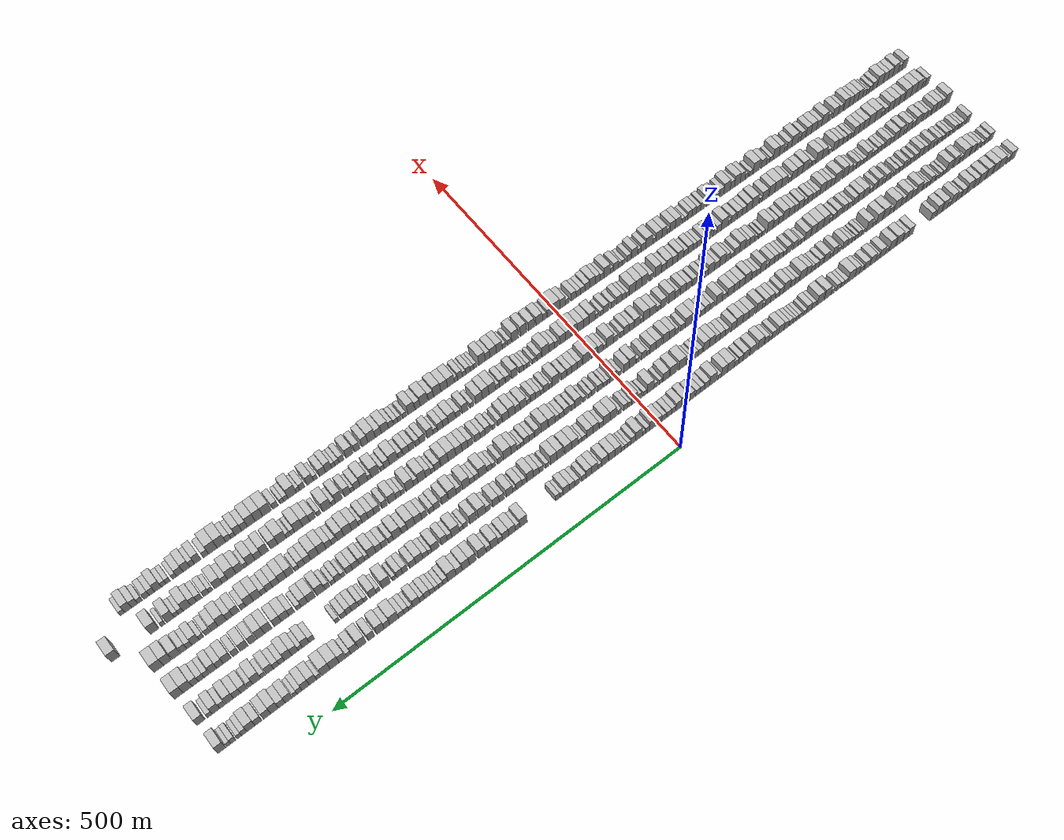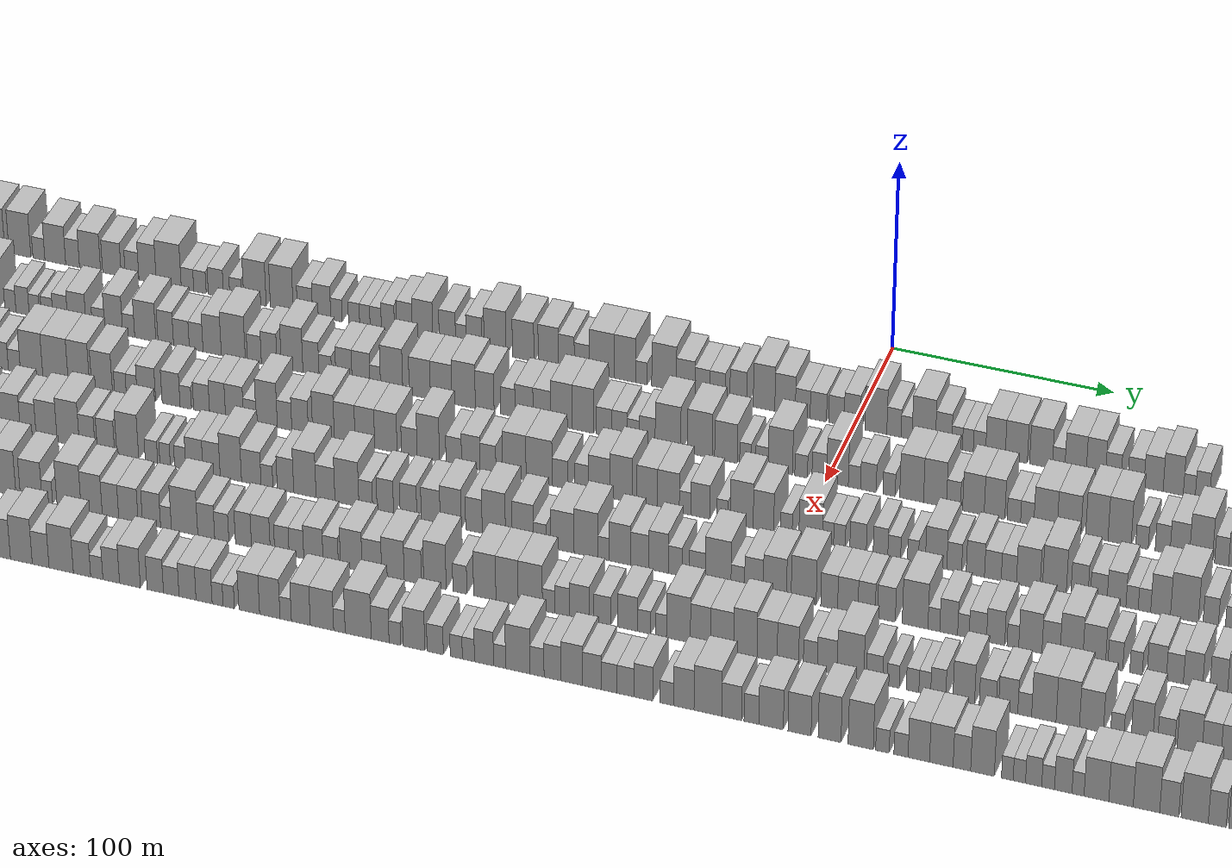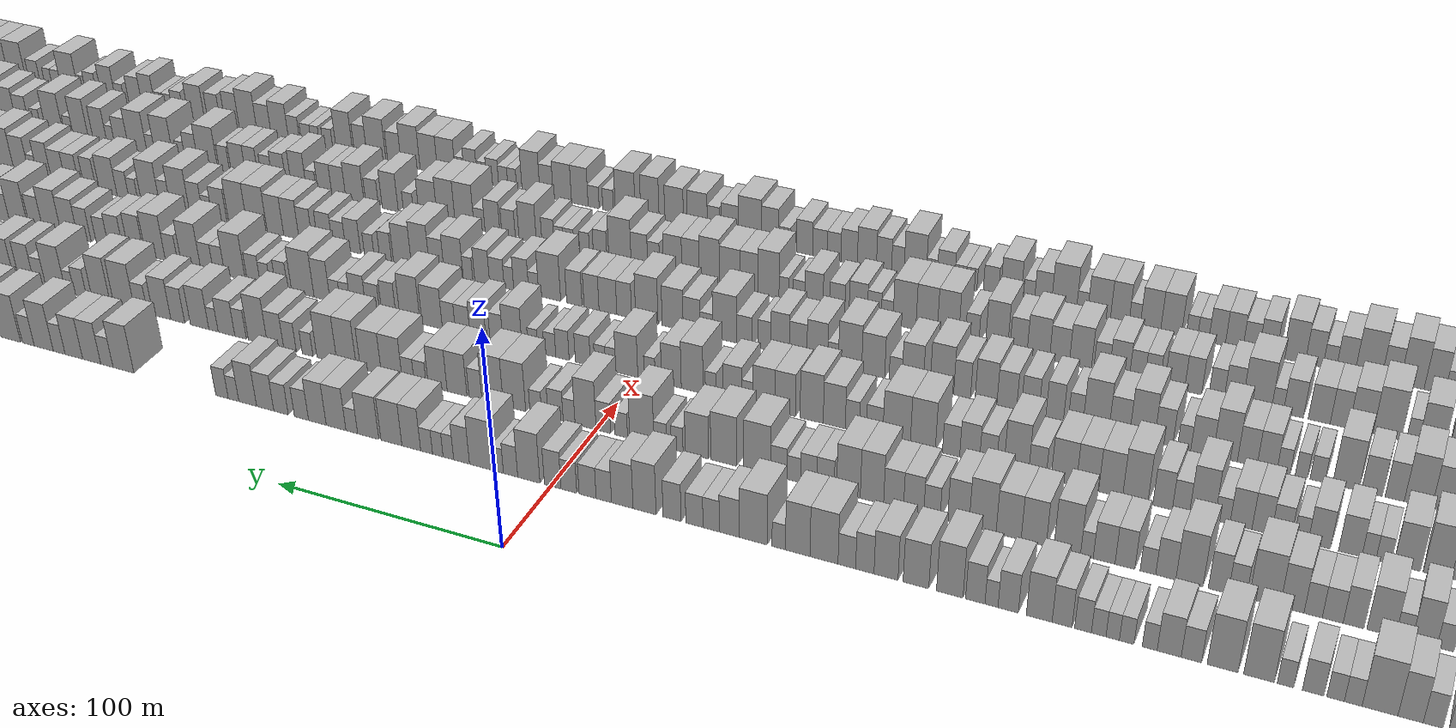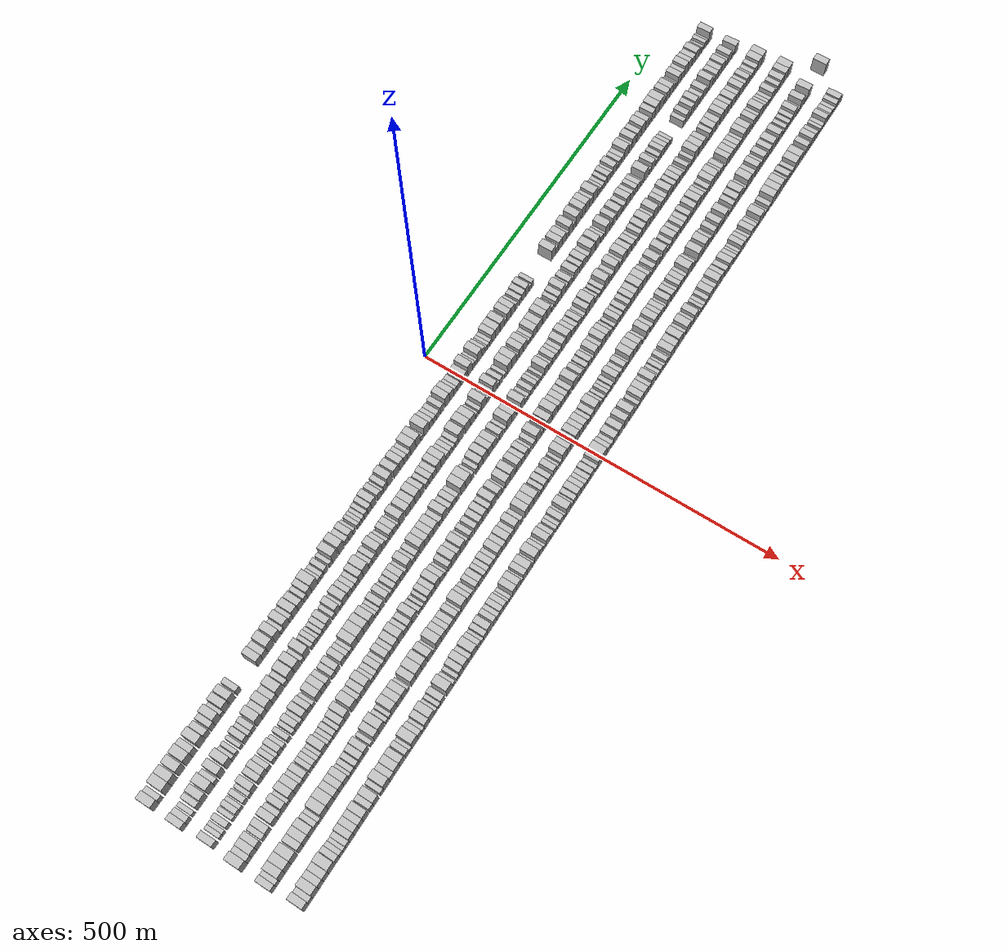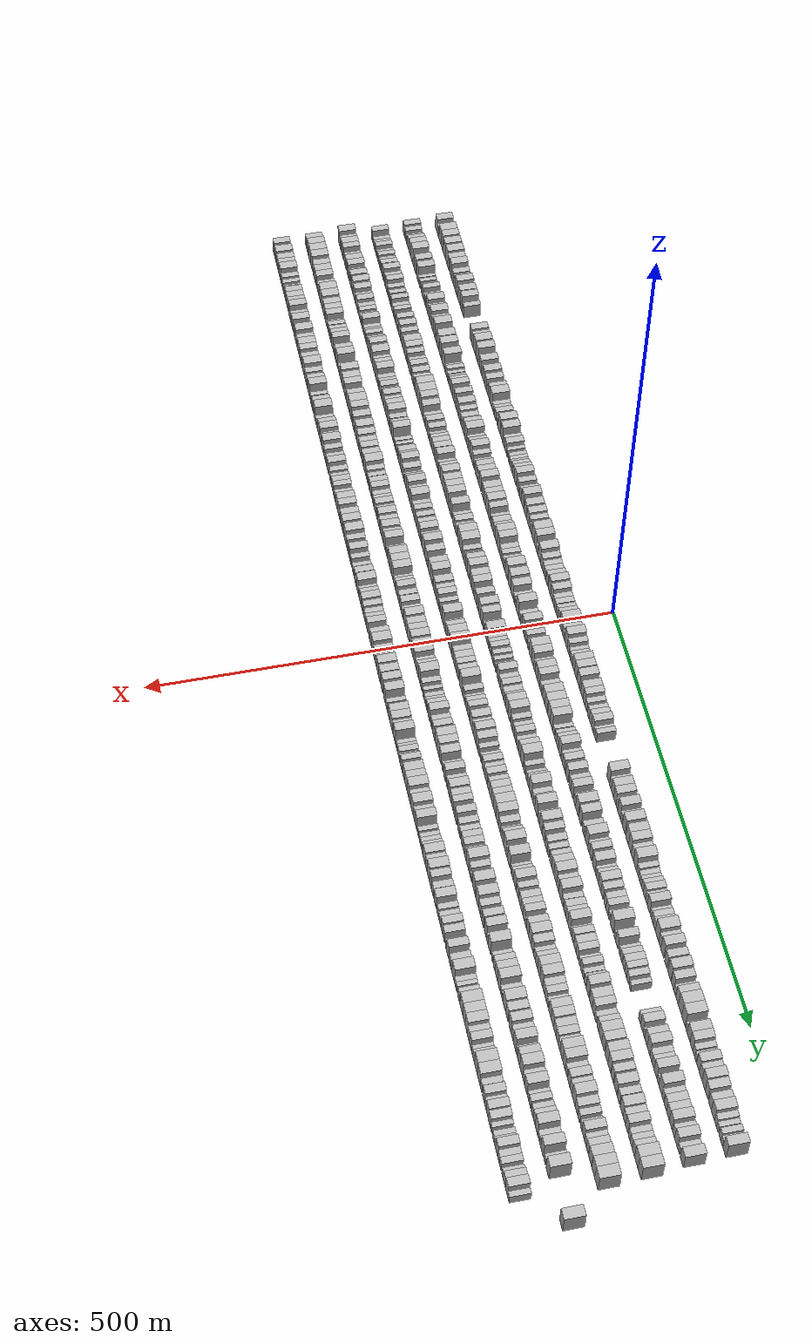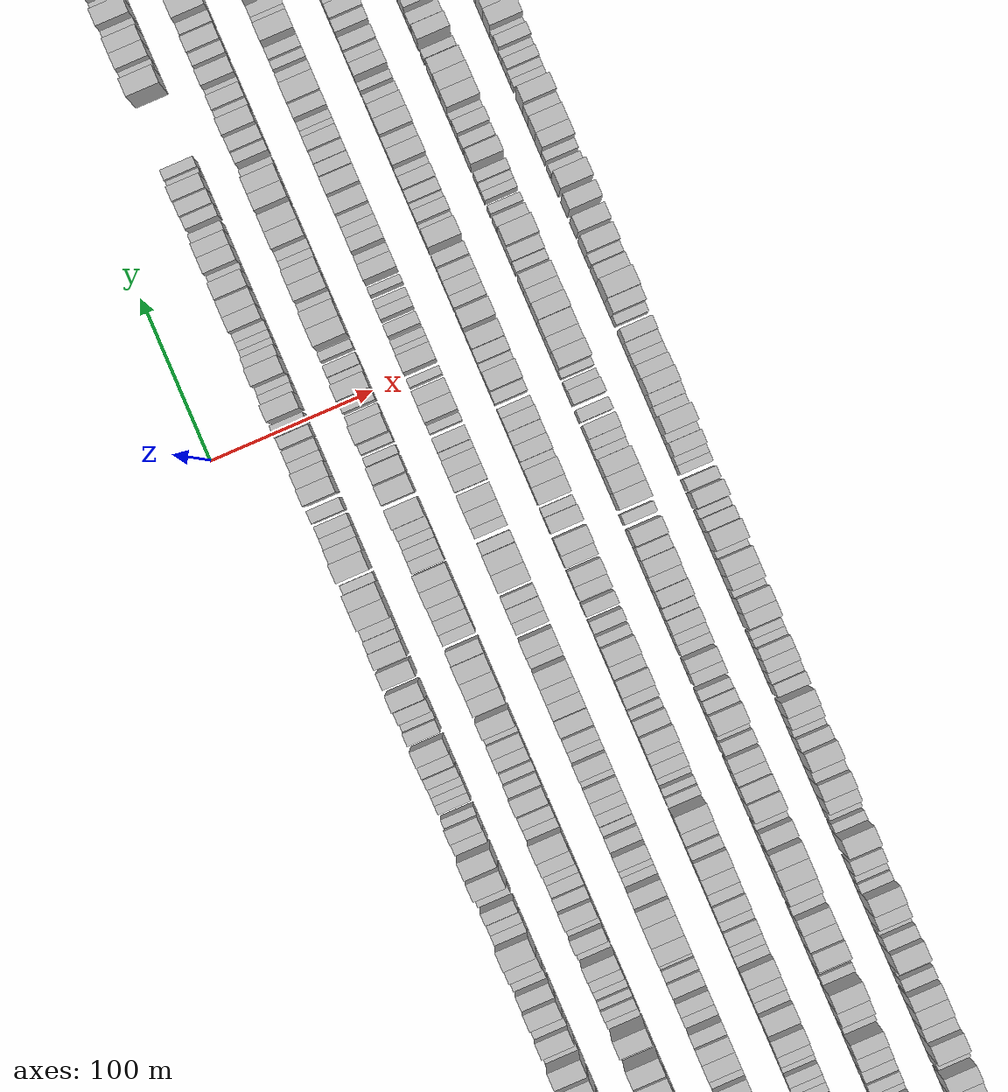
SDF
<sdf version="1.6">
 <world name="default">
  <scene>
   <sky><clouds><speed>12</speed></clouds></sky>
   <ambient>0.4 0.4 0.4 1</ambient>
   <background>0.7 0.7 0.7 1</background>
   <shadows>1</shadows>
  </scene>
  <gravity>0 0 -9.8066</gravity>
  <magnetic_field>6e-06 2.3e-05 -4.2e-05</magnetic_field>
  <physics default="0" name="default_physics" type="ode">
   <ode>
    <solver>
     <type>quick</type>
     <iters>10</iters>
     <sor>1.0</sor>
     <use_dynamic_moi_rescaling>0</use_dynamic_moi_rescaling>
    </solver>
    <constraints>
     <cfm>0</cfm>
     <erp>0.2</erp>
     <contact_max_correcting_vel>100</contact_max_correcting_vel>
     <contact_surface_layer>0.001</contact_surface_layer>
    </constraints>
   </ode>
   <max_step_size>0.004</max_step_size>
   <real_time_factor>1</real_time_factor>
   <real_time_update_rate>250</real_time_update_rate>
  </physics>
  <light name="sun" type="directional">
   <pose>0 0 10 0 0 0</pose>
   <diffuse>0.8 0.8 0.8 1</diffuse>
   <specular>0.2 0.2 0.2 1</specular>
   <attenuation>
    <range>1000</range>
    <constant>0.9</constant>
    <linear>0.01</linear>
    <quadratic>0.001</quadratic>
   </attenuation>
   <direction>-0.5 0.1 -0.9</direction>
  </light>
  <model name="building_1">
   <static>1</static>
   <pose>50.0000 -614.7696 0 0.000000 0.000000 0.000000</pose>
   <link name="link">
    <pose>0 0 10.50 0 0 0</pose>
    <collision name="collision"><geometry><box><size>20.0000 10.4608 21.0000</size></box></geometry></collision>
    <visual name="visual">
     <cast_shadows>0</cast_shadows>
     <geometry><box><size>20.0000 10.4608 21.0000</size></box></geometry>
     <material>
      <script>
       <uri>model://HANNAS_wall/materials/scripts</uri>
       <uri>model://HANNAS_wall/materials/textures</uri>
       <name>vrc/HANNAS_wall</name>
      </script>
     </material>
    </visual>
   </link>
  </model>
  <model name="building_2">
   <static>1</static>
   <pose>50.0000 -606.0425 0 0.000000 0.000000 0.000000</pose>
   <link name="link">
    <pose>0 0 7.50 0 0 0</pose>
    <collision name="collision"><geometry><box><size>20.0000 6.9933 15.0000</size></box></geometry></collision>
    <visual name="visual">
     <cast_shadows>0</cast_shadows>
     <geometry><box><size>20.0000 6.9933 15.0000</size></box></geometry>
     <material>
      <script>
       <uri>model://HANNAS_wall/materials/scripts</uri>
       <uri>model://HANNAS_wall/materials/textures</uri>
       <name>vrc/HANNAS_wall</name>
      </script>
     </material>
    </visual>
   </link>
  </model>
  <model name="building_3">
   <static>1</static>
   <pose>50.0000 -593.7017 0 0.000000 0.000000 0.000000</pose>
   <link name="link">
    <pose>0 0 12.00 0 0 0</pose>
    <collision name="collision"><geometry><box><size>20.0000 11.6883 24.0000</size></box></geometry></collision>
    <visual name="visual">
     <cast_shadows>0</cast_shadows>
     <geometry><box><size>20.0000 11.6883 24.0000</size></box></geometry>
     <material>
      <script>
       <uri>model://HANNAS_wall/materials/scripts</uri>
       <uri>model://HANNAS_wall/materials/textures</uri>
       <name>vrc/HANNAS_wall</name>
      </script>
     </material>
    </visual>
   </link>
  </model>
  <model name="building_4">
   <static>1</static>
   <pose>50.0000 -582.5032 0 0.000000 0.000000 0.000000</pose>
   <link name="link">
    <pose>0 0 12.00 0 0 0</pose>
    <collision name="collision"><geometry><box><size>20.0000 10.7088 24.0000</size></box></geometry></collision>
    <visual name="visual">
     <cast_shadows>0</cast_shadows>
     <geometry><box><size>20.0000 10.7088 24.0000</size></box></geometry>
     <material>
      <script>
       <uri>model://HANNAS_wall/materials/scripts</uri>
       <uri>model://HANNAS_wall/materials/textures</uri>
       <name>vrc/HANNAS_wall</name>
      </script>
     </material>
    </visual>
   </link>
  </model>
  <model name="building_5">
   <static>1</static>
   <pose>50.0000 -569.6281 0 0.000000 0.000000 0.000000</pose>
   <link name="link">
    <pose>0 0 12.00 0 0 0</pose>
    <collision name="collision"><geometry><box><size>20.0000 11.0413 24.0000</size></box></geometry></collision>
    <visual name="visual">
     <cast_shadows>0</cast_shadows>
     <geometry><box><size>20.0000 11.0413 24.0000</size></box></geometry>
     <material>
      <script>
       <uri>model://HANNAS_wall/materials/scripts</uri>
       <uri>model://HANNAS_wall/materials/textures</uri>
       <name>vrc/HANNAS_wall</name>
      </script>
     </material>
    </visual>
   </link>
  </model>
  <model name="building_6">
   <static>1</static>
   <pose>50.0000 -556.2338 0 0.000000 0.000000 0.000000</pose>
   <link name="link">
    <pose>0 0 12.00 0 0 0</pose>
    <collision name="collision"><geometry><box><size>20.0000 11.7473 24.0000</size></box></geometry></collision>
    <visual name="visual">
     <cast_shadows>0</cast_shadows>
     <geometry><box><size>20.0000 11.7473 24.0000</size></box></geometry>
     <material>
      <script>
       <uri>model://HANNAS_wall/materials/scripts</uri>
       <uri>model://HANNAS_wall/materials/textures</uri>
       <name>vrc/HANNAS_wall</name>
      </script>
     </material>
    </visual>
   </link>
  </model>
  <model name="building_7">
   <static>1</static>
   <pose>50.0000 -546.1125 0 0.000000 0.000000 0.000000</pose>
   <link name="link">
    <pose>0 0 10.50 0 0 0</pose>
    <collision name="collision"><geometry><box><size>20.0000 8.4954 21.0000</size></box></geometry></collision>
    <visual name="visual">
     <cast_shadows>0</cast_shadows>
     <geometry><box><size>20.0000 8.4954 21.0000</size></box></geometry>
     <material>
      <script>
       <uri>model://HANNAS_wall/materials/scripts</uri>
       <uri>model://HANNAS_wall/materials/textures</uri>
       <name>vrc/HANNAS_wall</name>
      </script>
     </material>
    </visual>
   </link>
  </model>
  <model name="building_8">
   <static>1</static>
   <pose>50.0000 -533.4575 0 0.000000 0.000000 0.000000</pose>
   <link name="link">
    <pose>0 0 12.00 0 0 0</pose>
    <collision name="collision"><geometry><box><size>20.0000 10.8145 24.0000</size></box></geometry></collision>
    <visual name="visual">
     <cast_shadows>0</cast_shadows>
     <geometry><box><size>20.0000 10.8145 24.0000</size></box></geometry>
     <material>
      <script>
       <uri>model://HANNAS_wall/materials/scripts</uri>
       <uri>model://HANNAS_wall/materials/textures</uri>
       <name>vrc/HANNAS_wall</name>
      </script>
     </material>
    </visual>
   </link>
  </model>
  <model name="building_9">
   <static>1</static>
   <pose>50.0000 -522.8115 0 0.000000 0.000000 0.000000</pose>
   <link name="link">
    <pose>0 0 9.00 0 0 0</pose>
    <collision name="collision"><geometry><box><size>20.0000 8.4775 18.0000</size></box></geometry></collision>
    <visual name="visual">
     <cast_shadows>0</cast_shadows>
     <geometry><box><size>20.0000 8.4775 18.0000</size></box></geometry>
     <material>
      <script>
       <uri>model://HANNAS_wall/materials/scripts</uri>
       <uri>model://HANNAS_wall/materials/textures</uri>
       <name>vrc/HANNAS_wall</name>
      </script>
     </material>
    </visual>
   </link>
  </model>
  <model name="building_10">
   <static>1</static>
   <pose>50.0000 -512.6700 0 0.000000 0.000000 0.000000</pose>
   <link name="link">
    <pose>0 0 9.00 0 0 0</pose>
    <collision name="collision"><geometry><box><size>20.0000 7.8055 18.0000</size></box></geometry></collision>
    <visual name="visual">
     <cast_shadows>0</cast_shadows>
     <geometry><box><size>20.0000 7.8055 18.0000</size></box></geometry>
     <material>
      <script>
       <uri>model://HANNAS_wall/materials/scripts</uri>
       <uri>model://HANNAS_wall/materials/textures</uri>
       <name>vrc/HANNAS_wall</name>
      </script>
     </material>
    </visual>
   </link>
  </model>
  <model name="building_11">
   <static>1</static>
   <pose>50.0000 -503.6404 0 0.000000 0.000000 0.000000</pose>
   <link name="link">
    <pose>0 0 12.00 0 0 0</pose>
    <collision name="collision"><geometry><box><size>20.0000 10.2537 24.0000</size></box></geometry></collision>
    <visual name="visual">
     <cast_shadows>0</cast_shadows>
     <geometry><box><size>20.0000 10.2537 24.0000</size></box></geometry>
     <material>
      <script>
       <uri>model://HANNAS_wall/materials/scripts</uri>
       <uri>model://HANNAS_wall/materials/textures</uri>
       <name>vrc/HANNAS_wall</name>
      </script>
     </material>
    </visual>
   </link>
  </model>
  <model name="building_12">
   <static>1</static>
   <pose>50.0000 -495.6090 0 0.000000 0.000000 0.000000</pose>
   <link name="link">
    <pose>0 0 6.00 0 0 0</pose>
    <collision name="collision"><geometry><box><size>20.0000 5.8091 12.0000</size></box></geometry></collision>
    <visual name="visual">
     <cast_shadows>0</cast_shadows>
     <geometry><box><size>20.0000 5.8091 12.0000</size></box></geometry>
     <material>
      <script>
       <uri>model://HANNAS_wall/materials/scripts</uri>
       <uri>model://HANNAS_wall/materials/textures</uri>
       <name>vrc/HANNAS_wall</name>
      </script>
     </material>
    </visual>
   </link>
  </model>
  <model name="building_13">
   <static>1</static>
   <pose>50.0000 -487.6144 0 0.000000 0.000000 0.000000</pose>
   <link name="link">
    <pose>0 0 12.00 0 0 0</pose>
    <collision name="collision"><geometry><box><size>20.0000 10.1801 24.0000</size></box></geometry></collision>
    <visual name="visual">
     <cast_shadows>0</cast_shadows>
     <geometry><box><size>20.0000 10.1801 24.0000</size></box></geometry>
     <material>
      <script>
       <uri>model://HANNAS_wall/materials/scripts</uri>
       <uri>model://HANNAS_wall/materials/textures</uri>
       <name>vrc/HANNAS_wall</name>
      </script>
     </material>
    </visual>
   </link>
  </model>
  <model name="building_14">
   <static>1</static>
   <pose>50.0000 -476.5391 0 0.000000 0.000000 0.000000</pose>
   <link name="link">
    <pose>0 0 12.00 0 0 0</pose>
    <collision name="collision"><geometry><box><size>20.0000 9.9705 24.0000</size></box></geometry></collision>
    <visual name="visual">
     <cast_shadows>0</cast_shadows>
     <geometry><box><size>20.0000 9.9705 24.0000</size></box></geometry>
     <material>
      <script>
       <uri>model://HANNAS_wall/materials/scripts</uri>
       <uri>model://HANNAS_wall/materials/textures</uri>
       <name>vrc/HANNAS_wall</name>
      </script>
     </material>
    </visual>
   </link>
  </model>
  <model name="building_15">
   <static>1</static>
   <pose>50.0000 -464.8646 0 0.000000 0.000000 0.000000</pose>
   <link name="link">
    <pose>0 0 9.00 0 0 0</pose>
    <collision name="collision"><geometry><box><size>20.0000 7.3786 18.0000</size></box></geometry></collision>
    <visual name="visual">
     <cast_shadows>0</cast_shadows>
     <geometry><box><size>20.0000 7.3786 18.0000</size></box></geometry>
     <material>
      <script>
       <uri>model://HANNAS_wall/materials/scripts</uri>
       <uri>model://HANNAS_wall/materials/textures</uri>
       <name>vrc/HANNAS_wall</name>
      </script>
     </material>
    </visual>
   </link>
  </model>
  <model name="building_16">
   <static>1</static>
   <pose>50.0000 -424.8164 0 0.000000 0.000000 0.000000</pose>
   <link name="link">
    <pose>0 0 10.50 0 0 0</pose>
    <collision name="collision"><geometry><box><size>20.0000 9.5725 21.0000</size></box></geometry></collision>
    <visual name="visual">
     <cast_shadows>0</cast_shadows>
     <geometry><box><size>20.0000 9.5725 21.0000</size></box></geometry>
     <material>
      <script>
       <uri>model://HANNAS_wall/materials/scripts</uri>
       <uri>model://HANNAS_wall/materials/textures</uri>
       <name>vrc/HANNAS_wall</name>
      </script>
     </material>
    </visual>
   </link>
  </model>
  <model name="building_17">
   <static>1</static>
   <pose>50.0000 -415.5871 0 0.000000 0.000000 0.000000</pose>
   <link name="link">
    <pose>0 0 9.00 0 0 0</pose>
    <collision name="collision"><geometry><box><size>20.0000 8.8862 18.0000</size></box></geometry></collision>
    <visual name="visual">
     <cast_shadows>0</cast_shadows>
     <geometry><box><size>20.0000 8.8862 18.0000</size></box></geometry>
     <material>
      <script>
       <uri>model://HANNAS_wall/materials/scripts</uri>
       <uri>model://HANNAS_wall/materials/textures</uri>
       <name>vrc/HANNAS_wall</name>
      </script>
     </material>
    </visual>
   </link>
  </model>
  <model name="building_18">
   <static>1</static>
   <pose>50.0000 -404.3878 0 0.000000 0.000000 0.000000</pose>
   <link name="link">
    <pose>0 0 12.00 0 0 0</pose>
    <collision name="collision"><geometry><box><size>20.0000 11.5125 24.0000</size></box></geometry></collision>
    <visual name="visual">
     <cast_shadows>0</cast_shadows>
     <geometry><box><size>20.0000 11.5125 24.0000</size></box></geometry>
     <material>
      <script>
       <uri>model://HANNAS_wall/materials/scripts</uri>
       <uri>model://HANNAS_wall/materials/textures</uri>
       <name>vrc/HANNAS_wall</name>
      </script>
     </material>
    </visual>
   </link>
  </model>
  <model name="building_19">
   <static>1</static>
   <pose>50.0000 -391.3246 0 0.000000 0.000000 0.000000</pose>
   <link name="link">
    <pose>0 0 12.00 0 0 0</pose>
    <collision name="collision"><geometry><box><size>20.0000 10.6138 24.0000</size></box></geometry></collision>
    <visual name="visual">
     <cast_shadows>0</cast_shadows>
     <geometry><box><size>20.0000 10.6138 24.0000</size></box></geometry>
     <material>
      <script>
       <uri>model://HANNAS_wall/materials/scripts</uri>
       <uri>model://HANNAS_wall/materials/textures</uri>
       <name>vrc/HANNAS_wall</name>
      </script>
     </material>
    </visual>
   </link>
  </model>
  <model name="building_20">
   <static>1</static>
   <pose>50.0000 -382.1065 0 0.000000 0.000000 0.000000</pose>
   <link name="link">
    <pose>0 0 6.00 0 0 0</pose>
    <collision name="collision"><geometry><box><size>20.0000 5.8224 12.0000</size></box></geometry></collision>
    <visual name="visual">
     <cast_shadows>0</cast_shadows>
     <geometry><box><size>20.0000 5.8224 12.0000</size></box></geometry>
     <material>
      <script>
       <uri>model://HANNAS_wall/materials/scripts</uri>
       <uri>model://HANNAS_wall/materials/textures</uri>
       <name>vrc/HANNAS_wall</name>
      </script>
     </material>
    </visual>
   </link>
  </model>
  <model name="building_21">
   <static>1</static>
   <pose>50.0000 -374.1370 0 0.000000 0.000000 0.000000</pose>
   <link name="link">
    <pose>0 0 10.50 0 0 0</pose>
    <collision name="collision"><geometry><box><size>20.0000 10.1166 21.0000</size></box></geometry></collision>
    <visual name="visual">
     <cast_shadows>0</cast_shadows>
     <geometry><box><size>20.0000 10.1166 21.0000</size></box></geometry>
     <material>
      <script>
       <uri>model://HANNAS_wall/materials/scripts</uri>
       <uri>model://HANNAS_wall/materials/textures</uri>
       <name>vrc/HANNAS_wall</name>
      </script>
     </material>
    </visual>
   </link>
  </model>
  <model name="building_22">
   <static>1</static>
   <pose>50.0000 -365.7314 0 0.000000 0.000000 0.000000</pose>
   <link name="link">
    <pose>0 0 7.50 0 0 0</pose>
    <collision name="collision"><geometry><box><size>20.0000 6.6946 15.0000</size></box></geometry></collision>
    <visual name="visual">
     <cast_shadows>0</cast_shadows>
     <geometry><box><size>20.0000 6.6946 15.0000</size></box></geometry>
     <material>
      <script>
       <uri>model://HANNAS_wall/materials/scripts</uri>
       <uri>model://HANNAS_wall/materials/textures</uri>
       <name>vrc/HANNAS_wall</name>
      </script>
     </material>
    </visual>
   </link>
  </model>
  <model name="building_23">
   <static>1</static>
   <pose>50.0000 -357.2742 0 0.000000 0.000000 0.000000</pose>
   <link name="link">
    <pose>0 0 10.50 0 0 0</pose>
    <collision name="collision"><geometry><box><size>20.0000 10.2197 21.0000</size></box></geometry></collision>
    <visual name="visual">
     <cast_shadows>0</cast_shadows>
     <geometry><box><size>20.0000 10.2197 21.0000</size></box></geometry>
     <material>
      <script>
       <uri>model://HANNAS_wall/materials/scripts</uri>
       <uri>model://HANNAS_wall/materials/textures</uri>
       <name>vrc/HANNAS_wall</name>
      </script>
     </material>
    </visual>
   </link>
  </model>
  <model name="building_24">
   <static>1</static>
   <pose>50.0000 -346.6693 0 0.000000 0.000000 0.000000</pose>
   <link name="link">
    <pose>0 0 9.00 0 0 0</pose>
    <collision name="collision"><geometry><box><size>20.0000 8.9901 18.0000</size></box></geometry></collision>
    <visual name="visual">
     <cast_shadows>0</cast_shadows>
     <geometry><box><size>20.0000 8.9901 18.0000</size></box></geometry>
     <material>
      <script>
       <uri>model://HANNAS_wall/materials/scripts</uri>
       <uri>model://HANNAS_wall/materials/textures</uri>
       <name>vrc/HANNAS_wall</name>
      </script>
     </material>
    </visual>
   </link>
  </model>
  <model name="building_25">
   <static>1</static>
   <pose>50.0000 -336.9139 0 0.000000 0.000000 0.000000</pose>
   <link name="link">
    <pose>0 0 7.50 0 0 0</pose>
    <collision name="collision"><geometry><box><size>20.0000 6.5207 15.0000</size></box></geometry></collision>
    <visual name="visual">
     <cast_shadows>0</cast_shadows>
     <geometry><box><size>20.0000 6.5207 15.0000</size></box></geometry>
     <material>
      <script>
       <uri>model://HANNAS_wall/materials/scripts</uri>
       <uri>model://HANNAS_wall/materials/textures</uri>
       <name>vrc/HANNAS_wall</name>
      </script>
     </material>
    </visual>
   </link>
  </model>
  <model name="building_26">
   <static>1</static>
   <pose>50.0000 -329.4480 0 0.000000 0.000000 0.000000</pose>
   <link name="link">
    <pose>0 0 10.50 0 0 0</pose>
    <collision name="collision"><geometry><box><size>20.0000 8.4112 21.0000</size></box></geometry></collision>
    <visual name="visual">
     <cast_shadows>0</cast_shadows>
     <geometry><box><size>20.0000 8.4112 21.0000</size></box></geometry>
     <material>
      <script>
       <uri>model://HANNAS_wall/materials/scripts</uri>
       <uri>model://HANNAS_wall/materials/textures</uri>
       <name>vrc/HANNAS_wall</name>
      </script>
     </material>
    </visual>
   </link>
  </model>
  <model name="building_27">
   <static>1</static>
   <pose>50.0000 -319.2474 0 0.000000 0.000000 0.000000</pose>
   <link name="link">
    <pose>0 0 12.00 0 0 0</pose>
    <collision name="collision"><geometry><box><size>20.0000 11.9900 24.0000</size></box></geometry></collision>
    <visual name="visual">
     <cast_shadows>0</cast_shadows>
     <geometry><box><size>20.0000 11.9900 24.0000</size></box></geometry>
     <material>
      <script>
       <uri>model://HANNAS_wall/materials/scripts</uri>
       <uri>model://HANNAS_wall/materials/textures</uri>
       <name>vrc/HANNAS_wall</name>
      </script>
     </material>
    </visual>
   </link>
  </model>
  <model name="building_28">
   <static>1</static>
   <pose>50.0000 -310.2612 0 0.000000 0.000000 0.000000</pose>
   <link name="link">
    <pose>0 0 6.00 0 0 0</pose>
    <collision name="collision"><geometry><box><size>20.0000 5.9823 12.0000</size></box></geometry></collision>
    <visual name="visual">
     <cast_shadows>0</cast_shadows>
     <geometry><box><size>20.0000 5.9823 12.0000</size></box></geometry>
     <material>
      <script>
       <uri>model://HANNAS_wall/materials/scripts</uri>
       <uri>model://HANNAS_wall/materials/textures</uri>
       <name>vrc/HANNAS_wall</name>
      </script>
     </material>
    </visual>
   </link>
  </model>
  <model name="building_29">
   <static>1</static>
   <pose>50.0000 -304.2907 0 0.000000 0.000000 0.000000</pose>
   <link name="link">
    <pose>0 0 6.00 0 0 0</pose>
    <collision name="collision"><geometry><box><size>20.0000 5.9585 12.0000</size></box></geometry></collision>
    <visual name="visual">
     <cast_shadows>0</cast_shadows>
     <geometry><box><size>20.0000 5.9585 12.0000</size></box></geometry>
     <material>
      <script>
       <uri>model://HANNAS_wall/materials/scripts</uri>
       <uri>model://HANNAS_wall/materials/textures</uri>
       <name>vrc/HANNAS_wall</name>
      </script>
     </material>
    </visual>
   </link>
  </model>
  <model name="building_30">
   <static>1</static>
   <pose>50.0000 -296.6453 0 0.000000 0.000000 0.000000</pose>
   <link name="link">
    <pose>0 0 7.50 0 0 0</pose>
    <collision name="collision"><geometry><box><size>20.0000 7.3324 15.0000</size></box></geometry></collision>
    <visual name="visual">
     <cast_shadows>0</cast_shadows>
     <geometry><box><size>20.0000 7.3324 15.0000</size></box></geometry>
     <material>
      <script>
       <uri>model://HANNAS_wall/materials/scripts</uri>
       <uri>model://HANNAS_wall/materials/textures</uri>
       <name>vrc/HANNAS_wall</name>
      </script>
     </material>
    </visual>
   </link>
  </model>
  <model name="building_31">
   <static>1</static>
   <pose>50.0000 -287.1371 0 0.000000 0.000000 0.000000</pose>
   <link name="link">
    <pose>0 0 6.00 0 0 0</pose>
    <collision name="collision"><geometry><box><size>20.0000 5.6839 12.0000</size></box></geometry></collision>
    <visual name="visual">
     <cast_shadows>0</cast_shadows>
     <geometry><box><size>20.0000 5.6839 12.0000</size></box></geometry>
     <material>
      <script>
       <uri>model://HANNAS_wall/materials/scripts</uri>
       <uri>model://HANNAS_wall/materials/textures</uri>
       <name>vrc/HANNAS_wall</name>
      </script>
     </material>
    </visual>
   </link>
  </model>
  <model name="building_32">
   <static>1</static>
   <pose>50.0000 -277.9631 0 0.000000 0.000000 0.000000</pose>
   <link name="link">
    <pose>0 0 12.00 0 0 0</pose>
    <collision name="collision"><geometry><box><size>20.0000 10.6641 24.0000</size></box></geometry></collision>
    <visual name="visual">
     <cast_shadows>0</cast_shadows>
     <geometry><box><size>20.0000 10.6641 24.0000</size></box></geometry>
     <material>
      <script>
       <uri>model://HANNAS_wall/materials/scripts</uri>
       <uri>model://HANNAS_wall/materials/textures</uri>
       <name>vrc/HANNAS_wall</name>
      </script>
     </material>
    </visual>
   </link>
  </model>
  <model name="building_33">
   <static>1</static>
   <pose>50.0000 -265.1993 0 0.000000 0.000000 0.000000</pose>
   <link name="link">
    <pose>0 0 12.00 0 0 0</pose>
    <collision name="collision"><geometry><box><size>20.0000 10.8635 24.0000</size></box></geometry></collision>
    <visual name="visual">
     <cast_shadows>0</cast_shadows>
     <geometry><box><size>20.0000 10.8635 24.0000</size></box></geometry>
     <material>
      <script>
       <uri>model://HANNAS_wall/materials/scripts</uri>
       <uri>model://HANNAS_wall/materials/textures</uri>
       <name>vrc/HANNAS_wall</name>
      </script>
     </material>
    </visual>
   </link>
  </model>
  <model name="building_34">
   <static>1</static>
   <pose>50.0000 -254.1556 0 0.000000 0.000000 0.000000</pose>
   <link name="link">
    <pose>0 0 7.50 0 0 0</pose>
    <collision name="collision"><geometry><box><size>20.0000 7.2239 15.0000</size></box></geometry></collision>
    <visual name="visual">
     <cast_shadows>0</cast_shadows>
     <geometry><box><size>20.0000 7.2239 15.0000</size></box></geometry>
     <material>
      <script>
       <uri>model://HANNAS_wall/materials/scripts</uri>
       <uri>model://HANNAS_wall/materials/textures</uri>
       <name>vrc/HANNAS_wall</name>
      </script>
     </material>
    </visual>
   </link>
  </model>
  <model name="building_35">
   <static>1</static>
   <pose>50.0000 -246.2314 0 0.000000 0.000000 0.000000</pose>
   <link name="link">
    <pose>0 0 9.00 0 0 0</pose>
    <collision name="collision"><geometry><box><size>20.0000 8.6245 18.0000</size></box></geometry></collision>
    <visual name="visual">
     <cast_shadows>0</cast_shadows>
     <geometry><box><size>20.0000 8.6245 18.0000</size></box></geometry>
     <material>
      <script>
       <uri>model://HANNAS_wall/materials/scripts</uri>
       <uri>model://HANNAS_wall/materials/textures</uri>
       <name>vrc/HANNAS_wall</name>
      </script>
     </material>
    </visual>
   </link>
  </model>
  <model name="building_36">
   <static>1</static>
   <pose>50.0000 -239.2300 0 0.000000 0.000000 0.000000</pose>
   <link name="link">
    <pose>0 0 6.00 0 0 0</pose>
    <collision name="collision"><geometry><box><size>20.0000 5.3783 12.0000</size></box></geometry></collision>
    <visual name="visual">
     <cast_shadows>0</cast_shadows>
     <geometry><box><size>20.0000 5.3783 12.0000</size></box></geometry>
     <material>
      <script>
       <uri>model://HANNAS_wall/materials/scripts</uri>
       <uri>model://HANNAS_wall/materials/textures</uri>
       <name>vrc/HANNAS_wall</name>
      </script>
     </material>
    </visual>
   </link>
  </model>
  <model name="building_37">
   <static>1</static>
   <pose>50.0000 -230.9007 0 0.000000 0.000000 0.000000</pose>
   <link name="link">
    <pose>0 0 6.00 0 0 0</pose>
    <collision name="collision"><geometry><box><size>20.0000 5.2803 12.0000</size></box></geometry></collision>
    <visual name="visual">
     <cast_shadows>0</cast_shadows>
     <geometry><box><size>20.0000 5.2803 12.0000</size></box></geometry>
     <material>
      <script>
       <uri>model://HANNAS_wall/materials/scripts</uri>
       <uri>model://HANNAS_wall/materials/textures</uri>
       <name>vrc/HANNAS_wall</name>
      </script>
     </material>
    </visual>
   </link>
  </model>
  <model name="building_38">
   <static>1</static>
   <pose>50.0000 -225.8033 0 0.000000 0.000000 0.000000</pose>
   <link name="link">
    <pose>0 0 6.00 0 0 0</pose>
    <collision name="collision"><geometry><box><size>20.0000 4.9144 12.0000</size></box></geometry></collision>
    <visual name="visual">
     <cast_shadows>0</cast_shadows>
     <geometry><box><size>20.0000 4.9144 12.0000</size></box></geometry>
     <material>
      <script>
       <uri>model://HANNAS_wall/materials/scripts</uri>
       <uri>model://HANNAS_wall/materials/textures</uri>
       <name>vrc/HANNAS_wall</name>
      </script>
     </material>
    </visual>
   </link>
  </model>
  <model name="building_39">
   <static>1</static>
   <pose>50.0000 -220.6770 0 0.000000 0.000000 0.000000</pose>
   <link name="link">
    <pose>0 0 6.00 0 0 0</pose>
    <collision name="collision"><geometry><box><size>20.0000 5.3383 12.0000</size></box></geometry></collision>
    <visual name="visual">
     <cast_shadows>0</cast_shadows>
     <geometry><box><size>20.0000 5.3383 12.0000</size></box></geometry>
     <material>
      <script>
       <uri>model://HANNAS_wall/materials/scripts</uri>
       <uri>model://HANNAS_wall/materials/textures</uri>
       <name>vrc/HANNAS_wall</name>
      </script>
     </material>
    </visual>
   </link>
  </model>
  <model name="building_40">
   <static>1</static>
   <pose>50.0000 -214.9217 0 0.000000 0.000000 0.000000</pose>
   <link name="link">
    <pose>0 0 7.50 0 0 0</pose>
    <collision name="collision"><geometry><box><size>20.0000 6.1723 15.0000</size></box></geometry></collision>
    <visual name="visual">
     <cast_shadows>0</cast_shadows>
     <geometry><box><size>20.0000 6.1723 15.0000</size></box></geometry>
     <material>
      <script>
       <uri>model://HANNAS_wall/materials/scripts</uri>
       <uri>model://HANNAS_wall/materials/textures</uri>
       <name>vrc/HANNAS_wall</name>
      </script>
     </material>
    </visual>
   </link>
  </model>
  <model name="building_41">
   <static>1</static>
   <pose>50.0000 -207.1523 0 0.000000 0.000000 0.000000</pose>
   <link name="link">
    <pose>0 0 9.00 0 0 0</pose>
    <collision name="collision"><geometry><box><size>20.0000 7.3665 18.0000</size></box></geometry></collision>
    <visual name="visual">
     <cast_shadows>0</cast_shadows>
     <geometry><box><size>20.0000 7.3665 18.0000</size></box></geometry>
     <material>
      <script>
       <uri>model://HANNAS_wall/materials/scripts</uri>
       <uri>model://HANNAS_wall/materials/textures</uri>
       <name>vrc/HANNAS_wall</name>
      </script>
     </material>
    </visual>
   </link>
  </model>
  <model name="building_42">
   <static>1</static>
   <pose>50.0000 -198.6440 0 0.000000 0.000000 0.000000</pose>
   <link name="link">
    <pose>0 0 10.50 0 0 0</pose>
    <collision name="collision"><geometry><box><size>20.0000 9.6501 21.0000</size></box></geometry></collision>
    <visual name="visual">
     <cast_shadows>0</cast_shadows>
     <geometry><box><size>20.0000 9.6501 21.0000</size></box></geometry>
     <material>
      <script>
       <uri>model://HANNAS_wall/materials/scripts</uri>
       <uri>model://HANNAS_wall/materials/textures</uri>
       <name>vrc/HANNAS_wall</name>
      </script>
     </material>
    </visual>
   </link>
  </model>
  <model name="building_43">
   <static>1</static>
   <pose>50.0000 -186.9753 0 0.000000 0.000000 0.000000</pose>
   <link name="link">
    <pose>0 0 9.00 0 0 0</pose>
    <collision name="collision"><geometry><box><size>20.0000 7.6873 18.0000</size></box></geometry></collision>
    <visual name="visual">
     <cast_shadows>0</cast_shadows>
     <geometry><box><size>20.0000 7.6873 18.0000</size></box></geometry>
     <material>
      <script>
       <uri>model://HANNAS_wall/materials/scripts</uri>
       <uri>model://HANNAS_wall/materials/textures</uri>
       <name>vrc/HANNAS_wall</name>
      </script>
     </material>
    </visual>
   </link>
  </model>
  <model name="building_44">
   <static>1</static>
   <pose>50.0000 -180.6573 0 0.000000 0.000000 0.000000</pose>
   <link name="link">
    <pose>0 0 6.00 0 0 0</pose>
    <collision name="collision"><geometry><box><size>20.0000 4.9486 12.0000</size></box></geometry></collision>
    <visual name="visual">
     <cast_shadows>0</cast_shadows>
     <geometry><box><size>20.0000 4.9486 12.0000</size></box></geometry>
     <material>
      <script>
       <uri>model://HANNAS_wall/materials/scripts</uri>
       <uri>model://HANNAS_wall/materials/textures</uri>
       <name>vrc/HANNAS_wall</name>
      </script>
     </material>
    </visual>
   </link>
  </model>
  <model name="building_45">
   <static>1</static>
   <pose>50.0000 -174.4760 0 0.000000 0.000000 0.000000</pose>
   <link name="link">
    <pose>0 0 9.00 0 0 0</pose>
    <collision name="collision"><geometry><box><size>20.0000 7.4140 18.0000</size></box></geometry></collision>
    <visual name="visual">
     <cast_shadows>0</cast_shadows>
     <geometry><box><size>20.0000 7.4140 18.0000</size></box></geometry>
     <material>
      <script>
       <uri>model://HANNAS_wall/materials/scripts</uri>
       <uri>model://HANNAS_wall/materials/textures</uri>
       <name>vrc/HANNAS_wall</name>
      </script>
     </material>
    </visual>
   </link>
  </model>
  <model name="building_46">
   <static>1</static>
   <pose>50.0000 -164.6649 0 0.000000 0.000000 0.000000</pose>
   <link name="link">
    <pose>0 0 12.00 0 0 0</pose>
    <collision name="collision"><geometry><box><size>20.0000 10.2083 24.0000</size></box></geometry></collision>
    <visual name="visual">
     <cast_shadows>0</cast_shadows>
     <geometry><box><size>20.0000 10.2083 24.0000</size></box></geometry>
     <material>
      <script>
       <uri>model://HANNAS_wall/materials/scripts</uri>
       <uri>model://HANNAS_wall/materials/textures</uri>
       <name>vrc/HANNAS_wall</name>
      </script>
     </material>
    </visual>
   </link>
  </model>
  <model name="building_47">
   <static>1</static>
   <pose>50.0000 -151.5582 0 0.000000 0.000000 0.000000</pose>
   <link name="link">
    <pose>0 0 10.50 0 0 0</pose>
    <collision name="collision"><geometry><box><size>20.0000 10.0052 21.0000</size></box></geometry></collision>
    <visual name="visual">
     <cast_shadows>0</cast_shadows>
     <geometry><box><size>20.0000 10.0052 21.0000</size></box></geometry>
     <material>
      <script>
       <uri>model://HANNAS_wall/materials/scripts</uri>
       <uri>model://HANNAS_wall/materials/textures</uri>
       <name>vrc/HANNAS_wall</name>
      </script>
     </material>
    </visual>
   </link>
  </model>
  <model name="building_48">
   <static>1</static>
   <pose>50.0000 -139.8257 0 0.000000 0.000000 0.000000</pose>
   <link name="link">
    <pose>0 0 10.50 0 0 0</pose>
    <collision name="collision"><geometry><box><size>20.0000 9.4598 21.0000</size></box></geometry></collision>
    <visual name="visual">
     <cast_shadows>0</cast_shadows>
     <geometry><box><size>20.0000 9.4598 21.0000</size></box></geometry>
     <material>
      <script>
       <uri>model://HANNAS_wall/materials/scripts</uri>
       <uri>model://HANNAS_wall/materials/textures</uri>
       <name>vrc/HANNAS_wall</name>
      </script>
     </material>
    </visual>
   </link>
  </model>
  <model name="building_49">
   <static>1</static>
   <pose>50.0000 -131.4566 0 0.000000 0.000000 0.000000</pose>
   <link name="link">
    <pose>0 0 9.00 0 0 0</pose>
    <collision name="collision"><geometry><box><size>20.0000 7.2784 18.0000</size></box></geometry></collision>
    <visual name="visual">
     <cast_shadows>0</cast_shadows>
     <geometry><box><size>20.0000 7.2784 18.0000</size></box></geometry>
     <material>
      <script>
       <uri>model://HANNAS_wall/materials/scripts</uri>
       <uri>model://HANNAS_wall/materials/textures</uri>
       <name>vrc/HANNAS_wall</name>
      </script>
     </material>
    </visual>
   </link>
  </model>
  <model name="building_50">
   <static>1</static>
   <pose>50.0000 -124.2976 0 0.000000 0.000000 0.000000</pose>
   <link name="link">
    <pose>0 0 7.50 0 0 0</pose>
    <collision name="collision"><geometry><box><size>20.0000 7.0396 15.0000</size></box></geometry></collision>
    <visual name="visual">
     <cast_shadows>0</cast_shadows>
     <geometry><box><size>20.0000 7.0396 15.0000</size></box></geometry>
     <material>
      <script>
       <uri>model://HANNAS_wall/materials/scripts</uri>
       <uri>model://HANNAS_wall/materials/textures</uri>
       <name>vrc/HANNAS_wall</name>
      </script>
     </material>
    </visual>
   </link>
  </model>
  <model name="building_51">
   <static>1</static>
   <pose>50.0000 -115.1420 0 0.000000 0.000000 0.000000</pose>
   <link name="link">
    <pose>0 0 12.00 0 0 0</pose>
    <collision name="collision"><geometry><box><size>20.0000 11.2716 24.0000</size></box></geometry></collision>
    <visual name="visual">
     <cast_shadows>0</cast_shadows>
     <geometry><box><size>20.0000 11.2716 24.0000</size></box></geometry>
     <material>
      <script>
       <uri>model://HANNAS_wall/materials/scripts</uri>
       <uri>model://HANNAS_wall/materials/textures</uri>
       <name>vrc/HANNAS_wall</name>
      </script>
     </material>
    </visual>
   </link>
  </model>
  <model name="building_52">
   <static>1</static>
   <pose>50.0000 -104.5410 0 0.000000 0.000000 0.000000</pose>
   <link name="link">
    <pose>0 0 12.00 0 0 0</pose>
    <collision name="collision"><geometry><box><size>20.0000 9.9304 24.0000</size></box></geometry></collision>
    <visual name="visual">
     <cast_shadows>0</cast_shadows>
     <geometry><box><size>20.0000 9.9304 24.0000</size></box></geometry>
     <material>
      <script>
       <uri>model://HANNAS_wall/materials/scripts</uri>
       <uri>model://HANNAS_wall/materials/textures</uri>
       <name>vrc/HANNAS_wall</name>
      </script>
     </material>
    </visual>
   </link>
  </model>
  <model name="building_53">
   <static>1</static>
   <pose>50.0000 -96.8227 0 0.000000 0.000000 0.000000</pose>
   <link name="link">
    <pose>0 0 6.00 0 0 0</pose>
    <collision name="collision"><geometry><box><size>20.0000 5.5062 12.0000</size></box></geometry></collision>
    <visual name="visual">
     <cast_shadows>0</cast_shadows>
     <geometry><box><size>20.0000 5.5062 12.0000</size></box></geometry>
     <material>
      <script>
       <uri>model://HANNAS_wall/materials/scripts</uri>
       <uri>model://HANNAS_wall/materials/textures</uri>
       <name>vrc/HANNAS_wall</name>
      </script>
     </material>
    </visual>
   </link>
  </model>
  <model name="building_54">
   <static>1</static>
   <pose>50.0000 -86.3731 0 0.000000 0.000000 0.000000</pose>
   <link name="link">
    <pose>0 0 12.00 0 0 0</pose>
    <collision name="collision"><geometry><box><size>20.0000 11.3929 24.0000</size></box></geometry></collision>
    <visual name="visual">
     <cast_shadows>0</cast_shadows>
     <geometry><box><size>20.0000 11.3929 24.0000</size></box></geometry>
     <material>
      <script>
       <uri>model://HANNAS_wall/materials/scripts</uri>
       <uri>model://HANNAS_wall/materials/textures</uri>
       <name>vrc/HANNAS_wall</name>
      </script>
     </material>
    </visual>
   </link>
  </model>
  <model name="building_55">
   <static>1</static>
   <pose>50.0000 -76.4783 0 0.000000 0.000000 0.000000</pose>
   <link name="link">
    <pose>0 0 9.00 0 0 0</pose>
    <collision name="collision"><geometry><box><size>20.0000 8.3968 18.0000</size></box></geometry></collision>
    <visual name="visual">
     <cast_shadows>0</cast_shadows>
     <geometry><box><size>20.0000 8.3968 18.0000</size></box></geometry>
     <material>
      <script>
       <uri>model://HANNAS_wall/materials/scripts</uri>
       <uri>model://HANNAS_wall/materials/textures</uri>
       <name>vrc/HANNAS_wall</name>
      </script>
     </material>
    </visual>
   </link>
  </model>
  <model name="building_56">
   <static>1</static>
   <pose>50.0000 -68.8575 0 0.000000 0.000000 0.000000</pose>
   <link name="link">
    <pose>0 0 7.50 0 0 0</pose>
    <collision name="collision"><geometry><box><size>20.0000 6.8449 15.0000</size></box></geometry></collision>
    <visual name="visual">
     <cast_shadows>0</cast_shadows>
     <geometry><box><size>20.0000 6.8449 15.0000</size></box></geometry>
     <material>
      <script>
       <uri>model://HANNAS_wall/materials/scripts</uri>
       <uri>model://HANNAS_wall/materials/textures</uri>
       <name>vrc/HANNAS_wall</name>
      </script>
     </material>
    </visual>
   </link>
  </model>
  <model name="building_57">
   <static>1</static>
   <pose>50.0000 -61.8239 0 0.000000 0.000000 0.000000</pose>
   <link name="link">
    <pose>0 0 7.50 0 0 0</pose>
    <collision name="collision"><geometry><box><size>20.0000 7.2223 15.0000</size></box></geometry></collision>
    <visual name="visual">
     <cast_shadows>0</cast_shadows>
     <geometry><box><size>20.0000 7.2223 15.0000</size></box></geometry>
     <material>
      <script>
       <uri>model://HANNAS_wall/materials/scripts</uri>
       <uri>model://HANNAS_wall/materials/textures</uri>
       <name>vrc/HANNAS_wall</name>
      </script>
     </material>
    </visual>
   </link>
  </model>
  <model name="building_58">
   <static>1</static>
   <pose>50.0000 -52.3916 0 0.000000 0.000000 0.000000</pose>
   <link name="link">
    <pose>0 0 9.00 0 0 0</pose>
    <collision name="collision"><geometry><box><size>20.0000 7.6421 18.0000</size></box></geometry></collision>
    <visual name="visual">
     <cast_shadows>0</cast_shadows>
     <geometry><box><size>20.0000 7.6421 18.0000</size></box></geometry>
     <material>
      <script>
       <uri>model://HANNAS_wall/materials/scripts</uri>
       <uri>model://HANNAS_wall/materials/textures</uri>
       <name>vrc/HANNAS_wall</name>
      </script>
     </material>
    </visual>
   </link>
  </model>
  <model name="building_59">
   <static>1</static>
   <pose>50.0000 -40.6573 0 0.000000 0.000000 0.000000</pose>
   <link name="link">
    <pose>0 0 12.00 0 0 0</pose>
    <collision name="collision"><geometry><box><size>20.0000 9.8266 24.0000</size></box></geometry></collision>
    <visual name="visual">
     <cast_shadows>0</cast_shadows>
     <geometry><box><size>20.0000 9.8266 24.0000</size></box></geometry>
     <material>
      <script>
       <uri>model://HANNAS_wall/materials/scripts</uri>
       <uri>model://HANNAS_wall/materials/textures</uri>
       <name>vrc/HANNAS_wall</name>
      </script>
     </material>
    </visual>
   </link>
  </model>
  <model name="building_60">
   <static>1</static>
   <pose>50.0000 -31.0826 0 0.000000 0.000000 0.000000</pose>
   <link name="link">
    <pose>0 0 10.50 0 0 0</pose>
    <collision name="collision"><geometry><box><size>20.0000 9.3229 21.0000</size></box></geometry></collision>
    <visual name="visual">
     <cast_shadows>0</cast_shadows>
     <geometry><box><size>20.0000 9.3229 21.0000</size></box></geometry>
     <material>
      <script>
       <uri>model://HANNAS_wall/materials/scripts</uri>
       <uri>model://HANNAS_wall/materials/textures</uri>
       <name>vrc/HANNAS_wall</name>
      </script>
     </material>
    </visual>
   </link>
  </model>
  <model name="building_61">
   <static>1</static>
   <pose>50.0000 -23.0632 0 0.000000 0.000000 0.000000</pose>
   <link name="link">
    <pose>0 0 7.50 0 0 0</pose>
    <collision name="collision"><geometry><box><size>20.0000 6.7157 15.0000</size></box></geometry></collision>
    <visual name="visual">
     <cast_shadows>0</cast_shadows>
     <geometry><box><size>20.0000 6.7157 15.0000</size></box></geometry>
     <material>
      <script>
       <uri>model://HANNAS_wall/materials/scripts</uri>
       <uri>model://HANNAS_wall/materials/textures</uri>
       <name>vrc/HANNAS_wall</name>
      </script>
     </material>
    </visual>
   </link>
  </model>
  <model name="building_62">
   <static>1</static>
   <pose>50.0000 -15.9845 0 0.000000 0.000000 0.000000</pose>
   <link name="link">
    <pose>0 0 7.50 0 0 0</pose>
    <collision name="collision"><geometry><box><size>20.0000 7.4417 15.0000</size></box></geometry></collision>
    <visual name="visual">
     <cast_shadows>0</cast_shadows>
     <geometry><box><size>20.0000 7.4417 15.0000</size></box></geometry>
     <material>
      <script>
       <uri>model://HANNAS_wall/materials/scripts</uri>
       <uri>model://HANNAS_wall/materials/textures</uri>
       <name>vrc/HANNAS_wall</name>
      </script>
     </material>
    </visual>
   </link>
  </model>
  <model name="building_63">
   <static>1</static>
   <pose>50.0000 -7.7758 0 0.000000 0.000000 0.000000</pose>
   <link name="link">
    <pose>0 0 7.50 0 0 0</pose>
    <collision name="collision"><geometry><box><size>20.0000 6.9758 15.0000</size></box></geometry></collision>
    <visual name="visual">
     <cast_shadows>0</cast_shadows>
     <geometry><box><size>20.0000 6.9758 15.0000</size></box></geometry>
     <material>
      <script>
       <uri>model://HANNAS_wall/materials/scripts</uri>
       <uri>model://HANNAS_wall/materials/textures</uri>
       <name>vrc/HANNAS_wall</name>
      </script>
     </material>
    </visual>
   </link>
  </model>
  <model name="building_64">
   <static>1</static>
   <pose>50.0000 -0.6182 0 0.000000 0.000000 0.000000</pose>
   <link name="link">
    <pose>0 0 9.00 0 0 0</pose>
    <collision name="collision"><geometry><box><size>20.0000 7.3394 18.0000</size></box></geometry></collision>
    <visual name="visual">
     <cast_shadows>0</cast_shadows>
     <geometry><box><size>20.0000 7.3394 18.0000</size></box></geometry>
     <material>
      <script>
       <uri>model://HANNAS_wall/materials/scripts</uri>
       <uri>model://HANNAS_wall/materials/textures</uri>
       <name>vrc/HANNAS_wall</name>
      </script>
     </material>
    </visual>
   </link>
  </model>
  <model name="building_65">
   <static>1</static>
   <pose>50.0000 10.0117 0 0.000000 0.000000 0.000000</pose>
   <link name="link">
    <pose>0 0 12.00 0 0 0</pose>
    <collision name="collision"><geometry><box><size>20.0000 9.9206 24.0000</size></box></geometry></collision>
    <visual name="visual">
     <cast_shadows>0</cast_shadows>
     <geometry><box><size>20.0000 9.9206 24.0000</size></box></geometry>
     <material>
      <script>
       <uri>model://HANNAS_wall/materials/scripts</uri>
       <uri>model://HANNAS_wall/materials/textures</uri>
       <name>vrc/HANNAS_wall</name>
      </script>
     </material>
    </visual>
   </link>
  </model>
  <model name="building_66">
   <static>1</static>
   <pose>50.0000 18.1784 0 0.000000 0.000000 0.000000</pose>
   <link name="link">
    <pose>0 0 7.50 0 0 0</pose>
    <collision name="collision"><geometry><box><size>20.0000 6.4127 15.0000</size></box></geometry></collision>
    <visual name="visual">
     <cast_shadows>0</cast_shadows>
     <geometry><box><size>20.0000 6.4127 15.0000</size></box></geometry>
     <material>
      <script>
       <uri>model://HANNAS_wall/materials/scripts</uri>
       <uri>model://HANNAS_wall/materials/textures</uri>
       <name>vrc/HANNAS_wall</name>
      </script>
     </material>
    </visual>
   </link>
  </model>
  <model name="building_67">
   <static>1</static>
   <pose>50.0000 23.8648 0 0.000000 0.000000 0.000000</pose>
   <link name="link">
    <pose>0 0 6.00 0 0 0</pose>
    <collision name="collision"><geometry><box><size>20.0000 4.9601 12.0000</size></box></geometry></collision>
    <visual name="visual">
     <cast_shadows>0</cast_shadows>
     <geometry><box><size>20.0000 4.9601 12.0000</size></box></geometry>
     <material>
      <script>
       <uri>model://HANNAS_wall/materials/scripts</uri>
       <uri>model://HANNAS_wall/materials/textures</uri>
       <name>vrc/HANNAS_wall</name>
      </script>
     </material>
    </visual>
   </link>
  </model>
  <model name="building_68">
   <static>1</static>
   <pose>50.0000 31.5771 0 0.000000 0.000000 0.000000</pose>
   <link name="link">
    <pose>0 0 12.00 0 0 0</pose>
    <collision name="collision"><geometry><box><size>20.0000 10.4645 24.0000</size></box></geometry></collision>
    <visual name="visual">
     <cast_shadows>0</cast_shadows>
     <geometry><box><size>20.0000 10.4645 24.0000</size></box></geometry>
     <material>
      <script>
       <uri>model://HANNAS_wall/materials/scripts</uri>
       <uri>model://HANNAS_wall/materials/textures</uri>
       <name>vrc/HANNAS_wall</name>
      </script>
     </material>
    </visual>
   </link>
  </model>
  <model name="building_69">
   <static>1</static>
   <pose>50.0000 40.4453 0 0.000000 0.000000 0.000000</pose>
   <link name="link">
    <pose>0 0 9.00 0 0 0</pose>
    <collision name="collision"><geometry><box><size>20.0000 7.2718 18.0000</size></box></geometry></collision>
    <visual name="visual">
     <cast_shadows>0</cast_shadows>
     <geometry><box><size>20.0000 7.2718 18.0000</size></box></geometry>
     <material>
      <script>
       <uri>model://HANNAS_wall/materials/scripts</uri>
       <uri>model://HANNAS_wall/materials/textures</uri>
       <name>vrc/HANNAS_wall</name>
      </script>
     </material>
    </visual>
   </link>
  </model>
  <model name="building_70">
   <static>1</static>
   <pose>50.0000 46.5001 0 0.000000 0.000000 0.000000</pose>
   <link name="link">
    <pose>0 0 6.00 0 0 0</pose>
    <collision name="collision"><geometry><box><size>20.0000 4.8379 12.0000</size></box></geometry></collision>
    <visual name="visual">
     <cast_shadows>0</cast_shadows>
     <geometry><box><size>20.0000 4.8379 12.0000</size></box></geometry>
     <material>
      <script>
       <uri>model://HANNAS_wall/materials/scripts</uri>
       <uri>model://HANNAS_wall/materials/textures</uri>
       <name>vrc/HANNAS_wall</name>
      </script>
     </material>
    </visual>
   </link>
  </model>
  <model name="building_71">
   <static>1</static>
   <pose>50.0000 51.3526 0 0.000000 0.000000 0.000000</pose>
   <link name="link">
    <pose>0 0 6.00 0 0 0</pose>
    <collision name="collision"><geometry><box><size>20.0000 4.8672 12.0000</size></box></geometry></collision>
    <visual name="visual">
     <cast_shadows>0</cast_shadows>
     <geometry><box><size>20.0000 4.8672 12.0000</size></box></geometry>
     <material>
      <script>
       <uri>model://HANNAS_wall/materials/scripts</uri>
       <uri>model://HANNAS_wall/materials/textures</uri>
       <name>vrc/HANNAS_wall</name>
      </script>
     </material>
    </visual>
   </link>
  </model>
  <model name="building_72">
   <static>1</static>
   <pose>50.0000 56.5397 0 0.000000 0.000000 0.000000</pose>
   <link name="link">
    <pose>0 0 6.00 0 0 0</pose>
    <collision name="collision"><geometry><box><size>20.0000 5.5069 12.0000</size></box></geometry></collision>
    <visual name="visual">
     <cast_shadows>0</cast_shadows>
     <geometry><box><size>20.0000 5.5069 12.0000</size></box></geometry>
     <material>
      <script>
       <uri>model://HANNAS_wall/materials/scripts</uri>
       <uri>model://HANNAS_wall/materials/textures</uri>
       <name>vrc/HANNAS_wall</name>
      </script>
     </material>
    </visual>
   </link>
  </model>
  <model name="building_73">
   <static>1</static>
   <pose>50.0000 63.6686 0 0.000000 0.000000 0.000000</pose>
   <link name="link">
    <pose>0 0 10.50 0 0 0</pose>
    <collision name="collision"><geometry><box><size>20.0000 8.7510 21.0000</size></box></geometry></collision>
    <visual name="visual">
     <cast_shadows>0</cast_shadows>
     <geometry><box><size>20.0000 8.7510 21.0000</size></box></geometry>
     <material>
      <script>
       <uri>model://HANNAS_wall/materials/scripts</uri>
       <uri>model://HANNAS_wall/materials/textures</uri>
       <name>vrc/HANNAS_wall</name>
      </script>
     </material>
    </visual>
   </link>
  </model>
  <model name="building_74">
   <static>1</static>
   <pose>50.0000 72.9881 0 0.000000 0.000000 0.000000</pose>
   <link name="link">
    <pose>0 0 10.50 0 0 0</pose>
    <collision name="collision"><geometry><box><size>20.0000 9.8880 21.0000</size></box></geometry></collision>
    <visual name="visual">
     <cast_shadows>0</cast_shadows>
     <geometry><box><size>20.0000 9.8880 21.0000</size></box></geometry>
     <material>
      <script>
       <uri>model://HANNAS_wall/materials/scripts</uri>
       <uri>model://HANNAS_wall/materials/textures</uri>
       <name>vrc/HANNAS_wall</name>
      </script>
     </material>
    </visual>
   </link>
  </model>
  <model name="building_75">
   <static>1</static>
   <pose>50.0000 83.9756 0 0.000000 0.000000 0.000000</pose>
   <link name="link">
    <pose>0 0 10.50 0 0 0</pose>
    <collision name="collision"><geometry><box><size>20.0000 10.0869 21.0000</size></box></geometry></collision>
    <visual name="visual">
     <cast_shadows>0</cast_shadows>
     <geometry><box><size>20.0000 10.0869 21.0000</size></box></geometry>
     <material>
      <script>
       <uri>model://HANNAS_wall/materials/scripts</uri>
       <uri>model://HANNAS_wall/materials/textures</uri>
       <name>vrc/HANNAS_wall</name>
      </script>
     </material>
    </visual>
   </link>
  </model>
  <model name="building_76">
   <static>1</static>
   <pose>50.0000 91.7912 0 0.000000 0.000000 0.000000</pose>
   <link name="link">
    <pose>0 0 6.00 0 0 0</pose>
    <collision name="collision"><geometry><box><size>20.0000 5.5443 12.0000</size></box></geometry></collision>
    <visual name="visual">
     <cast_shadows>0</cast_shadows>
     <geometry><box><size>20.0000 5.5443 12.0000</size></box></geometry>
     <material>
      <script>
       <uri>model://HANNAS_wall/materials/scripts</uri>
       <uri>model://HANNAS_wall/materials/textures</uri>
       <name>vrc/HANNAS_wall</name>
      </script>
     </material>
    </visual>
   </link>
  </model>
  <model name="building_77">
   <static>1</static>
   <pose>50.0000 99.2891 0 0.000000 0.000000 0.000000</pose>
   <link name="link">
    <pose>0 0 10.50 0 0 0</pose>
    <collision name="collision"><geometry><box><size>20.0000 9.4517 21.0000</size></box></geometry></collision>
    <visual name="visual">
     <cast_shadows>0</cast_shadows>
     <geometry><box><size>20.0000 9.4517 21.0000</size></box></geometry>
     <material>
      <script>
       <uri>model://HANNAS_wall/materials/scripts</uri>
       <uri>model://HANNAS_wall/materials/textures</uri>
       <name>vrc/HANNAS_wall</name>
      </script>
     </material>
    </visual>
   </link>
  </model>
  <model name="building_78">
   <static>1</static>
   <pose>50.0000 108.2831 0 0.000000 0.000000 0.000000</pose>
   <link name="link">
    <pose>0 0 10.50 0 0 0</pose>
    <collision name="collision"><geometry><box><size>20.0000 8.5363 21.0000</size></box></geometry></collision>
    <visual name="visual">
     <cast_shadows>0</cast_shadows>
     <geometry><box><size>20.0000 8.5363 21.0000</size></box></geometry>
     <material>
      <script>
       <uri>model://HANNAS_wall/materials/scripts</uri>
       <uri>model://HANNAS_wall/materials/textures</uri>
       <name>vrc/HANNAS_wall</name>
      </script>
     </material>
    </visual>
   </link>
  </model>
  <model name="building_79">
   <static>1</static>
   <pose>50.0000 115.9883 0 0.000000 0.000000 0.000000</pose>
   <link name="link">
    <pose>0 0 7.50 0 0 0</pose>
    <collision name="collision"><geometry><box><size>20.0000 6.8740 15.0000</size></box></geometry></collision>
    <visual name="visual">
     <cast_shadows>0</cast_shadows>
     <geometry><box><size>20.0000 6.8740 15.0000</size></box></geometry>
     <material>
      <script>
       <uri>model://HANNAS_wall/materials/scripts</uri>
       <uri>model://HANNAS_wall/materials/textures</uri>
       <name>vrc/HANNAS_wall</name>
      </script>
     </material>
    </visual>
   </link>
  </model>
  <model name="building_80">
   <static>1</static>
   <pose>50.0000 125.9807 0 0.000000 0.000000 0.000000</pose>
   <link name="link">
    <pose>0 0 7.50 0 0 0</pose>
    <collision name="collision"><geometry><box><size>20.0000 7.1107 15.0000</size></box></geometry></collision>
    <visual name="visual">
     <cast_shadows>0</cast_shadows>
     <geometry><box><size>20.0000 7.1107 15.0000</size></box></geometry>
     <material>
      <script>
       <uri>model://HANNAS_wall/materials/scripts</uri>
       <uri>model://HANNAS_wall/materials/textures</uri>
       <name>vrc/HANNAS_wall</name>
      </script>
     </material>
    </visual>
   </link>
  </model>
  <model name="building_81">
   <static>1</static>
   <pose>50.0000 133.7764 0 0.000000 0.000000 0.000000</pose>
   <link name="link">
    <pose>0 0 9.00 0 0 0</pose>
    <collision name="collision"><geometry><box><size>20.0000 8.4806 18.0000</size></box></geometry></collision>
    <visual name="visual">
     <cast_shadows>0</cast_shadows>
     <geometry><box><size>20.0000 8.4806 18.0000</size></box></geometry>
     <material>
      <script>
       <uri>model://HANNAS_wall/materials/scripts</uri>
       <uri>model://HANNAS_wall/materials/textures</uri>
       <name>vrc/HANNAS_wall</name>
      </script>
     </material>
    </visual>
   </link>
  </model>
  <model name="building_82">
   <static>1</static>
   <pose>50.0000 142.4412 0 0.000000 0.000000 0.000000</pose>
   <link name="link">
    <pose>0 0 10.50 0 0 0</pose>
    <collision name="collision"><geometry><box><size>20.0000 8.8489 21.0000</size></box></geometry></collision>
    <visual name="visual">
     <cast_shadows>0</cast_shadows>
     <geometry><box><size>20.0000 8.8489 21.0000</size></box></geometry>
     <material>
      <script>
       <uri>model://HANNAS_wall/materials/scripts</uri>
       <uri>model://HANNAS_wall/materials/textures</uri>
       <name>vrc/HANNAS_wall</name>
      </script>
     </material>
    </visual>
   </link>
  </model>
  <model name="building_83">
   <static>1</static>
   <pose>50.0000 149.4937 0 0.000000 0.000000 0.000000</pose>
   <link name="link">
    <pose>0 0 6.00 0 0 0</pose>
    <collision name="collision"><geometry><box><size>20.0000 5.2561 12.0000</size></box></geometry></collision>
    <visual name="visual">
     <cast_shadows>0</cast_shadows>
     <geometry><box><size>20.0000 5.2561 12.0000</size></box></geometry>
     <material>
      <script>
       <uri>model://HANNAS_wall/materials/scripts</uri>
       <uri>model://HANNAS_wall/materials/textures</uri>
       <name>vrc/HANNAS_wall</name>
      </script>
     </material>
    </visual>
   </link>
  </model>
  <model name="building_84">
   <static>1</static>
   <pose>50.0000 155.2547 0 0.000000 0.000000 0.000000</pose>
   <link name="link">
    <pose>0 0 7.50 0 0 0</pose>
    <collision name="collision"><geometry><box><size>20.0000 6.2658 15.0000</size></box></geometry></collision>
    <visual name="visual">
     <cast_shadows>0</cast_shadows>
     <geometry><box><size>20.0000 6.2658 15.0000</size></box></geometry>
     <material>
      <script>
       <uri>model://HANNAS_wall/materials/scripts</uri>
       <uri>model://HANNAS_wall/materials/textures</uri>
       <name>vrc/HANNAS_wall</name>
      </script>
     </material>
    </visual>
   </link>
  </model>
  <model name="building_85">
   <static>1</static>
   <pose>50.0000 205.6825 0 0.000000 0.000000 0.000000</pose>
   <link name="link">
    <pose>0 0 12.00 0 0 0</pose>
    <collision name="collision"><geometry><box><size>20.0000 10.8633 24.0000</size></box></geometry></collision>
    <visual name="visual">
     <cast_shadows>0</cast_shadows>
     <geometry><box><size>20.0000 10.8633 24.0000</size></box></geometry>
     <material>
      <script>
       <uri>model://HANNAS_wall/materials/scripts</uri>
       <uri>model://HANNAS_wall/materials/textures</uri>
       <name>vrc/HANNAS_wall</name>
      </script>
     </material>
    </visual>
   </link>
  </model>
  <model name="building_86">
   <static>1</static>
   <pose>50.0000 214.3302 0 0.000000 0.000000 0.000000</pose>
   <link name="link">
    <pose>0 0 7.50 0 0 0</pose>
    <collision name="collision"><geometry><box><size>20.0000 6.4321 15.0000</size></box></geometry></collision>
    <visual name="visual">
     <cast_shadows>0</cast_shadows>
     <geometry><box><size>20.0000 6.4321 15.0000</size></box></geometry>
     <material>
      <script>
       <uri>model://HANNAS_wall/materials/scripts</uri>
       <uri>model://HANNAS_wall/materials/textures</uri>
       <name>vrc/HANNAS_wall</name>
      </script>
     </material>
    </visual>
   </link>
  </model>
  <model name="building_87">
   <static>1</static>
   <pose>50.0000 222.3023 0 0.000000 0.000000 0.000000</pose>
   <link name="link">
    <pose>0 0 10.50 0 0 0</pose>
    <collision name="collision"><geometry><box><size>20.0000 9.5120 21.0000</size></box></geometry></collision>
    <visual name="visual">
     <cast_shadows>0</cast_shadows>
     <geometry><box><size>20.0000 9.5120 21.0000</size></box></geometry>
     <material>
      <script>
       <uri>model://HANNAS_wall/materials/scripts</uri>
       <uri>model://HANNAS_wall/materials/textures</uri>
       <name>vrc/HANNAS_wall</name>
      </script>
     </material>
    </visual>
   </link>
  </model>
  <model name="building_88">
   <static>1</static>
   <pose>50.0000 231.7271 0 0.000000 0.000000 0.000000</pose>
   <link name="link">
    <pose>0 0 10.50 0 0 0</pose>
    <collision name="collision"><geometry><box><size>20.0000 9.3376 21.0000</size></box></geometry></collision>
    <visual name="visual">
     <cast_shadows>0</cast_shadows>
     <geometry><box><size>20.0000 9.3376 21.0000</size></box></geometry>
     <material>
      <script>
       <uri>model://HANNAS_wall/materials/scripts</uri>
       <uri>model://HANNAS_wall/materials/textures</uri>
       <name>vrc/HANNAS_wall</name>
      </script>
     </material>
    </visual>
   </link>
  </model>
  <model name="building_89">
   <static>1</static>
   <pose>50.0000 239.5368 0 0.000000 0.000000 0.000000</pose>
   <link name="link">
    <pose>0 0 7.50 0 0 0</pose>
    <collision name="collision"><geometry><box><size>20.0000 6.2818 15.0000</size></box></geometry></collision>
    <visual name="visual">
     <cast_shadows>0</cast_shadows>
     <geometry><box><size>20.0000 6.2818 15.0000</size></box></geometry>
     <material>
      <script>
       <uri>model://HANNAS_wall/materials/scripts</uri>
       <uri>model://HANNAS_wall/materials/textures</uri>
       <name>vrc/HANNAS_wall</name>
      </script>
     </material>
    </visual>
   </link>
  </model>
  <model name="building_90">
   <static>1</static>
   <pose>50.0000 247.8378 0 0.000000 0.000000 0.000000</pose>
   <link name="link">
    <pose>0 0 12.00 0 0 0</pose>
    <collision name="collision"><geometry><box><size>20.0000 10.3202 24.0000</size></box></geometry></collision>
    <visual name="visual">
     <cast_shadows>0</cast_shadows>
     <geometry><box><size>20.0000 10.3202 24.0000</size></box></geometry>
     <material>
      <script>
       <uri>model://HANNAS_wall/materials/scripts</uri>
       <uri>model://HANNAS_wall/materials/textures</uri>
       <name>vrc/HANNAS_wall</name>
      </script>
     </material>
    </visual>
   </link>
  </model>
  <model name="building_91">
   <static>1</static>
   <pose>50.0000 256.1801 0 0.000000 0.000000 0.000000</pose>
   <link name="link">
    <pose>0 0 7.50 0 0 0</pose>
    <collision name="collision"><geometry><box><size>20.0000 6.3644 15.0000</size></box></geometry></collision>
    <visual name="visual">
     <cast_shadows>0</cast_shadows>
     <geometry><box><size>20.0000 6.3644 15.0000</size></box></geometry>
     <material>
      <script>
       <uri>model://HANNAS_wall/materials/scripts</uri>
       <uri>model://HANNAS_wall/materials/textures</uri>
       <name>vrc/HANNAS_wall</name>
      </script>
     </material>
    </visual>
   </link>
  </model>
  <model name="building_92">
   <static>1</static>
   <pose>50.0000 265.7434 0 0.000000 0.000000 0.000000</pose>
   <link name="link">
    <pose>0 0 12.00 0 0 0</pose>
    <collision name="collision"><geometry><box><size>20.0000 10.7623 24.0000</size></box></geometry></collision>
    <visual name="visual">
     <cast_shadows>0</cast_shadows>
     <geometry><box><size>20.0000 10.7623 24.0000</size></box></geometry>
     <material>
      <script>
       <uri>model://HANNAS_wall/materials/scripts</uri>
       <uri>model://HANNAS_wall/materials/textures</uri>
       <name>vrc/HANNAS_wall</name>
      </script>
     </material>
    </visual>
   </link>
  </model>
  <model name="building_93">
   <static>1</static>
   <pose>50.0000 279.0697 0 0.000000 0.000000 0.000000</pose>
   <link name="link">
    <pose>0 0 12.00 0 0 0</pose>
    <collision name="collision"><geometry><box><size>20.0000 9.8902 24.0000</size></box></geometry></collision>
    <visual name="visual">
     <cast_shadows>0</cast_shadows>
     <geometry><box><size>20.0000 9.8902 24.0000</size></box></geometry>
     <material>
      <script>
       <uri>model://HANNAS_wall/materials/scripts</uri>
       <uri>model://HANNAS_wall/materials/textures</uri>
       <name>vrc/HANNAS_wall</name>
      </script>
     </material>
    </visual>
   </link>
  </model>
  <model name="building_94">
   <static>1</static>
   <pose>50.0000 289.0580 0 0.000000 0.000000 0.000000</pose>
   <link name="link">
    <pose>0 0 12.00 0 0 0</pose>
    <collision name="collision"><geometry><box><size>20.0000 10.0862 24.0000</size></box></geometry></collision>
    <visual name="visual">
     <cast_shadows>0</cast_shadows>
     <geometry><box><size>20.0000 10.0862 24.0000</size></box></geometry>
     <material>
      <script>
       <uri>model://HANNAS_wall/materials/scripts</uri>
       <uri>model://HANNAS_wall/materials/textures</uri>
       <name>vrc/HANNAS_wall</name>
      </script>
     </material>
    </visual>
   </link>
  </model>
  <model name="building_95">
   <static>1</static>
   <pose>50.0000 298.4549 0 0.000000 0.000000 0.000000</pose>
   <link name="link">
    <pose>0 0 9.00 0 0 0</pose>
    <collision name="collision"><geometry><box><size>20.0000 8.7076 18.0000</size></box></geometry></collision>
    <visual name="visual">
     <cast_shadows>0</cast_shadows>
     <geometry><box><size>20.0000 8.7076 18.0000</size></box></geometry>
     <material>
      <script>
       <uri>model://HANNAS_wall/materials/scripts</uri>
       <uri>model://HANNAS_wall/materials/textures</uri>
       <name>vrc/HANNAS_wall</name>
      </script>
     </material>
    </visual>
   </link>
  </model>
  <model name="building_96">
   <static>1</static>
   <pose>50.0000 308.7177 0 0.000000 0.000000 0.000000</pose>
   <link name="link">
    <pose>0 0 12.00 0 0 0</pose>
    <collision name="collision"><geometry><box><size>20.0000 11.8181 24.0000</size></box></geometry></collision>
    <visual name="visual">
     <cast_shadows>0</cast_shadows>
     <geometry><box><size>20.0000 11.8181 24.0000</size></box></geometry>
     <material>
      <script>
       <uri>model://HANNAS_wall/materials/scripts</uri>
       <uri>model://HANNAS_wall/materials/textures</uri>
       <name>vrc/HANNAS_wall</name>
      </script>
     </material>
    </visual>
   </link>
  </model>
  <model name="building_97">
   <static>1</static>
   <pose>50.0000 317.9130 0 0.000000 0.000000 0.000000</pose>
   <link name="link">
    <pose>0 0 7.50 0 0 0</pose>
    <collision name="collision"><geometry><box><size>20.0000 6.5725 15.0000</size></box></geometry></collision>
    <visual name="visual">
     <cast_shadows>0</cast_shadows>
     <geometry><box><size>20.0000 6.5725 15.0000</size></box></geometry>
     <material>
      <script>
       <uri>model://HANNAS_wall/materials/scripts</uri>
       <uri>model://HANNAS_wall/materials/textures</uri>
       <name>vrc/HANNAS_wall</name>
      </script>
     </material>
    </visual>
   </link>
  </model>
  <model name="building_98">
   <static>1</static>
   <pose>50.0000 324.1187 0 0.000000 0.000000 0.000000</pose>
   <link name="link">
    <pose>0 0 6.00 0 0 0</pose>
    <collision name="collision"><geometry><box><size>20.0000 5.8389 12.0000</size></box></geometry></collision>
    <visual name="visual">
     <cast_shadows>0</cast_shadows>
     <geometry><box><size>20.0000 5.8389 12.0000</size></box></geometry>
     <material>
      <script>
       <uri>model://HANNAS_wall/materials/scripts</uri>
       <uri>model://HANNAS_wall/materials/textures</uri>
       <name>vrc/HANNAS_wall</name>
      </script>
     </material>
    </visual>
   </link>
  </model>
  <model name="building_99">
   <static>1</static>
   <pose>50.0000 329.9187 0 0.000000 0.000000 0.000000</pose>
   <link name="link">
    <pose>0 0 6.00 0 0 0</pose>
    <collision name="collision"><geometry><box><size>20.0000 5.7612 12.0000</size></box></geometry></collision>
    <visual name="visual">
     <cast_shadows>0</cast_shadows>
     <geometry><box><size>20.0000 5.7612 12.0000</size></box></geometry>
     <material>
      <script>
       <uri>model://HANNAS_wall/materials/scripts</uri>
       <uri>model://HANNAS_wall/materials/textures</uri>
       <name>vrc/HANNAS_wall</name>
      </script>
     </material>
    </visual>
   </link>
  </model>
  <model name="building_100">
   <static>1</static>
   <pose>50.0000 336.0989 0 0.000000 0.000000 0.000000</pose>
   <link name="link">
    <pose>0 0 7.50 0 0 0</pose>
    <collision name="collision"><geometry><box><size>20.0000 6.5991 15.0000</size></box></geometry></collision>
    <visual name="visual">
     <cast_shadows>0</cast_shadows>
     <geometry><box><size>20.0000 6.5991 15.0000</size></box></geometry>
     <material>
      <script>
       <uri>model://HANNAS_wall/materials/scripts</uri>
       <uri>model://HANNAS_wall/materials/textures</uri>
       <name>vrc/HANNAS_wall</name>
      </script>
     </material>
    </visual>
   </link>
  </model>
  <model name="building_101">
   <static>1</static>
   <pose>50.0000 343.4190 0 0.000000 0.000000 0.000000</pose>
   <link name="link">
    <pose>0 0 9.00 0 0 0</pose>
    <collision name="collision"><geometry><box><size>20.0000 8.0412 18.0000</size></box></geometry></collision>
    <visual name="visual">
     <cast_shadows>0</cast_shadows>
     <geometry><box><size>20.0000 8.0412 18.0000</size></box></geometry>
     <material>
      <script>
       <uri>model://HANNAS_wall/materials/scripts</uri>
       <uri>model://HANNAS_wall/materials/textures</uri>
       <name>vrc/HANNAS_wall</name>
      </script>
     </material>
    </visual>
   </link>
  </model>
  <model name="building_102">
   <static>1</static>
   <pose>50.0000 350.4872 0 0.000000 0.000000 0.000000</pose>
   <link name="link">
    <pose>0 0 7.50 0 0 0</pose>
    <collision name="collision"><geometry><box><size>20.0000 6.0953 15.0000</size></box></geometry></collision>
    <visual name="visual">
     <cast_shadows>0</cast_shadows>
     <geometry><box><size>20.0000 6.0953 15.0000</size></box></geometry>
     <material>
      <script>
       <uri>model://HANNAS_wall/materials/scripts</uri>
       <uri>model://HANNAS_wall/materials/textures</uri>
       <name>vrc/HANNAS_wall</name>
      </script>
     </material>
    </visual>
   </link>
  </model>
  <model name="building_103">
   <static>1</static>
   <pose>50.0000 358.2339 0 0.000000 0.000000 0.000000</pose>
   <link name="link">
    <pose>0 0 10.50 0 0 0</pose>
    <collision name="collision"><geometry><box><size>20.0000 9.3980 21.0000</size></box></geometry></collision>
    <visual name="visual">
     <cast_shadows>0</cast_shadows>
     <geometry><box><size>20.0000 9.3980 21.0000</size></box></geometry>
     <material>
      <script>
       <uri>model://HANNAS_wall/materials/scripts</uri>
       <uri>model://HANNAS_wall/materials/textures</uri>
       <name>vrc/HANNAS_wall</name>
      </script>
     </material>
    </visual>
   </link>
  </model>
  <model name="building_104">
   <static>1</static>
   <pose>50.0000 366.4157 0 0.000000 0.000000 0.000000</pose>
   <link name="link">
    <pose>0 0 6.00 0 0 0</pose>
    <collision name="collision"><geometry><box><size>20.0000 4.9656 12.0000</size></box></geometry></collision>
    <visual name="visual">
     <cast_shadows>0</cast_shadows>
     <geometry><box><size>20.0000 4.9656 12.0000</size></box></geometry>
     <material>
      <script>
       <uri>model://HANNAS_wall/materials/scripts</uri>
       <uri>model://HANNAS_wall/materials/textures</uri>
       <name>vrc/HANNAS_wall</name>
      </script>
     </material>
    </visual>
   </link>
  </model>
  <model name="building_105">
   <static>1</static>
   <pose>50.0000 372.3420 0 0.000000 0.000000 0.000000</pose>
   <link name="link">
    <pose>0 0 7.50 0 0 0</pose>
    <collision name="collision"><geometry><box><size>20.0000 6.8870 15.0000</size></box></geometry></collision>
    <visual name="visual">
     <cast_shadows>0</cast_shadows>
     <geometry><box><size>20.0000 6.8870 15.0000</size></box></geometry>
     <material>
      <script>
       <uri>model://HANNAS_wall/materials/scripts</uri>
       <uri>model://HANNAS_wall/materials/textures</uri>
       <name>vrc/HANNAS_wall</name>
      </script>
     </material>
    </visual>
   </link>
  </model>
  <model name="building_106">
   <static>1</static>
   <pose>50.0000 379.4126 0 0.000000 0.000000 0.000000</pose>
   <link name="link">
    <pose>0 0 7.50 0 0 0</pose>
    <collision name="collision"><geometry><box><size>20.0000 7.2542 15.0000</size></box></geometry></collision>
    <visual name="visual">
     <cast_shadows>0</cast_shadows>
     <geometry><box><size>20.0000 7.2542 15.0000</size></box></geometry>
     <material>
      <script>
       <uri>model://HANNAS_wall/materials/scripts</uri>
       <uri>model://HANNAS_wall/materials/textures</uri>
       <name>vrc/HANNAS_wall</name>
      </script>
     </material>
    </visual>
   </link>
  </model>
  <model name="building_107">
   <static>1</static>
   <pose>50.0000 388.9922 0 0.000000 0.000000 0.000000</pose>
   <link name="link">
    <pose>0 0 12.00 0 0 0</pose>
    <collision name="collision"><geometry><box><size>20.0000 11.9051 24.0000</size></box></geometry></collision>
    <visual name="visual">
     <cast_shadows>0</cast_shadows>
     <geometry><box><size>20.0000 11.9051 24.0000</size></box></geometry>
     <material>
      <script>
       <uri>model://HANNAS_wall/materials/scripts</uri>
       <uri>model://HANNAS_wall/materials/textures</uri>
       <name>vrc/HANNAS_wall</name>
      </script>
     </material>
    </visual>
   </link>
  </model>
  <model name="building_108">
   <static>1</static>
   <pose>50.0000 398.8072 0 0.000000 0.000000 0.000000</pose>
   <link name="link">
    <pose>0 0 9.00 0 0 0</pose>
    <collision name="collision"><geometry><box><size>20.0000 7.7250 18.0000</size></box></geometry></collision>
    <visual name="visual">
     <cast_shadows>0</cast_shadows>
     <geometry><box><size>20.0000 7.7250 18.0000</size></box></geometry>
     <material>
      <script>
       <uri>model://HANNAS_wall/materials/scripts</uri>
       <uri>model://HANNAS_wall/materials/textures</uri>
       <name>vrc/HANNAS_wall</name>
      </script>
     </material>
    </visual>
   </link>
  </model>
  <model name="building_109">
   <static>1</static>
   <pose>50.0000 407.7557 0 0.000000 0.000000 0.000000</pose>
   <link name="link">
    <pose>0 0 12.00 0 0 0</pose>
    <collision name="collision"><geometry><box><size>20.0000 10.1720 24.0000</size></box></geometry></collision>
    <visual name="visual">
     <cast_shadows>0</cast_shadows>
     <geometry><box><size>20.0000 10.1720 24.0000</size></box></geometry>
     <material>
      <script>
       <uri>model://HANNAS_wall/materials/scripts</uri>
       <uri>model://HANNAS_wall/materials/textures</uri>
       <name>vrc/HANNAS_wall</name>
      </script>
     </material>
    </visual>
   </link>
  </model>
  <model name="building_110">
   <static>1</static>
   <pose>50.0000 420.1055 0 0.000000 0.000000 0.000000</pose>
   <link name="link">
    <pose>0 0 10.50 0 0 0</pose>
    <collision name="collision"><geometry><box><size>20.0000 8.5276 21.0000</size></box></geometry></collision>
    <visual name="visual">
     <cast_shadows>0</cast_shadows>
     <geometry><box><size>20.0000 8.5276 21.0000</size></box></geometry>
     <material>
      <script>
       <uri>model://HANNAS_wall/materials/scripts</uri>
       <uri>model://HANNAS_wall/materials/textures</uri>
       <name>vrc/HANNAS_wall</name>
      </script>
     </material>
    </visual>
   </link>
  </model>
  <model name="building_111">
   <static>1</static>
   <pose>50.0000 432.6620 0 0.000000 0.000000 0.000000</pose>
   <link name="link">
    <pose>0 0 12.00 0 0 0</pose>
    <collision name="collision"><geometry><box><size>20.0000 10.5853 24.0000</size></box></geometry></collision>
    <visual name="visual">
     <cast_shadows>0</cast_shadows>
     <geometry><box><size>20.0000 10.5853 24.0000</size></box></geometry>
     <material>
      <script>
       <uri>model://HANNAS_wall/materials/scripts</uri>
       <uri>model://HANNAS_wall/materials/textures</uri>
       <name>vrc/HANNAS_wall</name>
      </script>
     </material>
    </visual>
   </link>
  </model>
  <model name="building_112">
   <static>1</static>
   <pose>50.0000 443.5451 0 0.000000 0.000000 0.000000</pose>
   <link name="link">
    <pose>0 0 10.50 0 0 0</pose>
    <collision name="collision"><geometry><box><size>20.0000 9.1810 21.0000</size></box></geometry></collision>
    <visual name="visual">
     <cast_shadows>0</cast_shadows>
     <geometry><box><size>20.0000 9.1810 21.0000</size></box></geometry>
     <material>
      <script>
       <uri>model://HANNAS_wall/materials/scripts</uri>
       <uri>model://HANNAS_wall/materials/textures</uri>
       <name>vrc/HANNAS_wall</name>
      </script>
     </material>
    </visual>
   </link>
  </model>
  <model name="building_113">
   <static>1</static>
   <pose>50.0000 450.9675 0 0.000000 0.000000 0.000000</pose>
   <link name="link">
    <pose>0 0 6.00 0 0 0</pose>
    <collision name="collision"><geometry><box><size>20.0000 5.6637 12.0000</size></box></geometry></collision>
    <visual name="visual">
     <cast_shadows>0</cast_shadows>
     <geometry><box><size>20.0000 5.6637 12.0000</size></box></geometry>
     <material>
      <script>
       <uri>model://HANNAS_wall/materials/scripts</uri>
       <uri>model://HANNAS_wall/materials/textures</uri>
       <name>vrc/HANNAS_wall</name>
      </script>
     </material>
    </visual>
   </link>
  </model>
  <model name="building_114">
   <static>1</static>
   <pose>50.0000 459.3117 0 0.000000 0.000000 0.000000</pose>
   <link name="link">
    <pose>0 0 10.50 0 0 0</pose>
    <collision name="collision"><geometry><box><size>20.0000 9.0249 21.0000</size></box></geometry></collision>
    <visual name="visual">
     <cast_shadows>0</cast_shadows>
     <geometry><box><size>20.0000 9.0249 21.0000</size></box></geometry>
     <material>
      <script>
       <uri>model://HANNAS_wall/materials/scripts</uri>
       <uri>model://HANNAS_wall/materials/textures</uri>
       <name>vrc/HANNAS_wall</name>
      </script>
     </material>
    </visual>
   </link>
  </model>
  <model name="building_115">
   <static>1</static>
   <pose>50.0000 469.6719 0 0.000000 0.000000 0.000000</pose>
   <link name="link">
    <pose>0 0 12.00 0 0 0</pose>
    <collision name="collision"><geometry><box><size>20.0000 11.6955 24.0000</size></box></geometry></collision>
    <visual name="visual">
     <cast_shadows>0</cast_shadows>
     <geometry><box><size>20.0000 11.6955 24.0000</size></box></geometry>
     <material>
      <script>
       <uri>model://HANNAS_wall/materials/scripts</uri>
       <uri>model://HANNAS_wall/materials/textures</uri>
       <name>vrc/HANNAS_wall</name>
      </script>
     </material>
    </visual>
   </link>
  </model>
  <model name="building_116">
   <static>1</static>
   <pose>50.0000 481.3776 0 0.000000 0.000000 0.000000</pose>
   <link name="link">
    <pose>0 0 12.00 0 0 0</pose>
    <collision name="collision"><geometry><box><size>20.0000 11.7159 24.0000</size></box></geometry></collision>
    <visual name="visual">
     <cast_shadows>0</cast_shadows>
     <geometry><box><size>20.0000 11.7159 24.0000</size></box></geometry>
     <material>
      <script>
       <uri>model://HANNAS_wall/materials/scripts</uri>
       <uri>model://HANNAS_wall/materials/textures</uri>
       <name>vrc/HANNAS_wall</name>
      </script>
     </material>
    </visual>
   </link>
  </model>
  <model name="building_117">
   <static>1</static>
   <pose>50.0000 490.9326 0 0.000000 0.000000 0.000000</pose>
   <link name="link">
    <pose>0 0 6.00 0 0 0</pose>
    <collision name="collision"><geometry><box><size>20.0000 5.3941 12.0000</size></box></geometry></collision>
    <visual name="visual">
     <cast_shadows>0</cast_shadows>
     <geometry><box><size>20.0000 5.3941 12.0000</size></box></geometry>
     <material>
      <script>
       <uri>model://HANNAS_wall/materials/scripts</uri>
       <uri>model://HANNAS_wall/materials/textures</uri>
       <name>vrc/HANNAS_wall</name>
      </script>
     </material>
    </visual>
   </link>
  </model>
  <model name="building_118">
   <static>1</static>
   <pose>50.0000 498.4471 0 0.000000 0.000000 0.000000</pose>
   <link name="link">
    <pose>0 0 10.50 0 0 0</pose>
    <collision name="collision"><geometry><box><size>20.0000 9.6350 21.0000</size></box></geometry></collision>
    <visual name="visual">
     <cast_shadows>0</cast_shadows>
     <geometry><box><size>20.0000 9.6350 21.0000</size></box></geometry>
     <material>
      <script>
       <uri>model://HANNAS_wall/materials/scripts</uri>
       <uri>model://HANNAS_wall/materials/textures</uri>
       <name>vrc/HANNAS_wall</name>
      </script>
     </material>
    </visual>
   </link>
  </model>
  <model name="building_119">
   <static>1</static>
   <pose>50.0000 507.9901 0 0.000000 0.000000 0.000000</pose>
   <link name="link">
    <pose>0 0 10.50 0 0 0</pose>
    <collision name="collision"><geometry><box><size>20.0000 9.4509 21.0000</size></box></geometry></collision>
    <visual name="visual">
     <cast_shadows>0</cast_shadows>
     <geometry><box><size>20.0000 9.4509 21.0000</size></box></geometry>
     <material>
      <script>
       <uri>model://HANNAS_wall/materials/scripts</uri>
       <uri>model://HANNAS_wall/materials/textures</uri>
       <name>vrc/HANNAS_wall</name>
      </script>
     </material>
    </visual>
   </link>
  </model>
  <model name="building_120">
   <static>1</static>
   <pose>50.0000 516.0234 0 0.000000 0.000000 0.000000</pose>
   <link name="link">
    <pose>0 0 7.50 0 0 0</pose>
    <collision name="collision"><geometry><box><size>20.0000 6.6158 15.0000</size></box></geometry></collision>
    <visual name="visual">
     <cast_shadows>0</cast_shadows>
     <geometry><box><size>20.0000 6.6158 15.0000</size></box></geometry>
     <material>
      <script>
       <uri>model://HANNAS_wall/materials/scripts</uri>
       <uri>model://HANNAS_wall/materials/textures</uri>
       <name>vrc/HANNAS_wall</name>
      </script>
     </material>
    </visual>
   </link>
  </model>
  <model name="building_121">
   <static>1</static>
   <pose>50.0000 521.7863 0 0.000000 0.000000 0.000000</pose>
   <link name="link">
    <pose>0 0 6.00 0 0 0</pose>
    <collision name="collision"><geometry><box><size>20.0000 4.9099 12.0000</size></box></geometry></collision>
    <visual name="visual">
     <cast_shadows>0</cast_shadows>
     <geometry><box><size>20.0000 4.9099 12.0000</size></box></geometry>
     <material>
      <script>
       <uri>model://HANNAS_wall/materials/scripts</uri>
       <uri>model://HANNAS_wall/materials/textures</uri>
       <name>vrc/HANNAS_wall</name>
      </script>
     </material>
    </visual>
   </link>
  </model>
  <model name="building_122">
   <static>1</static>
   <pose>50.0000 529.9322 0 0.000000 0.000000 0.000000</pose>
   <link name="link">
    <pose>0 0 10.50 0 0 0</pose>
    <collision name="collision"><geometry><box><size>20.0000 9.3820 21.0000</size></box></geometry></collision>
    <visual name="visual">
     <cast_shadows>0</cast_shadows>
     <geometry><box><size>20.0000 9.3820 21.0000</size></box></geometry>
     <material>
      <script>
       <uri>model://HANNAS_wall/materials/scripts</uri>
       <uri>model://HANNAS_wall/materials/textures</uri>
       <name>vrc/HANNAS_wall</name>
      </script>
     </material>
    </visual>
   </link>
  </model>
  <model name="building_123">
   <static>1</static>
   <pose>50.0000 538.9714 0 0.000000 0.000000 0.000000</pose>
   <link name="link">
    <pose>0 0 9.00 0 0 0</pose>
    <collision name="collision"><geometry><box><size>20.0000 8.6963 18.0000</size></box></geometry></collision>
    <visual name="visual">
     <cast_shadows>0</cast_shadows>
     <geometry><box><size>20.0000 8.6963 18.0000</size></box></geometry>
     <material>
      <script>
       <uri>model://HANNAS_wall/materials/scripts</uri>
       <uri>model://HANNAS_wall/materials/textures</uri>
       <name>vrc/HANNAS_wall</name>
      </script>
     </material>
    </visual>
   </link>
  </model>
  <model name="building_124">
   <static>1</static>
   <pose>50.0000 548.3520 0 0.000000 0.000000 0.000000</pose>
   <link name="link">
    <pose>0 0 12.00 0 0 0</pose>
    <collision name="collision"><geometry><box><size>20.0000 10.0649 24.0000</size></box></geometry></collision>
    <visual name="visual">
     <cast_shadows>0</cast_shadows>
     <geometry><box><size>20.0000 10.0649 24.0000</size></box></geometry>
     <material>
      <script>
       <uri>model://HANNAS_wall/materials/scripts</uri>
       <uri>model://HANNAS_wall/materials/textures</uri>
       <name>vrc/HANNAS_wall</name>
      </script>
     </material>
    </visual>
   </link>
  </model>
  <model name="building_125">
   <static>1</static>
   <pose>50.0000 558.0726 0 0.000000 0.000000 0.000000</pose>
   <link name="link">
    <pose>0 0 10.50 0 0 0</pose>
    <collision name="collision"><geometry><box><size>20.0000 9.3762 21.0000</size></box></geometry></collision>
    <visual name="visual">
     <cast_shadows>0</cast_shadows>
     <geometry><box><size>20.0000 9.3762 21.0000</size></box></geometry>
     <material>
      <script>
       <uri>model://HANNAS_wall/materials/scripts</uri>
       <uri>model://HANNAS_wall/materials/textures</uri>
       <name>vrc/HANNAS_wall</name>
      </script>
     </material>
    </visual>
   </link>
  </model>
  <model name="building_126">
   <static>1</static>
   <pose>50.0000 569.1404 0 0.000000 0.000000 0.000000</pose>
   <link name="link">
    <pose>0 0 9.00 0 0 0</pose>
    <collision name="collision"><geometry><box><size>20.0000 8.7595 18.0000</size></box></geometry></collision>
    <visual name="visual">
     <cast_shadows>0</cast_shadows>
     <geometry><box><size>20.0000 8.7595 18.0000</size></box></geometry>
     <material>
      <script>
       <uri>model://HANNAS_wall/materials/scripts</uri>
       <uri>model://HANNAS_wall/materials/textures</uri>
       <name>vrc/HANNAS_wall</name>
      </script>
     </material>
    </visual>
   </link>
  </model>
  <model name="building_127">
   <static>1</static>
   <pose>50.0000 578.7353 0 0.000000 0.000000 0.000000</pose>
   <link name="link">
    <pose>0 0 10.50 0 0 0</pose>
    <collision name="collision"><geometry><box><size>20.0000 10.4303 21.0000</size></box></geometry></collision>
    <visual name="visual">
     <cast_shadows>0</cast_shadows>
     <geometry><box><size>20.0000 10.4303 21.0000</size></box></geometry>
     <material>
      <script>
       <uri>model://HANNAS_wall/materials/scripts</uri>
       <uri>model://HANNAS_wall/materials/textures</uri>
       <name>vrc/HANNAS_wall</name>
      </script>
     </material>
    </visual>
   </link>
  </model>
  <model name="building_128">
   <static>1</static>
   <pose>50.0000 587.3159 0 0.000000 0.000000 0.000000</pose>
   <link name="link">
    <pose>0 0 7.50 0 0 0</pose>
    <collision name="collision"><geometry><box><size>20.0000 6.7308 15.0000</size></box></geometry></collision>
    <visual name="visual">
     <cast_shadows>0</cast_shadows>
     <geometry><box><size>20.0000 6.7308 15.0000</size></box></geometry>
     <material>
      <script>
       <uri>model://HANNAS_wall/materials/scripts</uri>
       <uri>model://HANNAS_wall/materials/textures</uri>
       <name>vrc/HANNAS_wall</name>
      </script>
     </material>
    </visual>
   </link>
  </model>
  <model name="building_129">
   <static>1</static>
   <pose>50.0000 593.3958 0 0.000000 0.000000 0.000000</pose>
   <link name="link">
    <pose>0 0 6.00 0 0 0</pose>
    <collision name="collision"><geometry><box><size>20.0000 5.4289 12.0000</size></box></geometry></collision>
    <visual name="visual">
     <cast_shadows>0</cast_shadows>
     <geometry><box><size>20.0000 5.4289 12.0000</size></box></geometry>
     <material>
      <script>
       <uri>model://HANNAS_wall/materials/scripts</uri>
       <uri>model://HANNAS_wall/materials/textures</uri>
       <name>vrc/HANNAS_wall</name>
      </script>
     </material>
    </visual>
   </link>
  </model>
  <model name="building_130">
   <static>1</static>
   <pose>50.0000 601.2711 0 0.000000 0.000000 0.000000</pose>
   <link name="link">
    <pose>0 0 7.50 0 0 0</pose>
    <collision name="collision"><geometry><box><size>20.0000 6.3218 15.0000</size></box></geometry></collision>
    <visual name="visual">
     <cast_shadows>0</cast_shadows>
     <geometry><box><size>20.0000 6.3218 15.0000</size></box></geometry>
     <material>
      <script>
       <uri>model://HANNAS_wall/materials/scripts</uri>
       <uri>model://HANNAS_wall/materials/textures</uri>
       <name>vrc/HANNAS_wall</name>
      </script>
     </material>
    </visual>
   </link>
  </model>
  <model name="building_131">
   <static>1</static>
   <pose>50.0000 607.0685 0 0.000000 0.000000 0.000000</pose>
   <link name="link">
    <pose>0 0 6.00 0 0 0</pose>
    <collision name="collision"><geometry><box><size>20.0000 5.2731 12.0000</size></box></geometry></collision>
    <visual name="visual">
     <cast_shadows>0</cast_shadows>
     <geometry><box><size>20.0000 5.2731 12.0000</size></box></geometry>
     <material>
      <script>
       <uri>model://HANNAS_wall/materials/scripts</uri>
       <uri>model://HANNAS_wall/materials/textures</uri>
       <name>vrc/HANNAS_wall</name>
      </script>
     </material>
    </visual>
   </link>
  </model>
  <model name="building_132">
   <static>1</static>
   <pose>50.0000 615.6330 0 0.000000 0.000000 0.000000</pose>
   <link name="link">
    <pose>0 0 12.00 0 0 0</pose>
    <collision name="collision"><geometry><box><size>20.0000 9.8559 24.0000</size></box></geometry></collision>
    <visual name="visual">
     <cast_shadows>0</cast_shadows>
     <geometry><box><size>20.0000 9.8559 24.0000</size></box></geometry>
     <material>
      <script>
       <uri>model://HANNAS_wall/materials/scripts</uri>
       <uri>model://HANNAS_wall/materials/textures</uri>
       <name>vrc/HANNAS_wall</name>
      </script>
     </material>
    </visual>
   </link>
  </model>
  <model name="building_133">
   <static>1</static>
   <pose>90.0000 -615.7513 0 0.000000 0.000000 0.000000</pose>
   <link name="link">
    <pose>0 0 9.00 0 0 0</pose>
    <collision name="collision"><geometry><box><size>20.0000 8.4974 18.0000</size></box></geometry></collision>
    <visual name="visual">
     <cast_shadows>0</cast_shadows>
     <geometry><box><size>20.0000 8.4974 18.0000</size></box></geometry>
     <material>
      <script>
       <uri>model://HANNAS_wall/materials/scripts</uri>
       <uri>model://HANNAS_wall/materials/textures</uri>
       <name>vrc/HANNAS_wall</name>
      </script>
     </material>
    </visual>
   </link>
  </model>
  <model name="building_134">
   <static>1</static>
   <pose>90.0000 -607.7898 0 0.000000 0.000000 0.000000</pose>
   <link name="link">
    <pose>0 0 7.50 0 0 0</pose>
    <collision name="collision"><geometry><box><size>20.0000 7.4257 15.0000</size></box></geometry></collision>
    <visual name="visual">
     <cast_shadows>0</cast_shadows>
     <geometry><box><size>20.0000 7.4257 15.0000</size></box></geometry>
     <material>
      <script>
       <uri>model://HANNAS_wall/materials/scripts</uri>
       <uri>model://HANNAS_wall/materials/textures</uri>
       <name>vrc/HANNAS_wall</name>
      </script>
     </material>
    </visual>
   </link>
  </model>
  <model name="building_135">
   <static>1</static>
   <pose>90.0000 -599.2980 0 0.000000 0.000000 0.000000</pose>
   <link name="link">
    <pose>0 0 6.00 0 0 0</pose>
    <collision name="collision"><geometry><box><size>20.0000 5.5579 12.0000</size></box></geometry></collision>
    <visual name="visual">
     <cast_shadows>0</cast_shadows>
     <geometry><box><size>20.0000 5.5579 12.0000</size></box></geometry>
     <material>
      <script>
       <uri>model://HANNAS_wall/materials/scripts</uri>
       <uri>model://HANNAS_wall/materials/textures</uri>
       <name>vrc/HANNAS_wall</name>
      </script>
     </material>
    </visual>
   </link>
  </model>
  <model name="building_136">
   <static>1</static>
   <pose>90.0000 -589.9092 0 0.000000 0.000000 0.000000</pose>
   <link name="link">
    <pose>0 0 9.00 0 0 0</pose>
    <collision name="collision"><geometry><box><size>20.0000 7.2196 18.0000</size></box></geometry></collision>
    <visual name="visual">
     <cast_shadows>0</cast_shadows>
     <geometry><box><size>20.0000 7.2196 18.0000</size></box></geometry>
     <material>
      <script>
       <uri>model://HANNAS_wall/materials/scripts</uri>
       <uri>model://HANNAS_wall/materials/textures</uri>
       <name>vrc/HANNAS_wall</name>
      </script>
     </material>
    </visual>
   </link>
  </model>
  <model name="building_137">
   <static>1</static>
   <pose>90.0000 -580.4856 0 0.000000 0.000000 0.000000</pose>
   <link name="link">
    <pose>0 0 10.50 0 0 0</pose>
    <collision name="collision"><geometry><box><size>20.0000 9.6277 21.0000</size></box></geometry></collision>
    <visual name="visual">
     <cast_shadows>0</cast_shadows>
     <geometry><box><size>20.0000 9.6277 21.0000</size></box></geometry>
     <material>
      <script>
       <uri>model://HANNAS_wall/materials/scripts</uri>
       <uri>model://HANNAS_wall/materials/textures</uri>
       <name>vrc/HANNAS_wall</name>
      </script>
     </material>
    </visual>
   </link>
  </model>
  <model name="building_138">
   <static>1</static>
   <pose>90.0000 -567.9308 0 0.000000 0.000000 0.000000</pose>
   <link name="link">
    <pose>0 0 12.00 0 0 0</pose>
    <collision name="collision"><geometry><box><size>20.0000 11.4818 24.0000</size></box></geometry></collision>
    <visual name="visual">
     <cast_shadows>0</cast_shadows>
     <geometry><box><size>20.0000 11.4818 24.0000</size></box></geometry>
     <material>
      <script>
       <uri>model://HANNAS_wall/materials/scripts</uri>
       <uri>model://HANNAS_wall/materials/textures</uri>
       <name>vrc/HANNAS_wall</name>
      </script>
     </material>
    </visual>
   </link>
  </model>
  <model name="building_139">
   <static>1</static>
   <pose>90.0000 -558.8402 0 0.000000 0.000000 0.000000</pose>
   <link name="link">
    <pose>0 0 7.50 0 0 0</pose>
    <collision name="collision"><geometry><box><size>20.0000 6.6993 15.0000</size></box></geometry></collision>
    <visual name="visual">
     <cast_shadows>0</cast_shadows>
     <geometry><box><size>20.0000 6.6993 15.0000</size></box></geometry>
     <material>
      <script>
       <uri>model://HANNAS_wall/materials/scripts</uri>
       <uri>model://HANNAS_wall/materials/textures</uri>
       <name>vrc/HANNAS_wall</name>
      </script>
     </material>
    </visual>
   </link>
  </model>
  <model name="building_140">
   <static>1</static>
   <pose>90.0000 -548.6056 0 0.000000 0.000000 0.000000</pose>
   <link name="link">
    <pose>0 0 12.00 0 0 0</pose>
    <collision name="collision"><geometry><box><size>20.0000 9.7699 24.0000</size></box></geometry></collision>
    <visual name="visual">
     <cast_shadows>0</cast_shadows>
     <geometry><box><size>20.0000 9.7699 24.0000</size></box></geometry>
     <material>
      <script>
       <uri>model://HANNAS_wall/materials/scripts</uri>
       <uri>model://HANNAS_wall/materials/textures</uri>
       <name>vrc/HANNAS_wall</name>
      </script>
     </material>
    </visual>
   </link>
  </model>
  <model name="building_141">
   <static>1</static>
   <pose>90.0000 -535.5676 0 0.000000 0.000000 0.000000</pose>
   <link name="link">
    <pose>0 0 12.00 0 0 0</pose>
    <collision name="collision"><geometry><box><size>20.0000 10.3060 24.0000</size></box></geometry></collision>
    <visual name="visual">
     <cast_shadows>0</cast_shadows>
     <geometry><box><size>20.0000 10.3060 24.0000</size></box></geometry>
     <material>
      <script>
       <uri>model://HANNAS_wall/materials/scripts</uri>
       <uri>model://HANNAS_wall/materials/textures</uri>
       <name>vrc/HANNAS_wall</name>
      </script>
     </material>
    </visual>
   </link>
  </model>
  <model name="building_142">
   <static>1</static>
   <pose>90.0000 -527.8223 0 0.000000 0.000000 0.000000</pose>
   <link name="link">
    <pose>0 0 6.00 0 0 0</pose>
    <collision name="collision"><geometry><box><size>20.0000 5.1847 12.0000</size></box></geometry></collision>
    <visual name="visual">
     <cast_shadows>0</cast_shadows>
     <geometry><box><size>20.0000 5.1847 12.0000</size></box></geometry>
     <material>
      <script>
       <uri>model://HANNAS_wall/materials/scripts</uri>
       <uri>model://HANNAS_wall/materials/textures</uri>
       <name>vrc/HANNAS_wall</name>
      </script>
     </material>
    </visual>
   </link>
  </model>
  <model name="building_143">
   <static>1</static>
   <pose>90.0000 -521.4570 0 0.000000 0.000000 0.000000</pose>
   <link name="link">
    <pose>0 0 6.00 0 0 0</pose>
    <collision name="collision"><geometry><box><size>20.0000 5.5458 12.0000</size></box></geometry></collision>
    <visual name="visual">
     <cast_shadows>0</cast_shadows>
     <geometry><box><size>20.0000 5.5458 12.0000</size></box></geometry>
     <material>
      <script>
       <uri>model://HANNAS_wall/materials/scripts</uri>
       <uri>model://HANNAS_wall/materials/textures</uri>
       <name>vrc/HANNAS_wall</name>
      </script>
     </material>
    </visual>
   </link>
  </model>
  <model name="building_144">
   <static>1</static>
   <pose>90.0000 -513.1709 0 0.000000 0.000000 0.000000</pose>
   <link name="link">
    <pose>0 0 6.00 0 0 0</pose>
    <collision name="collision"><geometry><box><size>20.0000 5.0264 12.0000</size></box></geometry></collision>
    <visual name="visual">
     <cast_shadows>0</cast_shadows>
     <geometry><box><size>20.0000 5.0264 12.0000</size></box></geometry>
     <material>
      <script>
       <uri>model://HANNAS_wall/materials/scripts</uri>
       <uri>model://HANNAS_wall/materials/textures</uri>
       <name>vrc/HANNAS_wall</name>
      </script>
     </material>
    </visual>
   </link>
  </model>
  <model name="building_145">
   <static>1</static>
   <pose>90.0000 -504.7364 0 0.000000 0.000000 0.000000</pose>
   <link name="link">
    <pose>0 0 9.00 0 0 0</pose>
    <collision name="collision"><geometry><box><size>20.0000 7.8425 18.0000</size></box></geometry></collision>
    <visual name="visual">
     <cast_shadows>0</cast_shadows>
     <geometry><box><size>20.0000 7.8425 18.0000</size></box></geometry>
     <material>
      <script>
       <uri>model://HANNAS_wall/materials/scripts</uri>
       <uri>model://HANNAS_wall/materials/textures</uri>
       <name>vrc/HANNAS_wall</name>
      </script>
     </material>
    </visual>
   </link>
  </model>
  <model name="building_146">
   <static>1</static>
   <pose>90.0000 -497.0906 0 0.000000 0.000000 0.000000</pose>
   <link name="link">
    <pose>0 0 6.00 0 0 0</pose>
    <collision name="collision"><geometry><box><size>20.0000 5.4492 12.0000</size></box></geometry></collision>
    <visual name="visual">
     <cast_shadows>0</cast_shadows>
     <geometry><box><size>20.0000 5.4492 12.0000</size></box></geometry>
     <material>
      <script>
       <uri>model://HANNAS_wall/materials/scripts</uri>
       <uri>model://HANNAS_wall/materials/textures</uri>
       <name>vrc/HANNAS_wall</name>
      </script>
     </material>
    </visual>
   </link>
  </model>
  <model name="building_147">
   <static>1</static>
   <pose>90.0000 -490.7368 0 0.000000 0.000000 0.000000</pose>
   <link name="link">
    <pose>0 0 7.50 0 0 0</pose>
    <collision name="collision"><geometry><box><size>20.0000 7.2585 15.0000</size></box></geometry></collision>
    <visual name="visual">
     <cast_shadows>0</cast_shadows>
     <geometry><box><size>20.0000 7.2585 15.0000</size></box></geometry>
     <material>
      <script>
       <uri>model://HANNAS_wall/materials/scripts</uri>
       <uri>model://HANNAS_wall/materials/textures</uri>
       <name>vrc/HANNAS_wall</name>
      </script>
     </material>
    </visual>
   </link>
  </model>
  <model name="building_148">
   <static>1</static>
   <pose>90.0000 -479.8664 0 0.000000 0.000000 0.000000</pose>
   <link name="link">
    <pose>0 0 12.00 0 0 0</pose>
    <collision name="collision"><geometry><box><size>20.0000 10.4822 24.0000</size></box></geometry></collision>
    <visual name="visual">
     <cast_shadows>0</cast_shadows>
     <geometry><box><size>20.0000 10.4822 24.0000</size></box></geometry>
     <material>
      <script>
       <uri>model://HANNAS_wall/materials/scripts</uri>
       <uri>model://HANNAS_wall/materials/textures</uri>
       <name>vrc/HANNAS_wall</name>
      </script>
     </material>
    </visual>
   </link>
  </model>
  <model name="building_149">
   <static>1</static>
   <pose>90.0000 -470.4090 0 0.000000 0.000000 0.000000</pose>
   <link name="link">
    <pose>0 0 9.00 0 0 0</pose>
    <collision name="collision"><geometry><box><size>20.0000 8.4327 18.0000</size></box></geometry></collision>
    <visual name="visual">
     <cast_shadows>0</cast_shadows>
     <geometry><box><size>20.0000 8.4327 18.0000</size></box></geometry>
     <material>
      <script>
       <uri>model://HANNAS_wall/materials/scripts</uri>
       <uri>model://HANNAS_wall/materials/textures</uri>
       <name>vrc/HANNAS_wall</name>
      </script>
     </material>
    </visual>
   </link>
  </model>
  <model name="building_150">
   <static>1</static>
   <pose>90.0000 -460.8018 0 0.000000 0.000000 0.000000</pose>
   <link name="link">
    <pose>0 0 12.00 0 0 0</pose>
    <collision name="collision"><geometry><box><size>20.0000 10.7815 24.0000</size></box></geometry></collision>
    <visual name="visual">
     <cast_shadows>0</cast_shadows>
     <geometry><box><size>20.0000 10.7815 24.0000</size></box></geometry>
     <material>
      <script>
       <uri>model://HANNAS_wall/materials/scripts</uri>
       <uri>model://HANNAS_wall/materials/textures</uri>
       <name>vrc/HANNAS_wall</name>
      </script>
     </material>
    </visual>
   </link>
  </model>
  <model name="building_151">
   <static>1</static>
   <pose>90.0000 -450.9117 0 0.000000 0.000000 0.000000</pose>
   <link name="link">
    <pose>0 0 9.00 0 0 0</pose>
    <collision name="collision"><geometry><box><size>20.0000 8.9986 18.0000</size></box></geometry></collision>
    <visual name="visual">
     <cast_shadows>0</cast_shadows>
     <geometry><box><size>20.0000 8.9986 18.0000</size></box></geometry>
     <material>
      <script>
       <uri>model://HANNAS_wall/materials/scripts</uri>
       <uri>model://HANNAS_wall/materials/textures</uri>
       <name>vrc/HANNAS_wall</name>
      </script>
     </material>
    </visual>
   </link>
  </model>
  <model name="building_152">
   <static>1</static>
   <pose>90.0000 -440.6104 0 0.000000 0.000000 0.000000</pose>
   <link name="link">
    <pose>0 0 12.00 0 0 0</pose>
    <collision name="collision"><geometry><box><size>20.0000 11.6040 24.0000</size></box></geometry></collision>
    <visual name="visual">
     <cast_shadows>0</cast_shadows>
     <geometry><box><size>20.0000 11.6040 24.0000</size></box></geometry>
     <material>
      <script>
       <uri>model://HANNAS_wall/materials/scripts</uri>
       <uri>model://HANNAS_wall/materials/textures</uri>
       <name>vrc/HANNAS_wall</name>
      </script>
     </material>
    </visual>
   </link>
  </model>
  <model name="building_153">
   <static>1</static>
   <pose>90.0000 -429.3965 0 0.000000 0.000000 0.000000</pose>
   <link name="link">
    <pose>0 0 7.50 0 0 0</pose>
    <collision name="collision"><geometry><box><size>20.0000 6.8237 15.0000</size></box></geometry></collision>
    <visual name="visual">
     <cast_shadows>0</cast_shadows>
     <geometry><box><size>20.0000 6.8237 15.0000</size></box></geometry>
     <material>
      <script>
       <uri>model://HANNAS_wall/materials/scripts</uri>
       <uri>model://HANNAS_wall/materials/textures</uri>
       <name>vrc/HANNAS_wall</name>
      </script>
     </material>
    </visual>
   </link>
  </model>
  <model name="building_154">
   <static>1</static>
   <pose>90.0000 -420.1656 0 0.000000 0.000000 0.000000</pose>
   <link name="link">
    <pose>0 0 12.00 0 0 0</pose>
    <collision name="collision"><geometry><box><size>20.0000 11.6381 24.0000</size></box></geometry></collision>
    <visual name="visual">
     <cast_shadows>0</cast_shadows>
     <geometry><box><size>20.0000 11.6381 24.0000</size></box></geometry>
     <material>
      <script>
       <uri>model://HANNAS_wall/materials/scripts</uri>
       <uri>model://HANNAS_wall/materials/textures</uri>
       <name>vrc/HANNAS_wall</name>
      </script>
     </material>
    </visual>
   </link>
  </model>
  <model name="building_155">
   <static>1</static>
   <pose>90.0000 -407.7980 0 0.000000 0.000000 0.000000</pose>
   <link name="link">
    <pose>0 0 12.00 0 0 0</pose>
    <collision name="collision"><geometry><box><size>20.0000 11.0971 24.0000</size></box></geometry></collision>
    <visual name="visual">
     <cast_shadows>0</cast_shadows>
     <geometry><box><size>20.0000 11.0971 24.0000</size></box></geometry>
     <material>
      <script>
       <uri>model://HANNAS_wall/materials/scripts</uri>
       <uri>model://HANNAS_wall/materials/textures</uri>
       <name>vrc/HANNAS_wall</name>
      </script>
     </material>
    </visual>
   </link>
  </model>
  <model name="building_156">
   <static>1</static>
   <pose>90.0000 -397.6213 0 0.000000 0.000000 0.000000</pose>
   <link name="link">
    <pose>0 0 6.00 0 0 0</pose>
    <collision name="collision"><geometry><box><size>20.0000 5.2563 12.0000</size></box></geometry></collision>
    <visual name="visual">
     <cast_shadows>0</cast_shadows>
     <geometry><box><size>20.0000 5.2563 12.0000</size></box></geometry>
     <material>
      <script>
       <uri>model://HANNAS_wall/materials/scripts</uri>
       <uri>model://HANNAS_wall/materials/textures</uri>
       <name>vrc/HANNAS_wall</name>
      </script>
     </material>
    </visual>
   </link>
  </model>
  <model name="building_157">
   <static>1</static>
   <pose>90.0000 -389.6263 0 0.000000 0.000000 0.000000</pose>
   <link name="link">
    <pose>0 0 12.00 0 0 0</pose>
    <collision name="collision"><geometry><box><size>20.0000 10.7337 24.0000</size></box></geometry></collision>
    <visual name="visual">
     <cast_shadows>0</cast_shadows>
     <geometry><box><size>20.0000 10.7337 24.0000</size></box></geometry>
     <material>
      <script>
       <uri>model://HANNAS_wall/materials/scripts</uri>
       <uri>model://HANNAS_wall/materials/textures</uri>
       <name>vrc/HANNAS_wall</name>
      </script>
     </material>
    </visual>
   </link>
  </model>
  <model name="building_158">
   <static>1</static>
   <pose>90.0000 -378.6093 0 0.000000 0.000000 0.000000</pose>
   <link name="link">
    <pose>0 0 6.00 0 0 0</pose>
    <collision name="collision"><geometry><box><size>20.0000 5.3004 12.0000</size></box></geometry></collision>
    <visual name="visual">
     <cast_shadows>0</cast_shadows>
     <geometry><box><size>20.0000 5.3004 12.0000</size></box></geometry>
     <material>
      <script>
       <uri>model://HANNAS_wall/materials/scripts</uri>
       <uri>model://HANNAS_wall/materials/textures</uri>
       <name>vrc/HANNAS_wall</name>
      </script>
     </material>
    </visual>
   </link>
  </model>
  <model name="building_159">
   <static>1</static>
   <pose>90.0000 -372.7770 0 0.000000 0.000000 0.000000</pose>
   <link name="link">
    <pose>0 0 7.50 0 0 0</pose>
    <collision name="collision"><geometry><box><size>20.0000 6.3642 15.0000</size></box></geometry></collision>
    <visual name="visual">
     <cast_shadows>0</cast_shadows>
     <geometry><box><size>20.0000 6.3642 15.0000</size></box></geometry>
     <material>
      <script>
       <uri>model://HANNAS_wall/materials/scripts</uri>
       <uri>model://HANNAS_wall/materials/textures</uri>
       <name>vrc/HANNAS_wall</name>
      </script>
     </material>
    </visual>
   </link>
  </model>
  <model name="building_160">
   <static>1</static>
   <pose>90.0000 -367.1229 0 0.000000 0.000000 0.000000</pose>
   <link name="link">
    <pose>0 0 6.00 0 0 0</pose>
    <collision name="collision"><geometry><box><size>20.0000 4.9439 12.0000</size></box></geometry></collision>
    <visual name="visual">
     <cast_shadows>0</cast_shadows>
     <geometry><box><size>20.0000 4.9439 12.0000</size></box></geometry>
     <material>
      <script>
       <uri>model://HANNAS_wall/materials/scripts</uri>
       <uri>model://HANNAS_wall/materials/textures</uri>
       <name>vrc/HANNAS_wall</name>
      </script>
     </material>
    </visual>
   </link>
  </model>
  <model name="building_161">
   <static>1</static>
   <pose>90.0000 -360.8892 0 0.000000 0.000000 0.000000</pose>
   <link name="link">
    <pose>0 0 6.00 0 0 0</pose>
    <collision name="collision"><geometry><box><size>20.0000 5.5235 12.0000</size></box></geometry></collision>
    <visual name="visual">
     <cast_shadows>0</cast_shadows>
     <geometry><box><size>20.0000 5.5235 12.0000</size></box></geometry>
     <material>
      <script>
       <uri>model://HANNAS_wall/materials/scripts</uri>
       <uri>model://HANNAS_wall/materials/textures</uri>
       <name>vrc/HANNAS_wall</name>
      </script>
     </material>
    </visual>
   </link>
  </model>
  <model name="building_162">
   <static>1</static>
   <pose>90.0000 -354.5945 0 0.000000 0.000000 0.000000</pose>
   <link name="link">
    <pose>0 0 7.50 0 0 0</pose>
    <collision name="collision"><geometry><box><size>20.0000 7.0658 15.0000</size></box></geometry></collision>
    <visual name="visual">
     <cast_shadows>0</cast_shadows>
     <geometry><box><size>20.0000 7.0658 15.0000</size></box></geometry>
     <material>
      <script>
       <uri>model://HANNAS_wall/materials/scripts</uri>
       <uri>model://HANNAS_wall/materials/textures</uri>
       <name>vrc/HANNAS_wall</name>
      </script>
     </material>
    </visual>
   </link>
  </model>
  <model name="building_163">
   <static>1</static>
   <pose>90.0000 -346.6843 0 0.000000 0.000000 0.000000</pose>
   <link name="link">
    <pose>0 0 9.00 0 0 0</pose>
    <collision name="collision"><geometry><box><size>20.0000 8.7546 18.0000</size></box></geometry></collision>
    <visual name="visual">
     <cast_shadows>0</cast_shadows>
     <geometry><box><size>20.0000 8.7546 18.0000</size></box></geometry>
     <material>
      <script>
       <uri>model://HANNAS_wall/materials/scripts</uri>
       <uri>model://HANNAS_wall/materials/textures</uri>
       <name>vrc/HANNAS_wall</name>
      </script>
     </material>
    </visual>
   </link>
  </model>
  <model name="building_164">
   <static>1</static>
   <pose>90.0000 -336.3396 0 0.000000 0.000000 0.000000</pose>
   <link name="link">
    <pose>0 0 6.00 0 0 0</pose>
    <collision name="collision"><geometry><box><size>20.0000 5.9350 12.0000</size></box></geometry></collision>
    <visual name="visual">
     <cast_shadows>0</cast_shadows>
     <geometry><box><size>20.0000 5.9350 12.0000</size></box></geometry>
     <material>
      <script>
       <uri>model://HANNAS_wall/materials/scripts</uri>
       <uri>model://HANNAS_wall/materials/textures</uri>
       <name>vrc/HANNAS_wall</name>
      </script>
     </material>
    </visual>
   </link>
  </model>
  <model name="building_165">
   <static>1</static>
   <pose>90.0000 -329.0787 0 0.000000 0.000000 0.000000</pose>
   <link name="link">
    <pose>0 0 10.50 0 0 0</pose>
    <collision name="collision"><geometry><box><size>20.0000 8.5867 21.0000</size></box></geometry></collision>
    <visual name="visual">
     <cast_shadows>0</cast_shadows>
     <geometry><box><size>20.0000 8.5867 21.0000</size></box></geometry>
     <material>
      <script>
       <uri>model://HANNAS_wall/materials/scripts</uri>
       <uri>model://HANNAS_wall/materials/textures</uri>
       <name>vrc/HANNAS_wall</name>
      </script>
     </material>
    </visual>
   </link>
  </model>
  <model name="building_166">
   <static>1</static>
   <pose>90.0000 -321.9522 0 0.000000 0.000000 0.000000</pose>
   <link name="link">
    <pose>0 0 6.00 0 0 0</pose>
    <collision name="collision"><geometry><box><size>20.0000 5.6663 12.0000</size></box></geometry></collision>
    <visual name="visual">
     <cast_shadows>0</cast_shadows>
     <geometry><box><size>20.0000 5.6663 12.0000</size></box></geometry>
     <material>
      <script>
       <uri>model://HANNAS_wall/materials/scripts</uri>
       <uri>model://HANNAS_wall/materials/textures</uri>
       <name>vrc/HANNAS_wall</name>
      </script>
     </material>
    </visual>
   </link>
  </model>
  <model name="building_167">
   <static>1</static>
   <pose>90.0000 -314.0695 0 0.000000 0.000000 0.000000</pose>
   <link name="link">
    <pose>0 0 10.50 0 0 0</pose>
    <collision name="collision"><geometry><box><size>20.0000 10.0991 21.0000</size></box></geometry></collision>
    <visual name="visual">
     <cast_shadows>0</cast_shadows>
     <geometry><box><size>20.0000 10.0991 21.0000</size></box></geometry>
     <material>
      <script>
       <uri>model://HANNAS_wall/materials/scripts</uri>
       <uri>model://HANNAS_wall/materials/textures</uri>
       <name>vrc/HANNAS_wall</name>
      </script>
     </material>
    </visual>
   </link>
  </model>
  <model name="building_168">
   <static>1</static>
   <pose>90.0000 -304.3371 0 0.000000 0.000000 0.000000</pose>
   <link name="link">
    <pose>0 0 9.00 0 0 0</pose>
    <collision name="collision"><geometry><box><size>20.0000 7.3657 18.0000</size></box></geometry></collision>
    <visual name="visual">
     <cast_shadows>0</cast_shadows>
     <geometry><box><size>20.0000 7.3657 18.0000</size></box></geometry>
     <material>
      <script>
       <uri>model://HANNAS_wall/materials/scripts</uri>
       <uri>model://HANNAS_wall/materials/textures</uri>
       <name>vrc/HANNAS_wall</name>
      </script>
     </material>
    </visual>
   </link>
  </model>
  <model name="building_169">
   <static>1</static>
   <pose>90.0000 -296.9230 0 0.000000 0.000000 0.000000</pose>
   <link name="link">
    <pose>0 0 7.50 0 0 0</pose>
    <collision name="collision"><geometry><box><size>20.0000 7.4624 15.0000</size></box></geometry></collision>
    <visual name="visual">
     <cast_shadows>0</cast_shadows>
     <geometry><box><size>20.0000 7.4624 15.0000</size></box></geometry>
     <material>
      <script>
       <uri>model://HANNAS_wall/materials/scripts</uri>
       <uri>model://HANNAS_wall/materials/textures</uri>
       <name>vrc/HANNAS_wall</name>
      </script>
     </material>
    </visual>
   </link>
  </model>
  <model name="building_170">
   <static>1</static>
   <pose>90.0000 -289.9338 0 0.000000 0.000000 0.000000</pose>
   <link name="link">
    <pose>0 0 7.50 0 0 0</pose>
    <collision name="collision"><geometry><box><size>20.0000 6.5160 15.0000</size></box></geometry></collision>
    <visual name="visual">
     <cast_shadows>0</cast_shadows>
     <geometry><box><size>20.0000 6.5160 15.0000</size></box></geometry>
     <material>
      <script>
       <uri>model://HANNAS_wall/materials/scripts</uri>
       <uri>model://HANNAS_wall/materials/textures</uri>
       <name>vrc/HANNAS_wall</name>
      </script>
     </material>
    </visual>
   </link>
  </model>
  <model name="building_171">
   <static>1</static>
   <pose>90.0000 -282.3563 0 0.000000 0.000000 0.000000</pose>
   <link name="link">
    <pose>0 0 10.50 0 0 0</pose>
    <collision name="collision"><geometry><box><size>20.0000 8.6391 21.0000</size></box></geometry></collision>
    <visual name="visual">
     <cast_shadows>0</cast_shadows>
     <geometry><box><size>20.0000 8.6391 21.0000</size></box></geometry>
     <material>
      <script>
       <uri>model://HANNAS_wall/materials/scripts</uri>
       <uri>model://HANNAS_wall/materials/textures</uri>
       <name>vrc/HANNAS_wall</name>
      </script>
     </material>
    </visual>
   </link>
  </model>
  <model name="building_172">
   <static>1</static>
   <pose>90.0000 -272.3734 0 0.000000 0.000000 0.000000</pose>
   <link name="link">
    <pose>0 0 12.00 0 0 0</pose>
    <collision name="collision"><geometry><box><size>20.0000 11.3267 24.0000</size></box></geometry></collision>
    <visual name="visual">
     <cast_shadows>0</cast_shadows>
     <geometry><box><size>20.0000 11.3267 24.0000</size></box></geometry>
     <material>
      <script>
       <uri>model://HANNAS_wall/materials/scripts</uri>
       <uri>model://HANNAS_wall/materials/textures</uri>
       <name>vrc/HANNAS_wall</name>
      </script>
     </material>
    </visual>
   </link>
  </model>
  <model name="building_173">
   <static>1</static>
   <pose>90.0000 -262.4184 0 0.000000 0.000000 0.000000</pose>
   <link name="link">
    <pose>0 0 7.50 0 0 0</pose>
    <collision name="collision"><geometry><box><size>20.0000 6.5833 15.0000</size></box></geometry></collision>
    <visual name="visual">
     <cast_shadows>0</cast_shadows>
     <geometry><box><size>20.0000 6.5833 15.0000</size></box></geometry>
     <material>
      <script>
       <uri>model://HANNAS_wall/materials/scripts</uri>
       <uri>model://HANNAS_wall/materials/textures</uri>
       <name>vrc/HANNAS_wall</name>
      </script>
     </material>
    </visual>
   </link>
  </model>
  <model name="building_174">
   <static>1</static>
   <pose>90.0000 -255.4258 0 0.000000 0.000000 0.000000</pose>
   <link name="link">
    <pose>0 0 9.00 0 0 0</pose>
    <collision name="collision"><geometry><box><size>20.0000 7.4017 18.0000</size></box></geometry></collision>
    <visual name="visual">
     <cast_shadows>0</cast_shadows>
     <geometry><box><size>20.0000 7.4017 18.0000</size></box></geometry>
     <material>
      <script>
       <uri>model://HANNAS_wall/materials/scripts</uri>
       <uri>model://HANNAS_wall/materials/textures</uri>
       <name>vrc/HANNAS_wall</name>
      </script>
     </material>
    </visual>
   </link>
  </model>
  <model name="building_175">
   <static>1</static>
   <pose>90.0000 -244.6692 0 0.000000 0.000000 0.000000</pose>
   <link name="link">
    <pose>0 0 12.00 0 0 0</pose>
    <collision name="collision"><geometry><box><size>20.0000 10.1116 24.0000</size></box></geometry></collision>
    <visual name="visual">
     <cast_shadows>0</cast_shadows>
     <geometry><box><size>20.0000 10.1116 24.0000</size></box></geometry>
     <material>
      <script>
       <uri>model://HANNAS_wall/materials/scripts</uri>
       <uri>model://HANNAS_wall/materials/textures</uri>
       <name>vrc/HANNAS_wall</name>
      </script>
     </material>
    </visual>
   </link>
  </model>
  <model name="building_176">
   <static>1</static>
   <pose>90.0000 -235.8378 0 0.000000 0.000000 0.000000</pose>
   <link name="link">
    <pose>0 0 9.00 0 0 0</pose>
    <collision name="collision"><geometry><box><size>20.0000 7.5512 18.0000</size></box></geometry></collision>
    <visual name="visual">
     <cast_shadows>0</cast_shadows>
     <geometry><box><size>20.0000 7.5512 18.0000</size></box></geometry>
     <material>
      <script>
       <uri>model://HANNAS_wall/materials/scripts</uri>
       <uri>model://HANNAS_wall/materials/textures</uri>
       <name>vrc/HANNAS_wall</name>
      </script>
     </material>
    </visual>
   </link>
  </model>
  <model name="building_177">
   <static>1</static>
   <pose>90.0000 -229.1166 0 0.000000 0.000000 0.000000</pose>
   <link name="link">
    <pose>0 0 6.00 0 0 0</pose>
    <collision name="collision"><geometry><box><size>20.0000 5.8911 12.0000</size></box></geometry></collision>
    <visual name="visual">
     <cast_shadows>0</cast_shadows>
     <geometry><box><size>20.0000 5.8911 12.0000</size></box></geometry>
     <material>
      <script>
       <uri>model://HANNAS_wall/materials/scripts</uri>
       <uri>model://HANNAS_wall/materials/textures</uri>
       <name>vrc/HANNAS_wall</name>
      </script>
     </material>
    </visual>
   </link>
  </model>
  <model name="building_178">
   <static>1</static>
   <pose>90.0000 -220.3892 0 0.000000 0.000000 0.000000</pose>
   <link name="link">
    <pose>0 0 9.00 0 0 0</pose>
    <collision name="collision"><geometry><box><size>20.0000 7.5639 18.0000</size></box></geometry></collision>
    <visual name="visual">
     <cast_shadows>0</cast_shadows>
     <geometry><box><size>20.0000 7.5639 18.0000</size></box></geometry>
     <material>
      <script>
       <uri>model://HANNAS_wall/materials/scripts</uri>
       <uri>model://HANNAS_wall/materials/textures</uri>
       <name>vrc/HANNAS_wall</name>
      </script>
     </material>
    </visual>
   </link>
  </model>
  <model name="building_179">
   <static>1</static>
   <pose>90.0000 -212.4247 0 0.000000 0.000000 0.000000</pose>
   <link name="link">
    <pose>0 0 9.00 0 0 0</pose>
    <collision name="collision"><geometry><box><size>20.0000 8.3650 18.0000</size></box></geometry></collision>
    <visual name="visual">
     <cast_shadows>0</cast_shadows>
     <geometry><box><size>20.0000 8.3650 18.0000</size></box></geometry>
     <material>
      <script>
       <uri>model://HANNAS_wall/materials/scripts</uri>
       <uri>model://HANNAS_wall/materials/textures</uri>
       <name>vrc/HANNAS_wall</name>
      </script>
     </material>
    </visual>
   </link>
  </model>
  <model name="building_180">
   <static>1</static>
   <pose>90.0000 -205.7864 0 0.000000 0.000000 0.000000</pose>
   <link name="link">
    <pose>0 0 6.00 0 0 0</pose>
    <collision name="collision"><geometry><box><size>20.0000 4.9115 12.0000</size></box></geometry></collision>
    <visual name="visual">
     <cast_shadows>0</cast_shadows>
     <geometry><box><size>20.0000 4.9115 12.0000</size></box></geometry>
     <material>
      <script>
       <uri>model://HANNAS_wall/materials/scripts</uri>
       <uri>model://HANNAS_wall/materials/textures</uri>
       <name>vrc/HANNAS_wall</name>
      </script>
     </material>
    </visual>
   </link>
  </model>
  <model name="building_181">
   <static>1</static>
   <pose>90.0000 -198.1555 0 0.000000 0.000000 0.000000</pose>
   <link name="link">
    <pose>0 0 12.00 0 0 0</pose>
    <collision name="collision"><geometry><box><size>20.0000 10.3504 24.0000</size></box></geometry></collision>
    <visual name="visual">
     <cast_shadows>0</cast_shadows>
     <geometry><box><size>20.0000 10.3504 24.0000</size></box></geometry>
     <material>
      <script>
       <uri>model://HANNAS_wall/materials/scripts</uri>
       <uri>model://HANNAS_wall/materials/textures</uri>
       <name>vrc/HANNAS_wall</name>
      </script>
     </material>
    </visual>
   </link>
  </model>
  <model name="building_182">
   <static>1</static>
   <pose>90.0000 -185.0702 0 0.000000 0.000000 0.000000</pose>
   <link name="link">
    <pose>0 0 10.50 0 0 0</pose>
    <collision name="collision"><geometry><box><size>20.0000 9.8203 21.0000</size></box></geometry></collision>
    <visual name="visual">
     <cast_shadows>0</cast_shadows>
     <geometry><box><size>20.0000 9.8203 21.0000</size></box></geometry>
     <material>
      <script>
       <uri>model://HANNAS_wall/materials/scripts</uri>
       <uri>model://HANNAS_wall/materials/textures</uri>
       <name>vrc/HANNAS_wall</name>
      </script>
     </material>
    </visual>
   </link>
  </model>
  <model name="building_183">
   <static>1</static>
   <pose>90.0000 -175.1920 0 0.000000 0.000000 0.000000</pose>
   <link name="link">
    <pose>0 0 10.50 0 0 0</pose>
    <collision name="collision"><geometry><box><size>20.0000 9.9362 21.0000</size></box></geometry></collision>
    <visual name="visual">
     <cast_shadows>0</cast_shadows>
     <geometry><box><size>20.0000 9.9362 21.0000</size></box></geometry>
     <material>
      <script>
       <uri>model://HANNAS_wall/materials/scripts</uri>
       <uri>model://HANNAS_wall/materials/textures</uri>
       <name>vrc/HANNAS_wall</name>
      </script>
     </material>
    </visual>
   </link>
  </model>
  <model name="building_184">
   <static>1</static>
   <pose>90.0000 -164.8125 0 0.000000 0.000000 0.000000</pose>
   <link name="link">
    <pose>0 0 12.00 0 0 0</pose>
    <collision name="collision"><geometry><box><size>20.0000 10.8228 24.0000</size></box></geometry></collision>
    <visual name="visual">
     <cast_shadows>0</cast_shadows>
     <geometry><box><size>20.0000 10.8228 24.0000</size></box></geometry>
     <material>
      <script>
       <uri>model://HANNAS_wall/materials/scripts</uri>
       <uri>model://HANNAS_wall/materials/textures</uri>
       <name>vrc/HANNAS_wall</name>
      </script>
     </material>
    </visual>
   </link>
  </model>
  <model name="building_185">
   <static>1</static>
   <pose>90.0000 -155.0852 0 0.000000 0.000000 0.000000</pose>
   <link name="link">
    <pose>0 0 10.50 0 0 0</pose>
    <collision name="collision"><geometry><box><size>20.0000 8.6317 21.0000</size></box></geometry></collision>
    <visual name="visual">
     <cast_shadows>0</cast_shadows>
     <geometry><box><size>20.0000 8.6317 21.0000</size></box></geometry>
     <material>
      <script>
       <uri>model://HANNAS_wall/materials/scripts</uri>
       <uri>model://HANNAS_wall/materials/textures</uri>
       <name>vrc/HANNAS_wall</name>
      </script>
     </material>
    </visual>
   </link>
  </model>
  <model name="building_186">
   <static>1</static>
   <pose>90.0000 -144.4354 0 0.000000 0.000000 0.000000</pose>
   <link name="link">
    <pose>0 0 7.50 0 0 0</pose>
    <collision name="collision"><geometry><box><size>20.0000 6.6678 15.0000</size></box></geometry></collision>
    <visual name="visual">
     <cast_shadows>0</cast_shadows>
     <geometry><box><size>20.0000 6.6678 15.0000</size></box></geometry>
     <material>
      <script>
       <uri>model://HANNAS_wall/materials/scripts</uri>
       <uri>model://HANNAS_wall/materials/textures</uri>
       <name>vrc/HANNAS_wall</name>
      </script>
     </material>
    </visual>
   </link>
  </model>
  <model name="building_187">
   <static>1</static>
   <pose>90.0000 -136.9555 0 0.000000 0.000000 0.000000</pose>
   <link name="link">
    <pose>0 0 9.00 0 0 0</pose>
    <collision name="collision"><geometry><box><size>20.0000 8.2921 18.0000</size></box></geometry></collision>
    <visual name="visual">
     <cast_shadows>0</cast_shadows>
     <geometry><box><size>20.0000 8.2921 18.0000</size></box></geometry>
     <material>
      <script>
       <uri>model://HANNAS_wall/materials/scripts</uri>
       <uri>model://HANNAS_wall/materials/textures</uri>
       <name>vrc/HANNAS_wall</name>
      </script>
     </material>
    </visual>
   </link>
  </model>
  <model name="building_188">
   <static>1</static>
   <pose>90.0000 -128.7260 0 0.000000 0.000000 0.000000</pose>
   <link name="link">
    <pose>0 0 9.00 0 0 0</pose>
    <collision name="collision"><geometry><box><size>20.0000 8.1670 18.0000</size></box></geometry></collision>
    <visual name="visual">
     <cast_shadows>0</cast_shadows>
     <geometry><box><size>20.0000 8.1670 18.0000</size></box></geometry>
     <material>
      <script>
       <uri>model://HANNAS_wall/materials/scripts</uri>
       <uri>model://HANNAS_wall/materials/textures</uri>
       <name>vrc/HANNAS_wall</name>
      </script>
     </material>
    </visual>
   </link>
  </model>
  <model name="building_189">
   <static>1</static>
   <pose>90.0000 -119.7981 0 0.000000 0.000000 0.000000</pose>
   <link name="link">
    <pose>0 0 12.00 0 0 0</pose>
    <collision name="collision"><geometry><box><size>20.0000 9.6888 24.0000</size></box></geometry></collision>
    <visual name="visual">
     <cast_shadows>0</cast_shadows>
     <geometry><box><size>20.0000 9.6888 24.0000</size></box></geometry>
     <material>
      <script>
       <uri>model://HANNAS_wall/materials/scripts</uri>
       <uri>model://HANNAS_wall/materials/textures</uri>
       <name>vrc/HANNAS_wall</name>
      </script>
     </material>
    </visual>
   </link>
  </model>
  <model name="building_190">
   <static>1</static>
   <pose>90.0000 -109.9983 0 0.000000 0.000000 0.000000</pose>
   <link name="link">
    <pose>0 0 12.00 0 0 0</pose>
    <collision name="collision"><geometry><box><size>20.0000 9.9108 24.0000</size></box></geometry></collision>
    <visual name="visual">
     <cast_shadows>0</cast_shadows>
     <geometry><box><size>20.0000 9.9108 24.0000</size></box></geometry>
     <material>
      <script>
       <uri>model://HANNAS_wall/materials/scripts</uri>
       <uri>model://HANNAS_wall/materials/textures</uri>
       <name>vrc/HANNAS_wall</name>
      </script>
     </material>
    </visual>
   </link>
  </model>
  <model name="building_191">
   <static>1</static>
   <pose>90.0000 -100.3961 0 0.000000 0.000000 0.000000</pose>
   <link name="link">
    <pose>0 0 7.50 0 0 0</pose>
    <collision name="collision"><geometry><box><size>20.0000 7.2936 15.0000</size></box></geometry></collision>
    <visual name="visual">
     <cast_shadows>0</cast_shadows>
     <geometry><box><size>20.0000 7.2936 15.0000</size></box></geometry>
     <material>
      <script>
       <uri>model://HANNAS_wall/materials/scripts</uri>
       <uri>model://HANNAS_wall/materials/textures</uri>
       <name>vrc/HANNAS_wall</name>
      </script>
     </material>
    </visual>
   </link>
  </model>
  <model name="building_192">
   <static>1</static>
   <pose>90.0000 -93.2892 0 0.000000 0.000000 0.000000</pose>
   <link name="link">
    <pose>0 0 7.50 0 0 0</pose>
    <collision name="collision"><geometry><box><size>20.0000 6.9203 15.0000</size></box></geometry></collision>
    <visual name="visual">
     <cast_shadows>0</cast_shadows>
     <geometry><box><size>20.0000 6.9203 15.0000</size></box></geometry>
     <material>
      <script>
       <uri>model://HANNAS_wall/materials/scripts</uri>
       <uri>model://HANNAS_wall/materials/textures</uri>
       <name>vrc/HANNAS_wall</name>
      </script>
     </material>
    </visual>
   </link>
  </model>
  <model name="building_193">
   <static>1</static>
   <pose>90.0000 -86.9878 0 0.000000 0.000000 0.000000</pose>
   <link name="link">
    <pose>0 0 6.00 0 0 0</pose>
    <collision name="collision"><geometry><box><size>20.0000 5.6826 12.0000</size></box></geometry></collision>
    <visual name="visual">
     <cast_shadows>0</cast_shadows>
     <geometry><box><size>20.0000 5.6826 12.0000</size></box></geometry>
     <material>
      <script>
       <uri>model://HANNAS_wall/materials/scripts</uri>
       <uri>model://HANNAS_wall/materials/textures</uri>
       <name>vrc/HANNAS_wall</name>
      </script>
     </material>
    </visual>
   </link>
  </model>
  <model name="building_194">
   <static>1</static>
   <pose>90.0000 -80.6133 0 0.000000 0.000000 0.000000</pose>
   <link name="link">
    <pose>0 0 7.50 0 0 0</pose>
    <collision name="collision"><geometry><box><size>20.0000 7.0664 15.0000</size></box></geometry></collision>
    <visual name="visual">
     <cast_shadows>0</cast_shadows>
     <geometry><box><size>20.0000 7.0664 15.0000</size></box></geometry>
     <material>
      <script>
       <uri>model://HANNAS_wall/materials/scripts</uri>
       <uri>model://HANNAS_wall/materials/textures</uri>
       <name>vrc/HANNAS_wall</name>
      </script>
     </material>
    </visual>
   </link>
  </model>
  <model name="building_195">
   <static>1</static>
   <pose>90.0000 -71.2596 0 0.000000 0.000000 0.000000</pose>
   <link name="link">
    <pose>0 0 12.00 0 0 0</pose>
    <collision name="collision"><geometry><box><size>20.0000 11.6409 24.0000</size></box></geometry></collision>
    <visual name="visual">
     <cast_shadows>0</cast_shadows>
     <geometry><box><size>20.0000 11.6409 24.0000</size></box></geometry>
     <material>
      <script>
       <uri>model://HANNAS_wall/materials/scripts</uri>
       <uri>model://HANNAS_wall/materials/textures</uri>
       <name>vrc/HANNAS_wall</name>
      </script>
     </material>
    </visual>
   </link>
  </model>
  <model name="building_196">
   <static>1</static>
   <pose>90.0000 -56.7909 0 0.000000 0.000000 0.000000</pose>
   <link name="link">
    <pose>0 0 12.00 0 0 0</pose>
    <collision name="collision"><geometry><box><size>20.0000 11.2966 24.0000</size></box></geometry></collision>
    <visual name="visual">
     <cast_shadows>0</cast_shadows>
     <geometry><box><size>20.0000 11.2966 24.0000</size></box></geometry>
     <material>
      <script>
       <uri>model://HANNAS_wall/materials/scripts</uri>
       <uri>model://HANNAS_wall/materials/textures</uri>
       <name>vrc/HANNAS_wall</name>
      </script>
     </material>
    </visual>
   </link>
  </model>
  <model name="building_197">
   <static>1</static>
   <pose>90.0000 -45.0088 0 0.000000 0.000000 0.000000</pose>
   <link name="link">
    <pose>0 0 10.50 0 0 0</pose>
    <collision name="collision"><geometry><box><size>20.0000 10.2676 21.0000</size></box></geometry></collision>
    <visual name="visual">
     <cast_shadows>0</cast_shadows>
     <geometry><box><size>20.0000 10.2676 21.0000</size></box></geometry>
     <material>
      <script>
       <uri>model://HANNAS_wall/materials/scripts</uri>
       <uri>model://HANNAS_wall/materials/textures</uri>
       <name>vrc/HANNAS_wall</name>
      </script>
     </material>
    </visual>
   </link>
  </model>
  <model name="building_198">
   <static>1</static>
   <pose>90.0000 -36.2347 0 0.000000 0.000000 0.000000</pose>
   <link name="link">
    <pose>0 0 6.00 0 0 0</pose>
    <collision name="collision"><geometry><box><size>20.0000 5.2806 12.0000</size></box></geometry></collision>
    <visual name="visual">
     <cast_shadows>0</cast_shadows>
     <geometry><box><size>20.0000 5.2806 12.0000</size></box></geometry>
     <material>
      <script>
       <uri>model://HANNAS_wall/materials/scripts</uri>
       <uri>model://HANNAS_wall/materials/textures</uri>
       <name>vrc/HANNAS_wall</name>
      </script>
     </material>
    </visual>
   </link>
  </model>
  <model name="building_199">
   <static>1</static>
   <pose>90.0000 -28.7729 0 0.000000 0.000000 0.000000</pose>
   <link name="link">
    <pose>0 0 6.00 0 0 0</pose>
    <collision name="collision"><geometry><box><size>20.0000 5.6430 12.0000</size></box></geometry></collision>
    <visual name="visual">
     <cast_shadows>0</cast_shadows>
     <geometry><box><size>20.0000 5.6430 12.0000</size></box></geometry>
     <material>
      <script>
       <uri>model://HANNAS_wall/materials/scripts</uri>
       <uri>model://HANNAS_wall/materials/textures</uri>
       <name>vrc/HANNAS_wall</name>
      </script>
     </material>
    </visual>
   </link>
  </model>
  <model name="building_200">
   <static>1</static>
   <pose>90.0000 -20.5035 0 0.000000 0.000000 0.000000</pose>
   <link name="link">
    <pose>0 0 12.00 0 0 0</pose>
    <collision name="collision"><geometry><box><size>20.0000 10.8959 24.0000</size></box></geometry></collision>
    <visual name="visual">
     <cast_shadows>0</cast_shadows>
     <geometry><box><size>20.0000 10.8959 24.0000</size></box></geometry>
     <material>
      <script>
       <uri>model://HANNAS_wall/materials/scripts</uri>
       <uri>model://HANNAS_wall/materials/textures</uri>
       <name>vrc/HANNAS_wall</name>
      </script>
     </material>
    </visual>
   </link>
  </model>
  <model name="building_201">
   <static>1</static>
   <pose>90.0000 -11.2174 0 0.000000 0.000000 0.000000</pose>
   <link name="link">
    <pose>0 0 6.00 0 0 0</pose>
    <collision name="collision"><geometry><box><size>20.0000 5.6763 12.0000</size></box></geometry></collision>
    <visual name="visual">
     <cast_shadows>0</cast_shadows>
     <geometry><box><size>20.0000 5.6763 12.0000</size></box></geometry>
     <material>
      <script>
       <uri>model://HANNAS_wall/materials/scripts</uri>
       <uri>model://HANNAS_wall/materials/textures</uri>
       <name>vrc/HANNAS_wall</name>
      </script>
     </material>
    </visual>
   </link>
  </model>
  <model name="building_202">
   <static>1</static>
   <pose>90.0000 -3.0794 0 0.000000 0.000000 0.000000</pose>
   <link name="link">
    <pose>0 0 7.50 0 0 0</pose>
    <collision name="collision"><geometry><box><size>20.0000 6.5996 15.0000</size></box></geometry></collision>
    <visual name="visual">
     <cast_shadows>0</cast_shadows>
     <geometry><box><size>20.0000 6.5996 15.0000</size></box></geometry>
     <material>
      <script>
       <uri>model://HANNAS_wall/materials/scripts</uri>
       <uri>model://HANNAS_wall/materials/textures</uri>
       <name>vrc/HANNAS_wall</name>
      </script>
     </material>
    </visual>
   </link>
  </model>
  <model name="building_203">
   <static>1</static>
   <pose>90.0000 5.0510 0 0.000000 0.000000 0.000000</pose>
   <link name="link">
    <pose>0 0 12.00 0 0 0</pose>
    <collision name="collision"><geometry><box><size>20.0000 9.6612 24.0000</size></box></geometry></collision>
    <visual name="visual">
     <cast_shadows>0</cast_shadows>
     <geometry><box><size>20.0000 9.6612 24.0000</size></box></geometry>
     <material>
      <script>
       <uri>model://HANNAS_wall/materials/scripts</uri>
       <uri>model://HANNAS_wall/materials/textures</uri>
       <name>vrc/HANNAS_wall</name>
      </script>
     </material>
    </visual>
   </link>
  </model>
  <model name="building_204">
   <static>1</static>
   <pose>90.0000 12.6163 0 0.000000 0.000000 0.000000</pose>
   <link name="link">
    <pose>0 0 6.00 0 0 0</pose>
    <collision name="collision"><geometry><box><size>20.0000 5.4695 12.0000</size></box></geometry></collision>
    <visual name="visual">
     <cast_shadows>0</cast_shadows>
     <geometry><box><size>20.0000 5.4695 12.0000</size></box></geometry>
     <material>
      <script>
       <uri>model://HANNAS_wall/materials/scripts</uri>
       <uri>model://HANNAS_wall/materials/textures</uri>
       <name>vrc/HANNAS_wall</name>
      </script>
     </material>
    </visual>
   </link>
  </model>
  <model name="building_205">
   <static>1</static>
   <pose>90.0000 18.8289 0 0.000000 0.000000 0.000000</pose>
   <link name="link">
    <pose>0 0 7.50 0 0 0</pose>
    <collision name="collision"><geometry><box><size>20.0000 6.9557 15.0000</size></box></geometry></collision>
    <visual name="visual">
     <cast_shadows>0</cast_shadows>
     <geometry><box><size>20.0000 6.9557 15.0000</size></box></geometry>
     <material>
      <script>
       <uri>model://HANNAS_wall/materials/scripts</uri>
       <uri>model://HANNAS_wall/materials/textures</uri>
       <name>vrc/HANNAS_wall</name>
      </script>
     </material>
    </visual>
   </link>
  </model>
  <model name="building_206">
   <static>1</static>
   <pose>90.0000 28.0441 0 0.000000 0.000000 0.000000</pose>
   <link name="link">
    <pose>0 0 6.00 0 0 0</pose>
    <collision name="collision"><geometry><box><size>20.0000 5.4748 12.0000</size></box></geometry></collision>
    <visual name="visual">
     <cast_shadows>0</cast_shadows>
     <geometry><box><size>20.0000 5.4748 12.0000</size></box></geometry>
     <material>
      <script>
       <uri>model://HANNAS_wall/materials/scripts</uri>
       <uri>model://HANNAS_wall/materials/textures</uri>
       <name>vrc/HANNAS_wall</name>
      </script>
     </material>
    </visual>
   </link>
  </model>
  <model name="building_207">
   <static>1</static>
   <pose>90.0000 38.0630 0 0.000000 0.000000 0.000000</pose>
   <link name="link">
    <pose>0 0 12.00 0 0 0</pose>
    <collision name="collision"><geometry><box><size>20.0000 10.5629 24.0000</size></box></geometry></collision>
    <visual name="visual">
     <cast_shadows>0</cast_shadows>
     <geometry><box><size>20.0000 10.5629 24.0000</size></box></geometry>
     <material>
      <script>
       <uri>model://HANNAS_wall/materials/scripts</uri>
       <uri>model://HANNAS_wall/materials/textures</uri>
       <name>vrc/HANNAS_wall</name>
      </script>
     </material>
    </visual>
   </link>
  </model>
  <model name="building_208">
   <static>1</static>
   <pose>90.0000 48.4247 0 0.000000 0.000000 0.000000</pose>
   <link name="link">
    <pose>0 0 12.00 0 0 0</pose>
    <collision name="collision"><geometry><box><size>20.0000 10.1606 24.0000</size></box></geometry></collision>
    <visual name="visual">
     <cast_shadows>0</cast_shadows>
     <geometry><box><size>20.0000 10.1606 24.0000</size></box></geometry>
     <material>
      <script>
       <uri>model://HANNAS_wall/materials/scripts</uri>
       <uri>model://HANNAS_wall/materials/textures</uri>
       <name>vrc/HANNAS_wall</name>
      </script>
     </material>
    </visual>
   </link>
  </model>
  <model name="building_209">
   <static>1</static>
   <pose>90.0000 56.5769 0 0.000000 0.000000 0.000000</pose>
   <link name="link">
    <pose>0 0 7.50 0 0 0</pose>
    <collision name="collision"><geometry><box><size>20.0000 6.1439 15.0000</size></box></geometry></collision>
    <visual name="visual">
     <cast_shadows>0</cast_shadows>
     <geometry><box><size>20.0000 6.1439 15.0000</size></box></geometry>
     <material>
      <script>
       <uri>model://HANNAS_wall/materials/scripts</uri>
       <uri>model://HANNAS_wall/materials/textures</uri>
       <name>vrc/HANNAS_wall</name>
      </script>
     </material>
    </visual>
   </link>
  </model>
  <model name="building_210">
   <static>1</static>
   <pose>90.0000 65.4051 0 0.000000 0.000000 0.000000</pose>
   <link name="link">
    <pose>0 0 10.50 0 0 0</pose>
    <collision name="collision"><geometry><box><size>20.0000 9.5125 21.0000</size></box></geometry></collision>
    <visual name="visual">
     <cast_shadows>0</cast_shadows>
     <geometry><box><size>20.0000 9.5125 21.0000</size></box></geometry>
     <material>
      <script>
       <uri>model://HANNAS_wall/materials/scripts</uri>
       <uri>model://HANNAS_wall/materials/textures</uri>
       <name>vrc/HANNAS_wall</name>
      </script>
     </material>
    </visual>
   </link>
  </model>
  <model name="building_211">
   <static>1</static>
   <pose>90.0000 74.7142 0 0.000000 0.000000 0.000000</pose>
   <link name="link">
    <pose>0 0 10.50 0 0 0</pose>
    <collision name="collision"><geometry><box><size>20.0000 9.1057 21.0000</size></box></geometry></collision>
    <visual name="visual">
     <cast_shadows>0</cast_shadows>
     <geometry><box><size>20.0000 9.1057 21.0000</size></box></geometry>
     <material>
      <script>
       <uri>model://HANNAS_wall/materials/scripts</uri>
       <uri>model://HANNAS_wall/materials/textures</uri>
       <name>vrc/HANNAS_wall</name>
      </script>
     </material>
    </visual>
   </link>
  </model>
  <model name="building_212">
   <static>1</static>
   <pose>90.0000 83.2459 0 0.000000 0.000000 0.000000</pose>
   <link name="link">
    <pose>0 0 6.00 0 0 0</pose>
    <collision name="collision"><geometry><box><size>20.0000 5.9577 12.0000</size></box></geometry></collision>
    <visual name="visual">
     <cast_shadows>0</cast_shadows>
     <geometry><box><size>20.0000 5.9577 12.0000</size></box></geometry>
     <material>
      <script>
       <uri>model://HANNAS_wall/materials/scripts</uri>
       <uri>model://HANNAS_wall/materials/textures</uri>
       <name>vrc/HANNAS_wall</name>
      </script>
     </material>
    </visual>
   </link>
  </model>
  <model name="building_213">
   <static>1</static>
   <pose>90.0000 89.1263 0 0.000000 0.000000 0.000000</pose>
   <link name="link">
    <pose>0 0 6.00 0 0 0</pose>
    <collision name="collision"><geometry><box><size>20.0000 5.8031 12.0000</size></box></geometry></collision>
    <visual name="visual">
     <cast_shadows>0</cast_shadows>
     <geometry><box><size>20.0000 5.8031 12.0000</size></box></geometry>
     <material>
      <script>
       <uri>model://HANNAS_wall/materials/scripts</uri>
       <uri>model://HANNAS_wall/materials/textures</uri>
       <name>vrc/HANNAS_wall</name>
      </script>
     </material>
    </visual>
   </link>
  </model>
  <model name="building_214">
   <static>1</static>
   <pose>90.0000 97.1503 0 0.000000 0.000000 0.000000</pose>
   <link name="link">
    <pose>0 0 10.50 0 0 0</pose>
    <collision name="collision"><geometry><box><size>20.0000 10.2450 21.0000</size></box></geometry></collision>
    <visual name="visual">
     <cast_shadows>0</cast_shadows>
     <geometry><box><size>20.0000 10.2450 21.0000</size></box></geometry>
     <material>
      <script>
       <uri>model://HANNAS_wall/materials/scripts</uri>
       <uri>model://HANNAS_wall/materials/textures</uri>
       <name>vrc/HANNAS_wall</name>
      </script>
     </material>
    </visual>
   </link>
  </model>
  <model name="building_215">
   <static>1</static>
   <pose>90.0000 107.4806 0 0.000000 0.000000 0.000000</pose>
   <link name="link">
    <pose>0 0 10.50 0 0 0</pose>
    <collision name="collision"><geometry><box><size>20.0000 10.4156 21.0000</size></box></geometry></collision>
    <visual name="visual">
     <cast_shadows>0</cast_shadows>
     <geometry><box><size>20.0000 10.4156 21.0000</size></box></geometry>
     <material>
      <script>
       <uri>model://HANNAS_wall/materials/scripts</uri>
       <uri>model://HANNAS_wall/materials/textures</uri>
       <name>vrc/HANNAS_wall</name>
      </script>
     </material>
    </visual>
   </link>
  </model>
  <model name="building_216">
   <static>1</static>
   <pose>90.0000 119.5808 0 0.000000 0.000000 0.000000</pose>
   <link name="link">
    <pose>0 0 12.00 0 0 0</pose>
    <collision name="collision"><geometry><box><size>20.0000 9.7849 24.0000</size></box></geometry></collision>
    <visual name="visual">
     <cast_shadows>0</cast_shadows>
     <geometry><box><size>20.0000 9.7849 24.0000</size></box></geometry>
     <material>
      <script>
       <uri>model://HANNAS_wall/materials/scripts</uri>
       <uri>model://HANNAS_wall/materials/textures</uri>
       <name>vrc/HANNAS_wall</name>
      </script>
     </material>
    </visual>
   </link>
  </model>
  <model name="building_217">
   <static>1</static>
   <pose>90.0000 129.5171 0 0.000000 0.000000 0.000000</pose>
   <link name="link">
    <pose>0 0 12.00 0 0 0</pose>
    <collision name="collision"><geometry><box><size>20.0000 10.0877 24.0000</size></box></geometry></collision>
    <visual name="visual">
     <cast_shadows>0</cast_shadows>
     <geometry><box><size>20.0000 10.0877 24.0000</size></box></geometry>
     <material>
      <script>
       <uri>model://HANNAS_wall/materials/scripts</uri>
       <uri>model://HANNAS_wall/materials/textures</uri>
       <name>vrc/HANNAS_wall</name>
      </script>
     </material>
    </visual>
   </link>
  </model>
  <model name="building_218">
   <static>1</static>
   <pose>90.0000 139.2879 0 0.000000 0.000000 0.000000</pose>
   <link name="link">
    <pose>0 0 6.00 0 0 0</pose>
    <collision name="collision"><geometry><box><size>20.0000 5.4538 12.0000</size></box></geometry></collision>
    <visual name="visual">
     <cast_shadows>0</cast_shadows>
     <geometry><box><size>20.0000 5.4538 12.0000</size></box></geometry>
     <material>
      <script>
       <uri>model://HANNAS_wall/materials/scripts</uri>
       <uri>model://HANNAS_wall/materials/textures</uri>
       <name>vrc/HANNAS_wall</name>
      </script>
     </material>
    </visual>
   </link>
  </model>
  <model name="building_219">
   <static>1</static>
   <pose>90.0000 148.2524 0 0.000000 0.000000 0.000000</pose>
   <link name="link">
    <pose>0 0 7.50 0 0 0</pose>
    <collision name="collision"><geometry><box><size>20.0000 6.4750 15.0000</size></box></geometry></collision>
    <visual name="visual">
     <cast_shadows>0</cast_shadows>
     <geometry><box><size>20.0000 6.4750 15.0000</size></box></geometry>
     <material>
      <script>
       <uri>model://HANNAS_wall/materials/scripts</uri>
       <uri>model://HANNAS_wall/materials/textures</uri>
       <name>vrc/HANNAS_wall</name>
      </script>
     </material>
    </visual>
   </link>
  </model>
  <model name="building_220">
   <static>1</static>
   <pose>90.0000 155.6900 0 0.000000 0.000000 0.000000</pose>
   <link name="link">
    <pose>0 0 9.00 0 0 0</pose>
    <collision name="collision"><geometry><box><size>20.0000 8.4004 18.0000</size></box></geometry></collision>
    <visual name="visual">
     <cast_shadows>0</cast_shadows>
     <geometry><box><size>20.0000 8.4004 18.0000</size></box></geometry>
     <material>
      <script>
       <uri>model://HANNAS_wall/materials/scripts</uri>
       <uri>model://HANNAS_wall/materials/textures</uri>
       <name>vrc/HANNAS_wall</name>
      </script>
     </material>
    </visual>
   </link>
  </model>
  <model name="building_221">
   <static>1</static>
   <pose>90.0000 164.8356 0 0.000000 0.000000 0.000000</pose>
   <link name="link">
    <pose>0 0 12.00 0 0 0</pose>
    <collision name="collision"><geometry><box><size>20.0000 9.8908 24.0000</size></box></geometry></collision>
    <visual name="visual">
     <cast_shadows>0</cast_shadows>
     <geometry><box><size>20.0000 9.8908 24.0000</size></box></geometry>
     <material>
      <script>
       <uri>model://HANNAS_wall/materials/scripts</uri>
       <uri>model://HANNAS_wall/materials/textures</uri>
       <name>vrc/HANNAS_wall</name>
      </script>
     </material>
    </visual>
   </link>
  </model>
  <model name="building_222">
   <static>1</static>
   <pose>90.0000 173.8003 0 0.000000 0.000000 0.000000</pose>
   <link name="link">
    <pose>0 0 7.50 0 0 0</pose>
    <collision name="collision"><geometry><box><size>20.0000 6.0385 15.0000</size></box></geometry></collision>
    <visual name="visual">
     <cast_shadows>0</cast_shadows>
     <geometry><box><size>20.0000 6.0385 15.0000</size></box></geometry>
     <material>
      <script>
       <uri>model://HANNAS_wall/materials/scripts</uri>
       <uri>model://HANNAS_wall/materials/textures</uri>
       <name>vrc/HANNAS_wall</name>
      </script>
     </material>
    </visual>
   </link>
  </model>
  <model name="building_223">
   <static>1</static>
   <pose>90.0000 181.1996 0 0.000000 0.000000 0.000000</pose>
   <link name="link">
    <pose>0 0 9.00 0 0 0</pose>
    <collision name="collision"><geometry><box><size>20.0000 8.7601 18.0000</size></box></geometry></collision>
    <visual name="visual">
     <cast_shadows>0</cast_shadows>
     <geometry><box><size>20.0000 8.7601 18.0000</size></box></geometry>
     <material>
      <script>
       <uri>model://HANNAS_wall/materials/scripts</uri>
       <uri>model://HANNAS_wall/materials/textures</uri>
       <name>vrc/HANNAS_wall</name>
      </script>
     </material>
    </visual>
   </link>
  </model>
  <model name="building_224">
   <static>1</static>
   <pose>90.0000 188.0301 0 0.000000 0.000000 0.000000</pose>
   <link name="link">
    <pose>0 0 6.00 0 0 0</pose>
    <collision name="collision"><geometry><box><size>20.0000 4.9010 12.0000</size></box></geometry></collision>
    <visual name="visual">
     <cast_shadows>0</cast_shadows>
     <geometry><box><size>20.0000 4.9010 12.0000</size></box></geometry>
     <material>
      <script>
       <uri>model://HANNAS_wall/materials/scripts</uri>
       <uri>model://HANNAS_wall/materials/textures</uri>
       <name>vrc/HANNAS_wall</name>
      </script>
     </material>
    </visual>
   </link>
  </model>
  <model name="building_225">
   <static>1</static>
   <pose>90.0000 195.3582 0 0.000000 0.000000 0.000000</pose>
   <link name="link">
    <pose>0 0 10.50 0 0 0</pose>
    <collision name="collision"><geometry><box><size>20.0000 9.7551 21.0000</size></box></geometry></collision>
    <visual name="visual">
     <cast_shadows>0</cast_shadows>
     <geometry><box><size>20.0000 9.7551 21.0000</size></box></geometry>
     <material>
      <script>
       <uri>model://HANNAS_wall/materials/scripts</uri>
       <uri>model://HANNAS_wall/materials/textures</uri>
       <name>vrc/HANNAS_wall</name>
      </script>
     </material>
    </visual>
   </link>
  </model>
  <model name="building_226">
   <static>1</static>
   <pose>90.0000 206.9565 0 0.000000 0.000000 0.000000</pose>
   <link name="link">
    <pose>0 0 9.00 0 0 0</pose>
    <collision name="collision"><geometry><box><size>20.0000 7.4415 18.0000</size></box></geometry></collision>
    <visual name="visual">
     <cast_shadows>0</cast_shadows>
     <geometry><box><size>20.0000 7.4415 18.0000</size></box></geometry>
     <material>
      <script>
       <uri>model://HANNAS_wall/materials/scripts</uri>
       <uri>model://HANNAS_wall/materials/textures</uri>
       <name>vrc/HANNAS_wall</name>
      </script>
     </material>
    </visual>
   </link>
  </model>
  <model name="building_227">
   <static>1</static>
   <pose>90.0000 215.4435 0 0.000000 0.000000 0.000000</pose>
   <link name="link">
    <pose>0 0 10.50 0 0 0</pose>
    <collision name="collision"><geometry><box><size>20.0000 9.5324 21.0000</size></box></geometry></collision>
    <visual name="visual">
     <cast_shadows>0</cast_shadows>
     <geometry><box><size>20.0000 9.5324 21.0000</size></box></geometry>
     <material>
      <script>
       <uri>model://HANNAS_wall/materials/scripts</uri>
       <uri>model://HANNAS_wall/materials/textures</uri>
       <name>vrc/HANNAS_wall</name>
      </script>
     </material>
    </visual>
   </link>
  </model>
  <model name="building_228">
   <static>1</static>
   <pose>90.0000 226.7022 0 0.000000 0.000000 0.000000</pose>
   <link name="link">
    <pose>0 0 7.50 0 0 0</pose>
    <collision name="collision"><geometry><box><size>20.0000 6.9851 15.0000</size></box></geometry></collision>
    <visual name="visual">
     <cast_shadows>0</cast_shadows>
     <geometry><box><size>20.0000 6.9851 15.0000</size></box></geometry>
     <material>
      <script>
       <uri>model://HANNAS_wall/materials/scripts</uri>
       <uri>model://HANNAS_wall/materials/textures</uri>
       <name>vrc/HANNAS_wall</name>
      </script>
     </material>
    </visual>
   </link>
  </model>
  <model name="building_229">
   <static>1</static>
   <pose>90.0000 235.8623 0 0.000000 0.000000 0.000000</pose>
   <link name="link">
    <pose>0 0 12.00 0 0 0</pose>
    <collision name="collision"><geometry><box><size>20.0000 11.3350 24.0000</size></box></geometry></collision>
    <visual name="visual">
     <cast_shadows>0</cast_shadows>
     <geometry><box><size>20.0000 11.3350 24.0000</size></box></geometry>
     <material>
      <script>
       <uri>model://HANNAS_wall/materials/scripts</uri>
       <uri>model://HANNAS_wall/materials/textures</uri>
       <name>vrc/HANNAS_wall</name>
      </script>
     </material>
    </visual>
   </link>
  </model>
  <model name="building_230">
   <static>1</static>
   <pose>90.0000 248.5127 0 0.000000 0.000000 0.000000</pose>
   <link name="link">
    <pose>0 0 12.00 0 0 0</pose>
    <collision name="collision"><geometry><box><size>20.0000 9.9658 24.0000</size></box></geometry></collision>
    <visual name="visual">
     <cast_shadows>0</cast_shadows>
     <geometry><box><size>20.0000 9.9658 24.0000</size></box></geometry>
     <material>
      <script>
       <uri>model://HANNAS_wall/materials/scripts</uri>
       <uri>model://HANNAS_wall/materials/textures</uri>
       <name>vrc/HANNAS_wall</name>
      </script>
     </material>
    </visual>
   </link>
  </model>
  <model name="building_231">
   <static>1</static>
   <pose>90.0000 259.8453 0 0.000000 0.000000 0.000000</pose>
   <link name="link">
    <pose>0 0 7.50 0 0 0</pose>
    <collision name="collision"><geometry><box><size>20.0000 6.6996 15.0000</size></box></geometry></collision>
    <visual name="visual">
     <cast_shadows>0</cast_shadows>
     <geometry><box><size>20.0000 6.6996 15.0000</size></box></geometry>
     <material>
      <script>
       <uri>model://HANNAS_wall/materials/scripts</uri>
       <uri>model://HANNAS_wall/materials/textures</uri>
       <name>vrc/HANNAS_wall</name>
      </script>
     </material>
    </visual>
   </link>
  </model>
  <model name="building_232">
   <static>1</static>
   <pose>90.0000 265.6976 0 0.000000 0.000000 0.000000</pose>
   <link name="link">
    <pose>0 0 6.00 0 0 0</pose>
    <collision name="collision"><geometry><box><size>20.0000 5.0049 12.0000</size></box></geometry></collision>
    <visual name="visual">
     <cast_shadows>0</cast_shadows>
     <geometry><box><size>20.0000 5.0049 12.0000</size></box></geometry>
     <material>
      <script>
       <uri>model://HANNAS_wall/materials/scripts</uri>
       <uri>model://HANNAS_wall/materials/textures</uri>
       <name>vrc/HANNAS_wall</name>
      </script>
     </material>
    </visual>
   </link>
  </model>
  <model name="building_233">
   <static>1</static>
   <pose>90.0000 273.7436 0 0.000000 0.000000 0.000000</pose>
   <link name="link">
    <pose>0 0 12.00 0 0 0</pose>
    <collision name="collision"><geometry><box><size>20.0000 11.0871 24.0000</size></box></geometry></collision>
    <visual name="visual">
     <cast_shadows>0</cast_shadows>
     <geometry><box><size>20.0000 11.0871 24.0000</size></box></geometry>
     <material>
      <script>
       <uri>model://HANNAS_wall/materials/scripts</uri>
       <uri>model://HANNAS_wall/materials/textures</uri>
       <name>vrc/HANNAS_wall</name>
      </script>
     </material>
    </visual>
   </link>
  </model>
  <model name="building_234">
   <static>1</static>
   <pose>90.0000 282.5493 0 0.000000 0.000000 0.000000</pose>
   <link name="link">
    <pose>0 0 7.50 0 0 0</pose>
    <collision name="collision"><geometry><box><size>20.0000 6.5242 15.0000</size></box></geometry></collision>
    <visual name="visual">
     <cast_shadows>0</cast_shadows>
     <geometry><box><size>20.0000 6.5242 15.0000</size></box></geometry>
     <material>
      <script>
       <uri>model://HANNAS_wall/materials/scripts</uri>
       <uri>model://HANNAS_wall/materials/textures</uri>
       <name>vrc/HANNAS_wall</name>
      </script>
     </material>
    </visual>
   </link>
  </model>
  <model name="building_235">
   <static>1</static>
   <pose>90.0000 290.1225 0 0.000000 0.000000 0.000000</pose>
   <link name="link">
    <pose>0 0 10.50 0 0 0</pose>
    <collision name="collision"><geometry><box><size>20.0000 8.6223 21.0000</size></box></geometry></collision>
    <visual name="visual">
     <cast_shadows>0</cast_shadows>
     <geometry><box><size>20.0000 8.6223 21.0000</size></box></geometry>
     <material>
      <script>
       <uri>model://HANNAS_wall/materials/scripts</uri>
       <uri>model://HANNAS_wall/materials/textures</uri>
       <name>vrc/HANNAS_wall</name>
      </script>
     </material>
    </visual>
   </link>
  </model>
  <model name="building_236">
   <static>1</static>
   <pose>90.0000 302.6804 0 0.000000 0.000000 0.000000</pose>
   <link name="link">
    <pose>0 0 10.50 0 0 0</pose>
    <collision name="collision"><geometry><box><size>20.0000 10.4935 21.0000</size></box></geometry></collision>
    <visual name="visual">
     <cast_shadows>0</cast_shadows>
     <geometry><box><size>20.0000 10.4935 21.0000</size></box></geometry>
     <material>
      <script>
       <uri>model://HANNAS_wall/materials/scripts</uri>
       <uri>model://HANNAS_wall/materials/textures</uri>
       <name>vrc/HANNAS_wall</name>
      </script>
     </material>
    </visual>
   </link>
  </model>
  <model name="building_237">
   <static>1</static>
   <pose>90.0000 310.4442 0 0.000000 0.000000 0.000000</pose>
   <link name="link">
    <pose>0 0 6.00 0 0 0</pose>
    <collision name="collision"><geometry><box><size>20.0000 5.0341 12.0000</size></box></geometry></collision>
    <visual name="visual">
     <cast_shadows>0</cast_shadows>
     <geometry><box><size>20.0000 5.0341 12.0000</size></box></geometry>
     <material>
      <script>
       <uri>model://HANNAS_wall/materials/scripts</uri>
       <uri>model://HANNAS_wall/materials/textures</uri>
       <name>vrc/HANNAS_wall</name>
      </script>
     </material>
    </visual>
   </link>
  </model>
  <model name="building_238">
   <static>1</static>
   <pose>90.0000 316.7039 0 0.000000 0.000000 0.000000</pose>
   <link name="link">
    <pose>0 0 7.50 0 0 0</pose>
    <collision name="collision"><geometry><box><size>20.0000 7.4853 15.0000</size></box></geometry></collision>
    <visual name="visual">
     <cast_shadows>0</cast_shadows>
     <geometry><box><size>20.0000 7.4853 15.0000</size></box></geometry>
     <material>
      <script>
       <uri>model://HANNAS_wall/materials/scripts</uri>
       <uri>model://HANNAS_wall/materials/textures</uri>
       <name>vrc/HANNAS_wall</name>
      </script>
     </material>
    </visual>
   </link>
  </model>
  <model name="building_239">
   <static>1</static>
   <pose>90.0000 325.4733 0 0.000000 0.000000 0.000000</pose>
   <link name="link">
    <pose>0 0 10.50 0 0 0</pose>
    <collision name="collision"><geometry><box><size>20.0000 10.0536 21.0000</size></box></geometry></collision>
    <visual name="visual">
     <cast_shadows>0</cast_shadows>
     <geometry><box><size>20.0000 10.0536 21.0000</size></box></geometry>
     <material>
      <script>
       <uri>model://HANNAS_wall/materials/scripts</uri>
       <uri>model://HANNAS_wall/materials/textures</uri>
       <name>vrc/HANNAS_wall</name>
      </script>
     </material>
    </visual>
   </link>
  </model>
  <model name="building_240">
   <static>1</static>
   <pose>90.0000 334.6972 0 0.000000 0.000000 0.000000</pose>
   <link name="link">
    <pose>0 0 9.00 0 0 0</pose>
    <collision name="collision"><geometry><box><size>20.0000 8.3943 18.0000</size></box></geometry></collision>
    <visual name="visual">
     <cast_shadows>0</cast_shadows>
     <geometry><box><size>20.0000 8.3943 18.0000</size></box></geometry>
     <material>
      <script>
       <uri>model://HANNAS_wall/materials/scripts</uri>
       <uri>model://HANNAS_wall/materials/textures</uri>
       <name>vrc/HANNAS_wall</name>
      </script>
     </material>
    </visual>
   </link>
  </model>
  <model name="building_241">
   <static>1</static>
   <pose>90.0000 345.5671 0 0.000000 0.000000 0.000000</pose>
   <link name="link">
    <pose>0 0 9.00 0 0 0</pose>
    <collision name="collision"><geometry><box><size>20.0000 7.3455 18.0000</size></box></geometry></collision>
    <visual name="visual">
     <cast_shadows>0</cast_shadows>
     <geometry><box><size>20.0000 7.3455 18.0000</size></box></geometry>
     <material>
      <script>
       <uri>model://HANNAS_wall/materials/scripts</uri>
       <uri>model://HANNAS_wall/materials/textures</uri>
       <name>vrc/HANNAS_wall</name>
      </script>
     </material>
    </visual>
   </link>
  </model>
  <model name="building_242">
   <static>1</static>
   <pose>90.0000 353.1679 0 0.000000 0.000000 0.000000</pose>
   <link name="link">
    <pose>0 0 9.00 0 0 0</pose>
    <collision name="collision"><geometry><box><size>20.0000 7.8560 18.0000</size></box></geometry></collision>
    <visual name="visual">
     <cast_shadows>0</cast_shadows>
     <geometry><box><size>20.0000 7.8560 18.0000</size></box></geometry>
     <material>
      <script>
       <uri>model://HANNAS_wall/materials/scripts</uri>
       <uri>model://HANNAS_wall/materials/textures</uri>
       <name>vrc/HANNAS_wall</name>
      </script>
     </material>
    </visual>
   </link>
  </model>
  <model name="building_243">
   <static>1</static>
   <pose>90.0000 360.5022 0 0.000000 0.000000 0.000000</pose>
   <link name="link">
    <pose>0 0 6.00 0 0 0</pose>
    <collision name="collision"><geometry><box><size>20.0000 4.8127 12.0000</size></box></geometry></collision>
    <visual name="visual">
     <cast_shadows>0</cast_shadows>
     <geometry><box><size>20.0000 4.8127 12.0000</size></box></geometry>
     <material>
      <script>
       <uri>model://HANNAS_wall/materials/scripts</uri>
       <uri>model://HANNAS_wall/materials/textures</uri>
       <name>vrc/HANNAS_wall</name>
      </script>
     </material>
    </visual>
   </link>
  </model>
  <model name="building_244">
   <static>1</static>
   <pose>90.0000 371.6501 0 0.000000 0.000000 0.000000</pose>
   <link name="link">
    <pose>0 0 12.00 0 0 0</pose>
    <collision name="collision"><geometry><box><size>20.0000 11.4831 24.0000</size></box></geometry></collision>
    <visual name="visual">
     <cast_shadows>0</cast_shadows>
     <geometry><box><size>20.0000 11.4831 24.0000</size></box></geometry>
     <material>
      <script>
       <uri>model://HANNAS_wall/materials/scripts</uri>
       <uri>model://HANNAS_wall/materials/textures</uri>
       <name>vrc/HANNAS_wall</name>
      </script>
     </material>
    </visual>
   </link>
  </model>
  <model name="building_245">
   <static>1</static>
   <pose>90.0000 383.0316 0 0.000000 0.000000 0.000000</pose>
   <link name="link">
    <pose>0 0 6.00 0 0 0</pose>
    <collision name="collision"><geometry><box><size>20.0000 5.2798 12.0000</size></box></geometry></collision>
    <visual name="visual">
     <cast_shadows>0</cast_shadows>
     <geometry><box><size>20.0000 5.2798 12.0000</size></box></geometry>
     <material>
      <script>
       <uri>model://HANNAS_wall/materials/scripts</uri>
       <uri>model://HANNAS_wall/materials/textures</uri>
       <name>vrc/HANNAS_wall</name>
      </script>
     </material>
    </visual>
   </link>
  </model>
  <model name="building_246">
   <static>1</static>
   <pose>90.0000 390.2616 0 0.000000 0.000000 0.000000</pose>
   <link name="link">
    <pose>0 0 10.50 0 0 0</pose>
    <collision name="collision"><geometry><box><size>20.0000 9.1801 21.0000</size></box></geometry></collision>
    <visual name="visual">
     <cast_shadows>0</cast_shadows>
     <geometry><box><size>20.0000 9.1801 21.0000</size></box></geometry>
     <material>
      <script>
       <uri>model://HANNAS_wall/materials/scripts</uri>
       <uri>model://HANNAS_wall/materials/textures</uri>
       <name>vrc/HANNAS_wall</name>
      </script>
     </material>
    </visual>
   </link>
  </model>
  <model name="building_247">
   <static>1</static>
   <pose>90.0000 400.4141 0 0.000000 0.000000 0.000000</pose>
   <link name="link">
    <pose>0 0 6.00 0 0 0</pose>
    <collision name="collision"><geometry><box><size>20.0000 5.1250 12.0000</size></box></geometry></collision>
    <visual name="visual">
     <cast_shadows>0</cast_shadows>
     <geometry><box><size>20.0000 5.1250 12.0000</size></box></geometry>
     <material>
      <script>
       <uri>model://HANNAS_wall/materials/scripts</uri>
       <uri>model://HANNAS_wall/materials/textures</uri>
       <name>vrc/HANNAS_wall</name>
      </script>
     </material>
    </visual>
   </link>
  </model>
  <model name="building_248">
   <static>1</static>
   <pose>90.0000 406.5067 0 0.000000 0.000000 0.000000</pose>
   <link name="link">
    <pose>0 0 7.50 0 0 0</pose>
    <collision name="collision"><geometry><box><size>20.0000 7.0603 15.0000</size></box></geometry></collision>
    <visual name="visual">
     <cast_shadows>0</cast_shadows>
     <geometry><box><size>20.0000 7.0603 15.0000</size></box></geometry>
     <material>
      <script>
       <uri>model://HANNAS_wall/materials/scripts</uri>
       <uri>model://HANNAS_wall/materials/textures</uri>
       <name>vrc/HANNAS_wall</name>
      </script>
     </material>
    </visual>
   </link>
  </model>
  <model name="building_249">
   <static>1</static>
   <pose>90.0000 415.0874 0 0.000000 0.000000 0.000000</pose>
   <link name="link">
    <pose>0 0 9.00 0 0 0</pose>
    <collision name="collision"><geometry><box><size>20.0000 8.1011 18.0000</size></box></geometry></collision>
    <visual name="visual">
     <cast_shadows>0</cast_shadows>
     <geometry><box><size>20.0000 8.1011 18.0000</size></box></geometry>
     <material>
      <script>
       <uri>model://HANNAS_wall/materials/scripts</uri>
       <uri>model://HANNAS_wall/materials/textures</uri>
       <name>vrc/HANNAS_wall</name>
      </script>
     </material>
    </visual>
   </link>
  </model>
  <model name="building_250">
   <static>1</static>
   <pose>90.0000 422.7804 0 0.000000 0.000000 0.000000</pose>
   <link name="link">
    <pose>0 0 9.00 0 0 0</pose>
    <collision name="collision"><geometry><box><size>20.0000 7.2850 18.0000</size></box></geometry></collision>
    <visual name="visual">
     <cast_shadows>0</cast_shadows>
     <geometry><box><size>20.0000 7.2850 18.0000</size></box></geometry>
     <material>
      <script>
       <uri>model://HANNAS_wall/materials/scripts</uri>
       <uri>model://HANNAS_wall/materials/textures</uri>
       <name>vrc/HANNAS_wall</name>
      </script>
     </material>
    </visual>
   </link>
  </model>
  <model name="building_251">
   <static>1</static>
   <pose>90.0000 430.1629 0 0.000000 0.000000 0.000000</pose>
   <link name="link">
    <pose>0 0 7.50 0 0 0</pose>
    <collision name="collision"><geometry><box><size>20.0000 7.4800 15.0000</size></box></geometry></collision>
    <visual name="visual">
     <cast_shadows>0</cast_shadows>
     <geometry><box><size>20.0000 7.4800 15.0000</size></box></geometry>
     <material>
      <script>
       <uri>model://HANNAS_wall/materials/scripts</uri>
       <uri>model://HANNAS_wall/materials/textures</uri>
       <name>vrc/HANNAS_wall</name>
      </script>
     </material>
    </visual>
   </link>
  </model>
  <model name="building_252">
   <static>1</static>
   <pose>90.0000 438.6901 0 0.000000 0.000000 0.000000</pose>
   <link name="link">
    <pose>0 0 6.00 0 0 0</pose>
    <collision name="collision"><geometry><box><size>20.0000 5.5744 12.0000</size></box></geometry></collision>
    <visual name="visual">
     <cast_shadows>0</cast_shadows>
     <geometry><box><size>20.0000 5.5744 12.0000</size></box></geometry>
     <material>
      <script>
       <uri>model://HANNAS_wall/materials/scripts</uri>
       <uri>model://HANNAS_wall/materials/textures</uri>
       <name>vrc/HANNAS_wall</name>
      </script>
     </material>
    </visual>
   </link>
  </model>
  <model name="building_253">
   <static>1</static>
   <pose>90.0000 473.1619 0 0.000000 0.000000 0.000000</pose>
   <link name="link">
    <pose>0 0 7.50 0 0 0</pose>
    <collision name="collision"><geometry><box><size>20.0000 7.1231 15.0000</size></box></geometry></collision>
    <visual name="visual">
     <cast_shadows>0</cast_shadows>
     <geometry><box><size>20.0000 7.1231 15.0000</size></box></geometry>
     <material>
      <script>
       <uri>model://HANNAS_wall/materials/scripts</uri>
       <uri>model://HANNAS_wall/materials/textures</uri>
       <name>vrc/HANNAS_wall</name>
      </script>
     </material>
    </visual>
   </link>
  </model>
  <model name="building_254">
   <static>1</static>
   <pose>90.0000 481.2542 0 0.000000 0.000000 0.000000</pose>
   <link name="link">
    <pose>0 0 10.50 0 0 0</pose>
    <collision name="collision"><geometry><box><size>20.0000 9.0615 21.0000</size></box></geometry></collision>
    <visual name="visual">
     <cast_shadows>0</cast_shadows>
     <geometry><box><size>20.0000 9.0615 21.0000</size></box></geometry>
     <material>
      <script>
       <uri>model://HANNAS_wall/materials/scripts</uri>
       <uri>model://HANNAS_wall/materials/textures</uri>
       <name>vrc/HANNAS_wall</name>
      </script>
     </material>
    </visual>
   </link>
  </model>
  <model name="building_255">
   <static>1</static>
   <pose>90.0000 488.5045 0 0.000000 0.000000 0.000000</pose>
   <link name="link">
    <pose>0 0 6.00 0 0 0</pose>
    <collision name="collision"><geometry><box><size>20.0000 5.4392 12.0000</size></box></geometry></collision>
    <visual name="visual">
     <cast_shadows>0</cast_shadows>
     <geometry><box><size>20.0000 5.4392 12.0000</size></box></geometry>
     <material>
      <script>
       <uri>model://HANNAS_wall/materials/scripts</uri>
       <uri>model://HANNAS_wall/materials/textures</uri>
       <name>vrc/HANNAS_wall</name>
      </script>
     </material>
    </visual>
   </link>
  </model>
  <model name="building_256">
   <static>1</static>
   <pose>90.0000 495.5028 0 0.000000 0.000000 0.000000</pose>
   <link name="link">
    <pose>0 0 10.50 0 0 0</pose>
    <collision name="collision"><geometry><box><size>20.0000 8.5574 21.0000</size></box></geometry></collision>
    <visual name="visual">
     <cast_shadows>0</cast_shadows>
     <geometry><box><size>20.0000 8.5574 21.0000</size></box></geometry>
     <material>
      <script>
       <uri>model://HANNAS_wall/materials/scripts</uri>
       <uri>model://HANNAS_wall/materials/textures</uri>
       <name>vrc/HANNAS_wall</name>
      </script>
     </material>
    </visual>
   </link>
  </model>
  <model name="building_257">
   <static>1</static>
   <pose>90.0000 504.6371 0 0.000000 0.000000 0.000000</pose>
   <link name="link">
    <pose>0 0 12.00 0 0 0</pose>
    <collision name="collision"><geometry><box><size>20.0000 9.7112 24.0000</size></box></geometry></collision>
    <visual name="visual">
     <cast_shadows>0</cast_shadows>
     <geometry><box><size>20.0000 9.7112 24.0000</size></box></geometry>
     <material>
      <script>
       <uri>model://HANNAS_wall/materials/scripts</uri>
       <uri>model://HANNAS_wall/materials/textures</uri>
       <name>vrc/HANNAS_wall</name>
      </script>
     </material>
    </visual>
   </link>
  </model>
  <model name="building_258">
   <static>1</static>
   <pose>90.0000 512.9459 0 0.000000 0.000000 0.000000</pose>
   <link name="link">
    <pose>0 0 7.50 0 0 0</pose>
    <collision name="collision"><geometry><box><size>20.0000 6.9064 15.0000</size></box></geometry></collision>
    <visual name="visual">
     <cast_shadows>0</cast_shadows>
     <geometry><box><size>20.0000 6.9064 15.0000</size></box></geometry>
     <material>
      <script>
       <uri>model://HANNAS_wall/materials/scripts</uri>
       <uri>model://HANNAS_wall/materials/textures</uri>
       <name>vrc/HANNAS_wall</name>
      </script>
     </material>
    </visual>
   </link>
  </model>
  <model name="building_259">
   <static>1</static>
   <pose>90.0000 520.1080 0 0.000000 0.000000 0.000000</pose>
   <link name="link">
    <pose>0 0 7.50 0 0 0</pose>
    <collision name="collision"><geometry><box><size>20.0000 7.4178 15.0000</size></box></geometry></collision>
    <visual name="visual">
     <cast_shadows>0</cast_shadows>
     <geometry><box><size>20.0000 7.4178 15.0000</size></box></geometry>
     <material>
      <script>
       <uri>model://HANNAS_wall/materials/scripts</uri>
       <uri>model://HANNAS_wall/materials/textures</uri>
       <name>vrc/HANNAS_wall</name>
      </script>
     </material>
    </visual>
   </link>
  </model>
  <model name="building_260">
   <static>1</static>
   <pose>90.0000 528.5816 0 0.000000 0.000000 0.000000</pose>
   <link name="link">
    <pose>0 0 10.50 0 0 0</pose>
    <collision name="collision"><geometry><box><size>20.0000 9.5294 21.0000</size></box></geometry></collision>
    <visual name="visual">
     <cast_shadows>0</cast_shadows>
     <geometry><box><size>20.0000 9.5294 21.0000</size></box></geometry>
     <material>
      <script>
       <uri>model://HANNAS_wall/materials/scripts</uri>
       <uri>model://HANNAS_wall/materials/textures</uri>
       <name>vrc/HANNAS_wall</name>
      </script>
     </material>
    </visual>
   </link>
  </model>
  <model name="building_261">
   <static>1</static>
   <pose>90.0000 537.3178 0 0.000000 0.000000 0.000000</pose>
   <link name="link">
    <pose>0 0 6.00 0 0 0</pose>
    <collision name="collision"><geometry><box><size>20.0000 5.9431 12.0000</size></box></geometry></collision>
    <visual name="visual">
     <cast_shadows>0</cast_shadows>
     <geometry><box><size>20.0000 5.9431 12.0000</size></box></geometry>
     <material>
      <script>
       <uri>model://HANNAS_wall/materials/scripts</uri>
       <uri>model://HANNAS_wall/materials/textures</uri>
       <name>vrc/HANNAS_wall</name>
      </script>
     </material>
    </visual>
   </link>
  </model>
  <model name="building_262">
   <static>1</static>
   <pose>90.0000 545.5711 0 0.000000 0.000000 0.000000</pose>
   <link name="link">
    <pose>0 0 12.00 0 0 0</pose>
    <collision name="collision"><geometry><box><size>20.0000 10.5635 24.0000</size></box></geometry></collision>
    <visual name="visual">
     <cast_shadows>0</cast_shadows>
     <geometry><box><size>20.0000 10.5635 24.0000</size></box></geometry>
     <material>
      <script>
       <uri>model://HANNAS_wall/materials/scripts</uri>
       <uri>model://HANNAS_wall/materials/textures</uri>
       <name>vrc/HANNAS_wall</name>
      </script>
     </material>
    </visual>
   </link>
  </model>
  <model name="building_263">
   <static>1</static>
   <pose>90.0000 553.8691 0 0.000000 0.000000 0.000000</pose>
   <link name="link">
    <pose>0 0 7.50 0 0 0</pose>
    <collision name="collision"><geometry><box><size>20.0000 6.0324 15.0000</size></box></geometry></collision>
    <visual name="visual">
     <cast_shadows>0</cast_shadows>
     <geometry><box><size>20.0000 6.0324 15.0000</size></box></geometry>
     <material>
      <script>
       <uri>model://HANNAS_wall/materials/scripts</uri>
       <uri>model://HANNAS_wall/materials/textures</uri>
       <name>vrc/HANNAS_wall</name>
      </script>
     </material>
    </visual>
   </link>
  </model>
  <model name="building_264">
   <static>1</static>
   <pose>90.0000 562.2179 0 0.000000 0.000000 0.000000</pose>
   <link name="link">
    <pose>0 0 9.00 0 0 0</pose>
    <collision name="collision"><geometry><box><size>20.0000 8.6653 18.0000</size></box></geometry></collision>
    <visual name="visual">
     <cast_shadows>0</cast_shadows>
     <geometry><box><size>20.0000 8.6653 18.0000</size></box></geometry>
     <material>
      <script>
       <uri>model://HANNAS_wall/materials/scripts</uri>
       <uri>model://HANNAS_wall/materials/textures</uri>
       <name>vrc/HANNAS_wall</name>
      </script>
     </material>
    </visual>
   </link>
  </model>
  <model name="building_265">
   <static>1</static>
   <pose>90.0000 571.0432 0 0.000000 0.000000 0.000000</pose>
   <link name="link">
    <pose>0 0 9.00 0 0 0</pose>
    <collision name="collision"><geometry><box><size>20.0000 8.9852 18.0000</size></box></geometry></collision>
    <visual name="visual">
     <cast_shadows>0</cast_shadows>
     <geometry><box><size>20.0000 8.9852 18.0000</size></box></geometry>
     <material>
      <script>
       <uri>model://HANNAS_wall/materials/scripts</uri>
       <uri>model://HANNAS_wall/materials/textures</uri>
       <name>vrc/HANNAS_wall</name>
      </script>
     </material>
    </visual>
   </link>
  </model>
  <model name="building_266">
   <static>1</static>
   <pose>90.0000 580.4017 0 0.000000 0.000000 0.000000</pose>
   <link name="link">
    <pose>0 0 10.50 0 0 0</pose>
    <collision name="collision"><geometry><box><size>20.0000 9.7319 21.0000</size></box></geometry></collision>
    <visual name="visual">
     <cast_shadows>0</cast_shadows>
     <geometry><box><size>20.0000 9.7319 21.0000</size></box></geometry>
     <material>
      <script>
       <uri>model://HANNAS_wall/materials/scripts</uri>
       <uri>model://HANNAS_wall/materials/textures</uri>
       <name>vrc/HANNAS_wall</name>
      </script>
     </material>
    </visual>
   </link>
  </model>
  <model name="building_267">
   <static>1</static>
   <pose>90.0000 589.8214 0 0.000000 0.000000 0.000000</pose>
   <link name="link">
    <pose>0 0 7.50 0 0 0</pose>
    <collision name="collision"><geometry><box><size>20.0000 7.1074 15.0000</size></box></geometry></collision>
    <visual name="visual">
     <cast_shadows>0</cast_shadows>
     <geometry><box><size>20.0000 7.1074 15.0000</size></box></geometry>
     <material>
      <script>
       <uri>model://HANNAS_wall/materials/scripts</uri>
       <uri>model://HANNAS_wall/materials/textures</uri>
       <name>vrc/HANNAS_wall</name>
      </script>
     </material>
    </visual>
   </link>
  </model>
  <model name="building_268">
   <static>1</static>
   <pose>90.0000 598.2245 0 0.000000 0.000000 0.000000</pose>
   <link name="link">
    <pose>0 0 10.50 0 0 0</pose>
    <collision name="collision"><geometry><box><size>20.0000 9.6988 21.0000</size></box></geometry></collision>
    <visual name="visual">
     <cast_shadows>0</cast_shadows>
     <geometry><box><size>20.0000 9.6988 21.0000</size></box></geometry>
     <material>
      <script>
       <uri>model://HANNAS_wall/materials/scripts</uri>
       <uri>model://HANNAS_wall/materials/textures</uri>
       <name>vrc/HANNAS_wall</name>
      </script>
     </material>
    </visual>
   </link>
  </model>
  <model name="building_269">
   <static>1</static>
   <pose>90.0000 606.0461 0 0.000000 0.000000 0.000000</pose>
   <link name="link">
    <pose>0 0 6.00 0 0 0</pose>
    <collision name="collision"><geometry><box><size>20.0000 5.9442 12.0000</size></box></geometry></collision>
    <visual name="visual">
     <cast_shadows>0</cast_shadows>
     <geometry><box><size>20.0000 5.9442 12.0000</size></box></geometry>
     <material>
      <script>
       <uri>model://HANNAS_wall/materials/scripts</uri>
       <uri>model://HANNAS_wall/materials/textures</uri>
       <name>vrc/HANNAS_wall</name>
      </script>
     </material>
    </visual>
   </link>
  </model>
  <model name="building_270">
   <static>1</static>
   <pose>90.0000 617.1491 0 0.000000 0.000000 0.000000</pose>
   <link name="link">
    <pose>0 0 10.50 0 0 0</pose>
    <collision name="collision"><geometry><box><size>20.0000 10.2618 21.0000</size></box></geometry></collision>
    <visual name="visual">
     <cast_shadows>0</cast_shadows>
     <geometry><box><size>20.0000 10.2618 21.0000</size></box></geometry>
     <material>
      <script>
       <uri>model://HANNAS_wall/materials/scripts</uri>
       <uri>model://HANNAS_wall/materials/textures</uri>
       <name>vrc/HANNAS_wall</name>
      </script>
     </material>
    </visual>
   </link>
  </model>
  <model name="building_271">
   <static>1</static>
   <pose>130.0000 -612.7672 0 0.000000 0.000000 0.000000</pose>
   <link name="link">
    <pose>0 0 9.00 0 0 0</pose>
    <collision name="collision"><geometry><box><size>20.0000 8.4656 18.0000</size></box></geometry></collision>
    <visual name="visual">
     <cast_shadows>0</cast_shadows>
     <geometry><box><size>20.0000 8.4656 18.0000</size></box></geometry>
     <material>
      <script>
       <uri>model://HANNAS_wall/materials/scripts</uri>
       <uri>model://HANNAS_wall/materials/textures</uri>
       <name>vrc/HANNAS_wall</name>
      </script>
     </material>
    </visual>
   </link>
  </model>
  <model name="building_272">
   <static>1</static>
   <pose>130.0000 -602.7459 0 0.000000 0.000000 0.000000</pose>
   <link name="link">
    <pose>0 0 6.00 0 0 0</pose>
    <collision name="collision"><geometry><box><size>20.0000 5.5771 12.0000</size></box></geometry></collision>
    <visual name="visual">
     <cast_shadows>0</cast_shadows>
     <geometry><box><size>20.0000 5.5771 12.0000</size></box></geometry>
     <material>
      <script>
       <uri>model://HANNAS_wall/materials/scripts</uri>
       <uri>model://HANNAS_wall/materials/textures</uri>
       <name>vrc/HANNAS_wall</name>
      </script>
     </material>
    </visual>
   </link>
  </model>
  <model name="building_273">
   <static>1</static>
   <pose>130.0000 -597.5039 0 0.000000 0.000000 0.000000</pose>
   <link name="link">
    <pose>0 0 6.00 0 0 0</pose>
    <collision name="collision"><geometry><box><size>20.0000 4.9068 12.0000</size></box></geometry></collision>
    <visual name="visual">
     <cast_shadows>0</cast_shadows>
     <geometry><box><size>20.0000 4.9068 12.0000</size></box></geometry>
     <material>
      <script>
       <uri>model://HANNAS_wall/materials/scripts</uri>
       <uri>model://HANNAS_wall/materials/textures</uri>
       <name>vrc/HANNAS_wall</name>
      </script>
     </material>
    </visual>
   </link>
  </model>
  <model name="building_274">
   <static>1</static>
   <pose>130.0000 -589.4142 0 0.000000 0.000000 0.000000</pose>
   <link name="link">
    <pose>0 0 7.50 0 0 0</pose>
    <collision name="collision"><geometry><box><size>20.0000 7.2727 15.0000</size></box></geometry></collision>
    <visual name="visual">
     <cast_shadows>0</cast_shadows>
     <geometry><box><size>20.0000 7.2727 15.0000</size></box></geometry>
     <material>
      <script>
       <uri>model://HANNAS_wall/materials/scripts</uri>
       <uri>model://HANNAS_wall/materials/textures</uri>
       <name>vrc/HANNAS_wall</name>
      </script>
     </material>
    </visual>
   </link>
  </model>
  <model name="building_275">
   <static>1</static>
   <pose>130.0000 -579.9360 0 0.000000 0.000000 0.000000</pose>
   <link name="link">
    <pose>0 0 6.00 0 0 0</pose>
    <collision name="collision"><geometry><box><size>20.0000 5.6836 12.0000</size></box></geometry></collision>
    <visual name="visual">
     <cast_shadows>0</cast_shadows>
     <geometry><box><size>20.0000 5.6836 12.0000</size></box></geometry>
     <material>
      <script>
       <uri>model://HANNAS_wall/materials/scripts</uri>
       <uri>model://HANNAS_wall/materials/textures</uri>
       <name>vrc/HANNAS_wall</name>
      </script>
     </material>
    </visual>
   </link>
  </model>
  <model name="building_276">
   <static>1</static>
   <pose>130.0000 -572.6393 0 0.000000 0.000000 0.000000</pose>
   <link name="link">
    <pose>0 0 7.50 0 0 0</pose>
    <collision name="collision"><geometry><box><size>20.0000 6.9097 15.0000</size></box></geometry></collision>
    <visual name="visual">
     <cast_shadows>0</cast_shadows>
     <geometry><box><size>20.0000 6.9097 15.0000</size></box></geometry>
     <material>
      <script>
       <uri>model://HANNAS_wall/materials/scripts</uri>
       <uri>model://HANNAS_wall/materials/textures</uri>
       <name>vrc/HANNAS_wall</name>
      </script>
     </material>
    </visual>
   </link>
  </model>
  <model name="building_277">
   <static>1</static>
   <pose>130.0000 -566.6113 0 0.000000 0.000000 0.000000</pose>
   <link name="link">
    <pose>0 0 6.00 0 0 0</pose>
    <collision name="collision"><geometry><box><size>20.0000 5.1464 12.0000</size></box></geometry></collision>
    <visual name="visual">
     <cast_shadows>0</cast_shadows>
     <geometry><box><size>20.0000 5.1464 12.0000</size></box></geometry>
     <material>
      <script>
       <uri>model://HANNAS_wall/materials/scripts</uri>
       <uri>model://HANNAS_wall/materials/textures</uri>
       <name>vrc/HANNAS_wall</name>
      </script>
     </material>
    </visual>
   </link>
  </model>
  <model name="building_278">
   <static>1</static>
   <pose>130.0000 -558.5563 0 0.000000 0.000000 0.000000</pose>
   <link name="link">
    <pose>0 0 7.50 0 0 0</pose>
    <collision name="collision"><geometry><box><size>20.0000 6.9637 15.0000</size></box></geometry></collision>
    <visual name="visual">
     <cast_shadows>0</cast_shadows>
     <geometry><box><size>20.0000 6.9637 15.0000</size></box></geometry>
     <material>
      <script>
       <uri>model://HANNAS_wall/materials/scripts</uri>
       <uri>model://HANNAS_wall/materials/textures</uri>
       <name>vrc/HANNAS_wall</name>
      </script>
     </material>
    </visual>
   </link>
  </model>
  <model name="building_279">
   <static>1</static>
   <pose>130.0000 -550.4895 0 0.000000 0.000000 0.000000</pose>
   <link name="link">
    <pose>0 0 6.00 0 0 0</pose>
    <collision name="collision"><geometry><box><size>20.0000 5.1698 12.0000</size></box></geometry></collision>
    <visual name="visual">
     <cast_shadows>0</cast_shadows>
     <geometry><box><size>20.0000 5.1698 12.0000</size></box></geometry>
     <material>
      <script>
       <uri>model://HANNAS_wall/materials/scripts</uri>
       <uri>model://HANNAS_wall/materials/textures</uri>
       <name>vrc/HANNAS_wall</name>
      </script>
     </material>
    </visual>
   </link>
  </model>
  <model name="building_280">
   <static>1</static>
   <pose>130.0000 -543.3882 0 0.000000 0.000000 0.000000</pose>
   <link name="link">
    <pose>0 0 10.50 0 0 0</pose>
    <collision name="collision"><geometry><box><size>20.0000 9.0329 21.0000</size></box></geometry></collision>
    <visual name="visual">
     <cast_shadows>0</cast_shadows>
     <geometry><box><size>20.0000 9.0329 21.0000</size></box></geometry>
     <material>
      <script>
       <uri>model://HANNAS_wall/materials/scripts</uri>
       <uri>model://HANNAS_wall/materials/textures</uri>
       <name>vrc/HANNAS_wall</name>
      </script>
     </material>
    </visual>
   </link>
  </model>
  <model name="building_281">
   <static>1</static>
   <pose>130.0000 -531.8668 0 0.000000 0.000000 0.000000</pose>
   <link name="link">
    <pose>0 0 9.00 0 0 0</pose>
    <collision name="collision"><geometry><box><size>20.0000 8.0097 18.0000</size></box></geometry></collision>
    <visual name="visual">
     <cast_shadows>0</cast_shadows>
     <geometry><box><size>20.0000 8.0097 18.0000</size></box></geometry>
     <material>
      <script>
       <uri>model://HANNAS_wall/materials/scripts</uri>
       <uri>model://HANNAS_wall/materials/textures</uri>
       <name>vrc/HANNAS_wall</name>
      </script>
     </material>
    </visual>
   </link>
  </model>
  <model name="building_282">
   <static>1</static>
   <pose>130.0000 -523.6090 0 0.000000 0.000000 0.000000</pose>
   <link name="link">
    <pose>0 0 10.50 0 0 0</pose>
    <collision name="collision"><geometry><box><size>20.0000 8.5059 21.0000</size></box></geometry></collision>
    <visual name="visual">
     <cast_shadows>0</cast_shadows>
     <geometry><box><size>20.0000 8.5059 21.0000</size></box></geometry>
     <material>
      <script>
       <uri>model://HANNAS_wall/materials/scripts</uri>
       <uri>model://HANNAS_wall/materials/textures</uri>
       <name>vrc/HANNAS_wall</name>
      </script>
     </material>
    </visual>
   </link>
  </model>
  <model name="building_283">
   <static>1</static>
   <pose>130.0000 -515.8775 0 0.000000 0.000000 0.000000</pose>
   <link name="link">
    <pose>0 0 7.50 0 0 0</pose>
    <collision name="collision"><geometry><box><size>20.0000 6.9573 15.0000</size></box></geometry></collision>
    <visual name="visual">
     <cast_shadows>0</cast_shadows>
     <geometry><box><size>20.0000 6.9573 15.0000</size></box></geometry>
     <material>
      <script>
       <uri>model://HANNAS_wall/materials/scripts</uri>
       <uri>model://HANNAS_wall/materials/textures</uri>
       <name>vrc/HANNAS_wall</name>
      </script>
     </material>
    </visual>
   </link>
  </model>
  <model name="building_284">
   <static>1</static>
   <pose>130.0000 -506.1889 0 0.000000 0.000000 0.000000</pose>
   <link name="link">
    <pose>0 0 7.50 0 0 0</pose>
    <collision name="collision"><geometry><box><size>20.0000 6.4199 15.0000</size></box></geometry></collision>
    <visual name="visual">
     <cast_shadows>0</cast_shadows>
     <geometry><box><size>20.0000 6.4199 15.0000</size></box></geometry>
     <material>
      <script>
       <uri>model://HANNAS_wall/materials/scripts</uri>
       <uri>model://HANNAS_wall/materials/textures</uri>
       <name>vrc/HANNAS_wall</name>
      </script>
     </material>
    </visual>
   </link>
  </model>
  <model name="building_285">
   <static>1</static>
   <pose>130.0000 -500.4883 0 0.000000 0.000000 0.000000</pose>
   <link name="link">
    <pose>0 0 6.00 0 0 0</pose>
    <collision name="collision"><geometry><box><size>20.0000 4.9811 12.0000</size></box></geometry></collision>
    <visual name="visual">
     <cast_shadows>0</cast_shadows>
     <geometry><box><size>20.0000 4.9811 12.0000</size></box></geometry>
     <material>
      <script>
       <uri>model://HANNAS_wall/materials/scripts</uri>
       <uri>model://HANNAS_wall/materials/textures</uri>
       <name>vrc/HANNAS_wall</name>
      </script>
     </material>
    </visual>
   </link>
  </model>
  <model name="building_286">
   <static>1</static>
   <pose>130.0000 -494.2536 0 0.000000 0.000000 0.000000</pose>
   <link name="link">
    <pose>0 0 9.00 0 0 0</pose>
    <collision name="collision"><geometry><box><size>20.0000 7.4883 18.0000</size></box></geometry></collision>
    <visual name="visual">
     <cast_shadows>0</cast_shadows>
     <geometry><box><size>20.0000 7.4883 18.0000</size></box></geometry>
     <material>
      <script>
       <uri>model://HANNAS_wall/materials/scripts</uri>
       <uri>model://HANNAS_wall/materials/textures</uri>
       <name>vrc/HANNAS_wall</name>
      </script>
     </material>
    </visual>
   </link>
  </model>
  <model name="building_287">
   <static>1</static>
   <pose>130.0000 -487.5403 0 0.000000 0.000000 0.000000</pose>
   <link name="link">
    <pose>0 0 6.00 0 0 0</pose>
    <collision name="collision"><geometry><box><size>20.0000 5.9384 12.0000</size></box></geometry></collision>
    <visual name="visual">
     <cast_shadows>0</cast_shadows>
     <geometry><box><size>20.0000 5.9384 12.0000</size></box></geometry>
     <material>
      <script>
       <uri>model://HANNAS_wall/materials/scripts</uri>
       <uri>model://HANNAS_wall/materials/textures</uri>
       <name>vrc/HANNAS_wall</name>
      </script>
     </material>
    </visual>
   </link>
  </model>
  <model name="building_288">
   <static>1</static>
   <pose>130.0000 -478.3413 0 0.000000 0.000000 0.000000</pose>
   <link name="link">
    <pose>0 0 7.50 0 0 0</pose>
    <collision name="collision"><geometry><box><size>20.0000 6.4596 15.0000</size></box></geometry></collision>
    <visual name="visual">
     <cast_shadows>0</cast_shadows>
     <geometry><box><size>20.0000 6.4596 15.0000</size></box></geometry>
     <material>
      <script>
       <uri>model://HANNAS_wall/materials/scripts</uri>
       <uri>model://HANNAS_wall/materials/textures</uri>
       <name>vrc/HANNAS_wall</name>
      </script>
     </material>
    </visual>
   </link>
  </model>
  <model name="building_289">
   <static>1</static>
   <pose>130.0000 -469.2757 0 0.000000 0.000000 0.000000</pose>
   <link name="link">
    <pose>0 0 6.00 0 0 0</pose>
    <collision name="collision"><geometry><box><size>20.0000 5.6718 12.0000</size></box></geometry></collision>
    <visual name="visual">
     <cast_shadows>0</cast_shadows>
     <geometry><box><size>20.0000 5.6718 12.0000</size></box></geometry>
     <material>
      <script>
       <uri>model://HANNAS_wall/materials/scripts</uri>
       <uri>model://HANNAS_wall/materials/textures</uri>
       <name>vrc/HANNAS_wall</name>
      </script>
     </material>
    </visual>
   </link>
  </model>
  <model name="building_290">
   <static>1</static>
   <pose>130.0000 -462.3742 0 0.000000 0.000000 0.000000</pose>
   <link name="link">
    <pose>0 0 9.00 0 0 0</pose>
    <collision name="collision"><geometry><box><size>20.0000 8.1312 18.0000</size></box></geometry></collision>
    <visual name="visual">
     <cast_shadows>0</cast_shadows>
     <geometry><box><size>20.0000 8.1312 18.0000</size></box></geometry>
     <material>
      <script>
       <uri>model://HANNAS_wall/materials/scripts</uri>
       <uri>model://HANNAS_wall/materials/textures</uri>
       <name>vrc/HANNAS_wall</name>
      </script>
     </material>
    </visual>
   </link>
  </model>
  <model name="building_291">
   <static>1</static>
   <pose>130.0000 -455.4448 0 0.000000 0.000000 0.000000</pose>
   <link name="link">
    <pose>0 0 6.00 0 0 0</pose>
    <collision name="collision"><geometry><box><size>20.0000 5.7275 12.0000</size></box></geometry></collision>
    <visual name="visual">
     <cast_shadows>0</cast_shadows>
     <geometry><box><size>20.0000 5.7275 12.0000</size></box></geometry>
     <material>
      <script>
       <uri>model://HANNAS_wall/materials/scripts</uri>
       <uri>model://HANNAS_wall/materials/textures</uri>
       <name>vrc/HANNAS_wall</name>
      </script>
     </material>
    </visual>
   </link>
  </model>
  <model name="building_292">
   <static>1</static>
   <pose>130.0000 -448.0114 0 0.000000 0.000000 0.000000</pose>
   <link name="link">
    <pose>0 0 10.50 0 0 0</pose>
    <collision name="collision"><geometry><box><size>20.0000 9.1393 21.0000</size></box></geometry></collision>
    <visual name="visual">
     <cast_shadows>0</cast_shadows>
     <geometry><box><size>20.0000 9.1393 21.0000</size></box></geometry>
     <material>
      <script>
       <uri>model://HANNAS_wall/materials/scripts</uri>
       <uri>model://HANNAS_wall/materials/textures</uri>
       <name>vrc/HANNAS_wall</name>
      </script>
     </material>
    </visual>
   </link>
  </model>
  <model name="building_293">
   <static>1</static>
   <pose>130.0000 -438.6374 0 0.000000 0.000000 0.000000</pose>
   <link name="link">
    <pose>0 0 9.00 0 0 0</pose>
    <collision name="collision"><geometry><box><size>20.0000 7.6087 18.0000</size></box></geometry></collision>
    <visual name="visual">
     <cast_shadows>0</cast_shadows>
     <geometry><box><size>20.0000 7.6087 18.0000</size></box></geometry>
     <material>
      <script>
       <uri>model://HANNAS_wall/materials/scripts</uri>
       <uri>model://HANNAS_wall/materials/textures</uri>
       <name>vrc/HANNAS_wall</name>
      </script>
     </material>
    </visual>
   </link>
  </model>
  <model name="building_294">
   <static>1</static>
   <pose>130.0000 -432.0415 0 0.000000 0.000000 0.000000</pose>
   <link name="link">
    <pose>0 0 6.00 0 0 0</pose>
    <collision name="collision"><geometry><box><size>20.0000 5.5831 12.0000</size></box></geometry></collision>
    <visual name="visual">
     <cast_shadows>0</cast_shadows>
     <geometry><box><size>20.0000 5.5831 12.0000</size></box></geometry>
     <material>
      <script>
       <uri>model://HANNAS_wall/materials/scripts</uri>
       <uri>model://HANNAS_wall/materials/textures</uri>
       <name>vrc/HANNAS_wall</name>
      </script>
     </material>
    </visual>
   </link>
  </model>
  <model name="building_295">
   <static>1</static>
   <pose>130.0000 -422.2448 0 0.000000 0.000000 0.000000</pose>
   <link name="link">
    <pose>0 0 10.50 0 0 0</pose>
    <collision name="collision"><geometry><box><size>20.0000 10.0102 21.0000</size></box></geometry></collision>
    <visual name="visual">
     <cast_shadows>0</cast_shadows>
     <geometry><box><size>20.0000 10.0102 21.0000</size></box></geometry>
     <material>
      <script>
       <uri>model://HANNAS_wall/materials/scripts</uri>
       <uri>model://HANNAS_wall/materials/textures</uri>
       <name>vrc/HANNAS_wall</name>
      </script>
     </material>
    </visual>
   </link>
  </model>
  <model name="building_296">
   <static>1</static>
   <pose>130.0000 -412.5059 0 0.000000 0.000000 0.000000</pose>
   <link name="link">
    <pose>0 0 10.50 0 0 0</pose>
    <collision name="collision"><geometry><box><size>20.0000 9.4677 21.0000</size></box></geometry></collision>
    <visual name="visual">
     <cast_shadows>0</cast_shadows>
     <geometry><box><size>20.0000 9.4677 21.0000</size></box></geometry>
     <material>
      <script>
       <uri>model://HANNAS_wall/materials/scripts</uri>
       <uri>model://HANNAS_wall/materials/textures</uri>
       <name>vrc/HANNAS_wall</name>
      </script>
     </material>
    </visual>
   </link>
  </model>
  <model name="building_297">
   <static>1</static>
   <pose>130.0000 -403.8027 0 0.000000 0.000000 0.000000</pose>
   <link name="link">
    <pose>0 0 9.00 0 0 0</pose>
    <collision name="collision"><geometry><box><size>20.0000 7.9387 18.0000</size></box></geometry></collision>
    <visual name="visual">
     <cast_shadows>0</cast_shadows>
     <geometry><box><size>20.0000 7.9387 18.0000</size></box></geometry>
     <material>
      <script>
       <uri>model://HANNAS_wall/materials/scripts</uri>
       <uri>model://HANNAS_wall/materials/textures</uri>
       <name>vrc/HANNAS_wall</name>
      </script>
     </material>
    </visual>
   </link>
  </model>
  <model name="building_298">
   <static>1</static>
   <pose>130.0000 -393.1809 0 0.000000 0.000000 0.000000</pose>
   <link name="link">
    <pose>0 0 7.50 0 0 0</pose>
    <collision name="collision"><geometry><box><size>20.0000 7.3049 15.0000</size></box></geometry></collision>
    <visual name="visual">
     <cast_shadows>0</cast_shadows>
     <geometry><box><size>20.0000 7.3049 15.0000</size></box></geometry>
     <material>
      <script>
       <uri>model://HANNAS_wall/materials/scripts</uri>
       <uri>model://HANNAS_wall/materials/textures</uri>
       <name>vrc/HANNAS_wall</name>
      </script>
     </material>
    </visual>
   </link>
  </model>
  <model name="building_299">
   <static>1</static>
   <pose>130.0000 -385.3023 0 0.000000 0.000000 0.000000</pose>
   <link name="link">
    <pose>0 0 9.00 0 0 0</pose>
    <collision name="collision"><geometry><box><size>20.0000 8.4523 18.0000</size></box></geometry></collision>
    <visual name="visual">
     <cast_shadows>0</cast_shadows>
     <geometry><box><size>20.0000 8.4523 18.0000</size></box></geometry>
     <material>
      <script>
       <uri>model://HANNAS_wall/materials/scripts</uri>
       <uri>model://HANNAS_wall/materials/textures</uri>
       <name>vrc/HANNAS_wall</name>
      </script>
     </material>
    </visual>
   </link>
  </model>
  <model name="building_300">
   <static>1</static>
   <pose>130.0000 -373.6968 0 0.000000 0.000000 0.000000</pose>
   <link name="link">
    <pose>0 0 9.00 0 0 0</pose>
    <collision name="collision"><geometry><box><size>20.0000 8.7587 18.0000</size></box></geometry></collision>
    <visual name="visual">
     <cast_shadows>0</cast_shadows>
     <geometry><box><size>20.0000 8.7587 18.0000</size></box></geometry>
     <material>
      <script>
       <uri>model://HANNAS_wall/materials/scripts</uri>
       <uri>model://HANNAS_wall/materials/textures</uri>
       <name>vrc/HANNAS_wall</name>
      </script>
     </material>
    </visual>
   </link>
  </model>
  <model name="building_301">
   <static>1</static>
   <pose>130.0000 -365.7776 0 0.000000 0.000000 0.000000</pose>
   <link name="link">
    <pose>0 0 7.50 0 0 0</pose>
    <collision name="collision"><geometry><box><size>20.0000 7.0797 15.0000</size></box></geometry></collision>
    <visual name="visual">
     <cast_shadows>0</cast_shadows>
     <geometry><box><size>20.0000 7.0797 15.0000</size></box></geometry>
     <material>
      <script>
       <uri>model://HANNAS_wall/materials/scripts</uri>
       <uri>model://HANNAS_wall/materials/textures</uri>
       <name>vrc/HANNAS_wall</name>
      </script>
     </material>
    </visual>
   </link>
  </model>
  <model name="building_302">
   <static>1</static>
   <pose>130.0000 -359.3675 0 0.000000 0.000000 0.000000</pose>
   <link name="link">
    <pose>0 0 6.00 0 0 0</pose>
    <collision name="collision"><geometry><box><size>20.0000 5.7405 12.0000</size></box></geometry></collision>
    <visual name="visual">
     <cast_shadows>0</cast_shadows>
     <geometry><box><size>20.0000 5.7405 12.0000</size></box></geometry>
     <material>
      <script>
       <uri>model://HANNAS_wall/materials/scripts</uri>
       <uri>model://HANNAS_wall/materials/textures</uri>
       <name>vrc/HANNAS_wall</name>
      </script>
     </material>
    </visual>
   </link>
  </model>
  <model name="building_303">
   <static>1</static>
   <pose>130.0000 -351.1892 0 0.000000 0.000000 0.000000</pose>
   <link name="link">
    <pose>0 0 12.00 0 0 0</pose>
    <collision name="collision"><geometry><box><size>20.0000 10.6160 24.0000</size></box></geometry></collision>
    <visual name="visual">
     <cast_shadows>0</cast_shadows>
     <geometry><box><size>20.0000 10.6160 24.0000</size></box></geometry>
     <material>
      <script>
       <uri>model://HANNAS_wall/materials/scripts</uri>
       <uri>model://HANNAS_wall/materials/textures</uri>
       <name>vrc/HANNAS_wall</name>
      </script>
     </material>
    </visual>
   </link>
  </model>
  <model name="building_304">
   <static>1</static>
   <pose>130.0000 -339.8845 0 0.000000 0.000000 0.000000</pose>
   <link name="link">
    <pose>0 0 12.00 0 0 0</pose>
    <collision name="collision"><geometry><box><size>20.0000 11.9934 24.0000</size></box></geometry></collision>
    <visual name="visual">
     <cast_shadows>0</cast_shadows>
     <geometry><box><size>20.0000 11.9934 24.0000</size></box></geometry>
     <material>
      <script>
       <uri>model://HANNAS_wall/materials/scripts</uri>
       <uri>model://HANNAS_wall/materials/textures</uri>
       <name>vrc/HANNAS_wall</name>
      </script>
     </material>
    </visual>
   </link>
  </model>
  <model name="building_305">
   <static>1</static>
   <pose>130.0000 -328.8275 0 0.000000 0.000000 0.000000</pose>
   <link name="link">
    <pose>0 0 12.00 0 0 0</pose>
    <collision name="collision"><geometry><box><size>20.0000 10.1206 24.0000</size></box></geometry></collision>
    <visual name="visual">
     <cast_shadows>0</cast_shadows>
     <geometry><box><size>20.0000 10.1206 24.0000</size></box></geometry>
     <material>
      <script>
       <uri>model://HANNAS_wall/materials/scripts</uri>
       <uri>model://HANNAS_wall/materials/textures</uri>
       <name>vrc/HANNAS_wall</name>
      </script>
     </material>
    </visual>
   </link>
  </model>
  <model name="building_306">
   <static>1</static>
   <pose>130.0000 -317.8987 0 0.000000 0.000000 0.000000</pose>
   <link name="link">
    <pose>0 0 10.50 0 0 0</pose>
    <collision name="collision"><geometry><box><size>20.0000 9.7370 21.0000</size></box></geometry></collision>
    <visual name="visual">
     <cast_shadows>0</cast_shadows>
     <geometry><box><size>20.0000 9.7370 21.0000</size></box></geometry>
     <material>
      <script>
       <uri>model://HANNAS_wall/materials/scripts</uri>
       <uri>model://HANNAS_wall/materials/textures</uri>
       <name>vrc/HANNAS_wall</name>
      </script>
     </material>
    </visual>
   </link>
  </model>
  <model name="building_307">
   <static>1</static>
   <pose>130.0000 -309.2691 0 0.000000 0.000000 0.000000</pose>
   <link name="link">
    <pose>0 0 6.00 0 0 0</pose>
    <collision name="collision"><geometry><box><size>20.0000 5.5223 12.0000</size></box></geometry></collision>
    <visual name="visual">
     <cast_shadows>0</cast_shadows>
     <geometry><box><size>20.0000 5.5223 12.0000</size></box></geometry>
     <material>
      <script>
       <uri>model://HANNAS_wall/materials/scripts</uri>
       <uri>model://HANNAS_wall/materials/textures</uri>
       <name>vrc/HANNAS_wall</name>
      </script>
     </material>
    </visual>
   </link>
  </model>
  <model name="building_308">
   <static>1</static>
   <pose>130.0000 -303.9252 0 0.000000 0.000000 0.000000</pose>
   <link name="link">
    <pose>0 0 6.00 0 0 0</pose>
    <collision name="collision"><geometry><box><size>20.0000 5.1656 12.0000</size></box></geometry></collision>
    <visual name="visual">
     <cast_shadows>0</cast_shadows>
     <geometry><box><size>20.0000 5.1656 12.0000</size></box></geometry>
     <material>
      <script>
       <uri>model://HANNAS_wall/materials/scripts</uri>
       <uri>model://HANNAS_wall/materials/textures</uri>
       <name>vrc/HANNAS_wall</name>
      </script>
     </material>
    </visual>
   </link>
  </model>
  <model name="building_309">
   <static>1</static>
   <pose>130.0000 -297.0179 0 0.000000 0.000000 0.000000</pose>
   <link name="link">
    <pose>0 0 9.00 0 0 0</pose>
    <collision name="collision"><geometry><box><size>20.0000 8.6488 18.0000</size></box></geometry></collision>
    <visual name="visual">
     <cast_shadows>0</cast_shadows>
     <geometry><box><size>20.0000 8.6488 18.0000</size></box></geometry>
     <material>
      <script>
       <uri>model://HANNAS_wall/materials/scripts</uri>
       <uri>model://HANNAS_wall/materials/textures</uri>
       <name>vrc/HANNAS_wall</name>
      </script>
     </material>
    </visual>
   </link>
  </model>
  <model name="building_310">
   <static>1</static>
   <pose>130.0000 -285.4821 0 0.000000 0.000000 0.000000</pose>
   <link name="link">
    <pose>0 0 9.00 0 0 0</pose>
    <collision name="collision"><geometry><box><size>20.0000 8.4229 18.0000</size></box></geometry></collision>
    <visual name="visual">
     <cast_shadows>0</cast_shadows>
     <geometry><box><size>20.0000 8.4229 18.0000</size></box></geometry>
     <material>
      <script>
       <uri>model://HANNAS_wall/materials/scripts</uri>
       <uri>model://HANNAS_wall/materials/textures</uri>
       <name>vrc/HANNAS_wall</name>
      </script>
     </material>
    </visual>
   </link>
  </model>
  <model name="building_311">
   <static>1</static>
   <pose>130.0000 -278.6032 0 0.000000 0.000000 0.000000</pose>
   <link name="link">
    <pose>0 0 6.00 0 0 0</pose>
    <collision name="collision"><geometry><box><size>20.0000 5.3350 12.0000</size></box></geometry></collision>
    <visual name="visual">
     <cast_shadows>0</cast_shadows>
     <geometry><box><size>20.0000 5.3350 12.0000</size></box></geometry>
     <material>
      <script>
       <uri>model://HANNAS_wall/materials/scripts</uri>
       <uri>model://HANNAS_wall/materials/textures</uri>
       <name>vrc/HANNAS_wall</name>
      </script>
     </material>
    </visual>
   </link>
  </model>
  <model name="building_312">
   <static>1</static>
   <pose>130.0000 -271.2094 0 0.000000 0.000000 0.000000</pose>
   <link name="link">
    <pose>0 0 7.50 0 0 0</pose>
    <collision name="collision"><geometry><box><size>20.0000 7.4524 15.0000</size></box></geometry></collision>
    <visual name="visual">
     <cast_shadows>0</cast_shadows>
     <geometry><box><size>20.0000 7.4524 15.0000</size></box></geometry>
     <material>
      <script>
       <uri>model://HANNAS_wall/materials/scripts</uri>
       <uri>model://HANNAS_wall/materials/textures</uri>
       <name>vrc/HANNAS_wall</name>
      </script>
     </material>
    </visual>
   </link>
  </model>
  <model name="building_313">
   <static>1</static>
   <pose>130.0000 -263.7749 0 0.000000 0.000000 0.000000</pose>
   <link name="link">
    <pose>0 0 9.00 0 0 0</pose>
    <collision name="collision"><geometry><box><size>20.0000 7.4167 18.0000</size></box></geometry></collision>
    <visual name="visual">
     <cast_shadows>0</cast_shadows>
     <geometry><box><size>20.0000 7.4167 18.0000</size></box></geometry>
     <material>
      <script>
       <uri>model://HANNAS_wall/materials/scripts</uri>
       <uri>model://HANNAS_wall/materials/textures</uri>
       <name>vrc/HANNAS_wall</name>
      </script>
     </material>
    </visual>
   </link>
  </model>
  <model name="building_314">
   <static>1</static>
   <pose>130.0000 -255.8426 0 0.000000 0.000000 0.000000</pose>
   <link name="link">
    <pose>0 0 9.00 0 0 0</pose>
    <collision name="collision"><geometry><box><size>20.0000 8.4478 18.0000</size></box></geometry></collision>
    <visual name="visual">
     <cast_shadows>0</cast_shadows>
     <geometry><box><size>20.0000 8.4478 18.0000</size></box></geometry>
     <material>
      <script>
       <uri>model://HANNAS_wall/materials/scripts</uri>
       <uri>model://HANNAS_wall/materials/textures</uri>
       <name>vrc/HANNAS_wall</name>
      </script>
     </material>
    </visual>
   </link>
  </model>
  <model name="building_315">
   <static>1</static>
   <pose>130.0000 -248.6706 0 0.000000 0.000000 0.000000</pose>
   <link name="link">
    <pose>0 0 6.00 0 0 0</pose>
    <collision name="collision"><geometry><box><size>20.0000 5.8962 12.0000</size></box></geometry></collision>
    <visual name="visual">
     <cast_shadows>0</cast_shadows>
     <geometry><box><size>20.0000 5.8962 12.0000</size></box></geometry>
     <material>
      <script>
       <uri>model://HANNAS_wall/materials/scripts</uri>
       <uri>model://HANNAS_wall/materials/textures</uri>
       <name>vrc/HANNAS_wall</name>
      </script>
     </material>
    </visual>
   </link>
  </model>
  <model name="building_316">
   <static>1</static>
   <pose>130.0000 -240.8244 0 0.000000 0.000000 0.000000</pose>
   <link name="link">
    <pose>0 0 12.00 0 0 0</pose>
    <collision name="collision"><geometry><box><size>20.0000 9.7961 24.0000</size></box></geometry></collision>
    <visual name="visual">
     <cast_shadows>0</cast_shadows>
     <geometry><box><size>20.0000 9.7961 24.0000</size></box></geometry>
     <material>
      <script>
       <uri>model://HANNAS_wall/materials/scripts</uri>
       <uri>model://HANNAS_wall/materials/textures</uri>
       <name>vrc/HANNAS_wall</name>
      </script>
     </material>
    </visual>
   </link>
  </model>
  <model name="building_317">
   <static>1</static>
   <pose>130.0000 -232.5791 0 0.000000 0.000000 0.000000</pose>
   <link name="link">
    <pose>0 0 7.50 0 0 0</pose>
    <collision name="collision"><geometry><box><size>20.0000 6.6946 15.0000</size></box></geometry></collision>
    <visual name="visual">
     <cast_shadows>0</cast_shadows>
     <geometry><box><size>20.0000 6.6946 15.0000</size></box></geometry>
     <material>
      <script>
       <uri>model://HANNAS_wall/materials/scripts</uri>
       <uri>model://HANNAS_wall/materials/textures</uri>
       <name>vrc/HANNAS_wall</name>
      </script>
     </material>
    </visual>
   </link>
  </model>
  <model name="building_318">
   <static>1</static>
   <pose>130.0000 -225.3981 0 0.000000 0.000000 0.000000</pose>
   <link name="link">
    <pose>0 0 9.00 0 0 0</pose>
    <collision name="collision"><geometry><box><size>20.0000 7.6673 18.0000</size></box></geometry></collision>
    <visual name="visual">
     <cast_shadows>0</cast_shadows>
     <geometry><box><size>20.0000 7.6673 18.0000</size></box></geometry>
     <material>
      <script>
       <uri>model://HANNAS_wall/materials/scripts</uri>
       <uri>model://HANNAS_wall/materials/textures</uri>
       <name>vrc/HANNAS_wall</name>
      </script>
     </material>
    </visual>
   </link>
  </model>
  <model name="building_319">
   <static>1</static>
   <pose>130.0000 -214.5631 0 0.000000 0.000000 0.000000</pose>
   <link name="link">
    <pose>0 0 12.00 0 0 0</pose>
    <collision name="collision"><geometry><box><size>20.0000 10.0028 24.0000</size></box></geometry></collision>
    <visual name="visual">
     <cast_shadows>0</cast_shadows>
     <geometry><box><size>20.0000 10.0028 24.0000</size></box></geometry>
     <material>
      <script>
       <uri>model://HANNAS_wall/materials/scripts</uri>
       <uri>model://HANNAS_wall/materials/textures</uri>
       <name>vrc/HANNAS_wall</name>
      </script>
     </material>
    </visual>
   </link>
  </model>
  <model name="building_320">
   <static>1</static>
   <pose>130.0000 -204.7680 0 0.000000 0.000000 0.000000</pose>
   <link name="link">
    <pose>0 0 10.50 0 0 0</pose>
    <collision name="collision"><geometry><box><size>20.0000 9.5874 21.0000</size></box></geometry></collision>
    <visual name="visual">
     <cast_shadows>0</cast_shadows>
     <geometry><box><size>20.0000 9.5874 21.0000</size></box></geometry>
     <material>
      <script>
       <uri>model://HANNAS_wall/materials/scripts</uri>
       <uri>model://HANNAS_wall/materials/textures</uri>
       <name>vrc/HANNAS_wall</name>
      </script>
     </material>
    </visual>
   </link>
  </model>
  <model name="building_321">
   <static>1</static>
   <pose>130.0000 -195.4577 0 0.000000 0.000000 0.000000</pose>
   <link name="link">
    <pose>0 0 10.50 0 0 0</pose>
    <collision name="collision"><geometry><box><size>20.0000 9.0330 21.0000</size></box></geometry></collision>
    <visual name="visual">
     <cast_shadows>0</cast_shadows>
     <geometry><box><size>20.0000 9.0330 21.0000</size></box></geometry>
     <material>
      <script>
       <uri>model://HANNAS_wall/materials/scripts</uri>
       <uri>model://HANNAS_wall/materials/textures</uri>
       <name>vrc/HANNAS_wall</name>
      </script>
     </material>
    </visual>
   </link>
  </model>
  <model name="building_322">
   <static>1</static>
   <pose>130.0000 -185.8103 0 0.000000 0.000000 0.000000</pose>
   <link name="link">
    <pose>0 0 10.50 0 0 0</pose>
    <collision name="collision"><geometry><box><size>20.0000 10.2618 21.0000</size></box></geometry></collision>
    <visual name="visual">
     <cast_shadows>0</cast_shadows>
     <geometry><box><size>20.0000 10.2618 21.0000</size></box></geometry>
     <material>
      <script>
       <uri>model://HANNAS_wall/materials/scripts</uri>
       <uri>model://HANNAS_wall/materials/textures</uri>
       <name>vrc/HANNAS_wall</name>
      </script>
     </material>
    </visual>
   </link>
  </model>
  <model name="building_323">
   <static>1</static>
   <pose>130.0000 -175.0802 0 0.000000 0.000000 0.000000</pose>
   <link name="link">
    <pose>0 0 7.50 0 0 0</pose>
    <collision name="collision"><geometry><box><size>20.0000 7.1983 15.0000</size></box></geometry></collision>
    <visual name="visual">
     <cast_shadows>0</cast_shadows>
     <geometry><box><size>20.0000 7.1983 15.0000</size></box></geometry>
     <material>
      <script>
       <uri>model://HANNAS_wall/materials/scripts</uri>
       <uri>model://HANNAS_wall/materials/textures</uri>
       <name>vrc/HANNAS_wall</name>
      </script>
     </material>
    </visual>
   </link>
  </model>
  <model name="building_324">
   <static>1</static>
   <pose>130.0000 -166.3849 0 0.000000 0.000000 0.000000</pose>
   <link name="link">
    <pose>0 0 12.00 0 0 0</pose>
    <collision name="collision"><geometry><box><size>20.0000 10.1923 24.0000</size></box></geometry></collision>
    <visual name="visual">
     <cast_shadows>0</cast_shadows>
     <geometry><box><size>20.0000 10.1923 24.0000</size></box></geometry>
     <material>
      <script>
       <uri>model://HANNAS_wall/materials/scripts</uri>
       <uri>model://HANNAS_wall/materials/textures</uri>
       <name>vrc/HANNAS_wall</name>
      </script>
     </material>
    </visual>
   </link>
  </model>
  <model name="building_325">
   <static>1</static>
   <pose>130.0000 -154.7256 0 0.000000 0.000000 0.000000</pose>
   <link name="link">
    <pose>0 0 7.50 0 0 0</pose>
    <collision name="collision"><geometry><box><size>20.0000 7.1263 15.0000</size></box></geometry></collision>
    <visual name="visual">
     <cast_shadows>0</cast_shadows>
     <geometry><box><size>20.0000 7.1263 15.0000</size></box></geometry>
     <material>
      <script>
       <uri>model://HANNAS_wall/materials/scripts</uri>
       <uri>model://HANNAS_wall/materials/textures</uri>
       <name>vrc/HANNAS_wall</name>
      </script>
     </material>
    </visual>
   </link>
  </model>
  <model name="building_326">
   <static>1</static>
   <pose>130.0000 -146.9916 0 0.000000 0.000000 0.000000</pose>
   <link name="link">
    <pose>0 0 9.00 0 0 0</pose>
    <collision name="collision"><geometry><box><size>20.0000 8.3417 18.0000</size></box></geometry></collision>
    <visual name="visual">
     <cast_shadows>0</cast_shadows>
     <geometry><box><size>20.0000 8.3417 18.0000</size></box></geometry>
     <material>
      <script>
       <uri>model://HANNAS_wall/materials/scripts</uri>
       <uri>model://HANNAS_wall/materials/textures</uri>
       <name>vrc/HANNAS_wall</name>
      </script>
     </material>
    </visual>
   </link>
  </model>
  <model name="building_327">
   <static>1</static>
   <pose>130.0000 -139.1805 0 0.000000 0.000000 0.000000</pose>
   <link name="link">
    <pose>0 0 7.50 0 0 0</pose>
    <collision name="collision"><geometry><box><size>20.0000 7.2805 15.0000</size></box></geometry></collision>
    <visual name="visual">
     <cast_shadows>0</cast_shadows>
     <geometry><box><size>20.0000 7.2805 15.0000</size></box></geometry>
     <material>
      <script>
       <uri>model://HANNAS_wall/materials/scripts</uri>
       <uri>model://HANNAS_wall/materials/textures</uri>
       <name>vrc/HANNAS_wall</name>
      </script>
     </material>
    </visual>
   </link>
  </model>
  <model name="building_328">
   <static>1</static>
   <pose>130.0000 -127.1952 0 0.000000 0.000000 0.000000</pose>
   <link name="link">
    <pose>0 0 12.00 0 0 0</pose>
    <collision name="collision"><geometry><box><size>20.0000 10.6899 24.0000</size></box></geometry></collision>
    <visual name="visual">
     <cast_shadows>0</cast_shadows>
     <geometry><box><size>20.0000 10.6899 24.0000</size></box></geometry>
     <material>
      <script>
       <uri>model://HANNAS_wall/materials/scripts</uri>
       <uri>model://HANNAS_wall/materials/textures</uri>
       <name>vrc/HANNAS_wall</name>
      </script>
     </material>
    </visual>
   </link>
  </model>
  <model name="building_329">
   <static>1</static>
   <pose>130.0000 -115.9473 0 0.000000 0.000000 0.000000</pose>
   <link name="link">
    <pose>0 0 12.00 0 0 0</pose>
    <collision name="collision"><geometry><box><size>20.0000 11.8061 24.0000</size></box></geometry></collision>
    <visual name="visual">
     <cast_shadows>0</cast_shadows>
     <geometry><box><size>20.0000 11.8061 24.0000</size></box></geometry>
     <material>
      <script>
       <uri>model://HANNAS_wall/materials/scripts</uri>
       <uri>model://HANNAS_wall/materials/textures</uri>
       <name>vrc/HANNAS_wall</name>
      </script>
     </material>
    </visual>
   </link>
  </model>
  <model name="building_330">
   <static>1</static>
   <pose>130.0000 -106.4598 0 0.000000 0.000000 0.000000</pose>
   <link name="link">
    <pose>0 0 7.50 0 0 0</pose>
    <collision name="collision"><geometry><box><size>20.0000 7.1688 15.0000</size></box></geometry></collision>
    <visual name="visual">
     <cast_shadows>0</cast_shadows>
     <geometry><box><size>20.0000 7.1688 15.0000</size></box></geometry>
     <material>
      <script>
       <uri>model://HANNAS_wall/materials/scripts</uri>
       <uri>model://HANNAS_wall/materials/textures</uri>
       <name>vrc/HANNAS_wall</name>
      </script>
     </material>
    </visual>
   </link>
  </model>
  <model name="building_331">
   <static>1</static>
   <pose>130.0000 -96.8063 0 0.000000 0.000000 0.000000</pose>
   <link name="link">
    <pose>0 0 7.50 0 0 0</pose>
    <collision name="collision"><geometry><box><size>20.0000 6.1383 15.0000</size></box></geometry></collision>
    <visual name="visual">
     <cast_shadows>0</cast_shadows>
     <geometry><box><size>20.0000 6.1383 15.0000</size></box></geometry>
     <material>
      <script>
       <uri>model://HANNAS_wall/materials/scripts</uri>
       <uri>model://HANNAS_wall/materials/textures</uri>
       <name>vrc/HANNAS_wall</name>
      </script>
     </material>
    </visual>
   </link>
  </model>
  <model name="building_332">
   <static>1</static>
   <pose>130.0000 -88.9052 0 0.000000 0.000000 0.000000</pose>
   <link name="link">
    <pose>0 0 10.50 0 0 0</pose>
    <collision name="collision"><geometry><box><size>20.0000 9.6639 21.0000</size></box></geometry></collision>
    <visual name="visual">
     <cast_shadows>0</cast_shadows>
     <geometry><box><size>20.0000 9.6639 21.0000</size></box></geometry>
     <material>
      <script>
       <uri>model://HANNAS_wall/materials/scripts</uri>
       <uri>model://HANNAS_wall/materials/textures</uri>
       <name>vrc/HANNAS_wall</name>
      </script>
     </material>
    </visual>
   </link>
  </model>
  <model name="building_333">
   <static>1</static>
   <pose>130.0000 -78.9451 0 0.000000 0.000000 0.000000</pose>
   <link name="link">
    <pose>0 0 12.00 0 0 0</pose>
    <collision name="collision"><geometry><box><size>20.0000 10.2561 24.0000</size></box></geometry></collision>
    <visual name="visual">
     <cast_shadows>0</cast_shadows>
     <geometry><box><size>20.0000 10.2561 24.0000</size></box></geometry>
     <material>
      <script>
       <uri>model://HANNAS_wall/materials/scripts</uri>
       <uri>model://HANNAS_wall/materials/textures</uri>
       <name>vrc/HANNAS_wall</name>
      </script>
     </material>
    </visual>
   </link>
  </model>
  <model name="building_334">
   <static>1</static>
   <pose>130.0000 -67.1967 0 0.000000 0.000000 0.000000</pose>
   <link name="link">
    <pose>0 0 10.50 0 0 0</pose>
    <collision name="collision"><geometry><box><size>20.0000 9.2408 21.0000</size></box></geometry></collision>
    <visual name="visual">
     <cast_shadows>0</cast_shadows>
     <geometry><box><size>20.0000 9.2408 21.0000</size></box></geometry>
     <material>
      <script>
       <uri>model://HANNAS_wall/materials/scripts</uri>
       <uri>model://HANNAS_wall/materials/textures</uri>
       <name>vrc/HANNAS_wall</name>
      </script>
     </material>
    </visual>
   </link>
  </model>
  <model name="building_335">
   <static>1</static>
   <pose>130.0000 -57.7162 0 0.000000 0.000000 0.000000</pose>
   <link name="link">
    <pose>0 0 10.50 0 0 0</pose>
    <collision name="collision"><geometry><box><size>20.0000 9.7201 21.0000</size></box></geometry></collision>
    <visual name="visual">
     <cast_shadows>0</cast_shadows>
     <geometry><box><size>20.0000 9.7201 21.0000</size></box></geometry>
     <material>
      <script>
       <uri>model://HANNAS_wall/materials/scripts</uri>
       <uri>model://HANNAS_wall/materials/textures</uri>
       <name>vrc/HANNAS_wall</name>
      </script>
     </material>
    </visual>
   </link>
  </model>
  <model name="building_336">
   <static>1</static>
   <pose>130.0000 -50.3081 0 0.000000 0.000000 0.000000</pose>
   <link name="link">
    <pose>0 0 6.00 0 0 0</pose>
    <collision name="collision"><geometry><box><size>20.0000 5.0960 12.0000</size></box></geometry></collision>
    <visual name="visual">
     <cast_shadows>0</cast_shadows>
     <geometry><box><size>20.0000 5.0960 12.0000</size></box></geometry>
     <material>
      <script>
       <uri>model://HANNAS_wall/materials/scripts</uri>
       <uri>model://HANNAS_wall/materials/textures</uri>
       <name>vrc/HANNAS_wall</name>
      </script>
     </material>
    </visual>
   </link>
  </model>
  <model name="building_337">
   <static>1</static>
   <pose>130.0000 -43.4453 0 0.000000 0.000000 0.000000</pose>
   <link name="link">
    <pose>0 0 9.00 0 0 0</pose>
    <collision name="collision"><geometry><box><size>20.0000 8.6297 18.0000</size></box></geometry></collision>
    <visual name="visual">
     <cast_shadows>0</cast_shadows>
     <geometry><box><size>20.0000 8.6297 18.0000</size></box></geometry>
     <material>
      <script>
       <uri>model://HANNAS_wall/materials/scripts</uri>
       <uri>model://HANNAS_wall/materials/textures</uri>
       <name>vrc/HANNAS_wall</name>
      </script>
     </material>
    </visual>
   </link>
  </model>
  <model name="building_338">
   <static>1</static>
   <pose>130.0000 -33.5901 0 0.000000 0.000000 0.000000</pose>
   <link name="link">
    <pose>0 0 6.00 0 0 0</pose>
    <collision name="collision"><geometry><box><size>20.0000 5.0807 12.0000</size></box></geometry></collision>
    <visual name="visual">
     <cast_shadows>0</cast_shadows>
     <geometry><box><size>20.0000 5.0807 12.0000</size></box></geometry>
     <material>
      <script>
       <uri>model://HANNAS_wall/materials/scripts</uri>
       <uri>model://HANNAS_wall/materials/textures</uri>
       <name>vrc/HANNAS_wall</name>
      </script>
     </material>
    </visual>
   </link>
  </model>
  <model name="building_339">
   <static>1</static>
   <pose>130.0000 -24.9870 0 0.000000 0.000000 0.000000</pose>
   <link name="link">
    <pose>0 0 12.00 0 0 0</pose>
    <collision name="collision"><geometry><box><size>20.0000 10.1255 24.0000</size></box></geometry></collision>
    <visual name="visual">
     <cast_shadows>0</cast_shadows>
     <geometry><box><size>20.0000 10.1255 24.0000</size></box></geometry>
     <material>
      <script>
       <uri>model://HANNAS_wall/materials/scripts</uri>
       <uri>model://HANNAS_wall/materials/textures</uri>
       <name>vrc/HANNAS_wall</name>
      </script>
     </material>
    </visual>
   </link>
  </model>
  <model name="building_340">
   <static>1</static>
   <pose>130.0000 -15.3631 0 0.000000 0.000000 0.000000</pose>
   <link name="link">
    <pose>0 0 10.50 0 0 0</pose>
    <collision name="collision"><geometry><box><size>20.0000 9.1222 21.0000</size></box></geometry></collision>
    <visual name="visual">
     <cast_shadows>0</cast_shadows>
     <geometry><box><size>20.0000 9.1222 21.0000</size></box></geometry>
     <material>
      <script>
       <uri>model://HANNAS_wall/materials/scripts</uri>
       <uri>model://HANNAS_wall/materials/textures</uri>
       <name>vrc/HANNAS_wall</name>
      </script>
     </material>
    </visual>
   </link>
  </model>
  <model name="building_341">
   <static>1</static>
   <pose>130.0000 -5.2244 0 0.000000 0.000000 0.000000</pose>
   <link name="link">
    <pose>0 0 6.00 0 0 0</pose>
    <collision name="collision"><geometry><box><size>20.0000 5.1553 12.0000</size></box></geometry></collision>
    <visual name="visual">
     <cast_shadows>0</cast_shadows>
     <geometry><box><size>20.0000 5.1553 12.0000</size></box></geometry>
     <material>
      <script>
       <uri>model://HANNAS_wall/materials/scripts</uri>
       <uri>model://HANNAS_wall/materials/textures</uri>
       <name>vrc/HANNAS_wall</name>
      </script>
     </material>
    </visual>
   </link>
  </model>
  <model name="building_342">
   <static>1</static>
   <pose>130.0000 5.5694 0 0.000000 0.000000 0.000000</pose>
   <link name="link">
    <pose>0 0 10.50 0 0 0</pose>
    <collision name="collision"><geometry><box><size>20.0000 10.4323 21.0000</size></box></geometry></collision>
    <visual name="visual">
     <cast_shadows>0</cast_shadows>
     <geometry><box><size>20.0000 10.4323 21.0000</size></box></geometry>
     <material>
      <script>
       <uri>model://HANNAS_wall/materials/scripts</uri>
       <uri>model://HANNAS_wall/materials/textures</uri>
       <name>vrc/HANNAS_wall</name>
      </script>
     </material>
    </visual>
   </link>
  </model>
  <model name="building_343">
   <static>1</static>
   <pose>130.0000 13.2275 0 0.000000 0.000000 0.000000</pose>
   <link name="link">
    <pose>0 0 6.00 0 0 0</pose>
    <collision name="collision"><geometry><box><size>20.0000 4.8839 12.0000</size></box></geometry></collision>
    <visual name="visual">
     <cast_shadows>0</cast_shadows>
     <geometry><box><size>20.0000 4.8839 12.0000</size></box></geometry>
     <material>
      <script>
       <uri>model://HANNAS_wall/materials/scripts</uri>
       <uri>model://HANNAS_wall/materials/textures</uri>
       <name>vrc/HANNAS_wall</name>
      </script>
     </material>
    </visual>
   </link>
  </model>
  <model name="building_344">
   <static>1</static>
   <pose>130.0000 18.2561 0 0.000000 0.000000 0.000000</pose>
   <link name="link">
    <pose>0 0 6.00 0 0 0</pose>
    <collision name="collision"><geometry><box><size>20.0000 5.1734 12.0000</size></box></geometry></collision>
    <visual name="visual">
     <cast_shadows>0</cast_shadows>
     <geometry><box><size>20.0000 5.1734 12.0000</size></box></geometry>
     <material>
      <script>
       <uri>model://HANNAS_wall/materials/scripts</uri>
       <uri>model://HANNAS_wall/materials/textures</uri>
       <name>vrc/HANNAS_wall</name>
      </script>
     </material>
    </visual>
   </link>
  </model>
  <model name="building_345">
   <static>1</static>
   <pose>130.0000 26.4716 0 0.000000 0.000000 0.000000</pose>
   <link name="link">
    <pose>0 0 7.50 0 0 0</pose>
    <collision name="collision"><geometry><box><size>20.0000 7.2575 15.0000</size></box></geometry></collision>
    <visual name="visual">
     <cast_shadows>0</cast_shadows>
     <geometry><box><size>20.0000 7.2575 15.0000</size></box></geometry>
     <material>
      <script>
       <uri>model://HANNAS_wall/materials/scripts</uri>
       <uri>model://HANNAS_wall/materials/textures</uri>
       <name>vrc/HANNAS_wall</name>
      </script>
     </material>
    </visual>
   </link>
  </model>
  <model name="building_346">
   <static>1</static>
   <pose>130.0000 36.3251 0 0.000000 0.000000 0.000000</pose>
   <link name="link">
    <pose>0 0 7.50 0 0 0</pose>
    <collision name="collision"><geometry><box><size>20.0000 6.4497 15.0000</size></box></geometry></collision>
    <visual name="visual">
     <cast_shadows>0</cast_shadows>
     <geometry><box><size>20.0000 6.4497 15.0000</size></box></geometry>
     <material>
      <script>
       <uri>model://HANNAS_wall/materials/scripts</uri>
       <uri>model://HANNAS_wall/materials/textures</uri>
       <name>vrc/HANNAS_wall</name>
      </script>
     </material>
    </visual>
   </link>
  </model>
  <model name="building_347">
   <static>1</static>
   <pose>130.0000 42.3524 0 0.000000 0.000000 0.000000</pose>
   <link name="link">
    <pose>0 0 6.00 0 0 0</pose>
    <collision name="collision"><geometry><box><size>20.0000 5.6047 12.0000</size></box></geometry></collision>
    <visual name="visual">
     <cast_shadows>0</cast_shadows>
     <geometry><box><size>20.0000 5.6047 12.0000</size></box></geometry>
     <material>
      <script>
       <uri>model://HANNAS_wall/materials/scripts</uri>
       <uri>model://HANNAS_wall/materials/textures</uri>
       <name>vrc/HANNAS_wall</name>
      </script>
     </material>
    </visual>
   </link>
  </model>
  <model name="building_348">
   <static>1</static>
   <pose>130.0000 50.5658 0 0.000000 0.000000 0.000000</pose>
   <link name="link">
    <pose>0 0 6.00 0 0 0</pose>
    <collision name="collision"><geometry><box><size>20.0000 4.8222 12.0000</size></box></geometry></collision>
    <visual name="visual">
     <cast_shadows>0</cast_shadows>
     <geometry><box><size>20.0000 4.8222 12.0000</size></box></geometry>
     <material>
      <script>
       <uri>model://HANNAS_wall/materials/scripts</uri>
       <uri>model://HANNAS_wall/materials/textures</uri>
       <name>vrc/HANNAS_wall</name>
      </script>
     </material>
    </visual>
   </link>
  </model>
  <model name="building_349">
   <static>1</static>
   <pose>130.0000 60.6786 0 0.000000 0.000000 0.000000</pose>
   <link name="link">
    <pose>0 0 10.50 0 0 0</pose>
    <collision name="collision"><geometry><box><size>20.0000 9.4032 21.0000</size></box></geometry></collision>
    <visual name="visual">
     <cast_shadows>0</cast_shadows>
     <geometry><box><size>20.0000 9.4032 21.0000</size></box></geometry>
     <material>
      <script>
       <uri>model://HANNAS_wall/materials/scripts</uri>
       <uri>model://HANNAS_wall/materials/textures</uri>
       <name>vrc/HANNAS_wall</name>
      </script>
     </material>
    </visual>
   </link>
  </model>
  <model name="building_350">
   <static>1</static>
   <pose>130.0000 68.6013 0 0.000000 0.000000 0.000000</pose>
   <link name="link">
    <pose>0 0 7.50 0 0 0</pose>
    <collision name="collision"><geometry><box><size>20.0000 6.4421 15.0000</size></box></geometry></collision>
    <visual name="visual">
     <cast_shadows>0</cast_shadows>
     <geometry><box><size>20.0000 6.4421 15.0000</size></box></geometry>
     <material>
      <script>
       <uri>model://HANNAS_wall/materials/scripts</uri>
       <uri>model://HANNAS_wall/materials/textures</uri>
       <name>vrc/HANNAS_wall</name>
      </script>
     </material>
    </visual>
   </link>
  </model>
  <model name="building_351">
   <static>1</static>
   <pose>130.0000 77.8153 0 0.000000 0.000000 0.000000</pose>
   <link name="link">
    <pose>0 0 9.00 0 0 0</pose>
    <collision name="collision"><geometry><box><size>20.0000 7.9859 18.0000</size></box></geometry></collision>
    <visual name="visual">
     <cast_shadows>0</cast_shadows>
     <geometry><box><size>20.0000 7.9859 18.0000</size></box></geometry>
     <material>
      <script>
       <uri>model://HANNAS_wall/materials/scripts</uri>
       <uri>model://HANNAS_wall/materials/textures</uri>
       <name>vrc/HANNAS_wall</name>
      </script>
     </material>
    </visual>
   </link>
  </model>
  <model name="building_352">
   <static>1</static>
   <pose>130.0000 85.4507 0 0.000000 0.000000 0.000000</pose>
   <link name="link">
    <pose>0 0 7.50 0 0 0</pose>
    <collision name="collision"><geometry><box><size>20.0000 7.2851 15.0000</size></box></geometry></collision>
    <visual name="visual">
     <cast_shadows>0</cast_shadows>
     <geometry><box><size>20.0000 7.2851 15.0000</size></box></geometry>
     <material>
      <script>
       <uri>model://HANNAS_wall/materials/scripts</uri>
       <uri>model://HANNAS_wall/materials/textures</uri>
       <name>vrc/HANNAS_wall</name>
      </script>
     </material>
    </visual>
   </link>
  </model>
  <model name="building_353">
   <static>1</static>
   <pose>130.0000 92.3872 0 0.000000 0.000000 0.000000</pose>
   <link name="link">
    <pose>0 0 7.50 0 0 0</pose>
    <collision name="collision"><geometry><box><size>20.0000 6.5878 15.0000</size></box></geometry></collision>
    <visual name="visual">
     <cast_shadows>0</cast_shadows>
     <geometry><box><size>20.0000 6.5878 15.0000</size></box></geometry>
     <material>
      <script>
       <uri>model://HANNAS_wall/materials/scripts</uri>
       <uri>model://HANNAS_wall/materials/textures</uri>
       <name>vrc/HANNAS_wall</name>
      </script>
     </material>
    </visual>
   </link>
  </model>
  <model name="building_354">
   <static>1</static>
   <pose>130.0000 100.8171 0 0.000000 0.000000 0.000000</pose>
   <link name="link">
    <pose>0 0 10.50 0 0 0</pose>
    <collision name="collision"><geometry><box><size>20.0000 10.2720 21.0000</size></box></geometry></collision>
    <visual name="visual">
     <cast_shadows>0</cast_shadows>
     <geometry><box><size>20.0000 10.2720 21.0000</size></box></geometry>
     <material>
      <script>
       <uri>model://HANNAS_wall/materials/scripts</uri>
       <uri>model://HANNAS_wall/materials/textures</uri>
       <name>vrc/HANNAS_wall</name>
      </script>
     </material>
    </visual>
   </link>
  </model>
  <model name="building_355">
   <static>1</static>
   <pose>130.0000 112.1049 0 0.000000 0.000000 0.000000</pose>
   <link name="link">
    <pose>0 0 12.00 0 0 0</pose>
    <collision name="collision"><geometry><box><size>20.0000 10.3036 24.0000</size></box></geometry></collision>
    <visual name="visual">
     <cast_shadows>0</cast_shadows>
     <geometry><box><size>20.0000 10.3036 24.0000</size></box></geometry>
     <material>
      <script>
       <uri>model://HANNAS_wall/materials/scripts</uri>
       <uri>model://HANNAS_wall/materials/textures</uri>
       <name>vrc/HANNAS_wall</name>
      </script>
     </material>
    </visual>
   </link>
  </model>
  <model name="building_356">
   <static>1</static>
   <pose>130.0000 122.9356 0 0.000000 0.000000 0.000000</pose>
   <link name="link">
    <pose>0 0 9.00 0 0 0</pose>
    <collision name="collision"><geometry><box><size>20.0000 7.3577 18.0000</size></box></geometry></collision>
    <visual name="visual">
     <cast_shadows>0</cast_shadows>
     <geometry><box><size>20.0000 7.3577 18.0000</size></box></geometry>
     <material>
      <script>
       <uri>model://HANNAS_wall/materials/scripts</uri>
       <uri>model://HANNAS_wall/materials/textures</uri>
       <name>vrc/HANNAS_wall</name>
      </script>
     </material>
    </visual>
   </link>
  </model>
  <model name="building_357">
   <static>1</static>
   <pose>130.0000 131.2360 0 0.000000 0.000000 0.000000</pose>
   <link name="link">
    <pose>0 0 7.50 0 0 0</pose>
    <collision name="collision"><geometry><box><size>20.0000 7.2430 15.0000</size></box></geometry></collision>
    <visual name="visual">
     <cast_shadows>0</cast_shadows>
     <geometry><box><size>20.0000 7.2430 15.0000</size></box></geometry>
     <material>
      <script>
       <uri>model://HANNAS_wall/materials/scripts</uri>
       <uri>model://HANNAS_wall/materials/textures</uri>
       <name>vrc/HANNAS_wall</name>
      </script>
     </material>
    </visual>
   </link>
  </model>
  <model name="building_358">
   <static>1</static>
   <pose>130.0000 138.9309 0 0.000000 0.000000 0.000000</pose>
   <link name="link">
    <pose>0 0 9.00 0 0 0</pose>
    <collision name="collision"><geometry><box><size>20.0000 8.1469 18.0000</size></box></geometry></collision>
    <visual name="visual">
     <cast_shadows>0</cast_shadows>
     <geometry><box><size>20.0000 8.1469 18.0000</size></box></geometry>
     <material>
      <script>
       <uri>model://HANNAS_wall/materials/scripts</uri>
       <uri>model://HANNAS_wall/materials/textures</uri>
       <name>vrc/HANNAS_wall</name>
      </script>
     </material>
    </visual>
   </link>
  </model>
  <model name="building_359">
   <static>1</static>
   <pose>130.0000 145.6430 0 0.000000 0.000000 0.000000</pose>
   <link name="link">
    <pose>0 0 6.00 0 0 0</pose>
    <collision name="collision"><geometry><box><size>20.0000 5.2772 12.0000</size></box></geometry></collision>
    <visual name="visual">
     <cast_shadows>0</cast_shadows>
     <geometry><box><size>20.0000 5.2772 12.0000</size></box></geometry>
     <material>
      <script>
       <uri>model://HANNAS_wall/materials/scripts</uri>
       <uri>model://HANNAS_wall/materials/textures</uri>
       <name>vrc/HANNAS_wall</name>
      </script>
     </material>
    </visual>
   </link>
  </model>
  <model name="building_360">
   <static>1</static>
   <pose>130.0000 150.9577 0 0.000000 0.000000 0.000000</pose>
   <link name="link">
    <pose>0 0 6.00 0 0 0</pose>
    <collision name="collision"><geometry><box><size>20.0000 5.3523 12.0000</size></box></geometry></collision>
    <visual name="visual">
     <cast_shadows>0</cast_shadows>
     <geometry><box><size>20.0000 5.3523 12.0000</size></box></geometry>
     <material>
      <script>
       <uri>model://HANNAS_wall/materials/scripts</uri>
       <uri>model://HANNAS_wall/materials/textures</uri>
       <name>vrc/HANNAS_wall</name>
      </script>
     </material>
    </visual>
   </link>
  </model>
  <model name="building_361">
   <static>1</static>
   <pose>130.0000 157.8746 0 0.000000 0.000000 0.000000</pose>
   <link name="link">
    <pose>0 0 10.50 0 0 0</pose>
    <collision name="collision"><geometry><box><size>20.0000 8.4815 21.0000</size></box></geometry></collision>
    <visual name="visual">
     <cast_shadows>0</cast_shadows>
     <geometry><box><size>20.0000 8.4815 21.0000</size></box></geometry>
     <material>
      <script>
       <uri>model://HANNAS_wall/materials/scripts</uri>
       <uri>model://HANNAS_wall/materials/textures</uri>
       <name>vrc/HANNAS_wall</name>
      </script>
     </material>
    </visual>
   </link>
  </model>
  <model name="building_362">
   <static>1</static>
   <pose>130.0000 168.0741 0 0.000000 0.000000 0.000000</pose>
   <link name="link">
    <pose>0 0 12.00 0 0 0</pose>
    <collision name="collision"><geometry><box><size>20.0000 11.9174 24.0000</size></box></geometry></collision>
    <visual name="visual">
     <cast_shadows>0</cast_shadows>
     <geometry><box><size>20.0000 11.9174 24.0000</size></box></geometry>
     <material>
      <script>
       <uri>model://HANNAS_wall/materials/scripts</uri>
       <uri>model://HANNAS_wall/materials/textures</uri>
       <name>vrc/HANNAS_wall</name>
      </script>
     </material>
    </visual>
   </link>
  </model>
  <model name="building_363">
   <static>1</static>
   <pose>130.0000 179.2942 0 0.000000 0.000000 0.000000</pose>
   <link name="link">
    <pose>0 0 7.50 0 0 0</pose>
    <collision name="collision"><geometry><box><size>20.0000 6.5229 15.0000</size></box></geometry></collision>
    <visual name="visual">
     <cast_shadows>0</cast_shadows>
     <geometry><box><size>20.0000 6.5229 15.0000</size></box></geometry>
     <material>
      <script>
       <uri>model://HANNAS_wall/materials/scripts</uri>
       <uri>model://HANNAS_wall/materials/textures</uri>
       <name>vrc/HANNAS_wall</name>
      </script>
     </material>
    </visual>
   </link>
  </model>
  <model name="building_364">
   <static>1</static>
   <pose>130.0000 188.2662 0 0.000000 0.000000 0.000000</pose>
   <link name="link">
    <pose>0 0 6.00 0 0 0</pose>
    <collision name="collision"><geometry><box><size>20.0000 5.4210 12.0000</size></box></geometry></collision>
    <visual name="visual">
     <cast_shadows>0</cast_shadows>
     <geometry><box><size>20.0000 5.4210 12.0000</size></box></geometry>
     <material>
      <script>
       <uri>model://HANNAS_wall/materials/scripts</uri>
       <uri>model://HANNAS_wall/materials/textures</uri>
       <name>vrc/HANNAS_wall</name>
      </script>
     </material>
    </visual>
   </link>
  </model>
  <model name="building_365">
   <static>1</static>
   <pose>130.0000 194.5309 0 0.000000 0.000000 0.000000</pose>
   <link name="link">
    <pose>0 0 7.50 0 0 0</pose>
    <collision name="collision"><geometry><box><size>20.0000 7.1086 15.0000</size></box></geometry></collision>
    <visual name="visual">
     <cast_shadows>0</cast_shadows>
     <geometry><box><size>20.0000 7.1086 15.0000</size></box></geometry>
     <material>
      <script>
       <uri>model://HANNAS_wall/materials/scripts</uri>
       <uri>model://HANNAS_wall/materials/textures</uri>
       <name>vrc/HANNAS_wall</name>
      </script>
     </material>
    </visual>
   </link>
  </model>
  <model name="building_366">
   <static>1</static>
   <pose>130.0000 204.6594 0 0.000000 0.000000 0.000000</pose>
   <link name="link">
    <pose>0 0 12.00 0 0 0</pose>
    <collision name="collision"><geometry><box><size>20.0000 11.1484 24.0000</size></box></geometry></collision>
    <visual name="visual">
     <cast_shadows>0</cast_shadows>
     <geometry><box><size>20.0000 11.1484 24.0000</size></box></geometry>
     <material>
      <script>
       <uri>model://HANNAS_wall/materials/scripts</uri>
       <uri>model://HANNAS_wall/materials/textures</uri>
       <name>vrc/HANNAS_wall</name>
      </script>
     </material>
    </visual>
   </link>
  </model>
  <model name="building_367">
   <static>1</static>
   <pose>130.0000 213.3689 0 0.000000 0.000000 0.000000</pose>
   <link name="link">
    <pose>0 0 7.50 0 0 0</pose>
    <collision name="collision"><geometry><box><size>20.0000 6.2706 15.0000</size></box></geometry></collision>
    <visual name="visual">
     <cast_shadows>0</cast_shadows>
     <geometry><box><size>20.0000 6.2706 15.0000</size></box></geometry>
     <material>
      <script>
       <uri>model://HANNAS_wall/materials/scripts</uri>
       <uri>model://HANNAS_wall/materials/textures</uri>
       <name>vrc/HANNAS_wall</name>
      </script>
     </material>
    </visual>
   </link>
  </model>
  <model name="building_368">
   <static>1</static>
   <pose>130.0000 220.0252 0 0.000000 0.000000 0.000000</pose>
   <link name="link">
    <pose>0 0 7.50 0 0 0</pose>
    <collision name="collision"><geometry><box><size>20.0000 7.0419 15.0000</size></box></geometry></collision>
    <visual name="visual">
     <cast_shadows>0</cast_shadows>
     <geometry><box><size>20.0000 7.0419 15.0000</size></box></geometry>
     <material>
      <script>
       <uri>model://HANNAS_wall/materials/scripts</uri>
       <uri>model://HANNAS_wall/materials/textures</uri>
       <name>vrc/HANNAS_wall</name>
      </script>
     </material>
    </visual>
   </link>
  </model>
  <model name="building_369">
   <static>1</static>
   <pose>130.0000 228.9114 0 0.000000 0.000000 0.000000</pose>
   <link name="link">
    <pose>0 0 12.00 0 0 0</pose>
    <collision name="collision"><geometry><box><size>20.0000 10.7306 24.0000</size></box></geometry></collision>
    <visual name="visual">
     <cast_shadows>0</cast_shadows>
     <geometry><box><size>20.0000 10.7306 24.0000</size></box></geometry>
     <material>
      <script>
       <uri>model://HANNAS_wall/materials/scripts</uri>
       <uri>model://HANNAS_wall/materials/textures</uri>
       <name>vrc/HANNAS_wall</name>
      </script>
     </material>
    </visual>
   </link>
  </model>
  <model name="building_370">
   <static>1</static>
   <pose>130.0000 239.7657 0 0.000000 0.000000 0.000000</pose>
   <link name="link">
    <pose>0 0 7.50 0 0 0</pose>
    <collision name="collision"><geometry><box><size>20.0000 6.9780 15.0000</size></box></geometry></collision>
    <visual name="visual">
     <cast_shadows>0</cast_shadows>
     <geometry><box><size>20.0000 6.9780 15.0000</size></box></geometry>
     <material>
      <script>
       <uri>model://HANNAS_wall/materials/scripts</uri>
       <uri>model://HANNAS_wall/materials/textures</uri>
       <name>vrc/HANNAS_wall</name>
      </script>
     </material>
    </visual>
   </link>
  </model>
  <model name="building_371">
   <static>1</static>
   <pose>130.0000 248.7969 0 0.000000 0.000000 0.000000</pose>
   <link name="link">
    <pose>0 0 12.00 0 0 0</pose>
    <collision name="collision"><geometry><box><size>20.0000 11.0843 24.0000</size></box></geometry></collision>
    <visual name="visual">
     <cast_shadows>0</cast_shadows>
     <geometry><box><size>20.0000 11.0843 24.0000</size></box></geometry>
     <material>
      <script>
       <uri>model://HANNAS_wall/materials/scripts</uri>
       <uri>model://HANNAS_wall/materials/textures</uri>
       <name>vrc/HANNAS_wall</name>
      </script>
     </material>
    </visual>
   </link>
  </model>
  <model name="building_372">
   <static>1</static>
   <pose>130.0000 259.7810 0 0.000000 0.000000 0.000000</pose>
   <link name="link">
    <pose>0 0 10.50 0 0 0</pose>
    <collision name="collision"><geometry><box><size>20.0000 8.8839 21.0000</size></box></geometry></collision>
    <visual name="visual">
     <cast_shadows>0</cast_shadows>
     <geometry><box><size>20.0000 8.8839 21.0000</size></box></geometry>
     <material>
      <script>
       <uri>model://HANNAS_wall/materials/scripts</uri>
       <uri>model://HANNAS_wall/materials/textures</uri>
       <name>vrc/HANNAS_wall</name>
      </script>
     </material>
    </visual>
   </link>
  </model>
  <model name="building_373">
   <static>1</static>
   <pose>130.0000 271.4508 0 0.000000 0.000000 0.000000</pose>
   <link name="link">
    <pose>0 0 9.00 0 0 0</pose>
    <collision name="collision"><geometry><box><size>20.0000 8.4557 18.0000</size></box></geometry></collision>
    <visual name="visual">
     <cast_shadows>0</cast_shadows>
     <geometry><box><size>20.0000 8.4557 18.0000</size></box></geometry>
     <material>
      <script>
       <uri>model://HANNAS_wall/materials/scripts</uri>
       <uri>model://HANNAS_wall/materials/textures</uri>
       <name>vrc/HANNAS_wall</name>
      </script>
     </material>
    </visual>
   </link>
  </model>
  <model name="building_374">
   <static>1</static>
   <pose>130.0000 279.1153 0 0.000000 0.000000 0.000000</pose>
   <link name="link">
    <pose>0 0 7.50 0 0 0</pose>
    <collision name="collision"><geometry><box><size>20.0000 6.8733 15.0000</size></box></geometry></collision>
    <visual name="visual">
     <cast_shadows>0</cast_shadows>
     <geometry><box><size>20.0000 6.8733 15.0000</size></box></geometry>
     <material>
      <script>
       <uri>model://HANNAS_wall/materials/scripts</uri>
       <uri>model://HANNAS_wall/materials/textures</uri>
       <name>vrc/HANNAS_wall</name>
      </script>
     </material>
    </visual>
   </link>
  </model>
  <model name="building_375">
   <static>1</static>
   <pose>130.0000 289.3738 0 0.000000 0.000000 0.000000</pose>
   <link name="link">
    <pose>0 0 9.00 0 0 0</pose>
    <collision name="collision"><geometry><box><size>20.0000 7.6436 18.0000</size></box></geometry></collision>
    <visual name="visual">
     <cast_shadows>0</cast_shadows>
     <geometry><box><size>20.0000 7.6436 18.0000</size></box></geometry>
     <material>
      <script>
       <uri>model://HANNAS_wall/materials/scripts</uri>
       <uri>model://HANNAS_wall/materials/textures</uri>
       <name>vrc/HANNAS_wall</name>
      </script>
     </material>
    </visual>
   </link>
  </model>
  <model name="building_376">
   <static>1</static>
   <pose>130.0000 298.0386 0 0.000000 0.000000 0.000000</pose>
   <link name="link">
    <pose>0 0 10.50 0 0 0</pose>
    <collision name="collision"><geometry><box><size>20.0000 9.6861 21.0000</size></box></geometry></collision>
    <visual name="visual">
     <cast_shadows>0</cast_shadows>
     <geometry><box><size>20.0000 9.6861 21.0000</size></box></geometry>
     <material>
      <script>
       <uri>model://HANNAS_wall/materials/scripts</uri>
       <uri>model://HANNAS_wall/materials/textures</uri>
       <name>vrc/HANNAS_wall</name>
      </script>
     </material>
    </visual>
   </link>
  </model>
  <model name="building_377">
   <static>1</static>
   <pose>130.0000 308.3002 0 0.000000 0.000000 0.000000</pose>
   <link name="link">
    <pose>0 0 12.00 0 0 0</pose>
    <collision name="collision"><geometry><box><size>20.0000 10.8370 24.0000</size></box></geometry></collision>
    <visual name="visual">
     <cast_shadows>0</cast_shadows>
     <geometry><box><size>20.0000 10.8370 24.0000</size></box></geometry>
     <material>
      <script>
       <uri>model://HANNAS_wall/materials/scripts</uri>
       <uri>model://HANNAS_wall/materials/textures</uri>
       <name>vrc/HANNAS_wall</name>
      </script>
     </material>
    </visual>
   </link>
  </model>
  <model name="building_378">
   <static>1</static>
   <pose>130.0000 317.6901 0 0.000000 0.000000 0.000000</pose>
   <link name="link">
    <pose>0 0 9.00 0 0 0</pose>
    <collision name="collision"><geometry><box><size>20.0000 7.9428 18.0000</size></box></geometry></collision>
    <visual name="visual">
     <cast_shadows>0</cast_shadows>
     <geometry><box><size>20.0000 7.9428 18.0000</size></box></geometry>
     <material>
      <script>
       <uri>model://HANNAS_wall/materials/scripts</uri>
       <uri>model://HANNAS_wall/materials/textures</uri>
       <name>vrc/HANNAS_wall</name>
      </script>
     </material>
    </visual>
   </link>
  </model>
  <model name="building_379">
   <static>1</static>
   <pose>130.0000 328.1172 0 0.000000 0.000000 0.000000</pose>
   <link name="link">
    <pose>0 0 12.00 0 0 0</pose>
    <collision name="collision"><geometry><box><size>20.0000 10.9113 24.0000</size></box></geometry></collision>
    <visual name="visual">
     <cast_shadows>0</cast_shadows>
     <geometry><box><size>20.0000 10.9113 24.0000</size></box></geometry>
     <material>
      <script>
       <uri>model://HANNAS_wall/materials/scripts</uri>
       <uri>model://HANNAS_wall/materials/textures</uri>
       <name>vrc/HANNAS_wall</name>
      </script>
     </material>
    </visual>
   </link>
  </model>
  <model name="building_380">
   <static>1</static>
   <pose>130.0000 336.8634 0 0.000000 0.000000 0.000000</pose>
   <link name="link">
    <pose>0 0 7.50 0 0 0</pose>
    <collision name="collision"><geometry><box><size>20.0000 6.5812 15.0000</size></box></geometry></collision>
    <visual name="visual">
     <cast_shadows>0</cast_shadows>
     <geometry><box><size>20.0000 6.5812 15.0000</size></box></geometry>
     <material>
      <script>
       <uri>model://HANNAS_wall/materials/scripts</uri>
       <uri>model://HANNAS_wall/materials/textures</uri>
       <name>vrc/HANNAS_wall</name>
      </script>
     </material>
    </visual>
   </link>
  </model>
  <model name="building_381">
   <static>1</static>
   <pose>130.0000 346.1193 0 0.000000 0.000000 0.000000</pose>
   <link name="link">
    <pose>0 0 9.00 0 0 0</pose>
    <collision name="collision"><geometry><box><size>20.0000 7.9304 18.0000</size></box></geometry></collision>
    <visual name="visual">
     <cast_shadows>0</cast_shadows>
     <geometry><box><size>20.0000 7.9304 18.0000</size></box></geometry>
     <material>
      <script>
       <uri>model://HANNAS_wall/materials/scripts</uri>
       <uri>model://HANNAS_wall/materials/textures</uri>
       <name>vrc/HANNAS_wall</name>
      </script>
     </material>
    </visual>
   </link>
  </model>
  <model name="building_382">
   <static>1</static>
   <pose>130.0000 354.0939 0 0.000000 0.000000 0.000000</pose>
   <link name="link">
    <pose>0 0 9.00 0 0 0</pose>
    <collision name="collision"><geometry><box><size>20.0000 8.0189 18.0000</size></box></geometry></collision>
    <visual name="visual">
     <cast_shadows>0</cast_shadows>
     <geometry><box><size>20.0000 8.0189 18.0000</size></box></geometry>
     <material>
      <script>
       <uri>model://HANNAS_wall/materials/scripts</uri>
       <uri>model://HANNAS_wall/materials/textures</uri>
       <name>vrc/HANNAS_wall</name>
      </script>
     </material>
    </visual>
   </link>
  </model>
  <model name="building_383">
   <static>1</static>
   <pose>130.0000 363.2618 0 0.000000 0.000000 0.000000</pose>
   <link name="link">
    <pose>0 0 12.00 0 0 0</pose>
    <collision name="collision"><geometry><box><size>20.0000 10.3169 24.0000</size></box></geometry></collision>
    <visual name="visual">
     <cast_shadows>0</cast_shadows>
     <geometry><box><size>20.0000 10.3169 24.0000</size></box></geometry>
     <material>
      <script>
       <uri>model://HANNAS_wall/materials/scripts</uri>
       <uri>model://HANNAS_wall/materials/textures</uri>
       <name>vrc/HANNAS_wall</name>
      </script>
     </material>
    </visual>
   </link>
  </model>
  <model name="building_384">
   <static>1</static>
   <pose>130.0000 370.9301 0 0.000000 0.000000 0.000000</pose>
   <link name="link">
    <pose>0 0 6.00 0 0 0</pose>
    <collision name="collision"><geometry><box><size>20.0000 5.0197 12.0000</size></box></geometry></collision>
    <visual name="visual">
     <cast_shadows>0</cast_shadows>
     <geometry><box><size>20.0000 5.0197 12.0000</size></box></geometry>
     <material>
      <script>
       <uri>model://HANNAS_wall/materials/scripts</uri>
       <uri>model://HANNAS_wall/materials/textures</uri>
       <name>vrc/HANNAS_wall</name>
      </script>
     </material>
    </visual>
   </link>
  </model>
  <model name="building_385">
   <static>1</static>
   <pose>130.0000 377.3393 0 0.000000 0.000000 0.000000</pose>
   <link name="link">
    <pose>0 0 9.00 0 0 0</pose>
    <collision name="collision"><geometry><box><size>20.0000 7.7988 18.0000</size></box></geometry></collision>
    <visual name="visual">
     <cast_shadows>0</cast_shadows>
     <geometry><box><size>20.0000 7.7988 18.0000</size></box></geometry>
     <material>
      <script>
       <uri>model://HANNAS_wall/materials/scripts</uri>
       <uri>model://HANNAS_wall/materials/textures</uri>
       <name>vrc/HANNAS_wall</name>
      </script>
     </material>
    </visual>
   </link>
  </model>
  <model name="building_386">
   <static>1</static>
   <pose>130.0000 386.4889 0 0.000000 0.000000 0.000000</pose>
   <link name="link">
    <pose>0 0 9.00 0 0 0</pose>
    <collision name="collision"><geometry><box><size>20.0000 8.5003 18.0000</size></box></geometry></collision>
    <visual name="visual">
     <cast_shadows>0</cast_shadows>
     <geometry><box><size>20.0000 8.5003 18.0000</size></box></geometry>
     <material>
      <script>
       <uri>model://HANNAS_wall/materials/scripts</uri>
       <uri>model://HANNAS_wall/materials/textures</uri>
       <name>vrc/HANNAS_wall</name>
      </script>
     </material>
    </visual>
   </link>
  </model>
  <model name="building_387">
   <static>1</static>
   <pose>130.0000 394.8324 0 0.000000 0.000000 0.000000</pose>
   <link name="link">
    <pose>0 0 9.00 0 0 0</pose>
    <collision name="collision"><geometry><box><size>20.0000 8.1868 18.0000</size></box></geometry></collision>
    <visual name="visual">
     <cast_shadows>0</cast_shadows>
     <geometry><box><size>20.0000 8.1868 18.0000</size></box></geometry>
     <material>
      <script>
       <uri>model://HANNAS_wall/materials/scripts</uri>
       <uri>model://HANNAS_wall/materials/textures</uri>
       <name>vrc/HANNAS_wall</name>
      </script>
     </material>
    </visual>
   </link>
  </model>
  <model name="building_388">
   <static>1</static>
   <pose>130.0000 403.5002 0 0.000000 0.000000 0.000000</pose>
   <link name="link">
    <pose>0 0 6.00 0 0 0</pose>
    <collision name="collision"><geometry><box><size>20.0000 5.1489 12.0000</size></box></geometry></collision>
    <visual name="visual">
     <cast_shadows>0</cast_shadows>
     <geometry><box><size>20.0000 5.1489 12.0000</size></box></geometry>
     <material>
      <script>
       <uri>model://HANNAS_wall/materials/scripts</uri>
       <uri>model://HANNAS_wall/materials/textures</uri>
       <name>vrc/HANNAS_wall</name>
      </script>
     </material>
    </visual>
   </link>
  </model>
  <model name="building_389">
   <static>1</static>
   <pose>130.0000 410.8286 0 0.000000 0.000000 0.000000</pose>
   <link name="link">
    <pose>0 0 9.00 0 0 0</pose>
    <collision name="collision"><geometry><box><size>20.0000 7.5078 18.0000</size></box></geometry></collision>
    <visual name="visual">
     <cast_shadows>0</cast_shadows>
     <geometry><box><size>20.0000 7.5078 18.0000</size></box></geometry>
     <material>
      <script>
       <uri>model://HANNAS_wall/materials/scripts</uri>
       <uri>model://HANNAS_wall/materials/textures</uri>
       <name>vrc/HANNAS_wall</name>
      </script>
     </material>
    </visual>
   </link>
  </model>
  <model name="building_390">
   <static>1</static>
   <pose>130.0000 417.3419 0 0.000000 0.000000 0.000000</pose>
   <link name="link">
    <pose>0 0 6.00 0 0 0</pose>
    <collision name="collision"><geometry><box><size>20.0000 5.5188 12.0000</size></box></geometry></collision>
    <visual name="visual">
     <cast_shadows>0</cast_shadows>
     <geometry><box><size>20.0000 5.5188 12.0000</size></box></geometry>
     <material>
      <script>
       <uri>model://HANNAS_wall/materials/scripts</uri>
       <uri>model://HANNAS_wall/materials/textures</uri>
       <name>vrc/HANNAS_wall</name>
      </script>
     </material>
    </visual>
   </link>
  </model>
  <model name="building_391">
   <static>1</static>
   <pose>130.0000 425.1284 0 0.000000 0.000000 0.000000</pose>
   <link name="link">
    <pose>0 0 7.50 0 0 0</pose>
    <collision name="collision"><geometry><box><size>20.0000 6.0542 15.0000</size></box></geometry></collision>
    <visual name="visual">
     <cast_shadows>0</cast_shadows>
     <geometry><box><size>20.0000 6.0542 15.0000</size></box></geometry>
     <material>
      <script>
       <uri>model://HANNAS_wall/materials/scripts</uri>
       <uri>model://HANNAS_wall/materials/textures</uri>
       <name>vrc/HANNAS_wall</name>
      </script>
     </material>
    </visual>
   </link>
  </model>
  <model name="building_392">
   <static>1</static>
   <pose>130.0000 434.3742 0 0.000000 0.000000 0.000000</pose>
   <link name="link">
    <pose>0 0 12.00 0 0 0</pose>
    <collision name="collision"><geometry><box><size>20.0000 10.4375 24.0000</size></box></geometry></collision>
    <visual name="visual">
     <cast_shadows>0</cast_shadows>
     <geometry><box><size>20.0000 10.4375 24.0000</size></box></geometry>
     <material>
      <script>
       <uri>model://HANNAS_wall/materials/scripts</uri>
       <uri>model://HANNAS_wall/materials/textures</uri>
       <name>vrc/HANNAS_wall</name>
      </script>
     </material>
    </visual>
   </link>
  </model>
  <model name="building_393">
   <static>1</static>
   <pose>130.0000 446.7995 0 0.000000 0.000000 0.000000</pose>
   <link name="link">
    <pose>0 0 10.50 0 0 0</pose>
    <collision name="collision"><geometry><box><size>20.0000 10.4129 21.0000</size></box></geometry></collision>
    <visual name="visual">
     <cast_shadows>0</cast_shadows>
     <geometry><box><size>20.0000 10.4129 21.0000</size></box></geometry>
     <material>
      <script>
       <uri>model://HANNAS_wall/materials/scripts</uri>
       <uri>model://HANNAS_wall/materials/textures</uri>
       <name>vrc/HANNAS_wall</name>
      </script>
     </material>
    </visual>
   </link>
  </model>
  <model name="building_394">
   <static>1</static>
   <pose>130.0000 456.3729 0 0.000000 0.000000 0.000000</pose>
   <link name="link">
    <pose>0 0 10.50 0 0 0</pose>
    <collision name="collision"><geometry><box><size>20.0000 8.7340 21.0000</size></box></geometry></collision>
    <visual name="visual">
     <cast_shadows>0</cast_shadows>
     <geometry><box><size>20.0000 8.7340 21.0000</size></box></geometry>
     <material>
      <script>
       <uri>model://HANNAS_wall/materials/scripts</uri>
       <uri>model://HANNAS_wall/materials/textures</uri>
       <name>vrc/HANNAS_wall</name>
      </script>
     </material>
    </visual>
   </link>
  </model>
  <model name="building_395">
   <static>1</static>
   <pose>130.0000 463.7271 0 0.000000 0.000000 0.000000</pose>
   <link name="link">
    <pose>0 0 6.00 0 0 0</pose>
    <collision name="collision"><geometry><box><size>20.0000 5.9744 12.0000</size></box></geometry></collision>
    <visual name="visual">
     <cast_shadows>0</cast_shadows>
     <geometry><box><size>20.0000 5.9744 12.0000</size></box></geometry>
     <material>
      <script>
       <uri>model://HANNAS_wall/materials/scripts</uri>
       <uri>model://HANNAS_wall/materials/textures</uri>
       <name>vrc/HANNAS_wall</name>
      </script>
     </material>
    </visual>
   </link>
  </model>
  <model name="building_396">
   <static>1</static>
   <pose>130.0000 473.3313 0 0.000000 0.000000 0.000000</pose>
   <link name="link">
    <pose>0 0 9.00 0 0 0</pose>
    <collision name="collision"><geometry><box><size>20.0000 7.2339 18.0000</size></box></geometry></collision>
    <visual name="visual">
     <cast_shadows>0</cast_shadows>
     <geometry><box><size>20.0000 7.2339 18.0000</size></box></geometry>
     <material>
      <script>
       <uri>model://HANNAS_wall/materials/scripts</uri>
       <uri>model://HANNAS_wall/materials/textures</uri>
       <name>vrc/HANNAS_wall</name>
      </script>
     </material>
    </visual>
   </link>
  </model>
  <model name="building_397">
   <static>1</static>
   <pose>130.0000 482.1320 0 0.000000 0.000000 0.000000</pose>
   <link name="link">
    <pose>0 0 10.50 0 0 0</pose>
    <collision name="collision"><geometry><box><size>20.0000 10.3675 21.0000</size></box></geometry></collision>
    <visual name="visual">
     <cast_shadows>0</cast_shadows>
     <geometry><box><size>20.0000 10.3675 21.0000</size></box></geometry>
     <material>
      <script>
       <uri>model://HANNAS_wall/materials/scripts</uri>
       <uri>model://HANNAS_wall/materials/textures</uri>
       <name>vrc/HANNAS_wall</name>
      </script>
     </material>
    </visual>
   </link>
  </model>
  <model name="building_398">
   <static>1</static>
   <pose>130.0000 492.0915 0 0.000000 0.000000 0.000000</pose>
   <link name="link">
    <pose>0 0 10.50 0 0 0</pose>
    <collision name="collision"><geometry><box><size>20.0000 9.5514 21.0000</size></box></geometry></collision>
    <visual name="visual">
     <cast_shadows>0</cast_shadows>
     <geometry><box><size>20.0000 9.5514 21.0000</size></box></geometry>
     <material>
      <script>
       <uri>model://HANNAS_wall/materials/scripts</uri>
       <uri>model://HANNAS_wall/materials/textures</uri>
       <name>vrc/HANNAS_wall</name>
      </script>
     </material>
    </visual>
   </link>
  </model>
  <model name="building_399">
   <static>1</static>
   <pose>130.0000 504.7904 0 0.000000 0.000000 0.000000</pose>
   <link name="link">
    <pose>0 0 12.00 0 0 0</pose>
    <collision name="collision"><geometry><box><size>20.0000 9.8464 24.0000</size></box></geometry></collision>
    <visual name="visual">
     <cast_shadows>0</cast_shadows>
     <geometry><box><size>20.0000 9.8464 24.0000</size></box></geometry>
     <material>
      <script>
       <uri>model://HANNAS_wall/materials/scripts</uri>
       <uri>model://HANNAS_wall/materials/textures</uri>
       <name>vrc/HANNAS_wall</name>
      </script>
     </material>
    </visual>
   </link>
  </model>
  <model name="building_400">
   <static>1</static>
   <pose>130.0000 514.7852 0 0.000000 0.000000 0.000000</pose>
   <link name="link">
    <pose>0 0 12.00 0 0 0</pose>
    <collision name="collision"><geometry><box><size>20.0000 10.1431 24.0000</size></box></geometry></collision>
    <visual name="visual">
     <cast_shadows>0</cast_shadows>
     <geometry><box><size>20.0000 10.1431 24.0000</size></box></geometry>
     <material>
      <script>
       <uri>model://HANNAS_wall/materials/scripts</uri>
       <uri>model://HANNAS_wall/materials/textures</uri>
       <name>vrc/HANNAS_wall</name>
      </script>
     </material>
    </visual>
   </link>
  </model>
  <model name="building_401">
   <static>1</static>
   <pose>130.0000 525.0579 0 0.000000 0.000000 0.000000</pose>
   <link name="link">
    <pose>0 0 10.50 0 0 0</pose>
    <collision name="collision"><geometry><box><size>20.0000 8.4023 21.0000</size></box></geometry></collision>
    <visual name="visual">
     <cast_shadows>0</cast_shadows>
     <geometry><box><size>20.0000 8.4023 21.0000</size></box></geometry>
     <material>
      <script>
       <uri>model://HANNAS_wall/materials/scripts</uri>
       <uri>model://HANNAS_wall/materials/textures</uri>
       <name>vrc/HANNAS_wall</name>
      </script>
     </material>
    </visual>
   </link>
  </model>
  <model name="building_402">
   <static>1</static>
   <pose>130.0000 536.4441 0 0.000000 0.000000 0.000000</pose>
   <link name="link">
    <pose>0 0 10.50 0 0 0</pose>
    <collision name="collision"><geometry><box><size>20.0000 10.3701 21.0000</size></box></geometry></collision>
    <visual name="visual">
     <cast_shadows>0</cast_shadows>
     <geometry><box><size>20.0000 10.3701 21.0000</size></box></geometry>
     <material>
      <script>
       <uri>model://HANNAS_wall/materials/scripts</uri>
       <uri>model://HANNAS_wall/materials/textures</uri>
       <name>vrc/HANNAS_wall</name>
      </script>
     </material>
    </visual>
   </link>
  </model>
  <model name="building_403">
   <static>1</static>
   <pose>130.0000 547.4918 0 0.000000 0.000000 0.000000</pose>
   <link name="link">
    <pose>0 0 9.00 0 0 0</pose>
    <collision name="collision"><geometry><box><size>20.0000 7.7252 18.0000</size></box></geometry></collision>
    <visual name="visual">
     <cast_shadows>0</cast_shadows>
     <geometry><box><size>20.0000 7.7252 18.0000</size></box></geometry>
     <material>
      <script>
       <uri>model://HANNAS_wall/materials/scripts</uri>
       <uri>model://HANNAS_wall/materials/textures</uri>
       <name>vrc/HANNAS_wall</name>
      </script>
     </material>
    </visual>
   </link>
  </model>
  <model name="building_404">
   <static>1</static>
   <pose>130.0000 558.4718 0 0.000000 0.000000 0.000000</pose>
   <link name="link">
    <pose>0 0 10.50 0 0 0</pose>
    <collision name="collision"><geometry><box><size>20.0000 10.2350 21.0000</size></box></geometry></collision>
    <visual name="visual">
     <cast_shadows>0</cast_shadows>
     <geometry><box><size>20.0000 10.2350 21.0000</size></box></geometry>
     <material>
      <script>
       <uri>model://HANNAS_wall/materials/scripts</uri>
       <uri>model://HANNAS_wall/materials/textures</uri>
       <name>vrc/HANNAS_wall</name>
      </script>
     </material>
    </visual>
   </link>
  </model>
  <model name="building_405">
   <static>1</static>
   <pose>130.0000 567.7429 0 0.000000 0.000000 0.000000</pose>
   <link name="link">
    <pose>0 0 9.00 0 0 0</pose>
    <collision name="collision"><geometry><box><size>20.0000 8.3071 18.0000</size></box></geometry></collision>
    <visual name="visual">
     <cast_shadows>0</cast_shadows>
     <geometry><box><size>20.0000 8.3071 18.0000</size></box></geometry>
     <material>
      <script>
       <uri>model://HANNAS_wall/materials/scripts</uri>
       <uri>model://HANNAS_wall/materials/textures</uri>
       <name>vrc/HANNAS_wall</name>
      </script>
     </material>
    </visual>
   </link>
  </model>
  <model name="building_406">
   <static>1</static>
   <pose>130.0000 576.3044 0 0.000000 0.000000 0.000000</pose>
   <link name="link">
    <pose>0 0 10.50 0 0 0</pose>
    <collision name="collision"><geometry><box><size>20.0000 8.8159 21.0000</size></box></geometry></collision>
    <visual name="visual">
     <cast_shadows>0</cast_shadows>
     <geometry><box><size>20.0000 8.8159 21.0000</size></box></geometry>
     <material>
      <script>
       <uri>model://HANNAS_wall/materials/scripts</uri>
       <uri>model://HANNAS_wall/materials/textures</uri>
       <name>vrc/HANNAS_wall</name>
      </script>
     </material>
    </visual>
   </link>
  </model>
  <model name="building_407">
   <static>1</static>
   <pose>130.0000 584.9736 0 0.000000 0.000000 0.000000</pose>
   <link name="link">
    <pose>0 0 7.50 0 0 0</pose>
    <collision name="collision"><geometry><box><size>20.0000 6.5226 15.0000</size></box></geometry></collision>
    <visual name="visual">
     <cast_shadows>0</cast_shadows>
     <geometry><box><size>20.0000 6.5226 15.0000</size></box></geometry>
     <material>
      <script>
       <uri>model://HANNAS_wall/materials/scripts</uri>
       <uri>model://HANNAS_wall/materials/textures</uri>
       <name>vrc/HANNAS_wall</name>
      </script>
     </material>
    </visual>
   </link>
  </model>
  <model name="building_408">
   <static>1</static>
   <pose>130.0000 591.9069 0 0.000000 0.000000 0.000000</pose>
   <link name="link">
    <pose>0 0 7.50 0 0 0</pose>
    <collision name="collision"><geometry><box><size>20.0000 7.3439 15.0000</size></box></geometry></collision>
    <visual name="visual">
     <cast_shadows>0</cast_shadows>
     <geometry><box><size>20.0000 7.3439 15.0000</size></box></geometry>
     <material>
      <script>
       <uri>model://HANNAS_wall/materials/scripts</uri>
       <uri>model://HANNAS_wall/materials/textures</uri>
       <name>vrc/HANNAS_wall</name>
      </script>
     </material>
    </visual>
   </link>
  </model>
  <model name="building_409">
   <static>1</static>
   <pose>130.0000 599.6281 0 0.000000 0.000000 0.000000</pose>
   <link name="link">
    <pose>0 0 9.00 0 0 0</pose>
    <collision name="collision"><geometry><box><size>20.0000 8.0986 18.0000</size></box></geometry></collision>
    <visual name="visual">
     <cast_shadows>0</cast_shadows>
     <geometry><box><size>20.0000 8.0986 18.0000</size></box></geometry>
     <material>
      <script>
       <uri>model://HANNAS_wall/materials/scripts</uri>
       <uri>model://HANNAS_wall/materials/textures</uri>
       <name>vrc/HANNAS_wall</name>
      </script>
     </material>
    </visual>
   </link>
  </model>
  <model name="building_410">
   <static>1</static>
   <pose>130.0000 609.4008 0 0.000000 0.000000 0.000000</pose>
   <link name="link">
    <pose>0 0 12.00 0 0 0</pose>
    <collision name="collision"><geometry><box><size>20.0000 11.4467 24.0000</size></box></geometry></collision>
    <visual name="visual">
     <cast_shadows>0</cast_shadows>
     <geometry><box><size>20.0000 11.4467 24.0000</size></box></geometry>
     <material>
      <script>
       <uri>model://HANNAS_wall/materials/scripts</uri>
       <uri>model://HANNAS_wall/materials/textures</uri>
       <name>vrc/HANNAS_wall</name>
      </script>
     </material>
    </visual>
   </link>
  </model>
  <model name="building_411">
   <static>1</static>
   <pose>130.0000 620.6005 0 0.000000 0.000000 0.000000</pose>
   <link name="link">
    <pose>0 0 12.00 0 0 0</pose>
    <collision name="collision"><geometry><box><size>20.0000 10.9527 24.0000</size></box></geometry></collision>
    <visual name="visual">
     <cast_shadows>0</cast_shadows>
     <geometry><box><size>20.0000 10.9527 24.0000</size></box></geometry>
     <material>
      <script>
       <uri>model://HANNAS_wall/materials/scripts</uri>
       <uri>model://HANNAS_wall/materials/textures</uri>
       <name>vrc/HANNAS_wall</name>
      </script>
     </material>
    </visual>
   </link>
  </model>
  <model name="building_412">
   <static>1</static>
   <pose>170.0000 -614.6340 0 0.000000 0.000000 0.000000</pose>
   <link name="link">
    <pose>0 0 12.00 0 0 0</pose>
    <collision name="collision"><geometry><box><size>20.0000 10.7320 24.0000</size></box></geometry></collision>
    <visual name="visual">
     <cast_shadows>0</cast_shadows>
     <geometry><box><size>20.0000 10.7320 24.0000</size></box></geometry>
     <material>
      <script>
       <uri>model://HANNAS_wall/materials/scripts</uri>
       <uri>model://HANNAS_wall/materials/textures</uri>
       <name>vrc/HANNAS_wall</name>
      </script>
     </material>
    </visual>
   </link>
  </model>
  <model name="building_413">
   <static>1</static>
   <pose>170.0000 -605.6247 0 0.000000 0.000000 0.000000</pose>
   <link name="link">
    <pose>0 0 9.00 0 0 0</pose>
    <collision name="collision"><geometry><box><size>20.0000 7.2866 18.0000</size></box></geometry></collision>
    <visual name="visual">
     <cast_shadows>0</cast_shadows>
     <geometry><box><size>20.0000 7.2866 18.0000</size></box></geometry>
     <material>
      <script>
       <uri>model://HANNAS_wall/materials/scripts</uri>
       <uri>model://HANNAS_wall/materials/textures</uri>
       <name>vrc/HANNAS_wall</name>
      </script>
     </material>
    </visual>
   </link>
  </model>
  <model name="building_414">
   <static>1</static>
   <pose>170.0000 -597.3180 0 0.000000 0.000000 0.000000</pose>
   <link name="link">
    <pose>0 0 10.50 0 0 0</pose>
    <collision name="collision"><geometry><box><size>20.0000 9.3269 21.0000</size></box></geometry></collision>
    <visual name="visual">
     <cast_shadows>0</cast_shadows>
     <geometry><box><size>20.0000 9.3269 21.0000</size></box></geometry>
     <material>
      <script>
       <uri>model://HANNAS_wall/materials/scripts</uri>
       <uri>model://HANNAS_wall/materials/textures</uri>
       <name>vrc/HANNAS_wall</name>
      </script>
     </material>
    </visual>
   </link>
  </model>
  <model name="building_415">
   <static>1</static>
   <pose>170.0000 -588.4279 0 0.000000 0.000000 0.000000</pose>
   <link name="link">
    <pose>0 0 10.50 0 0 0</pose>
    <collision name="collision"><geometry><box><size>20.0000 8.4533 21.0000</size></box></geometry></collision>
    <visual name="visual">
     <cast_shadows>0</cast_shadows>
     <geometry><box><size>20.0000 8.4533 21.0000</size></box></geometry>
     <material>
      <script>
       <uri>model://HANNAS_wall/materials/scripts</uri>
       <uri>model://HANNAS_wall/materials/textures</uri>
       <name>vrc/HANNAS_wall</name>
      </script>
     </material>
    </visual>
   </link>
  </model>
  <model name="building_416">
   <static>1</static>
   <pose>170.0000 -578.8781 0 0.000000 0.000000 0.000000</pose>
   <link name="link">
    <pose>0 0 7.50 0 0 0</pose>
    <collision name="collision"><geometry><box><size>20.0000 6.6463 15.0000</size></box></geometry></collision>
    <visual name="visual">
     <cast_shadows>0</cast_shadows>
     <geometry><box><size>20.0000 6.6463 15.0000</size></box></geometry>
     <material>
      <script>
       <uri>model://HANNAS_wall/materials/scripts</uri>
       <uri>model://HANNAS_wall/materials/textures</uri>
       <name>vrc/HANNAS_wall</name>
      </script>
     </material>
    </visual>
   </link>
  </model>
  <model name="building_417">
   <static>1</static>
   <pose>170.0000 -571.1126 0 0.000000 0.000000 0.000000</pose>
   <link name="link">
    <pose>0 0 9.00 0 0 0</pose>
    <collision name="collision"><geometry><box><size>20.0000 8.8847 18.0000</size></box></geometry></collision>
    <visual name="visual">
     <cast_shadows>0</cast_shadows>
     <geometry><box><size>20.0000 8.8847 18.0000</size></box></geometry>
     <material>
      <script>
       <uri>model://HANNAS_wall/materials/scripts</uri>
       <uri>model://HANNAS_wall/materials/textures</uri>
       <name>vrc/HANNAS_wall</name>
      </script>
     </material>
    </visual>
   </link>
  </model>
  <model name="building_418">
   <static>1</static>
   <pose>170.0000 -558.8427 0 0.000000 0.000000 0.000000</pose>
   <link name="link">
    <pose>0 0 10.50 0 0 0</pose>
    <collision name="collision"><geometry><box><size>20.0000 9.6550 21.0000</size></box></geometry></collision>
    <visual name="visual">
     <cast_shadows>0</cast_shadows>
     <geometry><box><size>20.0000 9.6550 21.0000</size></box></geometry>
     <material>
      <script>
       <uri>model://HANNAS_wall/materials/scripts</uri>
       <uri>model://HANNAS_wall/materials/textures</uri>
       <name>vrc/HANNAS_wall</name>
      </script>
     </material>
    </visual>
   </link>
  </model>
  <model name="building_419">
   <static>1</static>
   <pose>170.0000 -550.4582 0 0.000000 0.000000 0.000000</pose>
   <link name="link">
    <pose>0 0 7.50 0 0 0</pose>
    <collision name="collision"><geometry><box><size>20.0000 7.1140 15.0000</size></box></geometry></collision>
    <visual name="visual">
     <cast_shadows>0</cast_shadows>
     <geometry><box><size>20.0000 7.1140 15.0000</size></box></geometry>
     <material>
      <script>
       <uri>model://HANNAS_wall/materials/scripts</uri>
       <uri>model://HANNAS_wall/materials/textures</uri>
       <name>vrc/HANNAS_wall</name>
      </script>
     </material>
    </visual>
   </link>
  </model>
  <model name="building_420">
   <static>1</static>
   <pose>170.0000 -541.4496 0 0.000000 0.000000 0.000000</pose>
   <link name="link">
    <pose>0 0 10.50 0 0 0</pose>
    <collision name="collision"><geometry><box><size>20.0000 8.9032 21.0000</size></box></geometry></collision>
    <visual name="visual">
     <cast_shadows>0</cast_shadows>
     <geometry><box><size>20.0000 8.9032 21.0000</size></box></geometry>
     <material>
      <script>
       <uri>model://HANNAS_wall/materials/scripts</uri>
       <uri>model://HANNAS_wall/materials/textures</uri>
       <name>vrc/HANNAS_wall</name>
      </script>
     </material>
    </visual>
   </link>
  </model>
  <model name="building_421">
   <static>1</static>
   <pose>170.0000 -534.4088 0 0.000000 0.000000 0.000000</pose>
   <link name="link">
    <pose>0 0 6.00 0 0 0</pose>
    <collision name="collision"><geometry><box><size>20.0000 5.1784 12.0000</size></box></geometry></collision>
    <visual name="visual">
     <cast_shadows>0</cast_shadows>
     <geometry><box><size>20.0000 5.1784 12.0000</size></box></geometry>
     <material>
      <script>
       <uri>model://HANNAS_wall/materials/scripts</uri>
       <uri>model://HANNAS_wall/materials/textures</uri>
       <name>vrc/HANNAS_wall</name>
      </script>
     </material>
    </visual>
   </link>
  </model>
  <model name="building_422">
   <static>1</static>
   <pose>170.0000 -527.0033 0 0.000000 0.000000 0.000000</pose>
   <link name="link">
    <pose>0 0 12.00 0 0 0</pose>
    <collision name="collision"><geometry><box><size>20.0000 9.6326 24.0000</size></box></geometry></collision>
    <visual name="visual">
     <cast_shadows>0</cast_shadows>
     <geometry><box><size>20.0000 9.6326 24.0000</size></box></geometry>
     <material>
      <script>
       <uri>model://HANNAS_wall/materials/scripts</uri>
       <uri>model://HANNAS_wall/materials/textures</uri>
       <name>vrc/HANNAS_wall</name>
      </script>
     </material>
    </visual>
   </link>
  </model>
  <model name="building_423">
   <static>1</static>
   <pose>170.0000 -517.3755 0 0.000000 0.000000 0.000000</pose>
   <link name="link">
    <pose>0 0 10.50 0 0 0</pose>
    <collision name="collision"><geometry><box><size>20.0000 9.6228 21.0000</size></box></geometry></collision>
    <visual name="visual">
     <cast_shadows>0</cast_shadows>
     <geometry><box><size>20.0000 9.6228 21.0000</size></box></geometry>
     <material>
      <script>
       <uri>model://HANNAS_wall/materials/scripts</uri>
       <uri>model://HANNAS_wall/materials/textures</uri>
       <name>vrc/HANNAS_wall</name>
      </script>
     </material>
    </visual>
   </link>
  </model>
  <model name="building_424">
   <static>1</static>
   <pose>170.0000 -509.3806 0 0.000000 0.000000 0.000000</pose>
   <link name="link">
    <pose>0 0 7.50 0 0 0</pose>
    <collision name="collision"><geometry><box><size>20.0000 6.3670 15.0000</size></box></geometry></collision>
    <visual name="visual">
     <cast_shadows>0</cast_shadows>
     <geometry><box><size>20.0000 6.3670 15.0000</size></box></geometry>
     <material>
      <script>
       <uri>model://HANNAS_wall/materials/scripts</uri>
       <uri>model://HANNAS_wall/materials/textures</uri>
       <name>vrc/HANNAS_wall</name>
      </script>
     </material>
    </visual>
   </link>
  </model>
  <model name="building_425">
   <static>1</static>
   <pose>170.0000 -501.7129 0 0.000000 0.000000 0.000000</pose>
   <link name="link">
    <pose>0 0 9.00 0 0 0</pose>
    <collision name="collision"><geometry><box><size>20.0000 8.9683 18.0000</size></box></geometry></collision>
    <visual name="visual">
     <cast_shadows>0</cast_shadows>
     <geometry><box><size>20.0000 8.9683 18.0000</size></box></geometry>
     <material>
      <script>
       <uri>model://HANNAS_wall/materials/scripts</uri>
       <uri>model://HANNAS_wall/materials/textures</uri>
       <name>vrc/HANNAS_wall</name>
      </script>
     </material>
    </visual>
   </link>
  </model>
  <model name="building_426">
   <static>1</static>
   <pose>170.0000 -492.0668 0 0.000000 0.000000 0.000000</pose>
   <link name="link">
    <pose>0 0 7.50 0 0 0</pose>
    <collision name="collision"><geometry><box><size>20.0000 6.3239 15.0000</size></box></geometry></collision>
    <visual name="visual">
     <cast_shadows>0</cast_shadows>
     <geometry><box><size>20.0000 6.3239 15.0000</size></box></geometry>
     <material>
      <script>
       <uri>model://HANNAS_wall/materials/scripts</uri>
       <uri>model://HANNAS_wall/materials/textures</uri>
       <name>vrc/HANNAS_wall</name>
      </script>
     </material>
    </visual>
   </link>
  </model>
  <model name="building_427">
   <static>1</static>
   <pose>170.0000 -485.5479 0 0.000000 0.000000 0.000000</pose>
   <link name="link">
    <pose>0 0 7.50 0 0 0</pose>
    <collision name="collision"><geometry><box><size>20.0000 6.7140 15.0000</size></box></geometry></collision>
    <visual name="visual">
     <cast_shadows>0</cast_shadows>
     <geometry><box><size>20.0000 6.7140 15.0000</size></box></geometry>
     <material>
      <script>
       <uri>model://HANNAS_wall/materials/scripts</uri>
       <uri>model://HANNAS_wall/materials/textures</uri>
       <name>vrc/HANNAS_wall</name>
      </script>
     </material>
    </visual>
   </link>
  </model>
  <model name="building_428">
   <static>1</static>
   <pose>170.0000 -479.3226 0 0.000000 0.000000 0.000000</pose>
   <link name="link">
    <pose>0 0 6.00 0 0 0</pose>
    <collision name="collision"><geometry><box><size>20.0000 5.7367 12.0000</size></box></geometry></collision>
    <visual name="visual">
     <cast_shadows>0</cast_shadows>
     <geometry><box><size>20.0000 5.7367 12.0000</size></box></geometry>
     <material>
      <script>
       <uri>model://HANNAS_wall/materials/scripts</uri>
       <uri>model://HANNAS_wall/materials/textures</uri>
       <name>vrc/HANNAS_wall</name>
      </script>
     </material>
    </visual>
   </link>
  </model>
  <model name="building_429">
   <static>1</static>
   <pose>170.0000 -473.9558 0 0.000000 0.000000 0.000000</pose>
   <link name="link">
    <pose>0 0 6.00 0 0 0</pose>
    <collision name="collision"><geometry><box><size>20.0000 4.9968 12.0000</size></box></geometry></collision>
    <visual name="visual">
     <cast_shadows>0</cast_shadows>
     <geometry><box><size>20.0000 4.9968 12.0000</size></box></geometry>
     <material>
      <script>
       <uri>model://HANNAS_wall/materials/scripts</uri>
       <uri>model://HANNAS_wall/materials/textures</uri>
       <name>vrc/HANNAS_wall</name>
      </script>
     </material>
    </visual>
   </link>
  </model>
  <model name="building_430">
   <static>1</static>
   <pose>170.0000 -466.6658 0 0.000000 0.000000 0.000000</pose>
   <link name="link">
    <pose>0 0 10.50 0 0 0</pose>
    <collision name="collision"><geometry><box><size>20.0000 9.5832 21.0000</size></box></geometry></collision>
    <visual name="visual">
     <cast_shadows>0</cast_shadows>
     <geometry><box><size>20.0000 9.5832 21.0000</size></box></geometry>
     <material>
      <script>
       <uri>model://HANNAS_wall/materials/scripts</uri>
       <uri>model://HANNAS_wall/materials/textures</uri>
       <name>vrc/HANNAS_wall</name>
      </script>
     </material>
    </visual>
   </link>
  </model>
  <model name="building_431">
   <static>1</static>
   <pose>170.0000 -459.1109 0 0.000000 0.000000 0.000000</pose>
   <link name="link">
    <pose>0 0 6.00 0 0 0</pose>
    <collision name="collision"><geometry><box><size>20.0000 5.5267 12.0000</size></box></geometry></collision>
    <visual name="visual">
     <cast_shadows>0</cast_shadows>
     <geometry><box><size>20.0000 5.5267 12.0000</size></box></geometry>
     <material>
      <script>
       <uri>model://HANNAS_wall/materials/scripts</uri>
       <uri>model://HANNAS_wall/materials/textures</uri>
       <name>vrc/HANNAS_wall</name>
      </script>
     </material>
    </visual>
   </link>
  </model>
  <model name="building_432">
   <static>1</static>
   <pose>170.0000 -453.4471 0 0.000000 0.000000 0.000000</pose>
   <link name="link">
    <pose>0 0 6.00 0 0 0</pose>
    <collision name="collision"><geometry><box><size>20.0000 5.8009 12.0000</size></box></geometry></collision>
    <visual name="visual">
     <cast_shadows>0</cast_shadows>
     <geometry><box><size>20.0000 5.8009 12.0000</size></box></geometry>
     <material>
      <script>
       <uri>model://HANNAS_wall/materials/scripts</uri>
       <uri>model://HANNAS_wall/materials/textures</uri>
       <name>vrc/HANNAS_wall</name>
      </script>
     </material>
    </visual>
   </link>
  </model>
  <model name="building_433">
   <static>1</static>
   <pose>170.0000 -447.0454 0 0.000000 0.000000 0.000000</pose>
   <link name="link">
    <pose>0 0 7.50 0 0 0</pose>
    <collision name="collision"><geometry><box><size>20.0000 7.0026 15.0000</size></box></geometry></collision>
    <visual name="visual">
     <cast_shadows>0</cast_shadows>
     <geometry><box><size>20.0000 7.0026 15.0000</size></box></geometry>
     <material>
      <script>
       <uri>model://HANNAS_wall/materials/scripts</uri>
       <uri>model://HANNAS_wall/materials/textures</uri>
       <name>vrc/HANNAS_wall</name>
      </script>
     </material>
    </visual>
   </link>
  </model>
  <model name="building_434">
   <static>1</static>
   <pose>170.0000 -439.7192 0 0.000000 0.000000 0.000000</pose>
   <link name="link">
    <pose>0 0 6.00 0 0 0</pose>
    <collision name="collision"><geometry><box><size>20.0000 5.6497 12.0000</size></box></geometry></collision>
    <visual name="visual">
     <cast_shadows>0</cast_shadows>
     <geometry><box><size>20.0000 5.6497 12.0000</size></box></geometry>
     <material>
      <script>
       <uri>model://HANNAS_wall/materials/scripts</uri>
       <uri>model://HANNAS_wall/materials/textures</uri>
       <name>vrc/HANNAS_wall</name>
      </script>
     </material>
    </visual>
   </link>
  </model>
  <model name="building_435">
   <static>1</static>
   <pose>170.0000 -432.6143 0 0.000000 0.000000 0.000000</pose>
   <link name="link">
    <pose>0 0 9.00 0 0 0</pose>
    <collision name="collision"><geometry><box><size>20.0000 8.5602 18.0000</size></box></geometry></collision>
    <visual name="visual">
     <cast_shadows>0</cast_shadows>
     <geometry><box><size>20.0000 8.5602 18.0000</size></box></geometry>
     <material>
      <script>
       <uri>model://HANNAS_wall/materials/scripts</uri>
       <uri>model://HANNAS_wall/materials/textures</uri>
       <name>vrc/HANNAS_wall</name>
      </script>
     </material>
    </visual>
   </link>
  </model>
  <model name="building_436">
   <static>1</static>
   <pose>170.0000 -423.5336 0 0.000000 0.000000 0.000000</pose>
   <link name="link">
    <pose>0 0 12.00 0 0 0</pose>
    <collision name="collision"><geometry><box><size>20.0000 9.6012 24.0000</size></box></geometry></collision>
    <visual name="visual">
     <cast_shadows>0</cast_shadows>
     <geometry><box><size>20.0000 9.6012 24.0000</size></box></geometry>
     <material>
      <script>
       <uri>model://HANNAS_wall/materials/scripts</uri>
       <uri>model://HANNAS_wall/materials/textures</uri>
       <name>vrc/HANNAS_wall</name>
      </script>
     </material>
    </visual>
   </link>
  </model>
  <model name="building_437">
   <static>1</static>
   <pose>170.0000 -409.9213 0 0.000000 0.000000 0.000000</pose>
   <link name="link">
    <pose>0 0 12.00 0 0 0</pose>
    <collision name="collision"><geometry><box><size>20.0000 11.6235 24.0000</size></box></geometry></collision>
    <visual name="visual">
     <cast_shadows>0</cast_shadows>
     <geometry><box><size>20.0000 11.6235 24.0000</size></box></geometry>
     <material>
      <script>
       <uri>model://HANNAS_wall/materials/scripts</uri>
       <uri>model://HANNAS_wall/materials/textures</uri>
       <name>vrc/HANNAS_wall</name>
      </script>
     </material>
    </visual>
   </link>
  </model>
  <model name="building_438">
   <static>1</static>
   <pose>170.0000 -400.4232 0 0.000000 0.000000 0.000000</pose>
   <link name="link">
    <pose>0 0 9.00 0 0 0</pose>
    <collision name="collision"><geometry><box><size>20.0000 7.3727 18.0000</size></box></geometry></collision>
    <visual name="visual">
     <cast_shadows>0</cast_shadows>
     <geometry><box><size>20.0000 7.3727 18.0000</size></box></geometry>
     <material>
      <script>
       <uri>model://HANNAS_wall/materials/scripts</uri>
       <uri>model://HANNAS_wall/materials/textures</uri>
       <name>vrc/HANNAS_wall</name>
      </script>
     </material>
    </visual>
   </link>
  </model>
  <model name="building_439">
   <static>1</static>
   <pose>170.0000 -392.2818 0 0.000000 0.000000 0.000000</pose>
   <link name="link">
    <pose>0 0 10.50 0 0 0</pose>
    <collision name="collision"><geometry><box><size>20.0000 8.9101 21.0000</size></box></geometry></collision>
    <visual name="visual">
     <cast_shadows>0</cast_shadows>
     <geometry><box><size>20.0000 8.9101 21.0000</size></box></geometry>
     <material>
      <script>
       <uri>model://HANNAS_wall/materials/scripts</uri>
       <uri>model://HANNAS_wall/materials/textures</uri>
       <name>vrc/HANNAS_wall</name>
      </script>
     </material>
    </visual>
   </link>
  </model>
  <model name="building_440">
   <static>1</static>
   <pose>170.0000 -382.5025 0 0.000000 0.000000 0.000000</pose>
   <link name="link">
    <pose>0 0 12.00 0 0 0</pose>
    <collision name="collision"><geometry><box><size>20.0000 10.6485 24.0000</size></box></geometry></collision>
    <visual name="visual">
     <cast_shadows>0</cast_shadows>
     <geometry><box><size>20.0000 10.6485 24.0000</size></box></geometry>
     <material>
      <script>
       <uri>model://HANNAS_wall/materials/scripts</uri>
       <uri>model://HANNAS_wall/materials/textures</uri>
       <name>vrc/HANNAS_wall</name>
      </script>
     </material>
    </visual>
   </link>
  </model>
  <model name="building_441">
   <static>1</static>
   <pose>170.0000 -374.0699 0 0.000000 0.000000 0.000000</pose>
   <link name="link">
    <pose>0 0 7.50 0 0 0</pose>
    <collision name="collision"><geometry><box><size>20.0000 6.2168 15.0000</size></box></geometry></collision>
    <visual name="visual">
     <cast_shadows>0</cast_shadows>
     <geometry><box><size>20.0000 6.2168 15.0000</size></box></geometry>
     <material>
      <script>
       <uri>model://HANNAS_wall/materials/scripts</uri>
       <uri>model://HANNAS_wall/materials/textures</uri>
       <name>vrc/HANNAS_wall</name>
      </script>
     </material>
    </visual>
   </link>
  </model>
  <model name="building_442">
   <static>1</static>
   <pose>170.0000 -367.4453 0 0.000000 0.000000 0.000000</pose>
   <link name="link">
    <pose>0 0 7.50 0 0 0</pose>
    <collision name="collision"><geometry><box><size>20.0000 7.0323 15.0000</size></box></geometry></collision>
    <visual name="visual">
     <cast_shadows>0</cast_shadows>
     <geometry><box><size>20.0000 7.0323 15.0000</size></box></geometry>
     <material>
      <script>
       <uri>model://HANNAS_wall/materials/scripts</uri>
       <uri>model://HANNAS_wall/materials/textures</uri>
       <name>vrc/HANNAS_wall</name>
      </script>
     </material>
    </visual>
   </link>
  </model>
  <model name="building_443">
   <static>1</static>
   <pose>170.0000 -359.7194 0 0.000000 0.000000 0.000000</pose>
   <link name="link">
    <pose>0 0 9.00 0 0 0</pose>
    <collision name="collision"><geometry><box><size>20.0000 8.4195 18.0000</size></box></geometry></collision>
    <visual name="visual">
     <cast_shadows>0</cast_shadows>
     <geometry><box><size>20.0000 8.4195 18.0000</size></box></geometry>
     <material>
      <script>
       <uri>model://HANNAS_wall/materials/scripts</uri>
       <uri>model://HANNAS_wall/materials/textures</uri>
       <name>vrc/HANNAS_wall</name>
      </script>
     </material>
    </visual>
   </link>
  </model>
  <model name="building_444">
   <static>1</static>
   <pose>170.0000 -352.3840 0 0.000000 0.000000 0.000000</pose>
   <link name="link">
    <pose>0 0 7.50 0 0 0</pose>
    <collision name="collision"><geometry><box><size>20.0000 6.2514 15.0000</size></box></geometry></collision>
    <visual name="visual">
     <cast_shadows>0</cast_shadows>
     <geometry><box><size>20.0000 6.2514 15.0000</size></box></geometry>
     <material>
      <script>
       <uri>model://HANNAS_wall/materials/scripts</uri>
       <uri>model://HANNAS_wall/materials/textures</uri>
       <name>vrc/HANNAS_wall</name>
      </script>
     </material>
    </visual>
   </link>
  </model>
  <model name="building_445">
   <static>1</static>
   <pose>170.0000 -343.7347 0 0.000000 0.000000 0.000000</pose>
   <link name="link">
    <pose>0 0 10.50 0 0 0</pose>
    <collision name="collision"><geometry><box><size>20.0000 9.0472 21.0000</size></box></geometry></collision>
    <visual name="visual">
     <cast_shadows>0</cast_shadows>
     <geometry><box><size>20.0000 9.0472 21.0000</size></box></geometry>
     <material>
      <script>
       <uri>model://HANNAS_wall/materials/scripts</uri>
       <uri>model://HANNAS_wall/materials/textures</uri>
       <name>vrc/HANNAS_wall</name>
      </script>
     </material>
    </visual>
   </link>
  </model>
  <model name="building_446">
   <static>1</static>
   <pose>170.0000 -335.5484 0 0.000000 0.000000 0.000000</pose>
   <link name="link">
    <pose>0 0 9.00 0 0 0</pose>
    <collision name="collision"><geometry><box><size>20.0000 7.3255 18.0000</size></box></geometry></collision>
    <visual name="visual">
     <cast_shadows>0</cast_shadows>
     <geometry><box><size>20.0000 7.3255 18.0000</size></box></geometry>
     <material>
      <script>
       <uri>model://HANNAS_wall/materials/scripts</uri>
       <uri>model://HANNAS_wall/materials/textures</uri>
       <name>vrc/HANNAS_wall</name>
      </script>
     </material>
    </visual>
   </link>
  </model>
  <model name="building_447">
   <static>1</static>
   <pose>170.0000 -326.9723 0 0.000000 0.000000 0.000000</pose>
   <link name="link">
    <pose>0 0 10.50 0 0 0</pose>
    <collision name="collision"><geometry><box><size>20.0000 9.8266 21.0000</size></box></geometry></collision>
    <visual name="visual">
     <cast_shadows>0</cast_shadows>
     <geometry><box><size>20.0000 9.8266 21.0000</size></box></geometry>
     <material>
      <script>
       <uri>model://HANNAS_wall/materials/scripts</uri>
       <uri>model://HANNAS_wall/materials/textures</uri>
       <name>vrc/HANNAS_wall</name>
      </script>
     </material>
    </visual>
   </link>
  </model>
  <model name="building_448">
   <static>1</static>
   <pose>170.0000 -316.8596 0 0.000000 0.000000 0.000000</pose>
   <link name="link">
    <pose>0 0 12.00 0 0 0</pose>
    <collision name="collision"><geometry><box><size>20.0000 10.3987 24.0000</size></box></geometry></collision>
    <visual name="visual">
     <cast_shadows>0</cast_shadows>
     <geometry><box><size>20.0000 10.3987 24.0000</size></box></geometry>
     <material>
      <script>
       <uri>model://HANNAS_wall/materials/scripts</uri>
       <uri>model://HANNAS_wall/materials/textures</uri>
       <name>vrc/HANNAS_wall</name>
      </script>
     </material>
    </visual>
   </link>
  </model>
  <model name="building_449">
   <static>1</static>
   <pose>170.0000 -308.0059 0 0.000000 0.000000 0.000000</pose>
   <link name="link">
    <pose>0 0 9.00 0 0 0</pose>
    <collision name="collision"><geometry><box><size>20.0000 7.3088 18.0000</size></box></geometry></collision>
    <visual name="visual">
     <cast_shadows>0</cast_shadows>
     <geometry><box><size>20.0000 7.3088 18.0000</size></box></geometry>
     <material>
      <script>
       <uri>model://HANNAS_wall/materials/scripts</uri>
       <uri>model://HANNAS_wall/materials/textures</uri>
       <name>vrc/HANNAS_wall</name>
      </script>
     </material>
    </visual>
   </link>
  </model>
  <model name="building_450">
   <static>1</static>
   <pose>170.0000 -299.3121 0 0.000000 0.000000 0.000000</pose>
   <link name="link">
    <pose>0 0 9.00 0 0 0</pose>
    <collision name="collision"><geometry><box><size>20.0000 8.0788 18.0000</size></box></geometry></collision>
    <visual name="visual">
     <cast_shadows>0</cast_shadows>
     <geometry><box><size>20.0000 8.0788 18.0000</size></box></geometry>
     <material>
      <script>
       <uri>model://HANNAS_wall/materials/scripts</uri>
       <uri>model://HANNAS_wall/materials/textures</uri>
       <name>vrc/HANNAS_wall</name>
      </script>
     </material>
    </visual>
   </link>
  </model>
  <model name="building_451">
   <static>1</static>
   <pose>170.0000 -289.1927 0 0.000000 0.000000 0.000000</pose>
   <link name="link">
    <pose>0 0 12.00 0 0 0</pose>
    <collision name="collision"><geometry><box><size>20.0000 10.1599 24.0000</size></box></geometry></collision>
    <visual name="visual">
     <cast_shadows>0</cast_shadows>
     <geometry><box><size>20.0000 10.1599 24.0000</size></box></geometry>
     <material>
      <script>
       <uri>model://HANNAS_wall/materials/scripts</uri>
       <uri>model://HANNAS_wall/materials/textures</uri>
       <name>vrc/HANNAS_wall</name>
      </script>
     </material>
    </visual>
   </link>
  </model>
  <model name="building_452">
   <static>1</static>
   <pose>170.0000 -278.2195 0 0.000000 0.000000 0.000000</pose>
   <link name="link">
    <pose>0 0 6.00 0 0 0</pose>
    <collision name="collision"><geometry><box><size>20.0000 5.7866 12.0000</size></box></geometry></collision>
    <visual name="visual">
     <cast_shadows>0</cast_shadows>
     <geometry><box><size>20.0000 5.7866 12.0000</size></box></geometry>
     <material>
      <script>
       <uri>model://HANNAS_wall/materials/scripts</uri>
       <uri>model://HANNAS_wall/materials/textures</uri>
       <name>vrc/HANNAS_wall</name>
      </script>
     </material>
    </visual>
   </link>
  </model>
  <model name="building_453">
   <static>1</static>
   <pose>170.0000 -271.9118 0 0.000000 0.000000 0.000000</pose>
   <link name="link">
    <pose>0 0 6.00 0 0 0</pose>
    <collision name="collision"><geometry><box><size>20.0000 4.8288 12.0000</size></box></geometry></collision>
    <visual name="visual">
     <cast_shadows>0</cast_shadows>
     <geometry><box><size>20.0000 4.8288 12.0000</size></box></geometry>
     <material>
      <script>
       <uri>model://HANNAS_wall/materials/scripts</uri>
       <uri>model://HANNAS_wall/materials/textures</uri>
       <name>vrc/HANNAS_wall</name>
      </script>
     </material>
    </visual>
   </link>
  </model>
  <model name="building_454">
   <static>1</static>
   <pose>170.0000 -264.8932 0 0.000000 0.000000 0.000000</pose>
   <link name="link">
    <pose>0 0 6.00 0 0 0</pose>
    <collision name="collision"><geometry><box><size>20.0000 5.2085 12.0000</size></box></geometry></collision>
    <visual name="visual">
     <cast_shadows>0</cast_shadows>
     <geometry><box><size>20.0000 5.2085 12.0000</size></box></geometry>
     <material>
      <script>
       <uri>model://HANNAS_wall/materials/scripts</uri>
       <uri>model://HANNAS_wall/materials/textures</uri>
       <name>vrc/HANNAS_wall</name>
      </script>
     </material>
    </visual>
   </link>
  </model>
  <model name="building_455">
   <static>1</static>
   <pose>170.0000 -258.3301 0 0.000000 0.000000 0.000000</pose>
   <link name="link">
    <pose>0 0 9.00 0 0 0</pose>
    <collision name="collision"><geometry><box><size>20.0000 7.9177 18.0000</size></box></geometry></collision>
    <visual name="visual">
     <cast_shadows>0</cast_shadows>
     <geometry><box><size>20.0000 7.9177 18.0000</size></box></geometry>
     <material>
      <script>
       <uri>model://HANNAS_wall/materials/scripts</uri>
       <uri>model://HANNAS_wall/materials/textures</uri>
       <name>vrc/HANNAS_wall</name>
      </script>
     </material>
    </visual>
   </link>
  </model>
  <model name="building_456">
   <static>1</static>
   <pose>170.0000 -250.4302 0 0.000000 0.000000 0.000000</pose>
   <link name="link">
    <pose>0 0 9.00 0 0 0</pose>
    <collision name="collision"><geometry><box><size>20.0000 7.8820 18.0000</size></box></geometry></collision>
    <visual name="visual">
     <cast_shadows>0</cast_shadows>
     <geometry><box><size>20.0000 7.8820 18.0000</size></box></geometry>
     <material>
      <script>
       <uri>model://HANNAS_wall/materials/scripts</uri>
       <uri>model://HANNAS_wall/materials/textures</uri>
       <name>vrc/HANNAS_wall</name>
      </script>
     </material>
    </visual>
   </link>
  </model>
  <model name="building_457">
   <static>1</static>
   <pose>170.0000 -241.5859 0 0.000000 0.000000 0.000000</pose>
   <link name="link">
    <pose>0 0 12.00 0 0 0</pose>
    <collision name="collision"><geometry><box><size>20.0000 9.8066 24.0000</size></box></geometry></collision>
    <visual name="visual">
     <cast_shadows>0</cast_shadows>
     <geometry><box><size>20.0000 9.8066 24.0000</size></box></geometry>
     <material>
      <script>
       <uri>model://HANNAS_wall/materials/scripts</uri>
       <uri>model://HANNAS_wall/materials/textures</uri>
       <name>vrc/HANNAS_wall</name>
      </script>
     </material>
    </visual>
   </link>
  </model>
  <model name="building_458">
   <static>1</static>
   <pose>170.0000 -232.1846 0 0.000000 0.000000 0.000000</pose>
   <link name="link">
    <pose>0 0 9.00 0 0 0</pose>
    <collision name="collision"><geometry><box><size>20.0000 8.9961 18.0000</size></box></geometry></collision>
    <visual name="visual">
     <cast_shadows>0</cast_shadows>
     <geometry><box><size>20.0000 8.9961 18.0000</size></box></geometry>
     <material>
      <script>
       <uri>model://HANNAS_wall/materials/scripts</uri>
       <uri>model://HANNAS_wall/materials/textures</uri>
       <name>vrc/HANNAS_wall</name>
      </script>
     </material>
    </visual>
   </link>
  </model>
  <model name="building_459">
   <static>1</static>
   <pose>170.0000 -224.9838 0 0.000000 0.000000 0.000000</pose>
   <link name="link">
    <pose>0 0 6.00 0 0 0</pose>
    <collision name="collision"><geometry><box><size>20.0000 5.4054 12.0000</size></box></geometry></collision>
    <visual name="visual">
     <cast_shadows>0</cast_shadows>
     <geometry><box><size>20.0000 5.4054 12.0000</size></box></geometry>
     <material>
      <script>
       <uri>model://HANNAS_wall/materials/scripts</uri>
       <uri>model://HANNAS_wall/materials/textures</uri>
       <name>vrc/HANNAS_wall</name>
      </script>
     </material>
    </visual>
   </link>
  </model>
  <model name="building_460">
   <static>1</static>
   <pose>170.0000 -216.5172 0 0.000000 0.000000 0.000000</pose>
   <link name="link">
    <pose>0 0 9.00 0 0 0</pose>
    <collision name="collision"><geometry><box><size>20.0000 7.5278 18.0000</size></box></geometry></collision>
    <visual name="visual">
     <cast_shadows>0</cast_shadows>
     <geometry><box><size>20.0000 7.5278 18.0000</size></box></geometry>
     <material>
      <script>
       <uri>model://HANNAS_wall/materials/scripts</uri>
       <uri>model://HANNAS_wall/materials/textures</uri>
       <name>vrc/HANNAS_wall</name>
      </script>
     </material>
    </visual>
   </link>
  </model>
  <model name="building_461">
   <static>1</static>
   <pose>170.0000 -207.6434 0 0.000000 0.000000 0.000000</pose>
   <link name="link">
    <pose>0 0 12.00 0 0 0</pose>
    <collision name="collision"><geometry><box><size>20.0000 10.2198 24.0000</size></box></geometry></collision>
    <visual name="visual">
     <cast_shadows>0</cast_shadows>
     <geometry><box><size>20.0000 10.2198 24.0000</size></box></geometry>
     <material>
      <script>
       <uri>model://HANNAS_wall/materials/scripts</uri>
       <uri>model://HANNAS_wall/materials/textures</uri>
       <name>vrc/HANNAS_wall</name>
      </script>
     </material>
    </visual>
   </link>
  </model>
  <model name="building_462">
   <static>1</static>
   <pose>170.0000 -198.2457 0 0.000000 0.000000 0.000000</pose>
   <link name="link">
    <pose>0 0 9.00 0 0 0</pose>
    <collision name="collision"><geometry><box><size>20.0000 8.5757 18.0000</size></box></geometry></collision>
    <visual name="visual">
     <cast_shadows>0</cast_shadows>
     <geometry><box><size>20.0000 8.5757 18.0000</size></box></geometry>
     <material>
      <script>
       <uri>model://HANNAS_wall/materials/scripts</uri>
       <uri>model://HANNAS_wall/materials/textures</uri>
       <name>vrc/HANNAS_wall</name>
      </script>
     </material>
    </visual>
   </link>
  </model>
  <model name="building_463">
   <static>1</static>
   <pose>170.0000 -188.4975 0 0.000000 0.000000 0.000000</pose>
   <link name="link">
    <pose>0 0 12.00 0 0 0</pose>
    <collision name="collision"><geometry><box><size>20.0000 10.9205 24.0000</size></box></geometry></collision>
    <visual name="visual">
     <cast_shadows>0</cast_shadows>
     <geometry><box><size>20.0000 10.9205 24.0000</size></box></geometry>
     <material>
      <script>
       <uri>model://HANNAS_wall/materials/scripts</uri>
       <uri>model://HANNAS_wall/materials/textures</uri>
       <name>vrc/HANNAS_wall</name>
      </script>
     </material>
    </visual>
   </link>
  </model>
  <model name="building_464">
   <static>1</static>
   <pose>170.0000 -179.9260 0 0.000000 0.000000 0.000000</pose>
   <link name="link">
    <pose>0 0 7.50 0 0 0</pose>
    <collision name="collision"><geometry><box><size>20.0000 6.2226 15.0000</size></box></geometry></collision>
    <visual name="visual">
     <cast_shadows>0</cast_shadows>
     <geometry><box><size>20.0000 6.2226 15.0000</size></box></geometry>
     <material>
      <script>
       <uri>model://HANNAS_wall/materials/scripts</uri>
       <uri>model://HANNAS_wall/materials/textures</uri>
       <name>vrc/HANNAS_wall</name>
      </script>
     </material>
    </visual>
   </link>
  </model>
  <model name="building_465">
   <static>1</static>
   <pose>170.0000 -171.0726 0 0.000000 0.000000 0.000000</pose>
   <link name="link">
    <pose>0 0 9.00 0 0 0</pose>
    <collision name="collision"><geometry><box><size>20.0000 7.4843 18.0000</size></box></geometry></collision>
    <visual name="visual">
     <cast_shadows>0</cast_shadows>
     <geometry><box><size>20.0000 7.4843 18.0000</size></box></geometry>
     <material>
      <script>
       <uri>model://HANNAS_wall/materials/scripts</uri>
       <uri>model://HANNAS_wall/materials/textures</uri>
       <name>vrc/HANNAS_wall</name>
      </script>
     </material>
    </visual>
   </link>
  </model>
  <model name="building_466">
   <static>1</static>
   <pose>170.0000 -160.5545 0 0.000000 0.000000 0.000000</pose>
   <link name="link">
    <pose>0 0 9.00 0 0 0</pose>
    <collision name="collision"><geometry><box><size>20.0000 7.5518 18.0000</size></box></geometry></collision>
    <visual name="visual">
     <cast_shadows>0</cast_shadows>
     <geometry><box><size>20.0000 7.5518 18.0000</size></box></geometry>
     <material>
      <script>
       <uri>model://HANNAS_wall/materials/scripts</uri>
       <uri>model://HANNAS_wall/materials/textures</uri>
       <name>vrc/HANNAS_wall</name>
      </script>
     </material>
    </visual>
   </link>
  </model>
  <model name="building_467">
   <static>1</static>
   <pose>170.0000 -150.5188 0 0.000000 0.000000 0.000000</pose>
   <link name="link">
    <pose>0 0 9.00 0 0 0</pose>
    <collision name="collision"><geometry><box><size>20.0000 8.5197 18.0000</size></box></geometry></collision>
    <visual name="visual">
     <cast_shadows>0</cast_shadows>
     <geometry><box><size>20.0000 8.5197 18.0000</size></box></geometry>
     <material>
      <script>
       <uri>model://HANNAS_wall/materials/scripts</uri>
       <uri>model://HANNAS_wall/materials/textures</uri>
       <name>vrc/HANNAS_wall</name>
      </script>
     </material>
    </visual>
   </link>
  </model>
  <model name="building_468">
   <static>1</static>
   <pose>170.0000 -141.5092 0 0.000000 0.000000 0.000000</pose>
   <link name="link">
    <pose>0 0 10.50 0 0 0</pose>
    <collision name="collision"><geometry><box><size>20.0000 9.4995 21.0000</size></box></geometry></collision>
    <visual name="visual">
     <cast_shadows>0</cast_shadows>
     <geometry><box><size>20.0000 9.4995 21.0000</size></box></geometry>
     <material>
      <script>
       <uri>model://HANNAS_wall/materials/scripts</uri>
       <uri>model://HANNAS_wall/materials/textures</uri>
       <name>vrc/HANNAS_wall</name>
      </script>
     </material>
    </visual>
   </link>
  </model>
  <model name="building_469">
   <static>1</static>
   <pose>170.0000 -131.0581 0 0.000000 0.000000 0.000000</pose>
   <link name="link">
    <pose>0 0 9.00 0 0 0</pose>
    <collision name="collision"><geometry><box><size>20.0000 7.4027 18.0000</size></box></geometry></collision>
    <visual name="visual">
     <cast_shadows>0</cast_shadows>
     <geometry><box><size>20.0000 7.4027 18.0000</size></box></geometry>
     <material>
      <script>
       <uri>model://HANNAS_wall/materials/scripts</uri>
       <uri>model://HANNAS_wall/materials/textures</uri>
       <name>vrc/HANNAS_wall</name>
      </script>
     </material>
    </visual>
   </link>
  </model>
  <model name="building_470">
   <static>1</static>
   <pose>170.0000 -122.1275 0 0.000000 0.000000 0.000000</pose>
   <link name="link">
    <pose>0 0 12.00 0 0 0</pose>
    <collision name="collision"><geometry><box><size>20.0000 10.4585 24.0000</size></box></geometry></collision>
    <visual name="visual">
     <cast_shadows>0</cast_shadows>
     <geometry><box><size>20.0000 10.4585 24.0000</size></box></geometry>
     <material>
      <script>
       <uri>model://HANNAS_wall/materials/scripts</uri>
       <uri>model://HANNAS_wall/materials/textures</uri>
       <name>vrc/HANNAS_wall</name>
      </script>
     </material>
    </visual>
   </link>
  </model>
  <model name="building_471">
   <static>1</static>
   <pose>170.0000 -109.1432 0 0.000000 0.000000 0.000000</pose>
   <link name="link">
    <pose>0 0 10.50 0 0 0</pose>
    <collision name="collision"><geometry><box><size>20.0000 9.5102 21.0000</size></box></geometry></collision>
    <visual name="visual">
     <cast_shadows>0</cast_shadows>
     <geometry><box><size>20.0000 9.5102 21.0000</size></box></geometry>
     <material>
      <script>
       <uri>model://HANNAS_wall/materials/scripts</uri>
       <uri>model://HANNAS_wall/materials/textures</uri>
       <name>vrc/HANNAS_wall</name>
      </script>
     </material>
    </visual>
   </link>
  </model>
  <model name="building_472">
   <static>1</static>
   <pose>170.0000 -101.5110 0 0.000000 0.000000 0.000000</pose>
   <link name="link">
    <pose>0 0 6.00 0 0 0</pose>
    <collision name="collision"><geometry><box><size>20.0000 5.7543 12.0000</size></box></geometry></collision>
    <visual name="visual">
     <cast_shadows>0</cast_shadows>
     <geometry><box><size>20.0000 5.7543 12.0000</size></box></geometry>
     <material>
      <script>
       <uri>model://HANNAS_wall/materials/scripts</uri>
       <uri>model://HANNAS_wall/materials/textures</uri>
       <name>vrc/HANNAS_wall</name>
      </script>
     </material>
    </visual>
   </link>
  </model>
  <model name="building_473">
   <static>1</static>
   <pose>170.0000 -91.4179 0 0.000000 0.000000 0.000000</pose>
   <link name="link">
    <pose>0 0 10.50 0 0 0</pose>
    <collision name="collision"><geometry><box><size>20.0000 10.4320 21.0000</size></box></geometry></collision>
    <visual name="visual">
     <cast_shadows>0</cast_shadows>
     <geometry><box><size>20.0000 10.4320 21.0000</size></box></geometry>
     <material>
      <script>
       <uri>model://HANNAS_wall/materials/scripts</uri>
       <uri>model://HANNAS_wall/materials/textures</uri>
       <name>vrc/HANNAS_wall</name>
      </script>
     </material>
    </visual>
   </link>
  </model>
  <model name="building_474">
   <static>1</static>
   <pose>170.0000 -80.9044 0 0.000000 0.000000 0.000000</pose>
   <link name="link">
    <pose>0 0 12.00 0 0 0</pose>
    <collision name="collision"><geometry><box><size>20.0000 10.5949 24.0000</size></box></geometry></collision>
    <visual name="visual">
     <cast_shadows>0</cast_shadows>
     <geometry><box><size>20.0000 10.5949 24.0000</size></box></geometry>
     <material>
      <script>
       <uri>model://HANNAS_wall/materials/scripts</uri>
       <uri>model://HANNAS_wall/materials/textures</uri>
       <name>vrc/HANNAS_wall</name>
      </script>
     </material>
    </visual>
   </link>
  </model>
  <model name="building_475">
   <static>1</static>
   <pose>170.0000 -73.1495 0 0.000000 0.000000 0.000000</pose>
   <link name="link">
    <pose>0 0 6.00 0 0 0</pose>
    <collision name="collision"><geometry><box><size>20.0000 4.9149 12.0000</size></box></geometry></collision>
    <visual name="visual">
     <cast_shadows>0</cast_shadows>
     <geometry><box><size>20.0000 4.9149 12.0000</size></box></geometry>
     <material>
      <script>
       <uri>model://HANNAS_wall/materials/scripts</uri>
       <uri>model://HANNAS_wall/materials/textures</uri>
       <name>vrc/HANNAS_wall</name>
      </script>
     </material>
    </visual>
   </link>
  </model>
  <model name="building_476">
   <static>1</static>
   <pose>170.0000 -65.9115 0 0.000000 0.000000 0.000000</pose>
   <link name="link">
    <pose>0 0 10.50 0 0 0</pose>
    <collision name="collision"><geometry><box><size>20.0000 9.5612 21.0000</size></box></geometry></collision>
    <visual name="visual">
     <cast_shadows>0</cast_shadows>
     <geometry><box><size>20.0000 9.5612 21.0000</size></box></geometry>
     <material>
      <script>
       <uri>model://HANNAS_wall/materials/scripts</uri>
       <uri>model://HANNAS_wall/materials/textures</uri>
       <name>vrc/HANNAS_wall</name>
      </script>
     </material>
    </visual>
   </link>
  </model>
  <model name="building_477">
   <static>1</static>
   <pose>170.0000 -57.0385 0 0.000000 0.000000 0.000000</pose>
   <link name="link">
    <pose>0 0 9.00 0 0 0</pose>
    <collision name="collision"><geometry><box><size>20.0000 8.1847 18.0000</size></box></geometry></collision>
    <visual name="visual">
     <cast_shadows>0</cast_shadows>
     <geometry><box><size>20.0000 8.1847 18.0000</size></box></geometry>
     <material>
      <script>
       <uri>model://HANNAS_wall/materials/scripts</uri>
       <uri>model://HANNAS_wall/materials/textures</uri>
       <name>vrc/HANNAS_wall</name>
      </script>
     </material>
    </visual>
   </link>
  </model>
  <model name="building_478">
   <static>1</static>
   <pose>170.0000 -48.7100 0 0.000000 0.000000 0.000000</pose>
   <link name="link">
    <pose>0 0 10.50 0 0 0</pose>
    <collision name="collision"><geometry><box><size>20.0000 8.4723 21.0000</size></box></geometry></collision>
    <visual name="visual">
     <cast_shadows>0</cast_shadows>
     <geometry><box><size>20.0000 8.4723 21.0000</size></box></geometry>
     <material>
      <script>
       <uri>model://HANNAS_wall/materials/scripts</uri>
       <uri>model://HANNAS_wall/materials/textures</uri>
       <name>vrc/HANNAS_wall</name>
      </script>
     </material>
    </visual>
   </link>
  </model>
  <model name="building_479">
   <static>1</static>
   <pose>170.0000 -41.3929 0 0.000000 0.000000 0.000000</pose>
   <link name="link">
    <pose>0 0 7.50 0 0 0</pose>
    <collision name="collision"><geometry><box><size>20.0000 6.1620 15.0000</size></box></geometry></collision>
    <visual name="visual">
     <cast_shadows>0</cast_shadows>
     <geometry><box><size>20.0000 6.1620 15.0000</size></box></geometry>
     <material>
      <script>
       <uri>model://HANNAS_wall/materials/scripts</uri>
       <uri>model://HANNAS_wall/materials/textures</uri>
       <name>vrc/HANNAS_wall</name>
      </script>
     </material>
    </visual>
   </link>
  </model>
  <model name="building_480">
   <static>1</static>
   <pose>170.0000 -31.7530 0 0.000000 0.000000 0.000000</pose>
   <link name="link">
    <pose>0 0 7.50 0 0 0</pose>
    <collision name="collision"><geometry><box><size>20.0000 7.1179 15.0000</size></box></geometry></collision>
    <visual name="visual">
     <cast_shadows>0</cast_shadows>
     <geometry><box><size>20.0000 7.1179 15.0000</size></box></geometry>
     <material>
      <script>
       <uri>model://HANNAS_wall/materials/scripts</uri>
       <uri>model://HANNAS_wall/materials/textures</uri>
       <name>vrc/HANNAS_wall</name>
      </script>
     </material>
    </visual>
   </link>
  </model>
  <model name="building_481">
   <static>1</static>
   <pose>170.0000 -22.5160 0 0.000000 0.000000 0.000000</pose>
   <link name="link">
    <pose>0 0 12.00 0 0 0</pose>
    <collision name="collision"><geometry><box><size>20.0000 11.3559 24.0000</size></box></geometry></collision>
    <visual name="visual">
     <cast_shadows>0</cast_shadows>
     <geometry><box><size>20.0000 11.3559 24.0000</size></box></geometry>
     <material>
      <script>
       <uri>model://HANNAS_wall/materials/scripts</uri>
       <uri>model://HANNAS_wall/materials/textures</uri>
       <name>vrc/HANNAS_wall</name>
      </script>
     </material>
    </visual>
   </link>
  </model>
  <model name="building_482">
   <static>1</static>
   <pose>170.0000 -13.8479 0 0.000000 0.000000 0.000000</pose>
   <link name="link">
    <pose>0 0 6.00 0 0 0</pose>
    <collision name="collision"><geometry><box><size>20.0000 5.9803 12.0000</size></box></geometry></collision>
    <visual name="visual">
     <cast_shadows>0</cast_shadows>
     <geometry><box><size>20.0000 5.9803 12.0000</size></box></geometry>
     <material>
      <script>
       <uri>model://HANNAS_wall/materials/scripts</uri>
       <uri>model://HANNAS_wall/materials/textures</uri>
       <name>vrc/HANNAS_wall</name>
      </script>
     </material>
    </visual>
   </link>
  </model>
  <model name="building_483">
   <static>1</static>
   <pose>170.0000 -6.7599 0 0.000000 0.000000 0.000000</pose>
   <link name="link">
    <pose>0 0 9.00 0 0 0</pose>
    <collision name="collision"><geometry><box><size>20.0000 8.1957 18.0000</size></box></geometry></collision>
    <visual name="visual">
     <cast_shadows>0</cast_shadows>
     <geometry><box><size>20.0000 8.1957 18.0000</size></box></geometry>
     <material>
      <script>
       <uri>model://HANNAS_wall/materials/scripts</uri>
       <uri>model://HANNAS_wall/materials/textures</uri>
       <name>vrc/HANNAS_wall</name>
      </script>
     </material>
    </visual>
   </link>
  </model>
  <model name="building_484">
   <static>1</static>
   <pose>170.0000 2.4244 0 0.000000 0.000000 0.000000</pose>
   <link name="link">
    <pose>0 0 10.50 0 0 0</pose>
    <collision name="collision"><geometry><box><size>20.0000 10.1729 21.0000</size></box></geometry></collision>
    <visual name="visual">
     <cast_shadows>0</cast_shadows>
     <geometry><box><size>20.0000 10.1729 21.0000</size></box></geometry>
     <material>
      <script>
       <uri>model://HANNAS_wall/materials/scripts</uri>
       <uri>model://HANNAS_wall/materials/textures</uri>
       <name>vrc/HANNAS_wall</name>
      </script>
     </material>
    </visual>
   </link>
  </model>
  <model name="building_485">
   <static>1</static>
   <pose>170.0000 14.9886 0 0.000000 0.000000 0.000000</pose>
   <link name="link">
    <pose>0 0 12.00 0 0 0</pose>
    <collision name="collision"><geometry><box><size>20.0000 10.9555 24.0000</size></box></geometry></collision>
    <visual name="visual">
     <cast_shadows>0</cast_shadows>
     <geometry><box><size>20.0000 10.9555 24.0000</size></box></geometry>
     <material>
      <script>
       <uri>model://HANNAS_wall/materials/scripts</uri>
       <uri>model://HANNAS_wall/materials/textures</uri>
       <name>vrc/HANNAS_wall</name>
      </script>
     </material>
    </visual>
   </link>
  </model>
  <model name="building_486">
   <static>1</static>
   <pose>170.0000 26.1295 0 0.000000 0.000000 0.000000</pose>
   <link name="link">
    <pose>0 0 9.00 0 0 0</pose>
    <collision name="collision"><geometry><box><size>20.0000 7.3262 18.0000</size></box></geometry></collision>
    <visual name="visual">
     <cast_shadows>0</cast_shadows>
     <geometry><box><size>20.0000 7.3262 18.0000</size></box></geometry>
     <material>
      <script>
       <uri>model://HANNAS_wall/materials/scripts</uri>
       <uri>model://HANNAS_wall/materials/textures</uri>
       <name>vrc/HANNAS_wall</name>
      </script>
     </material>
    </visual>
   </link>
  </model>
  <model name="building_487">
   <static>1</static>
   <pose>170.0000 34.2171 0 0.000000 0.000000 0.000000</pose>
   <link name="link">
    <pose>0 0 9.00 0 0 0</pose>
    <collision name="collision"><geometry><box><size>20.0000 8.8491 18.0000</size></box></geometry></collision>
    <visual name="visual">
     <cast_shadows>0</cast_shadows>
     <geometry><box><size>20.0000 8.8491 18.0000</size></box></geometry>
     <material>
      <script>
       <uri>model://HANNAS_wall/materials/scripts</uri>
       <uri>model://HANNAS_wall/materials/textures</uri>
       <name>vrc/HANNAS_wall</name>
      </script>
     </material>
    </visual>
   </link>
  </model>
  <model name="building_488">
   <static>1</static>
   <pose>170.0000 42.3714 0 0.000000 0.000000 0.000000</pose>
   <link name="link">
    <pose>0 0 9.00 0 0 0</pose>
    <collision name="collision"><geometry><box><size>20.0000 7.4595 18.0000</size></box></geometry></collision>
    <visual name="visual">
     <cast_shadows>0</cast_shadows>
     <geometry><box><size>20.0000 7.4595 18.0000</size></box></geometry>
     <material>
      <script>
       <uri>model://HANNAS_wall/materials/scripts</uri>
       <uri>model://HANNAS_wall/materials/textures</uri>
       <name>vrc/HANNAS_wall</name>
      </script>
     </material>
    </visual>
   </link>
  </model>
  <model name="building_489">
   <static>1</static>
   <pose>170.0000 50.9772 0 0.000000 0.000000 0.000000</pose>
   <link name="link">
    <pose>0 0 9.00 0 0 0</pose>
    <collision name="collision"><geometry><box><size>20.0000 7.7520 18.0000</size></box></geometry></collision>
    <visual name="visual">
     <cast_shadows>0</cast_shadows>
     <geometry><box><size>20.0000 7.7520 18.0000</size></box></geometry>
     <material>
      <script>
       <uri>model://HANNAS_wall/materials/scripts</uri>
       <uri>model://HANNAS_wall/materials/textures</uri>
       <name>vrc/HANNAS_wall</name>
      </script>
     </material>
    </visual>
   </link>
  </model>
  <model name="building_490">
   <static>1</static>
   <pose>170.0000 63.4035 0 0.000000 0.000000 0.000000</pose>
   <link name="link">
    <pose>0 0 12.00 0 0 0</pose>
    <collision name="collision"><geometry><box><size>20.0000 11.1007 24.0000</size></box></geometry></collision>
    <visual name="visual">
     <cast_shadows>0</cast_shadows>
     <geometry><box><size>20.0000 11.1007 24.0000</size></box></geometry>
     <material>
      <script>
       <uri>model://HANNAS_wall/materials/scripts</uri>
       <uri>model://HANNAS_wall/materials/textures</uri>
       <name>vrc/HANNAS_wall</name>
      </script>
     </material>
    </visual>
   </link>
  </model>
  <model name="building_491">
   <static>1</static>
   <pose>170.0000 71.5061 0 0.000000 0.000000 0.000000</pose>
   <link name="link">
    <pose>0 0 6.00 0 0 0</pose>
    <collision name="collision"><geometry><box><size>20.0000 5.1044 12.0000</size></box></geometry></collision>
    <visual name="visual">
     <cast_shadows>0</cast_shadows>
     <geometry><box><size>20.0000 5.1044 12.0000</size></box></geometry>
     <material>
      <script>
       <uri>model://HANNAS_wall/materials/scripts</uri>
       <uri>model://HANNAS_wall/materials/textures</uri>
       <name>vrc/HANNAS_wall</name>
      </script>
     </material>
    </visual>
   </link>
  </model>
  <model name="building_492">
   <static>1</static>
   <pose>170.0000 77.9080 0 0.000000 0.000000 0.000000</pose>
   <link name="link">
    <pose>0 0 9.00 0 0 0</pose>
    <collision name="collision"><geometry><box><size>20.0000 7.6995 18.0000</size></box></geometry></collision>
    <visual name="visual">
     <cast_shadows>0</cast_shadows>
     <geometry><box><size>20.0000 7.6995 18.0000</size></box></geometry>
     <material>
      <script>
       <uri>model://HANNAS_wall/materials/scripts</uri>
       <uri>model://HANNAS_wall/materials/textures</uri>
       <name>vrc/HANNAS_wall</name>
      </script>
     </material>
    </visual>
   </link>
  </model>
  <model name="building_493">
   <static>1</static>
   <pose>170.0000 84.2237 0 0.000000 0.000000 0.000000</pose>
   <link name="link">
    <pose>0 0 6.00 0 0 0</pose>
    <collision name="collision"><geometry><box><size>20.0000 4.9317 12.0000</size></box></geometry></collision>
    <visual name="visual">
     <cast_shadows>0</cast_shadows>
     <geometry><box><size>20.0000 4.9317 12.0000</size></box></geometry>
     <material>
      <script>
       <uri>model://HANNAS_wall/materials/scripts</uri>
       <uri>model://HANNAS_wall/materials/textures</uri>
       <name>vrc/HANNAS_wall</name>
      </script>
     </material>
    </visual>
   </link>
  </model>
  <model name="building_494">
   <static>1</static>
   <pose>170.0000 90.4385 0 0.000000 0.000000 0.000000</pose>
   <link name="link">
    <pose>0 0 7.50 0 0 0</pose>
    <collision name="collision"><geometry><box><size>20.0000 7.4979 15.0000</size></box></geometry></collision>
    <visual name="visual">
     <cast_shadows>0</cast_shadows>
     <geometry><box><size>20.0000 7.4979 15.0000</size></box></geometry>
     <material>
      <script>
       <uri>model://HANNAS_wall/materials/scripts</uri>
       <uri>model://HANNAS_wall/materials/textures</uri>
       <name>vrc/HANNAS_wall</name>
      </script>
     </material>
    </visual>
   </link>
  </model>
  <model name="building_495">
   <static>1</static>
   <pose>170.0000 98.0845 0 0.000000 0.000000 0.000000</pose>
   <link name="link">
    <pose>0 0 9.00 0 0 0</pose>
    <collision name="collision"><geometry><box><size>20.0000 7.7941 18.0000</size></box></geometry></collision>
    <visual name="visual">
     <cast_shadows>0</cast_shadows>
     <geometry><box><size>20.0000 7.7941 18.0000</size></box></geometry>
     <material>
      <script>
       <uri>model://HANNAS_wall/materials/scripts</uri>
       <uri>model://HANNAS_wall/materials/textures</uri>
       <name>vrc/HANNAS_wall</name>
      </script>
     </material>
    </visual>
   </link>
  </model>
  <model name="building_496">
   <static>1</static>
   <pose>170.0000 105.4854 0 0.000000 0.000000 0.000000</pose>
   <link name="link">
    <pose>0 0 6.00 0 0 0</pose>
    <collision name="collision"><geometry><box><size>20.0000 5.0078 12.0000</size></box></geometry></collision>
    <visual name="visual">
     <cast_shadows>0</cast_shadows>
     <geometry><box><size>20.0000 5.0078 12.0000</size></box></geometry>
     <material>
      <script>
       <uri>model://HANNAS_wall/materials/scripts</uri>
       <uri>model://HANNAS_wall/materials/textures</uri>
       <name>vrc/HANNAS_wall</name>
      </script>
     </material>
    </visual>
   </link>
  </model>
  <model name="building_497">
   <static>1</static>
   <pose>170.0000 112.9611 0 0.000000 0.000000 0.000000</pose>
   <link name="link">
    <pose>0 0 10.50 0 0 0</pose>
    <collision name="collision"><geometry><box><size>20.0000 9.9436 21.0000</size></box></geometry></collision>
    <visual name="visual">
     <cast_shadows>0</cast_shadows>
     <geometry><box><size>20.0000 9.9436 21.0000</size></box></geometry>
     <material>
      <script>
       <uri>model://HANNAS_wall/materials/scripts</uri>
       <uri>model://HANNAS_wall/materials/textures</uri>
       <name>vrc/HANNAS_wall</name>
      </script>
     </material>
    </visual>
   </link>
  </model>
  <model name="building_498">
   <static>1</static>
   <pose>170.0000 121.7781 0 0.000000 0.000000 0.000000</pose>
   <link name="link">
    <pose>0 0 9.00 0 0 0</pose>
    <collision name="collision"><geometry><box><size>20.0000 7.6902 18.0000</size></box></geometry></collision>
    <visual name="visual">
     <cast_shadows>0</cast_shadows>
     <geometry><box><size>20.0000 7.6902 18.0000</size></box></geometry>
     <material>
      <script>
       <uri>model://HANNAS_wall/materials/scripts</uri>
       <uri>model://HANNAS_wall/materials/textures</uri>
       <name>vrc/HANNAS_wall</name>
      </script>
     </material>
    </visual>
   </link>
  </model>
  <model name="building_499">
   <static>1</static>
   <pose>170.0000 130.4666 0 0.000000 0.000000 0.000000</pose>
   <link name="link">
    <pose>0 0 12.00 0 0 0</pose>
    <collision name="collision"><geometry><box><size>20.0000 9.6869 24.0000</size></box></geometry></collision>
    <visual name="visual">
     <cast_shadows>0</cast_shadows>
     <geometry><box><size>20.0000 9.6869 24.0000</size></box></geometry>
     <material>
      <script>
       <uri>model://HANNAS_wall/materials/scripts</uri>
       <uri>model://HANNAS_wall/materials/textures</uri>
       <name>vrc/HANNAS_wall</name>
      </script>
     </material>
    </visual>
   </link>
  </model>
  <model name="building_500">
   <static>1</static>
   <pose>170.0000 140.1301 0 0.000000 0.000000 0.000000</pose>
   <link name="link">
    <pose>0 0 10.50 0 0 0</pose>
    <collision name="collision"><geometry><box><size>20.0000 9.6401 21.0000</size></box></geometry></collision>
    <visual name="visual">
     <cast_shadows>0</cast_shadows>
     <geometry><box><size>20.0000 9.6401 21.0000</size></box></geometry>
     <material>
      <script>
       <uri>model://HANNAS_wall/materials/scripts</uri>
       <uri>model://HANNAS_wall/materials/textures</uri>
       <name>vrc/HANNAS_wall</name>
      </script>
     </material>
    </visual>
   </link>
  </model>
  <model name="building_501">
   <static>1</static>
   <pose>170.0000 149.1503 0 0.000000 0.000000 0.000000</pose>
   <link name="link">
    <pose>0 0 7.50 0 0 0</pose>
    <collision name="collision"><geometry><box><size>20.0000 6.4003 15.0000</size></box></geometry></collision>
    <visual name="visual">
     <cast_shadows>0</cast_shadows>
     <geometry><box><size>20.0000 6.4003 15.0000</size></box></geometry>
     <material>
      <script>
       <uri>model://HANNAS_wall/materials/scripts</uri>
       <uri>model://HANNAS_wall/materials/textures</uri>
       <name>vrc/HANNAS_wall</name>
      </script>
     </material>
    </visual>
   </link>
  </model>
  <model name="building_502">
   <static>1</static>
   <pose>170.0000 157.9969 0 0.000000 0.000000 0.000000</pose>
   <link name="link">
    <pose>0 0 6.00 0 0 0</pose>
    <collision name="collision"><geometry><box><size>20.0000 5.2929 12.0000</size></box></geometry></collision>
    <visual name="visual">
     <cast_shadows>0</cast_shadows>
     <geometry><box><size>20.0000 5.2929 12.0000</size></box></geometry>
     <material>
      <script>
       <uri>model://HANNAS_wall/materials/scripts</uri>
       <uri>model://HANNAS_wall/materials/textures</uri>
       <name>vrc/HANNAS_wall</name>
      </script>
     </material>
    </visual>
   </link>
  </model>
  <model name="building_503">
   <static>1</static>
   <pose>170.0000 166.7056 0 0.000000 0.000000 0.000000</pose>
   <link name="link">
    <pose>0 0 9.00 0 0 0</pose>
    <collision name="collision"><geometry><box><size>20.0000 8.1246 18.0000</size></box></geometry></collision>
    <visual name="visual">
     <cast_shadows>0</cast_shadows>
     <geometry><box><size>20.0000 8.1246 18.0000</size></box></geometry>
     <material>
      <script>
       <uri>model://HANNAS_wall/materials/scripts</uri>
       <uri>model://HANNAS_wall/materials/textures</uri>
       <name>vrc/HANNAS_wall</name>
      </script>
     </material>
    </visual>
   </link>
  </model>
  <model name="building_504">
   <static>1</static>
   <pose>170.0000 174.3949 0 0.000000 0.000000 0.000000</pose>
   <link name="link">
    <pose>0 0 7.50 0 0 0</pose>
    <collision name="collision"><geometry><box><size>20.0000 7.2540 15.0000</size></box></geometry></collision>
    <visual name="visual">
     <cast_shadows>0</cast_shadows>
     <geometry><box><size>20.0000 7.2540 15.0000</size></box></geometry>
     <material>
      <script>
       <uri>model://HANNAS_wall/materials/scripts</uri>
       <uri>model://HANNAS_wall/materials/textures</uri>
       <name>vrc/HANNAS_wall</name>
      </script>
     </material>
    </visual>
   </link>
  </model>
  <model name="building_505">
   <static>1</static>
   <pose>170.0000 182.0695 0 0.000000 0.000000 0.000000</pose>
   <link name="link">
    <pose>0 0 9.00 0 0 0</pose>
    <collision name="collision"><geometry><box><size>20.0000 8.0953 18.0000</size></box></geometry></collision>
    <visual name="visual">
     <cast_shadows>0</cast_shadows>
     <geometry><box><size>20.0000 8.0953 18.0000</size></box></geometry>
     <material>
      <script>
       <uri>model://HANNAS_wall/materials/scripts</uri>
       <uri>model://HANNAS_wall/materials/textures</uri>
       <name>vrc/HANNAS_wall</name>
      </script>
     </material>
    </visual>
   </link>
  </model>
  <model name="building_506">
   <static>1</static>
   <pose>170.0000 192.8600 0 0.000000 0.000000 0.000000</pose>
   <link name="link">
    <pose>0 0 9.00 0 0 0</pose>
    <collision name="collision"><geometry><box><size>20.0000 7.4857 18.0000</size></box></geometry></collision>
    <visual name="visual">
     <cast_shadows>0</cast_shadows>
     <geometry><box><size>20.0000 7.4857 18.0000</size></box></geometry>
     <material>
      <script>
       <uri>model://HANNAS_wall/materials/scripts</uri>
       <uri>model://HANNAS_wall/materials/textures</uri>
       <name>vrc/HANNAS_wall</name>
      </script>
     </material>
    </visual>
   </link>
  </model>
  <model name="building_507">
   <static>1</static>
   <pose>170.0000 200.8654 0 0.000000 0.000000 0.000000</pose>
   <link name="link">
    <pose>0 0 10.50 0 0 0</pose>
    <collision name="collision"><geometry><box><size>20.0000 8.5252 21.0000</size></box></geometry></collision>
    <visual name="visual">
     <cast_shadows>0</cast_shadows>
     <geometry><box><size>20.0000 8.5252 21.0000</size></box></geometry>
     <material>
      <script>
       <uri>model://HANNAS_wall/materials/scripts</uri>
       <uri>model://HANNAS_wall/materials/textures</uri>
       <name>vrc/HANNAS_wall</name>
      </script>
     </material>
    </visual>
   </link>
  </model>
  <model name="building_508">
   <static>1</static>
   <pose>170.0000 209.7762 0 0.000000 0.000000 0.000000</pose>
   <link name="link">
    <pose>0 0 10.50 0 0 0</pose>
    <collision name="collision"><geometry><box><size>20.0000 9.2964 21.0000</size></box></geometry></collision>
    <visual name="visual">
     <cast_shadows>0</cast_shadows>
     <geometry><box><size>20.0000 9.2964 21.0000</size></box></geometry>
     <material>
      <script>
       <uri>model://HANNAS_wall/materials/scripts</uri>
       <uri>model://HANNAS_wall/materials/textures</uri>
       <name>vrc/HANNAS_wall</name>
      </script>
     </material>
    </visual>
   </link>
  </model>
  <model name="building_509">
   <static>1</static>
   <pose>170.0000 220.0594 0 0.000000 0.000000 0.000000</pose>
   <link name="link">
    <pose>0 0 12.00 0 0 0</pose>
    <collision name="collision"><geometry><box><size>20.0000 11.2701 24.0000</size></box></geometry></collision>
    <visual name="visual">
     <cast_shadows>0</cast_shadows>
     <geometry><box><size>20.0000 11.2701 24.0000</size></box></geometry>
     <material>
      <script>
       <uri>model://HANNAS_wall/materials/scripts</uri>
       <uri>model://HANNAS_wall/materials/textures</uri>
       <name>vrc/HANNAS_wall</name>
      </script>
     </material>
    </visual>
   </link>
  </model>
  <model name="building_510">
   <static>1</static>
   <pose>170.0000 230.9862 0 0.000000 0.000000 0.000000</pose>
   <link name="link">
    <pose>0 0 12.00 0 0 0</pose>
    <collision name="collision"><geometry><box><size>20.0000 10.5835 24.0000</size></box></geometry></collision>
    <visual name="visual">
     <cast_shadows>0</cast_shadows>
     <geometry><box><size>20.0000 10.5835 24.0000</size></box></geometry>
     <material>
      <script>
       <uri>model://HANNAS_wall/materials/scripts</uri>
       <uri>model://HANNAS_wall/materials/textures</uri>
       <name>vrc/HANNAS_wall</name>
      </script>
     </material>
    </visual>
   </link>
  </model>
  <model name="building_511">
   <static>1</static>
   <pose>170.0000 241.4493 0 0.000000 0.000000 0.000000</pose>
   <link name="link">
    <pose>0 0 9.00 0 0 0</pose>
    <collision name="collision"><geometry><box><size>20.0000 8.3426 18.0000</size></box></geometry></collision>
    <visual name="visual">
     <cast_shadows>0</cast_shadows>
     <geometry><box><size>20.0000 8.3426 18.0000</size></box></geometry>
     <material>
      <script>
       <uri>model://HANNAS_wall/materials/scripts</uri>
       <uri>model://HANNAS_wall/materials/textures</uri>
       <name>vrc/HANNAS_wall</name>
      </script>
     </material>
    </visual>
   </link>
  </model>
  <model name="building_512">
   <static>1</static>
   <pose>170.0000 248.3232 0 0.000000 0.000000 0.000000</pose>
   <link name="link">
    <pose>0 0 6.00 0 0 0</pose>
    <collision name="collision"><geometry><box><size>20.0000 5.4052 12.0000</size></box></geometry></collision>
    <visual name="visual">
     <cast_shadows>0</cast_shadows>
     <geometry><box><size>20.0000 5.4052 12.0000</size></box></geometry>
     <material>
      <script>
       <uri>model://HANNAS_wall/materials/scripts</uri>
       <uri>model://HANNAS_wall/materials/textures</uri>
       <name>vrc/HANNAS_wall</name>
      </script>
     </material>
    </visual>
   </link>
  </model>
  <model name="building_513">
   <static>1</static>
   <pose>170.0000 254.8805 0 0.000000 0.000000 0.000000</pose>
   <link name="link">
    <pose>0 0 9.00 0 0 0</pose>
    <collision name="collision"><geometry><box><size>20.0000 7.7095 18.0000</size></box></geometry></collision>
    <visual name="visual">
     <cast_shadows>0</cast_shadows>
     <geometry><box><size>20.0000 7.7095 18.0000</size></box></geometry>
     <material>
      <script>
       <uri>model://HANNAS_wall/materials/scripts</uri>
       <uri>model://HANNAS_wall/materials/textures</uri>
       <name>vrc/HANNAS_wall</name>
      </script>
     </material>
    </visual>
   </link>
  </model>
  <model name="building_514">
   <static>1</static>
   <pose>170.0000 264.2730 0 0.000000 0.000000 0.000000</pose>
   <link name="link">
    <pose>0 0 12.00 0 0 0</pose>
    <collision name="collision"><geometry><box><size>20.0000 11.0755 24.0000</size></box></geometry></collision>
    <visual name="visual">
     <cast_shadows>0</cast_shadows>
     <geometry><box><size>20.0000 11.0755 24.0000</size></box></geometry>
     <material>
      <script>
       <uri>model://HANNAS_wall/materials/scripts</uri>
       <uri>model://HANNAS_wall/materials/textures</uri>
       <name>vrc/HANNAS_wall</name>
      </script>
     </material>
    </visual>
   </link>
  </model>
  <model name="building_515">
   <static>1</static>
   <pose>170.0000 272.9616 0 0.000000 0.000000 0.000000</pose>
   <link name="link">
    <pose>0 0 7.50 0 0 0</pose>
    <collision name="collision"><geometry><box><size>20.0000 6.3017 15.0000</size></box></geometry></collision>
    <visual name="visual">
     <cast_shadows>0</cast_shadows>
     <geometry><box><size>20.0000 6.3017 15.0000</size></box></geometry>
     <material>
      <script>
       <uri>model://HANNAS_wall/materials/scripts</uri>
       <uri>model://HANNAS_wall/materials/textures</uri>
       <name>vrc/HANNAS_wall</name>
      </script>
     </material>
    </visual>
   </link>
  </model>
  <model name="building_516">
   <static>1</static>
   <pose>170.0000 281.6168 0 0.000000 0.000000 0.000000</pose>
   <link name="link">
    <pose>0 0 12.00 0 0 0</pose>
    <collision name="collision"><geometry><box><size>20.0000 11.0087 24.0000</size></box></geometry></collision>
    <visual name="visual">
     <cast_shadows>0</cast_shadows>
     <geometry><box><size>20.0000 11.0087 24.0000</size></box></geometry>
     <material>
      <script>
       <uri>model://HANNAS_wall/materials/scripts</uri>
       <uri>model://HANNAS_wall/materials/textures</uri>
       <name>vrc/HANNAS_wall</name>
      </script>
     </material>
    </visual>
   </link>
  </model>
  <model name="building_517">
   <static>1</static>
   <pose>170.0000 291.7744 0 0.000000 0.000000 0.000000</pose>
   <link name="link">
    <pose>0 0 6.00 0 0 0</pose>
    <collision name="collision"><geometry><box><size>20.0000 5.3063 12.0000</size></box></geometry></collision>
    <visual name="visual">
     <cast_shadows>0</cast_shadows>
     <geometry><box><size>20.0000 5.3063 12.0000</size></box></geometry>
     <material>
      <script>
       <uri>model://HANNAS_wall/materials/scripts</uri>
       <uri>model://HANNAS_wall/materials/textures</uri>
       <name>vrc/HANNAS_wall</name>
      </script>
     </material>
    </visual>
   </link>
  </model>
  <model name="building_518">
   <static>1</static>
   <pose>170.0000 297.9496 0 0.000000 0.000000 0.000000</pose>
   <link name="link">
    <pose>0 0 7.50 0 0 0</pose>
    <collision name="collision"><geometry><box><size>20.0000 7.0441 15.0000</size></box></geometry></collision>
    <visual name="visual">
     <cast_shadows>0</cast_shadows>
     <geometry><box><size>20.0000 7.0441 15.0000</size></box></geometry>
     <material>
      <script>
       <uri>model://HANNAS_wall/materials/scripts</uri>
       <uri>model://HANNAS_wall/materials/textures</uri>
       <name>vrc/HANNAS_wall</name>
      </script>
     </material>
    </visual>
   </link>
  </model>
  <model name="building_519">
   <static>1</static>
   <pose>170.0000 306.6754 0 0.000000 0.000000 0.000000</pose>
   <link name="link">
    <pose>0 0 10.50 0 0 0</pose>
    <collision name="collision"><geometry><box><size>20.0000 10.4076 21.0000</size></box></geometry></collision>
    <visual name="visual">
     <cast_shadows>0</cast_shadows>
     <geometry><box><size>20.0000 10.4076 21.0000</size></box></geometry>
     <material>
      <script>
       <uri>model://HANNAS_wall/materials/scripts</uri>
       <uri>model://HANNAS_wall/materials/textures</uri>
       <name>vrc/HANNAS_wall</name>
      </script>
     </material>
    </visual>
   </link>
  </model>
  <model name="building_520">
   <static>1</static>
   <pose>170.0000 317.5325 0 0.000000 0.000000 0.000000</pose>
   <link name="link">
    <pose>0 0 9.00 0 0 0</pose>
    <collision name="collision"><geometry><box><size>20.0000 7.3067 18.0000</size></box></geometry></collision>
    <visual name="visual">
     <cast_shadows>0</cast_shadows>
     <geometry><box><size>20.0000 7.3067 18.0000</size></box></geometry>
     <material>
      <script>
       <uri>model://HANNAS_wall/materials/scripts</uri>
       <uri>model://HANNAS_wall/materials/textures</uri>
       <name>vrc/HANNAS_wall</name>
      </script>
     </material>
    </visual>
   </link>
  </model>
  <model name="building_521">
   <static>1</static>
   <pose>170.0000 328.3337 0 0.000000 0.000000 0.000000</pose>
   <link name="link">
    <pose>0 0 9.00 0 0 0</pose>
    <collision name="collision"><geometry><box><size>20.0000 8.2955 18.0000</size></box></geometry></collision>
    <visual name="visual">
     <cast_shadows>0</cast_shadows>
     <geometry><box><size>20.0000 8.2955 18.0000</size></box></geometry>
     <material>
      <script>
       <uri>model://HANNAS_wall/materials/scripts</uri>
       <uri>model://HANNAS_wall/materials/textures</uri>
       <name>vrc/HANNAS_wall</name>
      </script>
     </material>
    </visual>
   </link>
  </model>
  <model name="building_522">
   <static>1</static>
   <pose>170.0000 336.7561 0 0.000000 0.000000 0.000000</pose>
   <link name="link">
    <pose>0 0 9.00 0 0 0</pose>
    <collision name="collision"><geometry><box><size>20.0000 8.5493 18.0000</size></box></geometry></collision>
    <visual name="visual">
     <cast_shadows>0</cast_shadows>
     <geometry><box><size>20.0000 8.5493 18.0000</size></box></geometry>
     <material>
      <script>
       <uri>model://HANNAS_wall/materials/scripts</uri>
       <uri>model://HANNAS_wall/materials/textures</uri>
       <name>vrc/HANNAS_wall</name>
      </script>
     </material>
    </visual>
   </link>
  </model>
  <model name="building_523">
   <static>1</static>
   <pose>170.0000 345.3271 0 0.000000 0.000000 0.000000</pose>
   <link name="link">
    <pose>0 0 10.50 0 0 0</pose>
    <collision name="collision"><geometry><box><size>20.0000 8.5928 21.0000</size></box></geometry></collision>
    <visual name="visual">
     <cast_shadows>0</cast_shadows>
     <geometry><box><size>20.0000 8.5928 21.0000</size></box></geometry>
     <material>
      <script>
       <uri>model://HANNAS_wall/materials/scripts</uri>
       <uri>model://HANNAS_wall/materials/textures</uri>
       <name>vrc/HANNAS_wall</name>
      </script>
     </material>
    </visual>
   </link>
  </model>
  <model name="building_524">
   <static>1</static>
   <pose>170.0000 352.2269 0 0.000000 0.000000 0.000000</pose>
   <link name="link">
    <pose>0 0 6.00 0 0 0</pose>
    <collision name="collision"><geometry><box><size>20.0000 5.2067 12.0000</size></box></geometry></collision>
    <visual name="visual">
     <cast_shadows>0</cast_shadows>
     <geometry><box><size>20.0000 5.2067 12.0000</size></box></geometry>
     <material>
      <script>
       <uri>model://HANNAS_wall/materials/scripts</uri>
       <uri>model://HANNAS_wall/materials/textures</uri>
       <name>vrc/HANNAS_wall</name>
      </script>
     </material>
    </visual>
   </link>
  </model>
  <model name="building_525">
   <static>1</static>
   <pose>170.0000 359.4967 0 0.000000 0.000000 0.000000</pose>
   <link name="link">
    <pose>0 0 10.50 0 0 0</pose>
    <collision name="collision"><geometry><box><size>20.0000 9.3330 21.0000</size></box></geometry></collision>
    <visual name="visual">
     <cast_shadows>0</cast_shadows>
     <geometry><box><size>20.0000 9.3330 21.0000</size></box></geometry>
     <material>
      <script>
       <uri>model://HANNAS_wall/materials/scripts</uri>
       <uri>model://HANNAS_wall/materials/textures</uri>
       <name>vrc/HANNAS_wall</name>
      </script>
     </material>
    </visual>
   </link>
  </model>
  <model name="building_526">
   <static>1</static>
   <pose>170.0000 369.6705 0 0.000000 0.000000 0.000000</pose>
   <link name="link">
    <pose>0 0 12.00 0 0 0</pose>
    <collision name="collision"><geometry><box><size>20.0000 11.0145 24.0000</size></box></geometry></collision>
    <visual name="visual">
     <cast_shadows>0</cast_shadows>
     <geometry><box><size>20.0000 11.0145 24.0000</size></box></geometry>
     <material>
      <script>
       <uri>model://HANNAS_wall/materials/scripts</uri>
       <uri>model://HANNAS_wall/materials/textures</uri>
       <name>vrc/HANNAS_wall</name>
      </script>
     </material>
    </visual>
   </link>
  </model>
  <model name="building_527">
   <static>1</static>
   <pose>170.0000 379.8020 0 0.000000 0.000000 0.000000</pose>
   <link name="link">
    <pose>0 0 10.50 0 0 0</pose>
    <collision name="collision"><geometry><box><size>20.0000 9.2487 21.0000</size></box></geometry></collision>
    <visual name="visual">
     <cast_shadows>0</cast_shadows>
     <geometry><box><size>20.0000 9.2487 21.0000</size></box></geometry>
     <material>
      <script>
       <uri>model://HANNAS_wall/materials/scripts</uri>
       <uri>model://HANNAS_wall/materials/textures</uri>
       <name>vrc/HANNAS_wall</name>
      </script>
     </material>
    </visual>
   </link>
  </model>
  <model name="building_528">
   <static>1</static>
   <pose>170.0000 388.7083 0 0.000000 0.000000 0.000000</pose>
   <link name="link">
    <pose>0 0 7.50 0 0 0</pose>
    <collision name="collision"><geometry><box><size>20.0000 6.5637 15.0000</size></box></geometry></collision>
    <visual name="visual">
     <cast_shadows>0</cast_shadows>
     <geometry><box><size>20.0000 6.5637 15.0000</size></box></geometry>
     <material>
      <script>
       <uri>model://HANNAS_wall/materials/scripts</uri>
       <uri>model://HANNAS_wall/materials/textures</uri>
       <name>vrc/HANNAS_wall</name>
      </script>
     </material>
    </visual>
   </link>
  </model>
  <model name="building_529">
   <static>1</static>
   <pose>170.0000 396.1041 0 0.000000 0.000000 0.000000</pose>
   <link name="link">
    <pose>0 0 9.00 0 0 0</pose>
    <collision name="collision"><geometry><box><size>20.0000 8.2280 18.0000</size></box></geometry></collision>
    <visual name="visual">
     <cast_shadows>0</cast_shadows>
     <geometry><box><size>20.0000 8.2280 18.0000</size></box></geometry>
     <material>
      <script>
       <uri>model://HANNAS_wall/materials/scripts</uri>
       <uri>model://HANNAS_wall/materials/textures</uri>
       <name>vrc/HANNAS_wall</name>
      </script>
     </material>
    </visual>
   </link>
  </model>
  <model name="building_530">
   <static>1</static>
   <pose>170.0000 405.2457 0 0.000000 0.000000 0.000000</pose>
   <link name="link">
    <pose>0 0 12.00 0 0 0</pose>
    <collision name="collision"><geometry><box><size>20.0000 10.0552 24.0000</size></box></geometry></collision>
    <visual name="visual">
     <cast_shadows>0</cast_shadows>
     <geometry><box><size>20.0000 10.0552 24.0000</size></box></geometry>
     <material>
      <script>
       <uri>model://HANNAS_wall/materials/scripts</uri>
       <uri>model://HANNAS_wall/materials/textures</uri>
       <name>vrc/HANNAS_wall</name>
      </script>
     </material>
    </visual>
   </link>
  </model>
  <model name="building_531">
   <static>1</static>
   <pose>170.0000 415.6485 0 0.000000 0.000000 0.000000</pose>
   <link name="link">
    <pose>0 0 12.00 0 0 0</pose>
    <collision name="collision"><geometry><box><size>20.0000 10.7504 24.0000</size></box></geometry></collision>
    <visual name="visual">
     <cast_shadows>0</cast_shadows>
     <geometry><box><size>20.0000 10.7504 24.0000</size></box></geometry>
     <material>
      <script>
       <uri>model://HANNAS_wall/materials/scripts</uri>
       <uri>model://HANNAS_wall/materials/textures</uri>
       <name>vrc/HANNAS_wall</name>
      </script>
     </material>
    </visual>
   </link>
  </model>
  <model name="building_532">
   <static>1</static>
   <pose>170.0000 425.1238 0 0.000000 0.000000 0.000000</pose>
   <link name="link">
    <pose>0 0 9.00 0 0 0</pose>
    <collision name="collision"><geometry><box><size>20.0000 8.2002 18.0000</size></box></geometry></collision>
    <visual name="visual">
     <cast_shadows>0</cast_shadows>
     <geometry><box><size>20.0000 8.2002 18.0000</size></box></geometry>
     <material>
      <script>
       <uri>model://HANNAS_wall/materials/scripts</uri>
       <uri>model://HANNAS_wall/materials/textures</uri>
       <name>vrc/HANNAS_wall</name>
      </script>
     </material>
    </visual>
   </link>
  </model>
  <model name="building_533">
   <static>1</static>
   <pose>170.0000 433.2291 0 0.000000 0.000000 0.000000</pose>
   <link name="link">
    <pose>0 0 9.00 0 0 0</pose>
    <collision name="collision"><geometry><box><size>20.0000 8.0103 18.0000</size></box></geometry></collision>
    <visual name="visual">
     <cast_shadows>0</cast_shadows>
     <geometry><box><size>20.0000 8.0103 18.0000</size></box></geometry>
     <material>
      <script>
       <uri>model://HANNAS_wall/materials/scripts</uri>
       <uri>model://HANNAS_wall/materials/textures</uri>
       <name>vrc/HANNAS_wall</name>
      </script>
     </material>
    </visual>
   </link>
  </model>
  <model name="building_534">
   <static>1</static>
   <pose>170.0000 440.0709 0 0.000000 0.000000 0.000000</pose>
   <link name="link">
    <pose>0 0 6.00 0 0 0</pose>
    <collision name="collision"><geometry><box><size>20.0000 5.6733 12.0000</size></box></geometry></collision>
    <visual name="visual">
     <cast_shadows>0</cast_shadows>
     <geometry><box><size>20.0000 5.6733 12.0000</size></box></geometry>
     <material>
      <script>
       <uri>model://HANNAS_wall/materials/scripts</uri>
       <uri>model://HANNAS_wall/materials/textures</uri>
       <name>vrc/HANNAS_wall</name>
      </script>
     </material>
    </visual>
   </link>
  </model>
  <model name="building_535">
   <static>1</static>
   <pose>170.0000 449.5840 0 0.000000 0.000000 0.000000</pose>
   <link name="link">
    <pose>0 0 10.50 0 0 0</pose>
    <collision name="collision"><geometry><box><size>20.0000 9.3530 21.0000</size></box></geometry></collision>
    <visual name="visual">
     <cast_shadows>0</cast_shadows>
     <geometry><box><size>20.0000 9.3530 21.0000</size></box></geometry>
     <material>
      <script>
       <uri>model://HANNAS_wall/materials/scripts</uri>
       <uri>model://HANNAS_wall/materials/textures</uri>
       <name>vrc/HANNAS_wall</name>
      </script>
     </material>
    </visual>
   </link>
  </model>
  <model name="building_536">
   <static>1</static>
   <pose>170.0000 459.1764 0 0.000000 0.000000 0.000000</pose>
   <link name="link">
    <pose>0 0 10.50 0 0 0</pose>
    <collision name="collision"><geometry><box><size>20.0000 9.8319 21.0000</size></box></geometry></collision>
    <visual name="visual">
     <cast_shadows>0</cast_shadows>
     <geometry><box><size>20.0000 9.8319 21.0000</size></box></geometry>
     <material>
      <script>
       <uri>model://HANNAS_wall/materials/scripts</uri>
       <uri>model://HANNAS_wall/materials/textures</uri>
       <name>vrc/HANNAS_wall</name>
      </script>
     </material>
    </visual>
   </link>
  </model>
  <model name="building_537">
   <static>1</static>
   <pose>170.0000 468.4742 0 0.000000 0.000000 0.000000</pose>
   <link name="link">
    <pose>0 0 9.00 0 0 0</pose>
    <collision name="collision"><geometry><box><size>20.0000 8.7637 18.0000</size></box></geometry></collision>
    <visual name="visual">
     <cast_shadows>0</cast_shadows>
     <geometry><box><size>20.0000 8.7637 18.0000</size></box></geometry>
     <material>
      <script>
       <uri>model://HANNAS_wall/materials/scripts</uri>
       <uri>model://HANNAS_wall/materials/textures</uri>
       <name>vrc/HANNAS_wall</name>
      </script>
     </material>
    </visual>
   </link>
  </model>
  <model name="building_538">
   <static>1</static>
   <pose>170.0000 477.1355 0 0.000000 0.000000 0.000000</pose>
   <link name="link">
    <pose>0 0 9.00 0 0 0</pose>
    <collision name="collision"><geometry><box><size>20.0000 8.5589 18.0000</size></box></geometry></collision>
    <visual name="visual">
     <cast_shadows>0</cast_shadows>
     <geometry><box><size>20.0000 8.5589 18.0000</size></box></geometry>
     <material>
      <script>
       <uri>model://HANNAS_wall/materials/scripts</uri>
       <uri>model://HANNAS_wall/materials/textures</uri>
       <name>vrc/HANNAS_wall</name>
      </script>
     </material>
    </visual>
   </link>
  </model>
  <model name="building_539">
   <static>1</static>
   <pose>170.0000 484.9039 0 0.000000 0.000000 0.000000</pose>
   <link name="link">
    <pose>0 0 7.50 0 0 0</pose>
    <collision name="collision"><geometry><box><size>20.0000 6.9778 15.0000</size></box></geometry></collision>
    <visual name="visual">
     <cast_shadows>0</cast_shadows>
     <geometry><box><size>20.0000 6.9778 15.0000</size></box></geometry>
     <material>
      <script>
       <uri>model://HANNAS_wall/materials/scripts</uri>
       <uri>model://HANNAS_wall/materials/textures</uri>
       <name>vrc/HANNAS_wall</name>
      </script>
     </material>
    </visual>
   </link>
  </model>
  <model name="building_540">
   <static>1</static>
   <pose>170.0000 493.5011 0 0.000000 0.000000 0.000000</pose>
   <link name="link">
    <pose>0 0 12.00 0 0 0</pose>
    <collision name="collision"><geometry><box><size>20.0000 10.2166 24.0000</size></box></geometry></collision>
    <visual name="visual">
     <cast_shadows>0</cast_shadows>
     <geometry><box><size>20.0000 10.2166 24.0000</size></box></geometry>
     <material>
      <script>
       <uri>model://HANNAS_wall/materials/scripts</uri>
       <uri>model://HANNAS_wall/materials/textures</uri>
       <name>vrc/HANNAS_wall</name>
      </script>
     </material>
    </visual>
   </link>
  </model>
  <model name="building_541">
   <static>1</static>
   <pose>170.0000 503.7042 0 0.000000 0.000000 0.000000</pose>
   <link name="link">
    <pose>0 0 12.00 0 0 0</pose>
    <collision name="collision"><geometry><box><size>20.0000 10.1897 24.0000</size></box></geometry></collision>
    <visual name="visual">
     <cast_shadows>0</cast_shadows>
     <geometry><box><size>20.0000 10.1897 24.0000</size></box></geometry>
     <material>
      <script>
       <uri>model://HANNAS_wall/materials/scripts</uri>
       <uri>model://HANNAS_wall/materials/textures</uri>
       <name>vrc/HANNAS_wall</name>
      </script>
     </material>
    </visual>
   </link>
  </model>
  <model name="building_542">
   <static>1</static>
   <pose>170.0000 512.0456 0 0.000000 0.000000 0.000000</pose>
   <link name="link">
    <pose>0 0 7.50 0 0 0</pose>
    <collision name="collision"><geometry><box><size>20.0000 6.4930 15.0000</size></box></geometry></collision>
    <visual name="visual">
     <cast_shadows>0</cast_shadows>
     <geometry><box><size>20.0000 6.4930 15.0000</size></box></geometry>
     <material>
      <script>
       <uri>model://HANNAS_wall/materials/scripts</uri>
       <uri>model://HANNAS_wall/materials/textures</uri>
       <name>vrc/HANNAS_wall</name>
      </script>
     </material>
    </visual>
   </link>
  </model>
  <model name="building_543">
   <static>1</static>
   <pose>170.0000 521.7872 0 0.000000 0.000000 0.000000</pose>
   <link name="link">
    <pose>0 0 10.50 0 0 0</pose>
    <collision name="collision"><geometry><box><size>20.0000 8.9902 21.0000</size></box></geometry></collision>
    <visual name="visual">
     <cast_shadows>0</cast_shadows>
     <geometry><box><size>20.0000 8.9902 21.0000</size></box></geometry>
     <material>
      <script>
       <uri>model://HANNAS_wall/materials/scripts</uri>
       <uri>model://HANNAS_wall/materials/textures</uri>
       <name>vrc/HANNAS_wall</name>
      </script>
     </material>
    </visual>
   </link>
  </model>
  <model name="building_544">
   <static>1</static>
   <pose>170.0000 530.2137 0 0.000000 0.000000 0.000000</pose>
   <link name="link">
    <pose>0 0 9.00 0 0 0</pose>
    <collision name="collision"><geometry><box><size>20.0000 7.8629 18.0000</size></box></geometry></collision>
    <visual name="visual">
     <cast_shadows>0</cast_shadows>
     <geometry><box><size>20.0000 7.8629 18.0000</size></box></geometry>
     <material>
      <script>
       <uri>model://HANNAS_wall/materials/scripts</uri>
       <uri>model://HANNAS_wall/materials/textures</uri>
       <name>vrc/HANNAS_wall</name>
      </script>
     </material>
    </visual>
   </link>
  </model>
  <model name="building_545">
   <static>1</static>
   <pose>170.0000 539.7086 0 0.000000 0.000000 0.000000</pose>
   <link name="link">
    <pose>0 0 12.00 0 0 0</pose>
    <collision name="collision"><geometry><box><size>20.0000 11.1269 24.0000</size></box></geometry></collision>
    <visual name="visual">
     <cast_shadows>0</cast_shadows>
     <geometry><box><size>20.0000 11.1269 24.0000</size></box></geometry>
     <material>
      <script>
       <uri>model://HANNAS_wall/materials/scripts</uri>
       <uri>model://HANNAS_wall/materials/textures</uri>
       <name>vrc/HANNAS_wall</name>
      </script>
     </material>
    </visual>
   </link>
  </model>
  <model name="building_546">
   <static>1</static>
   <pose>170.0000 549.7612 0 0.000000 0.000000 0.000000</pose>
   <link name="link">
    <pose>0 0 9.00 0 0 0</pose>
    <collision name="collision"><geometry><box><size>20.0000 8.9782 18.0000</size></box></geometry></collision>
    <visual name="visual">
     <cast_shadows>0</cast_shadows>
     <geometry><box><size>20.0000 8.9782 18.0000</size></box></geometry>
     <material>
      <script>
       <uri>model://HANNAS_wall/materials/scripts</uri>
       <uri>model://HANNAS_wall/materials/textures</uri>
       <name>vrc/HANNAS_wall</name>
      </script>
     </material>
    </visual>
   </link>
  </model>
  <model name="building_547">
   <static>1</static>
   <pose>170.0000 558.7272 0 0.000000 0.000000 0.000000</pose>
   <link name="link">
    <pose>0 0 7.50 0 0 0</pose>
    <collision name="collision"><geometry><box><size>20.0000 6.9538 15.0000</size></box></geometry></collision>
    <visual name="visual">
     <cast_shadows>0</cast_shadows>
     <geometry><box><size>20.0000 6.9538 15.0000</size></box></geometry>
     <material>
      <script>
       <uri>model://HANNAS_wall/materials/scripts</uri>
       <uri>model://HANNAS_wall/materials/textures</uri>
       <name>vrc/HANNAS_wall</name>
      </script>
     </material>
    </visual>
   </link>
  </model>
  <model name="building_548">
   <static>1</static>
   <pose>170.0000 567.1588 0 0.000000 0.000000 0.000000</pose>
   <link name="link">
    <pose>0 0 6.00 0 0 0</pose>
    <collision name="collision"><geometry><box><size>20.0000 5.9094 12.0000</size></box></geometry></collision>
    <visual name="visual">
     <cast_shadows>0</cast_shadows>
     <geometry><box><size>20.0000 5.9094 12.0000</size></box></geometry>
     <material>
      <script>
       <uri>model://HANNAS_wall/materials/scripts</uri>
       <uri>model://HANNAS_wall/materials/textures</uri>
       <name>vrc/HANNAS_wall</name>
      </script>
     </material>
    </visual>
   </link>
  </model>
  <model name="building_549">
   <static>1</static>
   <pose>170.0000 574.6937 0 0.000000 0.000000 0.000000</pose>
   <link name="link">
    <pose>0 0 10.50 0 0 0</pose>
    <collision name="collision"><geometry><box><size>20.0000 9.1604 21.0000</size></box></geometry></collision>
    <visual name="visual">
     <cast_shadows>0</cast_shadows>
     <geometry><box><size>20.0000 9.1604 21.0000</size></box></geometry>
     <material>
      <script>
       <uri>model://HANNAS_wall/materials/scripts</uri>
       <uri>model://HANNAS_wall/materials/textures</uri>
       <name>vrc/HANNAS_wall</name>
      </script>
     </material>
    </visual>
   </link>
  </model>
  <model name="building_550">
   <static>1</static>
   <pose>170.0000 582.5877 0 0.000000 0.000000 0.000000</pose>
   <link name="link">
    <pose>0 0 7.50 0 0 0</pose>
    <collision name="collision"><geometry><box><size>20.0000 6.6274 15.0000</size></box></geometry></collision>
    <visual name="visual">
     <cast_shadows>0</cast_shadows>
     <geometry><box><size>20.0000 6.6274 15.0000</size></box></geometry>
     <material>
      <script>
       <uri>model://HANNAS_wall/materials/scripts</uri>
       <uri>model://HANNAS_wall/materials/textures</uri>
       <name>vrc/HANNAS_wall</name>
      </script>
     </material>
    </visual>
   </link>
  </model>
  <model name="building_551">
   <static>1</static>
   <pose>170.0000 589.6398 0 0.000000 0.000000 0.000000</pose>
   <link name="link">
    <pose>0 0 9.00 0 0 0</pose>
    <collision name="collision"><geometry><box><size>20.0000 7.4769 18.0000</size></box></geometry></collision>
    <visual name="visual">
     <cast_shadows>0</cast_shadows>
     <geometry><box><size>20.0000 7.4769 18.0000</size></box></geometry>
     <material>
      <script>
       <uri>model://HANNAS_wall/materials/scripts</uri>
       <uri>model://HANNAS_wall/materials/textures</uri>
       <name>vrc/HANNAS_wall</name>
      </script>
     </material>
    </visual>
   </link>
  </model>
  <model name="building_552">
   <static>1</static>
   <pose>170.0000 599.5317 0 0.000000 0.000000 0.000000</pose>
   <link name="link">
    <pose>0 0 10.50 0 0 0</pose>
    <collision name="collision"><geometry><box><size>20.0000 10.3068 21.0000</size></box></geometry></collision>
    <visual name="visual">
     <cast_shadows>0</cast_shadows>
     <geometry><box><size>20.0000 10.3068 21.0000</size></box></geometry>
     <material>
      <script>
       <uri>model://HANNAS_wall/materials/scripts</uri>
       <uri>model://HANNAS_wall/materials/textures</uri>
       <name>vrc/HANNAS_wall</name>
      </script>
     </material>
    </visual>
   </link>
  </model>
  <model name="building_553">
   <static>1</static>
   <pose>170.0000 610.9140 0 0.000000 0.000000 0.000000</pose>
   <link name="link">
    <pose>0 0 12.00 0 0 0</pose>
    <collision name="collision"><geometry><box><size>20.0000 10.4579 24.0000</size></box></geometry></collision>
    <visual name="visual">
     <cast_shadows>0</cast_shadows>
     <geometry><box><size>20.0000 10.4579 24.0000</size></box></geometry>
     <material>
      <script>
       <uri>model://HANNAS_wall/materials/scripts</uri>
       <uri>model://HANNAS_wall/materials/textures</uri>
       <name>vrc/HANNAS_wall</name>
      </script>
     </material>
    </visual>
   </link>
  </model>
  <model name="building_554">
   <static>1</static>
   <pose>170.0000 622.0780 0 0.000000 0.000000 0.000000</pose>
   <link name="link">
    <pose>0 0 12.00 0 0 0</pose>
    <collision name="collision"><geometry><box><size>20.0000 11.8701 24.0000</size></box></geometry></collision>
    <visual name="visual">
     <cast_shadows>0</cast_shadows>
     <geometry><box><size>20.0000 11.8701 24.0000</size></box></geometry>
     <material>
      <script>
       <uri>model://HANNAS_wall/materials/scripts</uri>
       <uri>model://HANNAS_wall/materials/textures</uri>
       <name>vrc/HANNAS_wall</name>
      </script>
     </material>
    </visual>
   </link>
  </model>
  <model name="building_555">
   <static>1</static>
   <pose>210.0000 -616.0213 0 0.000000 0.000000 0.000000</pose>
   <link name="link">
    <pose>0 0 9.00 0 0 0</pose>
    <collision name="collision"><geometry><box><size>20.0000 7.9574 18.0000</size></box></geometry></collision>
    <visual name="visual">
     <cast_shadows>0</cast_shadows>
     <geometry><box><size>20.0000 7.9574 18.0000</size></box></geometry>
     <material>
      <script>
       <uri>model://HANNAS_wall/materials/scripts</uri>
       <uri>model://HANNAS_wall/materials/textures</uri>
       <name>vrc/HANNAS_wall</name>
      </script>
     </material>
    </visual>
   </link>
  </model>
  <model name="building_556">
   <static>1</static>
   <pose>210.0000 -609.0141 0 0.000000 0.000000 0.000000</pose>
   <link name="link">
    <pose>0 0 7.50 0 0 0</pose>
    <collision name="collision"><geometry><box><size>20.0000 6.0569 15.0000</size></box></geometry></collision>
    <visual name="visual">
     <cast_shadows>0</cast_shadows>
     <geometry><box><size>20.0000 6.0569 15.0000</size></box></geometry>
     <material>
      <script>
       <uri>model://HANNAS_wall/materials/scripts</uri>
       <uri>model://HANNAS_wall/materials/textures</uri>
       <name>vrc/HANNAS_wall</name>
      </script>
     </material>
    </visual>
   </link>
  </model>
  <model name="building_557">
   <static>1</static>
   <pose>210.0000 -600.8928 0 0.000000 0.000000 0.000000</pose>
   <link name="link">
    <pose>0 0 12.00 0 0 0</pose>
    <collision name="collision"><geometry><box><size>20.0000 10.1856 24.0000</size></box></geometry></collision>
    <visual name="visual">
     <cast_shadows>0</cast_shadows>
     <geometry><box><size>20.0000 10.1856 24.0000</size></box></geometry>
     <material>
      <script>
       <uri>model://HANNAS_wall/materials/scripts</uri>
       <uri>model://HANNAS_wall/materials/textures</uri>
       <name>vrc/HANNAS_wall</name>
      </script>
     </material>
    </visual>
   </link>
  </model>
  <model name="building_558">
   <static>1</static>
   <pose>210.0000 -590.2921 0 0.000000 0.000000 0.000000</pose>
   <link name="link">
    <pose>0 0 12.00 0 0 0</pose>
    <collision name="collision"><geometry><box><size>20.0000 11.0157 24.0000</size></box></geometry></collision>
    <visual name="visual">
     <cast_shadows>0</cast_shadows>
     <geometry><box><size>20.0000 11.0157 24.0000</size></box></geometry>
     <material>
      <script>
       <uri>model://HANNAS_wall/materials/scripts</uri>
       <uri>model://HANNAS_wall/materials/textures</uri>
       <name>vrc/HANNAS_wall</name>
      </script>
     </material>
    </visual>
   </link>
  </model>
  <model name="building_559">
   <static>1</static>
   <pose>210.0000 -579.0417 0 0.000000 0.000000 0.000000</pose>
   <link name="link">
    <pose>0 0 12.00 0 0 0</pose>
    <collision name="collision"><geometry><box><size>20.0000 11.4851 24.0000</size></box></geometry></collision>
    <visual name="visual">
     <cast_shadows>0</cast_shadows>
     <geometry><box><size>20.0000 11.4851 24.0000</size></box></geometry>
     <material>
      <script>
       <uri>model://HANNAS_wall/materials/scripts</uri>
       <uri>model://HANNAS_wall/materials/textures</uri>
       <name>vrc/HANNAS_wall</name>
      </script>
     </material>
    </visual>
   </link>
  </model>
  <model name="building_560">
   <static>1</static>
   <pose>210.0000 -566.8939 0 0.000000 0.000000 0.000000</pose>
   <link name="link">
    <pose>0 0 10.50 0 0 0</pose>
    <collision name="collision"><geometry><box><size>20.0000 8.8107 21.0000</size></box></geometry></collision>
    <visual name="visual">
     <cast_shadows>0</cast_shadows>
     <geometry><box><size>20.0000 8.8107 21.0000</size></box></geometry>
     <material>
      <script>
       <uri>model://HANNAS_wall/materials/scripts</uri>
       <uri>model://HANNAS_wall/materials/textures</uri>
       <name>vrc/HANNAS_wall</name>
      </script>
     </material>
    </visual>
   </link>
  </model>
  <model name="building_561">
   <static>1</static>
   <pose>210.0000 -557.3398 0 0.000000 0.000000 0.000000</pose>
   <link name="link">
    <pose>0 0 10.50 0 0 0</pose>
    <collision name="collision"><geometry><box><size>20.0000 10.2974 21.0000</size></box></geometry></collision>
    <visual name="visual">
     <cast_shadows>0</cast_shadows>
     <geometry><box><size>20.0000 10.2974 21.0000</size></box></geometry>
     <material>
      <script>
       <uri>model://HANNAS_wall/materials/scripts</uri>
       <uri>model://HANNAS_wall/materials/textures</uri>
       <name>vrc/HANNAS_wall</name>
      </script>
     </material>
    </visual>
   </link>
  </model>
  <model name="building_562">
   <static>1</static>
   <pose>210.0000 -547.3403 0 0.000000 0.000000 0.000000</pose>
   <link name="link">
    <pose>0 0 10.50 0 0 0</pose>
    <collision name="collision"><geometry><box><size>20.0000 9.7017 21.0000</size></box></geometry></collision>
    <visual name="visual">
     <cast_shadows>0</cast_shadows>
     <geometry><box><size>20.0000 9.7017 21.0000</size></box></geometry>
     <material>
      <script>
       <uri>model://HANNAS_wall/materials/scripts</uri>
       <uri>model://HANNAS_wall/materials/textures</uri>
       <name>vrc/HANNAS_wall</name>
      </script>
     </material>
    </visual>
   </link>
  </model>
  <model name="building_563">
   <static>1</static>
   <pose>210.0000 -538.1446 0 0.000000 0.000000 0.000000</pose>
   <link name="link">
    <pose>0 0 7.50 0 0 0</pose>
    <collision name="collision"><geometry><box><size>20.0000 6.6898 15.0000</size></box></geometry></collision>
    <visual name="visual">
     <cast_shadows>0</cast_shadows>
     <geometry><box><size>20.0000 6.6898 15.0000</size></box></geometry>
     <material>
      <script>
       <uri>model://HANNAS_wall/materials/scripts</uri>
       <uri>model://HANNAS_wall/materials/textures</uri>
       <name>vrc/HANNAS_wall</name>
      </script>
     </material>
    </visual>
   </link>
  </model>
  <model name="building_564">
   <static>1</static>
   <pose>210.0000 -532.0777 0 0.000000 0.000000 0.000000</pose>
   <link name="link">
    <pose>0 0 6.00 0 0 0</pose>
    <collision name="collision"><geometry><box><size>20.0000 5.4439 12.0000</size></box></geometry></collision>
    <visual name="visual">
     <cast_shadows>0</cast_shadows>
     <geometry><box><size>20.0000 5.4439 12.0000</size></box></geometry>
     <material>
      <script>
       <uri>model://HANNAS_wall/materials/scripts</uri>
       <uri>model://HANNAS_wall/materials/textures</uri>
       <name>vrc/HANNAS_wall</name>
      </script>
     </material>
    </visual>
   </link>
  </model>
  <model name="building_565">
   <static>1</static>
   <pose>210.0000 -522.5188 0 0.000000 0.000000 0.000000</pose>
   <link name="link">
    <pose>0 0 12.00 0 0 0</pose>
    <collision name="collision"><geometry><box><size>20.0000 11.6739 24.0000</size></box></geometry></collision>
    <visual name="visual">
     <cast_shadows>0</cast_shadows>
     <geometry><box><size>20.0000 11.6739 24.0000</size></box></geometry>
     <material>
      <script>
       <uri>model://HANNAS_wall/materials/scripts</uri>
       <uri>model://HANNAS_wall/materials/textures</uri>
       <name>vrc/HANNAS_wall</name>
      </script>
     </material>
    </visual>
   </link>
  </model>
  <model name="building_566">
   <static>1</static>
   <pose>210.0000 -510.6890 0 0.000000 0.000000 0.000000</pose>
   <link name="link">
    <pose>0 0 12.00 0 0 0</pose>
    <collision name="collision"><geometry><box><size>20.0000 11.9856 24.0000</size></box></geometry></collision>
    <visual name="visual">
     <cast_shadows>0</cast_shadows>
     <geometry><box><size>20.0000 11.9856 24.0000</size></box></geometry>
     <material>
      <script>
       <uri>model://HANNAS_wall/materials/scripts</uri>
       <uri>model://HANNAS_wall/materials/textures</uri>
       <name>vrc/HANNAS_wall</name>
      </script>
     </material>
    </visual>
   </link>
  </model>
  <model name="building_567">
   <static>1</static>
   <pose>210.0000 -500.0459 0 0.000000 0.000000 0.000000</pose>
   <link name="link">
    <pose>0 0 10.50 0 0 0</pose>
    <collision name="collision"><geometry><box><size>20.0000 9.3007 21.0000</size></box></geometry></collision>
    <visual name="visual">
     <cast_shadows>0</cast_shadows>
     <geometry><box><size>20.0000 9.3007 21.0000</size></box></geometry>
     <material>
      <script>
       <uri>model://HANNAS_wall/materials/scripts</uri>
       <uri>model://HANNAS_wall/materials/textures</uri>
       <name>vrc/HANNAS_wall</name>
      </script>
     </material>
    </visual>
   </link>
  </model>
  <model name="building_568">
   <static>1</static>
   <pose>210.0000 -491.0442 0 0.000000 0.000000 0.000000</pose>
   <link name="link">
    <pose>0 0 10.50 0 0 0</pose>
    <collision name="collision"><geometry><box><size>20.0000 8.7026 21.0000</size></box></geometry></collision>
    <visual name="visual">
     <cast_shadows>0</cast_shadows>
     <geometry><box><size>20.0000 8.7026 21.0000</size></box></geometry>
     <material>
      <script>
       <uri>model://HANNAS_wall/materials/scripts</uri>
       <uri>model://HANNAS_wall/materials/textures</uri>
       <name>vrc/HANNAS_wall</name>
      </script>
     </material>
    </visual>
   </link>
  </model>
  <model name="building_569">
   <static>1</static>
   <pose>210.0000 -482.0813 0 0.000000 0.000000 0.000000</pose>
   <link name="link">
    <pose>0 0 10.50 0 0 0</pose>
    <collision name="collision"><geometry><box><size>20.0000 9.2232 21.0000</size></box></geometry></collision>
    <visual name="visual">
     <cast_shadows>0</cast_shadows>
     <geometry><box><size>20.0000 9.2232 21.0000</size></box></geometry>
     <material>
      <script>
       <uri>model://HANNAS_wall/materials/scripts</uri>
       <uri>model://HANNAS_wall/materials/textures</uri>
       <name>vrc/HANNAS_wall</name>
      </script>
     </material>
    </visual>
   </link>
  </model>
  <model name="building_570">
   <static>1</static>
   <pose>210.0000 -474.9507 0 0.000000 0.000000 0.000000</pose>
   <link name="link">
    <pose>0 0 6.00 0 0 0</pose>
    <collision name="collision"><geometry><box><size>20.0000 5.0382 12.0000</size></box></geometry></collision>
    <visual name="visual">
     <cast_shadows>0</cast_shadows>
     <geometry><box><size>20.0000 5.0382 12.0000</size></box></geometry>
     <material>
      <script>
       <uri>model://HANNAS_wall/materials/scripts</uri>
       <uri>model://HANNAS_wall/materials/textures</uri>
       <name>vrc/HANNAS_wall</name>
      </script>
     </material>
    </visual>
   </link>
  </model>
  <model name="building_571">
   <static>1</static>
   <pose>210.0000 -469.1754 0 0.000000 0.000000 0.000000</pose>
   <link name="link">
    <pose>0 0 7.50 0 0 0</pose>
    <collision name="collision"><geometry><box><size>20.0000 6.5123 15.0000</size></box></geometry></collision>
    <visual name="visual">
     <cast_shadows>0</cast_shadows>
     <geometry><box><size>20.0000 6.5123 15.0000</size></box></geometry>
     <material>
      <script>
       <uri>model://HANNAS_wall/materials/scripts</uri>
       <uri>model://HANNAS_wall/materials/textures</uri>
       <name>vrc/HANNAS_wall</name>
      </script>
     </material>
    </visual>
   </link>
  </model>
  <model name="building_572">
   <static>1</static>
   <pose>210.0000 -461.3590 0 0.000000 0.000000 0.000000</pose>
   <link name="link">
    <pose>0 0 7.50 0 0 0</pose>
    <collision name="collision"><geometry><box><size>20.0000 7.1206 15.0000</size></box></geometry></collision>
    <visual name="visual">
     <cast_shadows>0</cast_shadows>
     <geometry><box><size>20.0000 7.1206 15.0000</size></box></geometry>
     <material>
      <script>
       <uri>model://HANNAS_wall/materials/scripts</uri>
       <uri>model://HANNAS_wall/materials/textures</uri>
       <name>vrc/HANNAS_wall</name>
      </script>
     </material>
    </visual>
   </link>
  </model>
  <model name="building_573">
   <static>1</static>
   <pose>210.0000 -452.4201 0 0.000000 0.000000 0.000000</pose>
   <link name="link">
    <pose>0 0 9.00 0 0 0</pose>
    <collision name="collision"><geometry><box><size>20.0000 8.7571 18.0000</size></box></geometry></collision>
    <visual name="visual">
     <cast_shadows>0</cast_shadows>
     <geometry><box><size>20.0000 8.7571 18.0000</size></box></geometry>
     <material>
      <script>
       <uri>model://HANNAS_wall/materials/scripts</uri>
       <uri>model://HANNAS_wall/materials/textures</uri>
       <name>vrc/HANNAS_wall</name>
      </script>
     </material>
    </visual>
   </link>
  </model>
  <model name="building_574">
   <static>1</static>
   <pose>210.0000 -443.6144 0 0.000000 0.000000 0.000000</pose>
   <link name="link">
    <pose>0 0 10.50 0 0 0</pose>
    <collision name="collision"><geometry><box><size>20.0000 8.8542 21.0000</size></box></geometry></collision>
    <visual name="visual">
     <cast_shadows>0</cast_shadows>
     <geometry><box><size>20.0000 8.8542 21.0000</size></box></geometry>
     <material>
      <script>
       <uri>model://HANNAS_wall/materials/scripts</uri>
       <uri>model://HANNAS_wall/materials/textures</uri>
       <name>vrc/HANNAS_wall</name>
      </script>
     </material>
    </visual>
   </link>
  </model>
  <model name="building_575">
   <static>1</static>
   <pose>210.0000 -433.4293 0 0.000000 0.000000 0.000000</pose>
   <link name="link">
    <pose>0 0 6.00 0 0 0</pose>
    <collision name="collision"><geometry><box><size>20.0000 5.5160 12.0000</size></box></geometry></collision>
    <visual name="visual">
     <cast_shadows>0</cast_shadows>
     <geometry><box><size>20.0000 5.5160 12.0000</size></box></geometry>
     <material>
      <script>
       <uri>model://HANNAS_wall/materials/scripts</uri>
       <uri>model://HANNAS_wall/materials/textures</uri>
       <name>vrc/HANNAS_wall</name>
      </script>
     </material>
    </visual>
   </link>
  </model>
  <model name="building_576">
   <static>1</static>
   <pose>210.0000 -423.9352 0 0.000000 0.000000 0.000000</pose>
   <link name="link">
    <pose>0 0 10.50 0 0 0</pose>
    <collision name="collision"><geometry><box><size>20.0000 9.4722 21.0000</size></box></geometry></collision>
    <visual name="visual">
     <cast_shadows>0</cast_shadows>
     <geometry><box><size>20.0000 9.4722 21.0000</size></box></geometry>
     <material>
      <script>
       <uri>model://HANNAS_wall/materials/scripts</uri>
       <uri>model://HANNAS_wall/materials/textures</uri>
       <name>vrc/HANNAS_wall</name>
      </script>
     </material>
    </visual>
   </link>
  </model>
  <model name="building_577">
   <static>1</static>
   <pose>210.0000 -413.7213 0 0.000000 0.000000 0.000000</pose>
   <link name="link">
    <pose>0 0 12.00 0 0 0</pose>
    <collision name="collision"><geometry><box><size>20.0000 10.9555 24.0000</size></box></geometry></collision>
    <visual name="visual">
     <cast_shadows>0</cast_shadows>
     <geometry><box><size>20.0000 10.9555 24.0000</size></box></geometry>
     <material>
      <script>
       <uri>model://HANNAS_wall/materials/scripts</uri>
       <uri>model://HANNAS_wall/materials/textures</uri>
       <name>vrc/HANNAS_wall</name>
      </script>
     </material>
    </visual>
   </link>
  </model>
  <model name="building_578">
   <static>1</static>
   <pose>210.0000 -403.5124 0 0.000000 0.000000 0.000000</pose>
   <link name="link">
    <pose>0 0 6.00 0 0 0</pose>
    <collision name="collision"><geometry><box><size>20.0000 5.4623 12.0000</size></box></geometry></collision>
    <visual name="visual">
     <cast_shadows>0</cast_shadows>
     <geometry><box><size>20.0000 5.4623 12.0000</size></box></geometry>
     <material>
      <script>
       <uri>model://HANNAS_wall/materials/scripts</uri>
       <uri>model://HANNAS_wall/materials/textures</uri>
       <name>vrc/HANNAS_wall</name>
      </script>
     </material>
    </visual>
   </link>
  </model>
  <model name="building_579">
   <static>1</static>
   <pose>210.0000 -397.1574 0 0.000000 0.000000 0.000000</pose>
   <link name="link">
    <pose>0 0 6.00 0 0 0</pose>
    <collision name="collision"><geometry><box><size>20.0000 5.2477 12.0000</size></box></geometry></collision>
    <visual name="visual">
     <cast_shadows>0</cast_shadows>
     <geometry><box><size>20.0000 5.2477 12.0000</size></box></geometry>
     <material>
      <script>
       <uri>model://HANNAS_wall/materials/scripts</uri>
       <uri>model://HANNAS_wall/materials/textures</uri>
       <name>vrc/HANNAS_wall</name>
      </script>
     </material>
    </visual>
   </link>
  </model>
  <model name="building_580">
   <static>1</static>
   <pose>210.0000 -389.0959 0 0.000000 0.000000 0.000000</pose>
   <link name="link">
    <pose>0 0 12.00 0 0 0</pose>
    <collision name="collision"><geometry><box><size>20.0000 10.8753 24.0000</size></box></geometry></collision>
    <visual name="visual">
     <cast_shadows>0</cast_shadows>
     <geometry><box><size>20.0000 10.8753 24.0000</size></box></geometry>
     <material>
      <script>
       <uri>model://HANNAS_wall/materials/scripts</uri>
       <uri>model://HANNAS_wall/materials/textures</uri>
       <name>vrc/HANNAS_wall</name>
      </script>
     </material>
    </visual>
   </link>
  </model>
  <model name="building_581">
   <static>1</static>
   <pose>210.0000 -378.7184 0 0.000000 0.000000 0.000000</pose>
   <link name="link">
    <pose>0 0 10.50 0 0 0</pose>
    <collision name="collision"><geometry><box><size>20.0000 9.8799 21.0000</size></box></geometry></collision>
    <visual name="visual">
     <cast_shadows>0</cast_shadows>
     <geometry><box><size>20.0000 9.8799 21.0000</size></box></geometry>
     <material>
      <script>
       <uri>model://HANNAS_wall/materials/scripts</uri>
       <uri>model://HANNAS_wall/materials/textures</uri>
       <name>vrc/HANNAS_wall</name>
      </script>
     </material>
    </visual>
   </link>
  </model>
  <model name="building_582">
   <static>1</static>
   <pose>210.0000 -368.9658 0 0.000000 0.000000 0.000000</pose>
   <link name="link">
    <pose>0 0 10.50 0 0 0</pose>
    <collision name="collision"><geometry><box><size>20.0000 9.6252 21.0000</size></box></geometry></collision>
    <visual name="visual">
     <cast_shadows>0</cast_shadows>
     <geometry><box><size>20.0000 9.6252 21.0000</size></box></geometry>
     <material>
      <script>
       <uri>model://HANNAS_wall/materials/scripts</uri>
       <uri>model://HANNAS_wall/materials/textures</uri>
       <name>vrc/HANNAS_wall</name>
      </script>
     </material>
    </visual>
   </link>
  </model>
  <model name="building_583">
   <static>1</static>
   <pose>210.0000 -361.4175 0 0.000000 0.000000 0.000000</pose>
   <link name="link">
    <pose>0 0 6.00 0 0 0</pose>
    <collision name="collision"><geometry><box><size>20.0000 5.4715 12.0000</size></box></geometry></collision>
    <visual name="visual">
     <cast_shadows>0</cast_shadows>
     <geometry><box><size>20.0000 5.4715 12.0000</size></box></geometry>
     <material>
      <script>
       <uri>model://HANNAS_wall/materials/scripts</uri>
       <uri>model://HANNAS_wall/materials/textures</uri>
       <name>vrc/HANNAS_wall</name>
      </script>
     </material>
    </visual>
   </link>
  </model>
  <model name="building_584">
   <static>1</static>
   <pose>210.0000 -350.7772 0 0.000000 0.000000 0.000000</pose>
   <link name="link">
    <pose>0 0 10.50 0 0 0</pose>
    <collision name="collision"><geometry><box><size>20.0000 9.8090 21.0000</size></box></geometry></collision>
    <visual name="visual">
     <cast_shadows>0</cast_shadows>
     <geometry><box><size>20.0000 9.8090 21.0000</size></box></geometry>
     <material>
      <script>
       <uri>model://HANNAS_wall/materials/scripts</uri>
       <uri>model://HANNAS_wall/materials/textures</uri>
       <name>vrc/HANNAS_wall</name>
      </script>
     </material>
    </visual>
   </link>
  </model>
  <model name="building_585">
   <static>1</static>
   <pose>210.0000 -339.9168 0 0.000000 0.000000 0.000000</pose>
   <link name="link">
    <pose>0 0 12.00 0 0 0</pose>
    <collision name="collision"><geometry><box><size>20.0000 11.9120 24.0000</size></box></geometry></collision>
    <visual name="visual">
     <cast_shadows>0</cast_shadows>
     <geometry><box><size>20.0000 11.9120 24.0000</size></box></geometry>
     <material>
      <script>
       <uri>model://HANNAS_wall/materials/scripts</uri>
       <uri>model://HANNAS_wall/materials/textures</uri>
       <name>vrc/HANNAS_wall</name>
      </script>
     </material>
    </visual>
   </link>
  </model>
  <model name="building_586">
   <static>1</static>
   <pose>210.0000 -328.9915 0 0.000000 0.000000 0.000000</pose>
   <link name="link">
    <pose>0 0 12.00 0 0 0</pose>
    <collision name="collision"><geometry><box><size>20.0000 9.9385 24.0000</size></box></geometry></collision>
    <visual name="visual">
     <cast_shadows>0</cast_shadows>
     <geometry><box><size>20.0000 9.9385 24.0000</size></box></geometry>
     <material>
      <script>
       <uri>model://HANNAS_wall/materials/scripts</uri>
       <uri>model://HANNAS_wall/materials/textures</uri>
       <name>vrc/HANNAS_wall</name>
      </script>
     </material>
    </visual>
   </link>
  </model>
  <model name="building_587">
   <static>1</static>
   <pose>210.0000 -317.0041 0 0.000000 0.000000 0.000000</pose>
   <link name="link">
    <pose>0 0 10.50 0 0 0</pose>
    <collision name="collision"><geometry><box><size>20.0000 10.0364 21.0000</size></box></geometry></collision>
    <visual name="visual">
     <cast_shadows>0</cast_shadows>
     <geometry><box><size>20.0000 10.0364 21.0000</size></box></geometry>
     <material>
      <script>
       <uri>model://HANNAS_wall/materials/scripts</uri>
       <uri>model://HANNAS_wall/materials/textures</uri>
       <name>vrc/HANNAS_wall</name>
      </script>
     </material>
    </visual>
   </link>
  </model>
  <model name="building_588">
   <static>1</static>
   <pose>210.0000 -309.5587 0 0.000000 0.000000 0.000000</pose>
   <link name="link">
    <pose>0 0 6.00 0 0 0</pose>
    <collision name="collision"><geometry><box><size>20.0000 4.8543 12.0000</size></box></geometry></collision>
    <visual name="visual">
     <cast_shadows>0</cast_shadows>
     <geometry><box><size>20.0000 4.8543 12.0000</size></box></geometry>
     <material>
      <script>
       <uri>model://HANNAS_wall/materials/scripts</uri>
       <uri>model://HANNAS_wall/materials/textures</uri>
       <name>vrc/HANNAS_wall</name>
      </script>
     </material>
    </visual>
   </link>
  </model>
  <model name="building_589">
   <static>1</static>
   <pose>210.0000 -299.5543 0 0.000000 0.000000 0.000000</pose>
   <link name="link">
    <pose>0 0 12.00 0 0 0</pose>
    <collision name="collision"><geometry><box><size>20.0000 11.1547 24.0000</size></box></geometry></collision>
    <visual name="visual">
     <cast_shadows>0</cast_shadows>
     <geometry><box><size>20.0000 11.1547 24.0000</size></box></geometry>
     <material>
      <script>
       <uri>model://HANNAS_wall/materials/scripts</uri>
       <uri>model://HANNAS_wall/materials/textures</uri>
       <name>vrc/HANNAS_wall</name>
      </script>
     </material>
    </visual>
   </link>
  </model>
  <model name="building_590">
   <static>1</static>
   <pose>210.0000 -289.1479 0 0.000000 0.000000 0.000000</pose>
   <link name="link">
    <pose>0 0 10.50 0 0 0</pose>
    <collision name="collision"><geometry><box><size>20.0000 9.6580 21.0000</size></box></geometry></collision>
    <visual name="visual">
     <cast_shadows>0</cast_shadows>
     <geometry><box><size>20.0000 9.6580 21.0000</size></box></geometry>
     <material>
      <script>
       <uri>model://HANNAS_wall/materials/scripts</uri>
       <uri>model://HANNAS_wall/materials/textures</uri>
       <name>vrc/HANNAS_wall</name>
      </script>
     </material>
    </visual>
   </link>
  </model>
  <model name="building_591">
   <static>1</static>
   <pose>210.0000 -280.5415 0 0.000000 0.000000 0.000000</pose>
   <link name="link">
    <pose>0 0 9.00 0 0 0</pose>
    <collision name="collision"><geometry><box><size>20.0000 7.5548 18.0000</size></box></geometry></collision>
    <visual name="visual">
     <cast_shadows>0</cast_shadows>
     <geometry><box><size>20.0000 7.5548 18.0000</size></box></geometry>
     <material>
      <script>
       <uri>model://HANNAS_wall/materials/scripts</uri>
       <uri>model://HANNAS_wall/materials/textures</uri>
       <name>vrc/HANNAS_wall</name>
      </script>
     </material>
    </visual>
   </link>
  </model>
  <model name="building_592">
   <static>1</static>
   <pose>210.0000 -272.3023 0 0.000000 0.000000 0.000000</pose>
   <link name="link">
    <pose>0 0 9.00 0 0 0</pose>
    <collision name="collision"><geometry><box><size>20.0000 8.9237 18.0000</size></box></geometry></collision>
    <visual name="visual">
     <cast_shadows>0</cast_shadows>
     <geometry><box><size>20.0000 8.9237 18.0000</size></box></geometry>
     <material>
      <script>
       <uri>model://HANNAS_wall/materials/scripts</uri>
       <uri>model://HANNAS_wall/materials/textures</uri>
       <name>vrc/HANNAS_wall</name>
      </script>
     </material>
    </visual>
   </link>
  </model>
  <model name="building_593">
   <static>1</static>
   <pose>210.0000 -261.7222 0 0.000000 0.000000 0.000000</pose>
   <link name="link">
    <pose>0 0 9.00 0 0 0</pose>
    <collision name="collision"><geometry><box><size>20.0000 8.2365 18.0000</size></box></geometry></collision>
    <visual name="visual">
     <cast_shadows>0</cast_shadows>
     <geometry><box><size>20.0000 8.2365 18.0000</size></box></geometry>
     <material>
      <script>
       <uri>model://HANNAS_wall/materials/scripts</uri>
       <uri>model://HANNAS_wall/materials/textures</uri>
       <name>vrc/HANNAS_wall</name>
      </script>
     </material>
    </visual>
   </link>
  </model>
  <model name="building_594">
   <static>1</static>
   <pose>210.0000 -255.1317 0 0.000000 0.000000 0.000000</pose>
   <link name="link">
    <pose>0 0 6.00 0 0 0</pose>
    <collision name="collision"><geometry><box><size>20.0000 4.9444 12.0000</size></box></geometry></collision>
    <visual name="visual">
     <cast_shadows>0</cast_shadows>
     <geometry><box><size>20.0000 4.9444 12.0000</size></box></geometry>
     <material>
      <script>
       <uri>model://HANNAS_wall/materials/scripts</uri>
       <uri>model://HANNAS_wall/materials/textures</uri>
       <name>vrc/HANNAS_wall</name>
      </script>
     </material>
    </visual>
   </link>
  </model>
  <model name="building_595">
   <static>1</static>
   <pose>210.0000 -246.6597 0 0.000000 0.000000 0.000000</pose>
   <link name="link">
    <pose>0 0 12.00 0 0 0</pose>
    <collision name="collision"><geometry><box><size>20.0000 11.9996 24.0000</size></box></geometry></collision>
    <visual name="visual">
     <cast_shadows>0</cast_shadows>
     <geometry><box><size>20.0000 11.9996 24.0000</size></box></geometry>
     <material>
      <script>
       <uri>model://HANNAS_wall/materials/scripts</uri>
       <uri>model://HANNAS_wall/materials/textures</uri>
       <name>vrc/HANNAS_wall</name>
      </script>
     </material>
    </visual>
   </link>
  </model>
  <model name="building_596">
   <static>1</static>
   <pose>210.0000 -236.8004 0 0.000000 0.000000 0.000000</pose>
   <link name="link">
    <pose>0 0 9.00 0 0 0</pose>
    <collision name="collision"><geometry><box><size>20.0000 7.7190 18.0000</size></box></geometry></collision>
    <visual name="visual">
     <cast_shadows>0</cast_shadows>
     <geometry><box><size>20.0000 7.7190 18.0000</size></box></geometry>
     <material>
      <script>
       <uri>model://HANNAS_wall/materials/scripts</uri>
       <uri>model://HANNAS_wall/materials/textures</uri>
       <name>vrc/HANNAS_wall</name>
      </script>
     </material>
    </visual>
   </link>
  </model>
  <model name="building_597">
   <static>1</static>
   <pose>210.0000 -229.7276 0 0.000000 0.000000 0.000000</pose>
   <link name="link">
    <pose>0 0 7.50 0 0 0</pose>
    <collision name="collision"><geometry><box><size>20.0000 6.4266 15.0000</size></box></geometry></collision>
    <visual name="visual">
     <cast_shadows>0</cast_shadows>
     <geometry><box><size>20.0000 6.4266 15.0000</size></box></geometry>
     <material>
      <script>
       <uri>model://HANNAS_wall/materials/scripts</uri>
       <uri>model://HANNAS_wall/materials/textures</uri>
       <name>vrc/HANNAS_wall</name>
      </script>
     </material>
    </visual>
   </link>
  </model>
  <model name="building_598">
   <static>1</static>
   <pose>210.0000 -219.8873 0 0.000000 0.000000 0.000000</pose>
   <link name="link">
    <pose>0 0 9.00 0 0 0</pose>
    <collision name="collision"><geometry><box><size>20.0000 7.2540 18.0000</size></box></geometry></collision>
    <visual name="visual">
     <cast_shadows>0</cast_shadows>
     <geometry><box><size>20.0000 7.2540 18.0000</size></box></geometry>
     <material>
      <script>
       <uri>model://HANNAS_wall/materials/scripts</uri>
       <uri>model://HANNAS_wall/materials/textures</uri>
       <name>vrc/HANNAS_wall</name>
      </script>
     </material>
    </visual>
   </link>
  </model>
  <model name="building_599">
   <static>1</static>
   <pose>210.0000 -212.0174 0 0.000000 0.000000 0.000000</pose>
   <link name="link">
    <pose>0 0 9.00 0 0 0</pose>
    <collision name="collision"><geometry><box><size>20.0000 8.4859 18.0000</size></box></geometry></collision>
    <visual name="visual">
     <cast_shadows>0</cast_shadows>
     <geometry><box><size>20.0000 8.4859 18.0000</size></box></geometry>
     <material>
      <script>
       <uri>model://HANNAS_wall/materials/scripts</uri>
       <uri>model://HANNAS_wall/materials/textures</uri>
       <name>vrc/HANNAS_wall</name>
      </script>
     </material>
    </visual>
   </link>
  </model>
  <model name="building_600">
   <static>1</static>
   <pose>210.0000 -202.5215 0 0.000000 0.000000 0.000000</pose>
   <link name="link">
    <pose>0 0 7.50 0 0 0</pose>
    <collision name="collision"><geometry><box><size>20.0000 6.5059 15.0000</size></box></geometry></collision>
    <visual name="visual">
     <cast_shadows>0</cast_shadows>
     <geometry><box><size>20.0000 6.5059 15.0000</size></box></geometry>
     <material>
      <script>
       <uri>model://HANNAS_wall/materials/scripts</uri>
       <uri>model://HANNAS_wall/materials/textures</uri>
       <name>vrc/HANNAS_wall</name>
      </script>
     </material>
    </visual>
   </link>
  </model>
  <model name="building_601">
   <static>1</static>
   <pose>210.0000 -195.9596 0 0.000000 0.000000 0.000000</pose>
   <link name="link">
    <pose>0 0 7.50 0 0 0</pose>
    <collision name="collision"><geometry><box><size>20.0000 6.6178 15.0000</size></box></geometry></collision>
    <visual name="visual">
     <cast_shadows>0</cast_shadows>
     <geometry><box><size>20.0000 6.6178 15.0000</size></box></geometry>
     <material>
      <script>
       <uri>model://HANNAS_wall/materials/scripts</uri>
       <uri>model://HANNAS_wall/materials/textures</uri>
       <name>vrc/HANNAS_wall</name>
      </script>
     </material>
    </visual>
   </link>
  </model>
  <model name="building_602">
   <static>1</static>
   <pose>210.0000 -188.3005 0 0.000000 0.000000 0.000000</pose>
   <link name="link">
    <pose>0 0 9.00 0 0 0</pose>
    <collision name="collision"><geometry><box><size>20.0000 8.7005 18.0000</size></box></geometry></collision>
    <visual name="visual">
     <cast_shadows>0</cast_shadows>
     <geometry><box><size>20.0000 8.7005 18.0000</size></box></geometry>
     <material>
      <script>
       <uri>model://HANNAS_wall/materials/scripts</uri>
       <uri>model://HANNAS_wall/materials/textures</uri>
       <name>vrc/HANNAS_wall</name>
      </script>
     </material>
    </visual>
   </link>
  </model>
  <model name="building_603">
   <static>1</static>
   <pose>210.0000 -180.5241 0 0.000000 0.000000 0.000000</pose>
   <link name="link">
    <pose>0 0 7.50 0 0 0</pose>
    <collision name="collision"><geometry><box><size>20.0000 6.8523 15.0000</size></box></geometry></collision>
    <visual name="visual">
     <cast_shadows>0</cast_shadows>
     <geometry><box><size>20.0000 6.8523 15.0000</size></box></geometry>
     <material>
      <script>
       <uri>model://HANNAS_wall/materials/scripts</uri>
       <uri>model://HANNAS_wall/materials/textures</uri>
       <name>vrc/HANNAS_wall</name>
      </script>
     </material>
    </visual>
   </link>
  </model>
  <model name="building_604">
   <static>1</static>
   <pose>210.0000 -171.2434 0 0.000000 0.000000 0.000000</pose>
   <link name="link">
    <pose>0 0 10.50 0 0 0</pose>
    <collision name="collision"><geometry><box><size>20.0000 9.7091 21.0000</size></box></geometry></collision>
    <visual name="visual">
     <cast_shadows>0</cast_shadows>
     <geometry><box><size>20.0000 9.7091 21.0000</size></box></geometry>
     <material>
      <script>
       <uri>model://HANNAS_wall/materials/scripts</uri>
       <uri>model://HANNAS_wall/materials/textures</uri>
       <name>vrc/HANNAS_wall</name>
      </script>
     </material>
    </visual>
   </link>
  </model>
  <model name="building_605">
   <static>1</static>
   <pose>210.0000 -162.0179 0 0.000000 0.000000 0.000000</pose>
   <link name="link">
    <pose>0 0 9.00 0 0 0</pose>
    <collision name="collision"><geometry><box><size>20.0000 8.7420 18.0000</size></box></geometry></collision>
    <visual name="visual">
     <cast_shadows>0</cast_shadows>
     <geometry><box><size>20.0000 8.7420 18.0000</size></box></geometry>
     <material>
      <script>
       <uri>model://HANNAS_wall/materials/scripts</uri>
       <uri>model://HANNAS_wall/materials/textures</uri>
       <name>vrc/HANNAS_wall</name>
      </script>
     </material>
    </visual>
   </link>
  </model>
  <model name="building_606">
   <static>1</static>
   <pose>210.0000 -152.6227 0 0.000000 0.000000 0.000000</pose>
   <link name="link">
    <pose>0 0 10.50 0 0 0</pose>
    <collision name="collision"><geometry><box><size>20.0000 10.0482 21.0000</size></box></geometry></collision>
    <visual name="visual">
     <cast_shadows>0</cast_shadows>
     <geometry><box><size>20.0000 10.0482 21.0000</size></box></geometry>
     <material>
      <script>
       <uri>model://HANNAS_wall/materials/scripts</uri>
       <uri>model://HANNAS_wall/materials/textures</uri>
       <name>vrc/HANNAS_wall</name>
      </script>
     </material>
    </visual>
   </link>
  </model>
  <model name="building_607">
   <static>1</static>
   <pose>210.0000 -143.7461 0 0.000000 0.000000 0.000000</pose>
   <link name="link">
    <pose>0 0 9.00 0 0 0</pose>
    <collision name="collision"><geometry><box><size>20.0000 7.7050 18.0000</size></box></geometry></collision>
    <visual name="visual">
     <cast_shadows>0</cast_shadows>
     <geometry><box><size>20.0000 7.7050 18.0000</size></box></geometry>
     <material>
      <script>
       <uri>model://HANNAS_wall/materials/scripts</uri>
       <uri>model://HANNAS_wall/materials/textures</uri>
       <name>vrc/HANNAS_wall</name>
      </script>
     </material>
    </visual>
   </link>
  </model>
  <model name="building_608">
   <static>1</static>
   <pose>210.0000 -133.9032 0 0.000000 0.000000 0.000000</pose>
   <link name="link">
    <pose>0 0 12.00 0 0 0</pose>
    <collision name="collision"><geometry><box><size>20.0000 9.9808 24.0000</size></box></geometry></collision>
    <visual name="visual">
     <cast_shadows>0</cast_shadows>
     <geometry><box><size>20.0000 9.9808 24.0000</size></box></geometry>
     <material>
      <script>
       <uri>model://HANNAS_wall/materials/scripts</uri>
       <uri>model://HANNAS_wall/materials/textures</uri>
       <name>vrc/HANNAS_wall</name>
      </script>
     </material>
    </visual>
   </link>
  </model>
  <model name="building_609">
   <static>1</static>
   <pose>210.0000 -122.8103 0 0.000000 0.000000 0.000000</pose>
   <link name="link">
    <pose>0 0 7.50 0 0 0</pose>
    <collision name="collision"><geometry><box><size>20.0000 6.2050 15.0000</size></box></geometry></collision>
    <visual name="visual">
     <cast_shadows>0</cast_shadows>
     <geometry><box><size>20.0000 6.2050 15.0000</size></box></geometry>
     <material>
      <script>
       <uri>model://HANNAS_wall/materials/scripts</uri>
       <uri>model://HANNAS_wall/materials/textures</uri>
       <name>vrc/HANNAS_wall</name>
      </script>
     </material>
    </visual>
   </link>
  </model>
  <model name="building_610">
   <static>1</static>
   <pose>210.0000 -111.7659 0 0.000000 0.000000 0.000000</pose>
   <link name="link">
    <pose>0 0 12.00 0 0 0</pose>
    <collision name="collision"><geometry><box><size>20.0000 9.8838 24.0000</size></box></geometry></collision>
    <visual name="visual">
     <cast_shadows>0</cast_shadows>
     <geometry><box><size>20.0000 9.8838 24.0000</size></box></geometry>
     <material>
      <script>
       <uri>model://HANNAS_wall/materials/scripts</uri>
       <uri>model://HANNAS_wall/materials/textures</uri>
       <name>vrc/HANNAS_wall</name>
      </script>
     </material>
    </visual>
   </link>
  </model>
  <model name="building_611">
   <static>1</static>
   <pose>210.0000 -101.8903 0 0.000000 0.000000 0.000000</pose>
   <link name="link">
    <pose>0 0 12.00 0 0 0</pose>
    <collision name="collision"><geometry><box><size>20.0000 9.8675 24.0000</size></box></geometry></collision>
    <visual name="visual">
     <cast_shadows>0</cast_shadows>
     <geometry><box><size>20.0000 9.8675 24.0000</size></box></geometry>
     <material>
      <script>
       <uri>model://HANNAS_wall/materials/scripts</uri>
       <uri>model://HANNAS_wall/materials/textures</uri>
       <name>vrc/HANNAS_wall</name>
      </script>
     </material>
    </visual>
   </link>
  </model>
  <model name="building_612">
   <static>1</static>
   <pose>210.0000 -91.6116 0 0.000000 0.000000 0.000000</pose>
   <link name="link">
    <pose>0 0 12.00 0 0 0</pose>
    <collision name="collision"><geometry><box><size>20.0000 10.6897 24.0000</size></box></geometry></collision>
    <visual name="visual">
     <cast_shadows>0</cast_shadows>
     <geometry><box><size>20.0000 10.6897 24.0000</size></box></geometry>
     <material>
      <script>
       <uri>model://HANNAS_wall/materials/scripts</uri>
       <uri>model://HANNAS_wall/materials/textures</uri>
       <name>vrc/HANNAS_wall</name>
      </script>
     </material>
    </visual>
   </link>
  </model>
  <model name="building_613">
   <static>1</static>
   <pose>210.0000 -83.5062 0 0.000000 0.000000 0.000000</pose>
   <link name="link">
    <pose>0 0 6.00 0 0 0</pose>
    <collision name="collision"><geometry><box><size>20.0000 5.5212 12.0000</size></box></geometry></collision>
    <visual name="visual">
     <cast_shadows>0</cast_shadows>
     <geometry><box><size>20.0000 5.5212 12.0000</size></box></geometry>
     <material>
      <script>
       <uri>model://HANNAS_wall/materials/scripts</uri>
       <uri>model://HANNAS_wall/materials/textures</uri>
       <name>vrc/HANNAS_wall</name>
      </script>
     </material>
    </visual>
   </link>
  </model>
  <model name="building_614">
   <static>1</static>
   <pose>210.0000 -77.4925 0 0.000000 0.000000 0.000000</pose>
   <link name="link">
    <pose>0 0 7.50 0 0 0</pose>
    <collision name="collision"><geometry><box><size>20.0000 6.5060 15.0000</size></box></geometry></collision>
    <visual name="visual">
     <cast_shadows>0</cast_shadows>
     <geometry><box><size>20.0000 6.5060 15.0000</size></box></geometry>
     <material>
      <script>
       <uri>model://HANNAS_wall/materials/scripts</uri>
       <uri>model://HANNAS_wall/materials/textures</uri>
       <name>vrc/HANNAS_wall</name>
      </script>
     </material>
    </visual>
   </link>
  </model>
  <model name="building_615">
   <static>1</static>
   <pose>210.0000 -69.9156 0 0.000000 0.000000 0.000000</pose>
   <link name="link">
    <pose>0 0 9.00 0 0 0</pose>
    <collision name="collision"><geometry><box><size>20.0000 8.6477 18.0000</size></box></geometry></collision>
    <visual name="visual">
     <cast_shadows>0</cast_shadows>
     <geometry><box><size>20.0000 8.6477 18.0000</size></box></geometry>
     <material>
      <script>
       <uri>model://HANNAS_wall/materials/scripts</uri>
       <uri>model://HANNAS_wall/materials/textures</uri>
       <name>vrc/HANNAS_wall</name>
      </script>
     </material>
    </visual>
   </link>
  </model>
  <model name="building_616">
   <static>1</static>
   <pose>210.0000 -59.9013 0 0.000000 0.000000 0.000000</pose>
   <link name="link">
    <pose>0 0 7.50 0 0 0</pose>
    <collision name="collision"><geometry><box><size>20.0000 7.3810 15.0000</size></box></geometry></collision>
    <visual name="visual">
     <cast_shadows>0</cast_shadows>
     <geometry><box><size>20.0000 7.3810 15.0000</size></box></geometry>
     <material>
      <script>
       <uri>model://HANNAS_wall/materials/scripts</uri>
       <uri>model://HANNAS_wall/materials/textures</uri>
       <name>vrc/HANNAS_wall</name>
      </script>
     </material>
    </visual>
   </link>
  </model>
  <model name="building_617">
   <static>1</static>
   <pose>210.0000 -48.8155 0 0.000000 0.000000 0.000000</pose>
   <link name="link">
    <pose>0 0 9.00 0 0 0</pose>
    <collision name="collision"><geometry><box><size>20.0000 8.7907 18.0000</size></box></geometry></collision>
    <visual name="visual">
     <cast_shadows>0</cast_shadows>
     <geometry><box><size>20.0000 8.7907 18.0000</size></box></geometry>
     <material>
      <script>
       <uri>model://HANNAS_wall/materials/scripts</uri>
       <uri>model://HANNAS_wall/materials/textures</uri>
       <name>vrc/HANNAS_wall</name>
      </script>
     </material>
    </visual>
   </link>
  </model>
  <model name="building_618">
   <static>1</static>
   <pose>210.0000 -41.5669 0 0.000000 0.000000 0.000000</pose>
   <link name="link">
    <pose>0 0 6.00 0 0 0</pose>
    <collision name="collision"><geometry><box><size>20.0000 5.7063 12.0000</size></box></geometry></collision>
    <visual name="visual">
     <cast_shadows>0</cast_shadows>
     <geometry><box><size>20.0000 5.7063 12.0000</size></box></geometry>
     <material>
      <script>
       <uri>model://HANNAS_wall/materials/scripts</uri>
       <uri>model://HANNAS_wall/materials/textures</uri>
       <name>vrc/HANNAS_wall</name>
      </script>
     </material>
    </visual>
   </link>
  </model>
  <model name="building_619">
   <static>1</static>
   <pose>210.0000 -34.3137 0 0.000000 0.000000 0.000000</pose>
   <link name="link">
    <pose>0 0 6.00 0 0 0</pose>
    <collision name="collision"><geometry><box><size>20.0000 4.8002 12.0000</size></box></geometry></collision>
    <visual name="visual">
     <cast_shadows>0</cast_shadows>
     <geometry><box><size>20.0000 4.8002 12.0000</size></box></geometry>
     <material>
      <script>
       <uri>model://HANNAS_wall/materials/scripts</uri>
       <uri>model://HANNAS_wall/materials/textures</uri>
       <name>vrc/HANNAS_wall</name>
      </script>
     </material>
    </visual>
   </link>
  </model>
  <model name="building_620">
   <static>1</static>
   <pose>210.0000 -26.6943 0 0.000000 0.000000 0.000000</pose>
   <link name="link">
    <pose>0 0 12.00 0 0 0</pose>
    <collision name="collision"><geometry><box><size>20.0000 10.4387 24.0000</size></box></geometry></collision>
    <visual name="visual">
     <cast_shadows>0</cast_shadows>
     <geometry><box><size>20.0000 10.4387 24.0000</size></box></geometry>
     <material>
      <script>
       <uri>model://HANNAS_wall/materials/scripts</uri>
       <uri>model://HANNAS_wall/materials/textures</uri>
       <name>vrc/HANNAS_wall</name>
      </script>
     </material>
    </visual>
   </link>
  </model>
  <model name="building_621">
   <static>1</static>
   <pose>210.0000 -17.1238 0 0.000000 0.000000 0.000000</pose>
   <link name="link">
    <pose>0 0 10.50 0 0 0</pose>
    <collision name="collision"><geometry><box><size>20.0000 8.7022 21.0000</size></box></geometry></collision>
    <visual name="visual">
     <cast_shadows>0</cast_shadows>
     <geometry><box><size>20.0000 8.7022 21.0000</size></box></geometry>
     <material>
      <script>
       <uri>model://HANNAS_wall/materials/scripts</uri>
       <uri>model://HANNAS_wall/materials/textures</uri>
       <name>vrc/HANNAS_wall</name>
      </script>
     </material>
    </visual>
   </link>
  </model>
  <model name="building_622">
   <static>1</static>
   <pose>210.0000 -7.7076 0 0.000000 0.000000 0.000000</pose>
   <link name="link">
    <pose>0 0 10.50 0 0 0</pose>
    <collision name="collision"><geometry><box><size>20.0000 10.1302 21.0000</size></box></geometry></collision>
    <visual name="visual">
     <cast_shadows>0</cast_shadows>
     <geometry><box><size>20.0000 10.1302 21.0000</size></box></geometry>
     <material>
      <script>
       <uri>model://HANNAS_wall/materials/scripts</uri>
       <uri>model://HANNAS_wall/materials/textures</uri>
       <name>vrc/HANNAS_wall</name>
      </script>
     </material>
    </visual>
   </link>
  </model>
  <model name="building_623">
   <static>1</static>
   <pose>210.0000 2.3958 0 0.000000 0.000000 0.000000</pose>
   <link name="link">
    <pose>0 0 12.00 0 0 0</pose>
    <collision name="collision"><geometry><box><size>20.0000 10.0767 24.0000</size></box></geometry></collision>
    <visual name="visual">
     <cast_shadows>0</cast_shadows>
     <geometry><box><size>20.0000 10.0767 24.0000</size></box></geometry>
     <material>
      <script>
       <uri>model://HANNAS_wall/materials/scripts</uri>
       <uri>model://HANNAS_wall/materials/textures</uri>
       <name>vrc/HANNAS_wall</name>
      </script>
     </material>
    </visual>
   </link>
  </model>
  <model name="building_624">
   <static>1</static>
   <pose>210.0000 11.7753 0 0.000000 0.000000 0.000000</pose>
   <link name="link">
    <pose>0 0 10.50 0 0 0</pose>
    <collision name="collision"><geometry><box><size>20.0000 8.6823 21.0000</size></box></geometry></collision>
    <visual name="visual">
     <cast_shadows>0</cast_shadows>
     <geometry><box><size>20.0000 8.6823 21.0000</size></box></geometry>
     <material>
      <script>
       <uri>model://HANNAS_wall/materials/scripts</uri>
       <uri>model://HANNAS_wall/materials/textures</uri>
       <name>vrc/HANNAS_wall</name>
      </script>
     </material>
    </visual>
   </link>
  </model>
  <model name="building_625">
   <static>1</static>
   <pose>210.0000 20.7501 0 0.000000 0.000000 0.000000</pose>
   <link name="link">
    <pose>0 0 10.50 0 0 0</pose>
    <collision name="collision"><geometry><box><size>20.0000 9.2674 21.0000</size></box></geometry></collision>
    <visual name="visual">
     <cast_shadows>0</cast_shadows>
     <geometry><box><size>20.0000 9.2674 21.0000</size></box></geometry>
     <material>
      <script>
       <uri>model://HANNAS_wall/materials/scripts</uri>
       <uri>model://HANNAS_wall/materials/textures</uri>
       <name>vrc/HANNAS_wall</name>
      </script>
     </material>
    </visual>
   </link>
  </model>
  <model name="building_626">
   <static>1</static>
   <pose>210.0000 30.4166 0 0.000000 0.000000 0.000000</pose>
   <link name="link">
    <pose>0 0 7.50 0 0 0</pose>
    <collision name="collision"><geometry><box><size>20.0000 6.0656 15.0000</size></box></geometry></collision>
    <visual name="visual">
     <cast_shadows>0</cast_shadows>
     <geometry><box><size>20.0000 6.0656 15.0000</size></box></geometry>
     <material>
      <script>
       <uri>model://HANNAS_wall/materials/scripts</uri>
       <uri>model://HANNAS_wall/materials/textures</uri>
       <name>vrc/HANNAS_wall</name>
      </script>
     </material>
    </visual>
   </link>
  </model>
  <model name="building_627">
   <static>1</static>
   <pose>210.0000 37.6864 0 0.000000 0.000000 0.000000</pose>
   <link name="link">
    <pose>0 0 9.00 0 0 0</pose>
    <collision name="collision"><geometry><box><size>20.0000 8.4738 18.0000</size></box></geometry></collision>
    <visual name="visual">
     <cast_shadows>0</cast_shadows>
     <geometry><box><size>20.0000 8.4738 18.0000</size></box></geometry>
     <material>
      <script>
       <uri>model://HANNAS_wall/materials/scripts</uri>
       <uri>model://HANNAS_wall/materials/textures</uri>
       <name>vrc/HANNAS_wall</name>
      </script>
     </material>
    </visual>
   </link>
  </model>
  <model name="building_628">
   <static>1</static>
   <pose>210.0000 47.6591 0 0.000000 0.000000 0.000000</pose>
   <link name="link">
    <pose>0 0 12.00 0 0 0</pose>
    <collision name="collision"><geometry><box><size>20.0000 11.4718 24.0000</size></box></geometry></collision>
    <visual name="visual">
     <cast_shadows>0</cast_shadows>
     <geometry><box><size>20.0000 11.4718 24.0000</size></box></geometry>
     <material>
      <script>
       <uri>model://HANNAS_wall/materials/scripts</uri>
       <uri>model://HANNAS_wall/materials/textures</uri>
       <name>vrc/HANNAS_wall</name>
      </script>
     </material>
    </visual>
   </link>
  </model>
  <model name="building_629">
   <static>1</static>
   <pose>210.0000 57.9125 0 0.000000 0.000000 0.000000</pose>
   <link name="link">
    <pose>0 0 7.50 0 0 0</pose>
    <collision name="collision"><geometry><box><size>20.0000 7.0351 15.0000</size></box></geometry></collision>
    <visual name="visual">
     <cast_shadows>0</cast_shadows>
     <geometry><box><size>20.0000 7.0351 15.0000</size></box></geometry>
     <material>
      <script>
       <uri>model://HANNAS_wall/materials/scripts</uri>
       <uri>model://HANNAS_wall/materials/textures</uri>
       <name>vrc/HANNAS_wall</name>
      </script>
     </material>
    </visual>
   </link>
  </model>
  <model name="building_630">
   <static>1</static>
   <pose>210.0000 65.9986 0 0.000000 0.000000 0.000000</pose>
   <link name="link">
    <pose>0 0 6.00 0 0 0</pose>
    <collision name="collision"><geometry><box><size>20.0000 5.1370 12.0000</size></box></geometry></collision>
    <visual name="visual">
     <cast_shadows>0</cast_shadows>
     <geometry><box><size>20.0000 5.1370 12.0000</size></box></geometry>
     <material>
      <script>
       <uri>model://HANNAS_wall/materials/scripts</uri>
       <uri>model://HANNAS_wall/materials/textures</uri>
       <name>vrc/HANNAS_wall</name>
      </script>
     </material>
    </visual>
   </link>
  </model>
  <model name="building_631">
   <static>1</static>
   <pose>210.0000 74.2475 0 0.000000 0.000000 0.000000</pose>
   <link name="link">
    <pose>0 0 6.00 0 0 0</pose>
    <collision name="collision"><geometry><box><size>20.0000 5.3610 12.0000</size></box></geometry></collision>
    <visual name="visual">
     <cast_shadows>0</cast_shadows>
     <geometry><box><size>20.0000 5.3610 12.0000</size></box></geometry>
     <material>
      <script>
       <uri>model://HANNAS_wall/materials/scripts</uri>
       <uri>model://HANNAS_wall/materials/textures</uri>
       <name>vrc/HANNAS_wall</name>
      </script>
     </material>
    </visual>
   </link>
  </model>
  <model name="building_632">
   <static>1</static>
   <pose>210.0000 79.4453 0 0.000000 0.000000 0.000000</pose>
   <link name="link">
    <pose>0 0 6.00 0 0 0</pose>
    <collision name="collision"><geometry><box><size>20.0000 5.0346 12.0000</size></box></geometry></collision>
    <visual name="visual">
     <cast_shadows>0</cast_shadows>
     <geometry><box><size>20.0000 5.0346 12.0000</size></box></geometry>
     <material>
      <script>
       <uri>model://HANNAS_wall/materials/scripts</uri>
       <uri>model://HANNAS_wall/materials/textures</uri>
       <name>vrc/HANNAS_wall</name>
      </script>
     </material>
    </visual>
   </link>
  </model>
  <model name="building_633">
   <static>1</static>
   <pose>210.0000 85.1751 0 0.000000 0.000000 0.000000</pose>
   <link name="link">
    <pose>0 0 7.50 0 0 0</pose>
    <collision name="collision"><geometry><box><size>20.0000 6.4250 15.0000</size></box></geometry></collision>
    <visual name="visual">
     <cast_shadows>0</cast_shadows>
     <geometry><box><size>20.0000 6.4250 15.0000</size></box></geometry>
     <material>
      <script>
       <uri>model://HANNAS_wall/materials/scripts</uri>
       <uri>model://HANNAS_wall/materials/textures</uri>
       <name>vrc/HANNAS_wall</name>
      </script>
     </material>
    </visual>
   </link>
  </model>
  <model name="building_634">
   <static>1</static>
   <pose>210.0000 95.9914 0 0.000000 0.000000 0.000000</pose>
   <link name="link">
    <pose>0 0 10.50 0 0 0</pose>
    <collision name="collision"><geometry><box><size>20.0000 9.2077 21.0000</size></box></geometry></collision>
    <visual name="visual">
     <cast_shadows>0</cast_shadows>
     <geometry><box><size>20.0000 9.2077 21.0000</size></box></geometry>
     <material>
      <script>
       <uri>model://HANNAS_wall/materials/scripts</uri>
       <uri>model://HANNAS_wall/materials/textures</uri>
       <name>vrc/HANNAS_wall</name>
      </script>
     </material>
    </visual>
   </link>
  </model>
  <model name="building_635">
   <static>1</static>
   <pose>210.0000 106.1833 0 0.000000 0.000000 0.000000</pose>
   <link name="link">
    <pose>0 0 7.50 0 0 0</pose>
    <collision name="collision"><geometry><box><size>20.0000 7.1761 15.0000</size></box></geometry></collision>
    <visual name="visual">
     <cast_shadows>0</cast_shadows>
     <geometry><box><size>20.0000 7.1761 15.0000</size></box></geometry>
     <material>
      <script>
       <uri>model://HANNAS_wall/materials/scripts</uri>
       <uri>model://HANNAS_wall/materials/textures</uri>
       <name>vrc/HANNAS_wall</name>
      </script>
     </material>
    </visual>
   </link>
  </model>
  <model name="building_636">
   <static>1</static>
   <pose>210.0000 114.8351 0 0.000000 0.000000 0.000000</pose>
   <link name="link">
    <pose>0 0 9.00 0 0 0</pose>
    <collision name="collision"><geometry><box><size>20.0000 8.1275 18.0000</size></box></geometry></collision>
    <visual name="visual">
     <cast_shadows>0</cast_shadows>
     <geometry><box><size>20.0000 8.1275 18.0000</size></box></geometry>
     <material>
      <script>
       <uri>model://HANNAS_wall/materials/scripts</uri>
       <uri>model://HANNAS_wall/materials/textures</uri>
       <name>vrc/HANNAS_wall</name>
      </script>
     </material>
    </visual>
   </link>
  </model>
  <model name="building_637">
   <static>1</static>
   <pose>210.0000 121.8293 0 0.000000 0.000000 0.000000</pose>
   <link name="link">
    <pose>0 0 6.00 0 0 0</pose>
    <collision name="collision"><geometry><box><size>20.0000 5.8608 12.0000</size></box></geometry></collision>
    <visual name="visual">
     <cast_shadows>0</cast_shadows>
     <geometry><box><size>20.0000 5.8608 12.0000</size></box></geometry>
     <material>
      <script>
       <uri>model://HANNAS_wall/materials/scripts</uri>
       <uri>model://HANNAS_wall/materials/textures</uri>
       <name>vrc/HANNAS_wall</name>
      </script>
     </material>
    </visual>
   </link>
  </model>
  <model name="building_638">
   <static>1</static>
   <pose>210.0000 129.9146 0 0.000000 0.000000 0.000000</pose>
   <link name="link">
    <pose>0 0 12.00 0 0 0</pose>
    <collision name="collision"><geometry><box><size>20.0000 10.3099 24.0000</size></box></geometry></collision>
    <visual name="visual">
     <cast_shadows>0</cast_shadows>
     <geometry><box><size>20.0000 10.3099 24.0000</size></box></geometry>
     <material>
      <script>
       <uri>model://HANNAS_wall/materials/scripts</uri>
       <uri>model://HANNAS_wall/materials/textures</uri>
       <name>vrc/HANNAS_wall</name>
      </script>
     </material>
    </visual>
   </link>
  </model>
  <model name="building_639">
   <static>1</static>
   <pose>210.0000 139.9837 0 0.000000 0.000000 0.000000</pose>
   <link name="link">
    <pose>0 0 12.00 0 0 0</pose>
    <collision name="collision"><geometry><box><size>20.0000 9.8283 24.0000</size></box></geometry></collision>
    <visual name="visual">
     <cast_shadows>0</cast_shadows>
     <geometry><box><size>20.0000 9.8283 24.0000</size></box></geometry>
     <material>
      <script>
       <uri>model://HANNAS_wall/materials/scripts</uri>
       <uri>model://HANNAS_wall/materials/textures</uri>
       <name>vrc/HANNAS_wall</name>
      </script>
     </material>
    </visual>
   </link>
  </model>
  <model name="building_640">
   <static>1</static>
   <pose>210.0000 149.9219 0 0.000000 0.000000 0.000000</pose>
   <link name="link">
    <pose>0 0 10.50 0 0 0</pose>
    <collision name="collision"><geometry><box><size>20.0000 10.0479 21.0000</size></box></geometry></collision>
    <visual name="visual">
     <cast_shadows>0</cast_shadows>
     <geometry><box><size>20.0000 10.0479 21.0000</size></box></geometry>
     <material>
      <script>
       <uri>model://HANNAS_wall/materials/scripts</uri>
       <uri>model://HANNAS_wall/materials/textures</uri>
       <name>vrc/HANNAS_wall</name>
      </script>
     </material>
    </visual>
   </link>
  </model>
  <model name="building_641">
   <static>1</static>
   <pose>210.0000 160.7647 0 0.000000 0.000000 0.000000</pose>
   <link name="link">
    <pose>0 0 6.00 0 0 0</pose>
    <collision name="collision"><geometry><box><size>20.0000 5.6377 12.0000</size></box></geometry></collision>
    <visual name="visual">
     <cast_shadows>0</cast_shadows>
     <geometry><box><size>20.0000 5.6377 12.0000</size></box></geometry>
     <material>
      <script>
       <uri>model://HANNAS_wall/materials/scripts</uri>
       <uri>model://HANNAS_wall/materials/textures</uri>
       <name>vrc/HANNAS_wall</name>
      </script>
     </material>
    </visual>
   </link>
  </model>
  <model name="building_642">
   <static>1</static>
   <pose>210.0000 171.0822 0 0.000000 0.000000 0.000000</pose>
   <link name="link">
    <pose>0 0 10.50 0 0 0</pose>
    <collision name="collision"><geometry><box><size>20.0000 8.9974 21.0000</size></box></geometry></collision>
    <visual name="visual">
     <cast_shadows>0</cast_shadows>
     <geometry><box><size>20.0000 8.9974 21.0000</size></box></geometry>
     <material>
      <script>
       <uri>model://HANNAS_wall/materials/scripts</uri>
       <uri>model://HANNAS_wall/materials/textures</uri>
       <name>vrc/HANNAS_wall</name>
      </script>
     </material>
    </visual>
   </link>
  </model>
  <model name="building_643">
   <static>1</static>
   <pose>210.0000 181.1688 0 0.000000 0.000000 0.000000</pose>
   <link name="link">
    <pose>0 0 7.50 0 0 0</pose>
    <collision name="collision"><geometry><box><size>20.0000 7.1759 15.0000</size></box></geometry></collision>
    <visual name="visual">
     <cast_shadows>0</cast_shadows>
     <geometry><box><size>20.0000 7.1759 15.0000</size></box></geometry>
     <material>
      <script>
       <uri>model://HANNAS_wall/materials/scripts</uri>
       <uri>model://HANNAS_wall/materials/textures</uri>
       <name>vrc/HANNAS_wall</name>
      </script>
     </material>
    </visual>
   </link>
  </model>
  <model name="building_644">
   <static>1</static>
   <pose>210.0000 190.9317 0 0.000000 0.000000 0.000000</pose>
   <link name="link">
    <pose>0 0 10.50 0 0 0</pose>
    <collision name="collision"><geometry><box><size>20.0000 10.3499 21.0000</size></box></geometry></collision>
    <visual name="visual">
     <cast_shadows>0</cast_shadows>
     <geometry><box><size>20.0000 10.3499 21.0000</size></box></geometry>
     <material>
      <script>
       <uri>model://HANNAS_wall/materials/scripts</uri>
       <uri>model://HANNAS_wall/materials/textures</uri>
       <name>vrc/HANNAS_wall</name>
      </script>
     </material>
    </visual>
   </link>
  </model>
  <model name="building_645">
   <static>1</static>
   <pose>210.0000 200.0481 0 0.000000 0.000000 0.000000</pose>
   <link name="link">
    <pose>0 0 9.00 0 0 0</pose>
    <collision name="collision"><geometry><box><size>20.0000 7.8828 18.0000</size></box></geometry></collision>
    <visual name="visual">
     <cast_shadows>0</cast_shadows>
     <geometry><box><size>20.0000 7.8828 18.0000</size></box></geometry>
     <material>
      <script>
       <uri>model://HANNAS_wall/materials/scripts</uri>
       <uri>model://HANNAS_wall/materials/textures</uri>
       <name>vrc/HANNAS_wall</name>
      </script>
     </material>
    </visual>
   </link>
  </model>
  <model name="building_646">
   <static>1</static>
   <pose>210.0000 207.9643 0 0.000000 0.000000 0.000000</pose>
   <link name="link">
    <pose>0 0 9.00 0 0 0</pose>
    <collision name="collision"><geometry><box><size>20.0000 7.9495 18.0000</size></box></geometry></collision>
    <visual name="visual">
     <cast_shadows>0</cast_shadows>
     <geometry><box><size>20.0000 7.9495 18.0000</size></box></geometry>
     <material>
      <script>
       <uri>model://HANNAS_wall/materials/scripts</uri>
       <uri>model://HANNAS_wall/materials/textures</uri>
       <name>vrc/HANNAS_wall</name>
      </script>
     </material>
    </visual>
   </link>
  </model>
  <model name="building_647">
   <static>1</static>
   <pose>210.0000 215.8190 0 0.000000 0.000000 0.000000</pose>
   <link name="link">
    <pose>0 0 6.00 0 0 0</pose>
    <collision name="collision"><geometry><box><size>20.0000 5.7599 12.0000</size></box></geometry></collision>
    <visual name="visual">
     <cast_shadows>0</cast_shadows>
     <geometry><box><size>20.0000 5.7599 12.0000</size></box></geometry>
     <material>
      <script>
       <uri>model://HANNAS_wall/materials/scripts</uri>
       <uri>model://HANNAS_wall/materials/textures</uri>
       <name>vrc/HANNAS_wall</name>
      </script>
     </material>
    </visual>
   </link>
  </model>
  <model name="building_648">
   <static>1</static>
   <pose>210.0000 223.0482 0 0.000000 0.000000 0.000000</pose>
   <link name="link">
    <pose>0 0 10.50 0 0 0</pose>
    <collision name="collision"><geometry><box><size>20.0000 8.6986 21.0000</size></box></geometry></collision>
    <visual name="visual">
     <cast_shadows>0</cast_shadows>
     <geometry><box><size>20.0000 8.6986 21.0000</size></box></geometry>
     <material>
      <script>
       <uri>model://HANNAS_wall/materials/scripts</uri>
       <uri>model://HANNAS_wall/materials/textures</uri>
       <name>vrc/HANNAS_wall</name>
      </script>
     </material>
    </visual>
   </link>
  </model>
  <model name="building_649">
   <static>1</static>
   <pose>210.0000 234.3826 0 0.000000 0.000000 0.000000</pose>
   <link name="link">
    <pose>0 0 9.00 0 0 0</pose>
    <collision name="collision"><geometry><box><size>20.0000 7.9702 18.0000</size></box></geometry></collision>
    <visual name="visual">
     <cast_shadows>0</cast_shadows>
     <geometry><box><size>20.0000 7.9702 18.0000</size></box></geometry>
     <material>
      <script>
       <uri>model://HANNAS_wall/materials/scripts</uri>
       <uri>model://HANNAS_wall/materials/textures</uri>
       <name>vrc/HANNAS_wall</name>
      </script>
     </material>
    </visual>
   </link>
  </model>
  <model name="building_650">
   <static>1</static>
   <pose>210.0000 241.5484 0 0.000000 0.000000 0.000000</pose>
   <link name="link">
    <pose>0 0 7.50 0 0 0</pose>
    <collision name="collision"><geometry><box><size>20.0000 6.3613 15.0000</size></box></geometry></collision>
    <visual name="visual">
     <cast_shadows>0</cast_shadows>
     <geometry><box><size>20.0000 6.3613 15.0000</size></box></geometry>
     <material>
      <script>
       <uri>model://HANNAS_wall/materials/scripts</uri>
       <uri>model://HANNAS_wall/materials/textures</uri>
       <name>vrc/HANNAS_wall</name>
      </script>
     </material>
    </visual>
   </link>
  </model>
  <model name="building_651">
   <static>1</static>
   <pose>210.0000 250.4355 0 0.000000 0.000000 0.000000</pose>
   <link name="link">
    <pose>0 0 9.00 0 0 0</pose>
    <collision name="collision"><geometry><box><size>20.0000 7.4130 18.0000</size></box></geometry></collision>
    <visual name="visual">
     <cast_shadows>0</cast_shadows>
     <geometry><box><size>20.0000 7.4130 18.0000</size></box></geometry>
     <material>
      <script>
       <uri>model://HANNAS_wall/materials/scripts</uri>
       <uri>model://HANNAS_wall/materials/textures</uri>
       <name>vrc/HANNAS_wall</name>
      </script>
     </material>
    </visual>
   </link>
  </model>
  <model name="building_652">
   <static>1</static>
   <pose>210.0000 258.4099 0 0.000000 0.000000 0.000000</pose>
   <link name="link">
    <pose>0 0 9.00 0 0 0</pose>
    <collision name="collision"><geometry><box><size>20.0000 8.5358 18.0000</size></box></geometry></collision>
    <visual name="visual">
     <cast_shadows>0</cast_shadows>
     <geometry><box><size>20.0000 8.5358 18.0000</size></box></geometry>
     <material>
      <script>
       <uri>model://HANNAS_wall/materials/scripts</uri>
       <uri>model://HANNAS_wall/materials/textures</uri>
       <name>vrc/HANNAS_wall</name>
      </script>
     </material>
    </visual>
   </link>
  </model>
  <model name="building_653">
   <static>1</static>
   <pose>210.0000 266.7424 0 0.000000 0.000000 0.000000</pose>
   <link name="link">
    <pose>0 0 7.50 0 0 0</pose>
    <collision name="collision"><geometry><box><size>20.0000 6.1291 15.0000</size></box></geometry></collision>
    <visual name="visual">
     <cast_shadows>0</cast_shadows>
     <geometry><box><size>20.0000 6.1291 15.0000</size></box></geometry>
     <material>
      <script>
       <uri>model://HANNAS_wall/materials/scripts</uri>
       <uri>model://HANNAS_wall/materials/textures</uri>
       <name>vrc/HANNAS_wall</name>
      </script>
     </material>
    </visual>
   </link>
  </model>
  <model name="building_654">
   <static>1</static>
   <pose>210.0000 276.6194 0 0.000000 0.000000 0.000000</pose>
   <link name="link">
    <pose>0 0 12.00 0 0 0</pose>
    <collision name="collision"><geometry><box><size>20.0000 11.6249 24.0000</size></box></geometry></collision>
    <visual name="visual">
     <cast_shadows>0</cast_shadows>
     <geometry><box><size>20.0000 11.6249 24.0000</size></box></geometry>
     <material>
      <script>
       <uri>model://HANNAS_wall/materials/scripts</uri>
       <uri>model://HANNAS_wall/materials/textures</uri>
       <name>vrc/HANNAS_wall</name>
      </script>
     </material>
    </visual>
   </link>
  </model>
  <model name="building_655">
   <static>1</static>
   <pose>210.0000 286.2993 0 0.000000 0.000000 0.000000</pose>
   <link name="link">
    <pose>0 0 9.00 0 0 0</pose>
    <collision name="collision"><geometry><box><size>20.0000 7.7349 18.0000</size></box></geometry></collision>
    <visual name="visual">
     <cast_shadows>0</cast_shadows>
     <geometry><box><size>20.0000 7.7349 18.0000</size></box></geometry>
     <material>
      <script>
       <uri>model://HANNAS_wall/materials/scripts</uri>
       <uri>model://HANNAS_wall/materials/textures</uri>
       <name>vrc/HANNAS_wall</name>
      </script>
     </material>
    </visual>
   </link>
  </model>
  <model name="building_656">
   <static>1</static>
   <pose>210.0000 292.8428 0 0.000000 0.000000 0.000000</pose>
   <link name="link">
    <pose>0 0 6.00 0 0 0</pose>
    <collision name="collision"><geometry><box><size>20.0000 5.3522 12.0000</size></box></geometry></collision>
    <visual name="visual">
     <cast_shadows>0</cast_shadows>
     <geometry><box><size>20.0000 5.3522 12.0000</size></box></geometry>
     <material>
      <script>
       <uri>model://HANNAS_wall/materials/scripts</uri>
       <uri>model://HANNAS_wall/materials/textures</uri>
       <name>vrc/HANNAS_wall</name>
      </script>
     </material>
    </visual>
   </link>
  </model>
  <model name="building_657">
   <static>1</static>
   <pose>210.0000 303.1133 0 0.000000 0.000000 0.000000</pose>
   <link name="link">
    <pose>0 0 12.00 0 0 0</pose>
    <collision name="collision"><geometry><box><size>20.0000 11.1888 24.0000</size></box></geometry></collision>
    <visual name="visual">
     <cast_shadows>0</cast_shadows>
     <geometry><box><size>20.0000 11.1888 24.0000</size></box></geometry>
     <material>
      <script>
       <uri>model://HANNAS_wall/materials/scripts</uri>
       <uri>model://HANNAS_wall/materials/textures</uri>
       <name>vrc/HANNAS_wall</name>
      </script>
     </material>
    </visual>
   </link>
  </model>
  <model name="building_658">
   <static>1</static>
   <pose>210.0000 311.1596 0 0.000000 0.000000 0.000000</pose>
   <link name="link">
    <pose>0 0 6.00 0 0 0</pose>
    <collision name="collision"><geometry><box><size>20.0000 4.9038 12.0000</size></box></geometry></collision>
    <visual name="visual">
     <cast_shadows>0</cast_shadows>
     <geometry><box><size>20.0000 4.9038 12.0000</size></box></geometry>
     <material>
      <script>
       <uri>model://HANNAS_wall/materials/scripts</uri>
       <uri>model://HANNAS_wall/materials/textures</uri>
       <name>vrc/HANNAS_wall</name>
      </script>
     </material>
    </visual>
   </link>
  </model>
  <model name="building_659">
   <static>1</static>
   <pose>210.0000 319.3109 0 0.000000 0.000000 0.000000</pose>
   <link name="link">
    <pose>0 0 12.00 0 0 0</pose>
    <collision name="collision"><geometry><box><size>20.0000 11.3988 24.0000</size></box></geometry></collision>
    <visual name="visual">
     <cast_shadows>0</cast_shadows>
     <geometry><box><size>20.0000 11.3988 24.0000</size></box></geometry>
     <material>
      <script>
       <uri>model://HANNAS_wall/materials/scripts</uri>
       <uri>model://HANNAS_wall/materials/textures</uri>
       <name>vrc/HANNAS_wall</name>
      </script>
     </material>
    </visual>
   </link>
  </model>
  <model name="building_660">
   <static>1</static>
   <pose>210.0000 329.2577 0 0.000000 0.000000 0.000000</pose>
   <link name="link">
    <pose>0 0 9.00 0 0 0</pose>
    <collision name="collision"><geometry><box><size>20.0000 8.4949 18.0000</size></box></geometry></collision>
    <visual name="visual">
     <cast_shadows>0</cast_shadows>
     <geometry><box><size>20.0000 8.4949 18.0000</size></box></geometry>
     <material>
      <script>
       <uri>model://HANNAS_wall/materials/scripts</uri>
       <uri>model://HANNAS_wall/materials/textures</uri>
       <name>vrc/HANNAS_wall</name>
      </script>
     </material>
    </visual>
   </link>
  </model>
  <model name="building_661">
   <static>1</static>
   <pose>210.0000 335.9467 0 0.000000 0.000000 0.000000</pose>
   <link name="link">
    <pose>0 0 6.00 0 0 0</pose>
    <collision name="collision"><geometry><box><size>20.0000 4.8831 12.0000</size></box></geometry></collision>
    <visual name="visual">
     <cast_shadows>0</cast_shadows>
     <geometry><box><size>20.0000 4.8831 12.0000</size></box></geometry>
     <material>
      <script>
       <uri>model://HANNAS_wall/materials/scripts</uri>
       <uri>model://HANNAS_wall/materials/textures</uri>
       <name>vrc/HANNAS_wall</name>
      </script>
     </material>
    </visual>
   </link>
  </model>
  <model name="building_662">
   <static>1</static>
   <pose>210.0000 342.6683 0 0.000000 0.000000 0.000000</pose>
   <link name="link">
    <pose>0 0 10.50 0 0 0</pose>
    <collision name="collision"><geometry><box><size>20.0000 8.5602 21.0000</size></box></geometry></collision>
    <visual name="visual">
     <cast_shadows>0</cast_shadows>
     <geometry><box><size>20.0000 8.5602 21.0000</size></box></geometry>
     <material>
      <script>
       <uri>model://HANNAS_wall/materials/scripts</uri>
       <uri>model://HANNAS_wall/materials/textures</uri>
       <name>vrc/HANNAS_wall</name>
      </script>
     </material>
    </visual>
   </link>
  </model>
  <model name="building_663">
   <static>1</static>
   <pose>210.0000 354.7803 0 0.000000 0.000000 0.000000</pose>
   <link name="link">
    <pose>0 0 12.00 0 0 0</pose>
    <collision name="collision"><geometry><box><size>20.0000 9.6637 24.0000</size></box></geometry></collision>
    <visual name="visual">
     <cast_shadows>0</cast_shadows>
     <geometry><box><size>20.0000 9.6637 24.0000</size></box></geometry>
     <material>
      <script>
       <uri>model://HANNAS_wall/materials/scripts</uri>
       <uri>model://HANNAS_wall/materials/textures</uri>
       <name>vrc/HANNAS_wall</name>
      </script>
     </material>
    </visual>
   </link>
  </model>
  <model name="building_664">
   <static>1</static>
   <pose>210.0000 362.2680 0 0.000000 0.000000 0.000000</pose>
   <link name="link">
    <pose>0 0 6.00 0 0 0</pose>
    <collision name="collision"><geometry><box><size>20.0000 5.3117 12.0000</size></box></geometry></collision>
    <visual name="visual">
     <cast_shadows>0</cast_shadows>
     <geometry><box><size>20.0000 5.3117 12.0000</size></box></geometry>
     <material>
      <script>
       <uri>model://HANNAS_wall/materials/scripts</uri>
       <uri>model://HANNAS_wall/materials/textures</uri>
       <name>vrc/HANNAS_wall</name>
      </script>
     </material>
    </visual>
   </link>
  </model>
  <model name="building_665">
   <static>1</static>
   <pose>210.0000 371.5340 0 0.000000 0.000000 0.000000</pose>
   <link name="link">
    <pose>0 0 12.00 0 0 0</pose>
    <collision name="collision"><geometry><box><size>20.0000 11.2203 24.0000</size></box></geometry></collision>
    <visual name="visual">
     <cast_shadows>0</cast_shadows>
     <geometry><box><size>20.0000 11.2203 24.0000</size></box></geometry>
     <material>
      <script>
       <uri>model://HANNAS_wall/materials/scripts</uri>
       <uri>model://HANNAS_wall/materials/textures</uri>
       <name>vrc/HANNAS_wall</name>
      </script>
     </material>
    </visual>
   </link>
  </model>
  <model name="building_666">
   <static>1</static>
   <pose>210.0000 382.8981 0 0.000000 0.000000 0.000000</pose>
   <link name="link">
    <pose>0 0 6.00 0 0 0</pose>
    <collision name="collision"><geometry><box><size>20.0000 5.5078 12.0000</size></box></geometry></collision>
    <visual name="visual">
     <cast_shadows>0</cast_shadows>
     <geometry><box><size>20.0000 5.5078 12.0000</size></box></geometry>
     <material>
      <script>
       <uri>model://HANNAS_wall/materials/scripts</uri>
       <uri>model://HANNAS_wall/materials/textures</uri>
       <name>vrc/HANNAS_wall</name>
      </script>
     </material>
    </visual>
   </link>
  </model>
  <model name="building_667">
   <static>1</static>
   <pose>210.0000 391.8030 0 0.000000 0.000000 0.000000</pose>
   <link name="link">
    <pose>0 0 9.00 0 0 0</pose>
    <collision name="collision"><geometry><box><size>20.0000 8.3020 18.0000</size></box></geometry></collision>
    <visual name="visual">
     <cast_shadows>0</cast_shadows>
     <geometry><box><size>20.0000 8.3020 18.0000</size></box></geometry>
     <material>
      <script>
       <uri>model://HANNAS_wall/materials/scripts</uri>
       <uri>model://HANNAS_wall/materials/textures</uri>
       <name>vrc/HANNAS_wall</name>
      </script>
     </material>
    </visual>
   </link>
  </model>
  <model name="building_668">
   <static>1</static>
   <pose>210.0000 400.8751 0 0.000000 0.000000 0.000000</pose>
   <link name="link">
    <pose>0 0 10.50 0 0 0</pose>
    <collision name="collision"><geometry><box><size>20.0000 9.8422 21.0000</size></box></geometry></collision>
    <visual name="visual">
     <cast_shadows>0</cast_shadows>
     <geometry><box><size>20.0000 9.8422 21.0000</size></box></geometry>
     <material>
      <script>
       <uri>model://HANNAS_wall/materials/scripts</uri>
       <uri>model://HANNAS_wall/materials/textures</uri>
       <name>vrc/HANNAS_wall</name>
      </script>
     </material>
    </visual>
   </link>
  </model>
  <model name="building_669">
   <static>1</static>
   <pose>210.0000 411.2536 0 0.000000 0.000000 0.000000</pose>
   <link name="link">
    <pose>0 0 12.00 0 0 0</pose>
    <collision name="collision"><geometry><box><size>20.0000 10.9149 24.0000</size></box></geometry></collision>
    <visual name="visual">
     <cast_shadows>0</cast_shadows>
     <geometry><box><size>20.0000 10.9149 24.0000</size></box></geometry>
     <material>
      <script>
       <uri>model://HANNAS_wall/materials/scripts</uri>
       <uri>model://HANNAS_wall/materials/textures</uri>
       <name>vrc/HANNAS_wall</name>
      </script>
     </material>
    </visual>
   </link>
  </model>
  <model name="building_670">
   <static>1</static>
   <pose>210.0000 419.4178 0 0.000000 0.000000 0.000000</pose>
   <link name="link">
    <pose>0 0 6.00 0 0 0</pose>
    <collision name="collision"><geometry><box><size>20.0000 5.4133 12.0000</size></box></geometry></collision>
    <visual name="visual">
     <cast_shadows>0</cast_shadows>
     <geometry><box><size>20.0000 5.4133 12.0000</size></box></geometry>
     <material>
      <script>
       <uri>model://HANNAS_wall/materials/scripts</uri>
       <uri>model://HANNAS_wall/materials/textures</uri>
       <name>vrc/HANNAS_wall</name>
      </script>
     </material>
    </visual>
   </link>
  </model>
  <model name="building_671">
   <static>1</static>
   <pose>210.0000 425.6525 0 0.000000 0.000000 0.000000</pose>
   <link name="link">
    <pose>0 0 6.00 0 0 0</pose>
    <collision name="collision"><geometry><box><size>20.0000 5.0561 12.0000</size></box></geometry></collision>
    <visual name="visual">
     <cast_shadows>0</cast_shadows>
     <geometry><box><size>20.0000 5.0561 12.0000</size></box></geometry>
     <material>
      <script>
       <uri>model://HANNAS_wall/materials/scripts</uri>
       <uri>model://HANNAS_wall/materials/textures</uri>
       <name>vrc/HANNAS_wall</name>
      </script>
     </material>
    </visual>
   </link>
  </model>
  <model name="building_672">
   <static>1</static>
   <pose>210.0000 434.0646 0 0.000000 0.000000 0.000000</pose>
   <link name="link">
    <pose>0 0 12.00 0 0 0</pose>
    <collision name="collision"><geometry><box><size>20.0000 11.7682 24.0000</size></box></geometry></collision>
    <visual name="visual">
     <cast_shadows>0</cast_shadows>
     <geometry><box><size>20.0000 11.7682 24.0000</size></box></geometry>
     <material>
      <script>
       <uri>model://HANNAS_wall/materials/scripts</uri>
       <uri>model://HANNAS_wall/materials/textures</uri>
       <name>vrc/HANNAS_wall</name>
      </script>
     </material>
    </visual>
   </link>
  </model>
  <model name="building_673">
   <static>1</static>
   <pose>210.0000 444.6850 0 0.000000 0.000000 0.000000</pose>
   <link name="link">
    <pose>0 0 10.50 0 0 0</pose>
    <collision name="collision"><geometry><box><size>20.0000 9.4727 21.0000</size></box></geometry></collision>
    <visual name="visual">
     <cast_shadows>0</cast_shadows>
     <geometry><box><size>20.0000 9.4727 21.0000</size></box></geometry>
     <material>
      <script>
       <uri>model://HANNAS_wall/materials/scripts</uri>
       <uri>model://HANNAS_wall/materials/textures</uri>
       <name>vrc/HANNAS_wall</name>
      </script>
     </material>
    </visual>
   </link>
  </model>
  <model name="building_674">
   <static>1</static>
   <pose>210.0000 457.2834 0 0.000000 0.000000 0.000000</pose>
   <link name="link">
    <pose>0 0 12.00 0 0 0</pose>
    <collision name="collision"><geometry><box><size>20.0000 9.7240 24.0000</size></box></geometry></collision>
    <visual name="visual">
     <cast_shadows>0</cast_shadows>
     <geometry><box><size>20.0000 9.7240 24.0000</size></box></geometry>
     <material>
      <script>
       <uri>model://HANNAS_wall/materials/scripts</uri>
       <uri>model://HANNAS_wall/materials/textures</uri>
       <name>vrc/HANNAS_wall</name>
      </script>
     </material>
    </visual>
   </link>
  </model>
  <model name="building_675">
   <static>1</static>
   <pose>210.0000 466.4382 0 0.000000 0.000000 0.000000</pose>
   <link name="link">
    <pose>0 0 9.00 0 0 0</pose>
    <collision name="collision"><geometry><box><size>20.0000 8.5855 18.0000</size></box></geometry></collision>
    <visual name="visual">
     <cast_shadows>0</cast_shadows>
     <geometry><box><size>20.0000 8.5855 18.0000</size></box></geometry>
     <material>
      <script>
       <uri>model://HANNAS_wall/materials/scripts</uri>
       <uri>model://HANNAS_wall/materials/textures</uri>
       <name>vrc/HANNAS_wall</name>
      </script>
     </material>
    </visual>
   </link>
  </model>
  <model name="building_676">
   <static>1</static>
   <pose>210.0000 475.8455 0 0.000000 0.000000 0.000000</pose>
   <link name="link">
    <pose>0 0 12.00 0 0 0</pose>
    <collision name="collision"><geometry><box><size>20.0000 10.2291 24.0000</size></box></geometry></collision>
    <visual name="visual">
     <cast_shadows>0</cast_shadows>
     <geometry><box><size>20.0000 10.2291 24.0000</size></box></geometry>
     <material>
      <script>
       <uri>model://HANNAS_wall/materials/scripts</uri>
       <uri>model://HANNAS_wall/materials/textures</uri>
       <name>vrc/HANNAS_wall</name>
      </script>
     </material>
    </visual>
   </link>
  </model>
  <model name="building_677">
   <static>1</static>
   <pose>210.0000 483.4557 0 0.000000 0.000000 0.000000</pose>
   <link name="link">
    <pose>0 0 6.00 0 0 0</pose>
    <collision name="collision"><geometry><box><size>20.0000 4.9912 12.0000</size></box></geometry></collision>
    <visual name="visual">
     <cast_shadows>0</cast_shadows>
     <geometry><box><size>20.0000 4.9912 12.0000</size></box></geometry>
     <material>
      <script>
       <uri>model://HANNAS_wall/materials/scripts</uri>
       <uri>model://HANNAS_wall/materials/textures</uri>
       <name>vrc/HANNAS_wall</name>
      </script>
     </material>
    </visual>
   </link>
  </model>
  <model name="building_678">
   <static>1</static>
   <pose>210.0000 491.6209 0 0.000000 0.000000 0.000000</pose>
   <link name="link">
    <pose>0 0 10.50 0 0 0</pose>
    <collision name="collision"><geometry><box><size>20.0000 9.3392 21.0000</size></box></geometry></collision>
    <visual name="visual">
     <cast_shadows>0</cast_shadows>
     <geometry><box><size>20.0000 9.3392 21.0000</size></box></geometry>
     <material>
      <script>
       <uri>model://HANNAS_wall/materials/scripts</uri>
       <uri>model://HANNAS_wall/materials/textures</uri>
       <name>vrc/HANNAS_wall</name>
      </script>
     </material>
    </visual>
   </link>
  </model>
  <model name="building_679">
   <static>1</static>
   <pose>210.0000 501.9548 0 0.000000 0.000000 0.000000</pose>
   <link name="link">
    <pose>0 0 12.00 0 0 0</pose>
    <collision name="collision"><geometry><box><size>20.0000 11.3286 24.0000</size></box></geometry></collision>
    <visual name="visual">
     <cast_shadows>0</cast_shadows>
     <geometry><box><size>20.0000 11.3286 24.0000</size></box></geometry>
     <material>
      <script>
       <uri>model://HANNAS_wall/materials/scripts</uri>
       <uri>model://HANNAS_wall/materials/textures</uri>
       <name>vrc/HANNAS_wall</name>
      </script>
     </material>
    </visual>
   </link>
  </model>
  <model name="building_680">
   <static>1</static>
   <pose>210.0000 511.2603 0 0.000000 0.000000 0.000000</pose>
   <link name="link">
    <pose>0 0 7.50 0 0 0</pose>
    <collision name="collision"><geometry><box><size>20.0000 7.2824 15.0000</size></box></geometry></collision>
    <visual name="visual">
     <cast_shadows>0</cast_shadows>
     <geometry><box><size>20.0000 7.2824 15.0000</size></box></geometry>
     <material>
      <script>
       <uri>model://HANNAS_wall/materials/scripts</uri>
       <uri>model://HANNAS_wall/materials/textures</uri>
       <name>vrc/HANNAS_wall</name>
      </script>
     </material>
    </visual>
   </link>
  </model>
  <model name="building_681">
   <static>1</static>
   <pose>210.0000 520.0421 0 0.000000 0.000000 0.000000</pose>
   <link name="link">
    <pose>0 0 10.50 0 0 0</pose>
    <collision name="collision"><geometry><box><size>20.0000 10.2812 21.0000</size></box></geometry></collision>
    <visual name="visual">
     <cast_shadows>0</cast_shadows>
     <geometry><box><size>20.0000 10.2812 21.0000</size></box></geometry>
     <material>
      <script>
       <uri>model://HANNAS_wall/materials/scripts</uri>
       <uri>model://HANNAS_wall/materials/textures</uri>
       <name>vrc/HANNAS_wall</name>
      </script>
     </material>
    </visual>
   </link>
  </model>
  <model name="building_682">
   <static>1</static>
   <pose>210.0000 529.8112 0 0.000000 0.000000 0.000000</pose>
   <link name="link">
    <pose>0 0 6.00 0 0 0</pose>
    <collision name="collision"><geometry><box><size>20.0000 5.2571 12.0000</size></box></geometry></collision>
    <visual name="visual">
     <cast_shadows>0</cast_shadows>
     <geometry><box><size>20.0000 5.2571 12.0000</size></box></geometry>
     <material>
      <script>
       <uri>model://HANNAS_wall/materials/scripts</uri>
       <uri>model://HANNAS_wall/materials/textures</uri>
       <name>vrc/HANNAS_wall</name>
      </script>
     </material>
    </visual>
   </link>
  </model>
  <model name="building_683">
   <static>1</static>
   <pose>210.0000 536.0546 0 0.000000 0.000000 0.000000</pose>
   <link name="link">
    <pose>0 0 7.50 0 0 0</pose>
    <collision name="collision"><geometry><box><size>20.0000 7.2296 15.0000</size></box></geometry></collision>
    <visual name="visual">
     <cast_shadows>0</cast_shadows>
     <geometry><box><size>20.0000 7.2296 15.0000</size></box></geometry>
     <material>
      <script>
       <uri>model://HANNAS_wall/materials/scripts</uri>
       <uri>model://HANNAS_wall/materials/textures</uri>
       <name>vrc/HANNAS_wall</name>
      </script>
     </material>
    </visual>
   </link>
  </model>
  <model name="building_684">
   <static>1</static>
   <pose>210.0000 545.1939 0 0.000000 0.000000 0.000000</pose>
   <link name="link">
    <pose>0 0 7.50 0 0 0</pose>
    <collision name="collision"><geometry><box><size>20.0000 7.0490 15.0000</size></box></geometry></collision>
    <visual name="visual">
     <cast_shadows>0</cast_shadows>
     <geometry><box><size>20.0000 7.0490 15.0000</size></box></geometry>
     <material>
      <script>
       <uri>model://HANNAS_wall/materials/scripts</uri>
       <uri>model://HANNAS_wall/materials/textures</uri>
       <name>vrc/HANNAS_wall</name>
      </script>
     </material>
    </visual>
   </link>
  </model>
  <model name="building_685">
   <static>1</static>
   <pose>210.0000 552.5058 0 0.000000 0.000000 0.000000</pose>
   <link name="link">
    <pose>0 0 9.00 0 0 0</pose>
    <collision name="collision"><geometry><box><size>20.0000 7.5747 18.0000</size></box></geometry></collision>
    <visual name="visual">
     <cast_shadows>0</cast_shadows>
     <geometry><box><size>20.0000 7.5747 18.0000</size></box></geometry>
     <material>
      <script>
       <uri>model://HANNAS_wall/materials/scripts</uri>
       <uri>model://HANNAS_wall/materials/textures</uri>
       <name>vrc/HANNAS_wall</name>
      </script>
     </material>
    </visual>
   </link>
  </model>
  <model name="building_686">
   <static>1</static>
   <pose>210.0000 561.4430 0 0.000000 0.000000 0.000000</pose>
   <link name="link">
    <pose>0 0 12.00 0 0 0</pose>
    <collision name="collision"><geometry><box><size>20.0000 10.2998 24.0000</size></box></geometry></collision>
    <visual name="visual">
     <cast_shadows>0</cast_shadows>
     <geometry><box><size>20.0000 10.2998 24.0000</size></box></geometry>
     <material>
      <script>
       <uri>model://HANNAS_wall/materials/scripts</uri>
       <uri>model://HANNAS_wall/materials/textures</uri>
       <name>vrc/HANNAS_wall</name>
      </script>
     </material>
    </visual>
   </link>
  </model>
  <model name="building_687">
   <static>1</static>
   <pose>210.0000 569.5171 0 0.000000 0.000000 0.000000</pose>
   <link name="link">
    <pose>0 0 6.00 0 0 0</pose>
    <collision name="collision"><geometry><box><size>20.0000 5.8483 12.0000</size></box></geometry></collision>
    <visual name="visual">
     <cast_shadows>0</cast_shadows>
     <geometry><box><size>20.0000 5.8483 12.0000</size></box></geometry>
     <material>
      <script>
       <uri>model://HANNAS_wall/materials/scripts</uri>
       <uri>model://HANNAS_wall/materials/textures</uri>
       <name>vrc/HANNAS_wall</name>
      </script>
     </material>
    </visual>
   </link>
  </model>
  <model name="building_688">
   <static>1</static>
   <pose>210.0000 575.1296 0 0.000000 0.000000 0.000000</pose>
   <link name="link">
    <pose>0 0 6.00 0 0 0</pose>
    <collision name="collision"><geometry><box><size>20.0000 5.3767 12.0000</size></box></geometry></collision>
    <visual name="visual">
     <cast_shadows>0</cast_shadows>
     <geometry><box><size>20.0000 5.3767 12.0000</size></box></geometry>
     <material>
      <script>
       <uri>model://HANNAS_wall/materials/scripts</uri>
       <uri>model://HANNAS_wall/materials/textures</uri>
       <name>vrc/HANNAS_wall</name>
      </script>
     </material>
    </visual>
   </link>
  </model>
  <model name="building_689">
   <static>1</static>
   <pose>210.0000 582.8361 0 0.000000 0.000000 0.000000</pose>
   <link name="link">
    <pose>0 0 12.00 0 0 0</pose>
    <collision name="collision"><geometry><box><size>20.0000 10.0364 24.0000</size></box></geometry></collision>
    <visual name="visual">
     <cast_shadows>0</cast_shadows>
     <geometry><box><size>20.0000 10.0364 24.0000</size></box></geometry>
     <material>
      <script>
       <uri>model://HANNAS_wall/materials/scripts</uri>
       <uri>model://HANNAS_wall/materials/textures</uri>
       <name>vrc/HANNAS_wall</name>
      </script>
     </material>
    </visual>
   </link>
  </model>
  <model name="building_690">
   <static>1</static>
   <pose>210.0000 592.4071 0 0.000000 0.000000 0.000000</pose>
   <link name="link">
    <pose>0 0 6.00 0 0 0</pose>
    <collision name="collision"><geometry><box><size>20.0000 5.1056 12.0000</size></box></geometry></collision>
    <visual name="visual">
     <cast_shadows>0</cast_shadows>
     <geometry><box><size>20.0000 5.1056 12.0000</size></box></geometry>
     <material>
      <script>
       <uri>model://HANNAS_wall/materials/scripts</uri>
       <uri>model://HANNAS_wall/materials/textures</uri>
       <name>vrc/HANNAS_wall</name>
      </script>
     </material>
    </visual>
   </link>
  </model>
  <model name="building_691">
   <static>1</static>
   <pose>210.0000 603.4541 0 0.000000 0.000000 0.000000</pose>
   <link name="link">
    <pose>0 0 12.00 0 0 0</pose>
    <collision name="collision"><geometry><box><size>20.0000 10.9884 24.0000</size></box></geometry></collision>
    <visual name="visual">
     <cast_shadows>0</cast_shadows>
     <geometry><box><size>20.0000 10.9884 24.0000</size></box></geometry>
     <material>
      <script>
       <uri>model://HANNAS_wall/materials/scripts</uri>
       <uri>model://HANNAS_wall/materials/textures</uri>
       <name>vrc/HANNAS_wall</name>
      </script>
     </material>
    </visual>
   </link>
  </model>
  <model name="building_692">
   <static>1</static>
   <pose>210.0000 653.4075 0 0.000000 0.000000 0.000000</pose>
   <link name="link">
    <pose>0 0 12.00 0 0 0</pose>
    <collision name="collision"><geometry><box><size>20.0000 10.9728 24.0000</size></box></geometry></collision>
    <visual name="visual">
     <cast_shadows>0</cast_shadows>
     <geometry><box><size>20.0000 10.9728 24.0000</size></box></geometry>
     <material>
      <script>
       <uri>model://HANNAS_wall/materials/scripts</uri>
       <uri>model://HANNAS_wall/materials/textures</uri>
       <name>vrc/HANNAS_wall</name>
      </script>
     </material>
    </visual>
   </link>
  </model>
  <model name="building_693">
   <static>1</static>
   <pose>250.0000 -612.3544 0 0.000000 0.000000 0.000000</pose>
   <link name="link">
    <pose>0 0 10.50 0 0 0</pose>
    <collision name="collision"><geometry><box><size>20.0000 9.2912 21.0000</size></box></geometry></collision>
    <visual name="visual">
     <cast_shadows>0</cast_shadows>
     <geometry><box><size>20.0000 9.2912 21.0000</size></box></geometry>
     <material>
      <script>
       <uri>model://HANNAS_wall/materials/scripts</uri>
       <uri>model://HANNAS_wall/materials/textures</uri>
       <name>vrc/HANNAS_wall</name>
      </script>
     </material>
    </visual>
   </link>
  </model>
  <model name="building_694">
   <static>1</static>
   <pose>250.0000 -604.2460 0 0.000000 0.000000 0.000000</pose>
   <link name="link">
    <pose>0 0 7.50 0 0 0</pose>
    <collision name="collision"><geometry><box><size>20.0000 6.9256 15.0000</size></box></geometry></collision>
    <visual name="visual">
     <cast_shadows>0</cast_shadows>
     <geometry><box><size>20.0000 6.9256 15.0000</size></box></geometry>
     <material>
      <script>
       <uri>model://HANNAS_wall/materials/scripts</uri>
       <uri>model://HANNAS_wall/materials/textures</uri>
       <name>vrc/HANNAS_wall</name>
      </script>
     </material>
    </visual>
   </link>
  </model>
  <model name="building_695">
   <static>1</static>
   <pose>250.0000 -595.3455 0 0.000000 0.000000 0.000000</pose>
   <link name="link">
    <pose>0 0 12.00 0 0 0</pose>
    <collision name="collision"><geometry><box><size>20.0000 10.8755 24.0000</size></box></geometry></collision>
    <visual name="visual">
     <cast_shadows>0</cast_shadows>
     <geometry><box><size>20.0000 10.8755 24.0000</size></box></geometry>
     <material>
      <script>
       <uri>model://HANNAS_wall/materials/scripts</uri>
       <uri>model://HANNAS_wall/materials/textures</uri>
       <name>vrc/HANNAS_wall</name>
      </script>
     </material>
    </visual>
   </link>
  </model>
  <model name="building_696">
   <static>1</static>
   <pose>250.0000 -585.4557 0 0.000000 0.000000 0.000000</pose>
   <link name="link">
    <pose>0 0 10.50 0 0 0</pose>
    <collision name="collision"><geometry><box><size>20.0000 8.9041 21.0000</size></box></geometry></collision>
    <visual name="visual">
     <cast_shadows>0</cast_shadows>
     <geometry><box><size>20.0000 8.9041 21.0000</size></box></geometry>
     <material>
      <script>
       <uri>model://HANNAS_wall/materials/scripts</uri>
       <uri>model://HANNAS_wall/materials/textures</uri>
       <name>vrc/HANNAS_wall</name>
      </script>
     </material>
    </visual>
   </link>
  </model>
  <model name="building_697">
   <static>1</static>
   <pose>250.0000 -576.2716 0 0.000000 0.000000 0.000000</pose>
   <link name="link">
    <pose>0 0 10.50 0 0 0</pose>
    <collision name="collision"><geometry><box><size>20.0000 9.4641 21.0000</size></box></geometry></collision>
    <visual name="visual">
     <cast_shadows>0</cast_shadows>
     <geometry><box><size>20.0000 9.4641 21.0000</size></box></geometry>
     <material>
      <script>
       <uri>model://HANNAS_wall/materials/scripts</uri>
       <uri>model://HANNAS_wall/materials/textures</uri>
       <name>vrc/HANNAS_wall</name>
      </script>
     </material>
    </visual>
   </link>
  </model>
  <model name="building_698">
   <static>1</static>
   <pose>250.0000 -565.7748 0 0.000000 0.000000 0.000000</pose>
   <link name="link">
    <pose>0 0 12.00 0 0 0</pose>
    <collision name="collision"><geometry><box><size>20.0000 11.5296 24.0000</size></box></geometry></collision>
    <visual name="visual">
     <cast_shadows>0</cast_shadows>
     <geometry><box><size>20.0000 11.5296 24.0000</size></box></geometry>
     <material>
      <script>
       <uri>model://HANNAS_wall/materials/scripts</uri>
       <uri>model://HANNAS_wall/materials/textures</uri>
       <name>vrc/HANNAS_wall</name>
      </script>
     </material>
    </visual>
   </link>
  </model>
  <model name="building_699">
   <static>1</static>
   <pose>250.0000 -555.1222 0 0.000000 0.000000 0.000000</pose>
   <link name="link">
    <pose>0 0 9.00 0 0 0</pose>
    <collision name="collision"><geometry><box><size>20.0000 7.7756 18.0000</size></box></geometry></collision>
    <visual name="visual">
     <cast_shadows>0</cast_shadows>
     <geometry><box><size>20.0000 7.7756 18.0000</size></box></geometry>
     <material>
      <script>
       <uri>model://HANNAS_wall/materials/scripts</uri>
       <uri>model://HANNAS_wall/materials/textures</uri>
       <name>vrc/HANNAS_wall</name>
      </script>
     </material>
    </visual>
   </link>
  </model>
  <model name="building_700">
   <static>1</static>
   <pose>250.0000 -548.1173 0 0.000000 0.000000 0.000000</pose>
   <link name="link">
    <pose>0 0 7.50 0 0 0</pose>
    <collision name="collision"><geometry><box><size>20.0000 6.2340 15.0000</size></box></geometry></collision>
    <visual name="visual">
     <cast_shadows>0</cast_shadows>
     <geometry><box><size>20.0000 6.2340 15.0000</size></box></geometry>
     <material>
      <script>
       <uri>model://HANNAS_wall/materials/scripts</uri>
       <uri>model://HANNAS_wall/materials/textures</uri>
       <name>vrc/HANNAS_wall</name>
      </script>
     </material>
    </visual>
   </link>
  </model>
  <model name="building_701">
   <static>1</static>
   <pose>250.0000 -542.4796 0 0.000000 0.000000 0.000000</pose>
   <link name="link">
    <pose>0 0 6.00 0 0 0</pose>
    <collision name="collision"><geometry><box><size>20.0000 5.0415 12.0000</size></box></geometry></collision>
    <visual name="visual">
     <cast_shadows>0</cast_shadows>
     <geometry><box><size>20.0000 5.0415 12.0000</size></box></geometry>
     <material>
      <script>
       <uri>model://HANNAS_wall/materials/scripts</uri>
       <uri>model://HANNAS_wall/materials/textures</uri>
       <name>vrc/HANNAS_wall</name>
      </script>
     </material>
    </visual>
   </link>
  </model>
  <model name="building_702">
   <static>1</static>
   <pose>250.0000 -536.3690 0 0.000000 0.000000 0.000000</pose>
   <link name="link">
    <pose>0 0 7.50 0 0 0</pose>
    <collision name="collision"><geometry><box><size>20.0000 7.1795 15.0000</size></box></geometry></collision>
    <visual name="visual">
     <cast_shadows>0</cast_shadows>
     <geometry><box><size>20.0000 7.1795 15.0000</size></box></geometry>
     <material>
      <script>
       <uri>model://HANNAS_wall/materials/scripts</uri>
       <uri>model://HANNAS_wall/materials/textures</uri>
       <name>vrc/HANNAS_wall</name>
      </script>
     </material>
    </visual>
   </link>
  </model>
  <model name="building_703">
   <static>1</static>
   <pose>250.0000 -528.4978 0 0.000000 0.000000 0.000000</pose>
   <link name="link">
    <pose>0 0 10.50 0 0 0</pose>
    <collision name="collision"><geometry><box><size>20.0000 8.5630 21.0000</size></box></geometry></collision>
    <visual name="visual">
     <cast_shadows>0</cast_shadows>
     <geometry><box><size>20.0000 8.5630 21.0000</size></box></geometry>
     <material>
      <script>
       <uri>model://HANNAS_wall/materials/scripts</uri>
       <uri>model://HANNAS_wall/materials/textures</uri>
       <name>vrc/HANNAS_wall</name>
      </script>
     </material>
    </visual>
   </link>
  </model>
  <model name="building_704">
   <static>1</static>
   <pose>250.0000 -519.7167 0 0.000000 0.000000 0.000000</pose>
   <link name="link">
    <pose>0 0 10.50 0 0 0</pose>
    <collision name="collision"><geometry><box><size>20.0000 8.9991 21.0000</size></box></geometry></collision>
    <visual name="visual">
     <cast_shadows>0</cast_shadows>
     <geometry><box><size>20.0000 8.9991 21.0000</size></box></geometry>
     <material>
      <script>
       <uri>model://HANNAS_wall/materials/scripts</uri>
       <uri>model://HANNAS_wall/materials/textures</uri>
       <name>vrc/HANNAS_wall</name>
      </script>
     </material>
    </visual>
   </link>
  </model>
  <model name="building_705">
   <static>1</static>
   <pose>250.0000 -511.0001 0 0.000000 0.000000 0.000000</pose>
   <link name="link">
    <pose>0 0 10.50 0 0 0</pose>
    <collision name="collision"><geometry><box><size>20.0000 8.4341 21.0000</size></box></geometry></collision>
    <visual name="visual">
     <cast_shadows>0</cast_shadows>
     <geometry><box><size>20.0000 8.4341 21.0000</size></box></geometry>
     <material>
      <script>
       <uri>model://HANNAS_wall/materials/scripts</uri>
       <uri>model://HANNAS_wall/materials/textures</uri>
       <name>vrc/HANNAS_wall</name>
      </script>
     </material>
    </visual>
   </link>
  </model>
  <model name="building_706">
   <static>1</static>
   <pose>250.0000 -501.8470 0 0.000000 0.000000 0.000000</pose>
   <link name="link">
    <pose>0 0 12.00 0 0 0</pose>
    <collision name="collision"><geometry><box><size>20.0000 9.8720 24.0000</size></box></geometry></collision>
    <visual name="visual">
     <cast_shadows>0</cast_shadows>
     <geometry><box><size>20.0000 9.8720 24.0000</size></box></geometry>
     <material>
      <script>
       <uri>model://HANNAS_wall/materials/scripts</uri>
       <uri>model://HANNAS_wall/materials/textures</uri>
       <name>vrc/HANNAS_wall</name>
      </script>
     </material>
    </visual>
   </link>
  </model>
  <model name="building_707">
   <static>1</static>
   <pose>250.0000 -491.0429 0 0.000000 0.000000 0.000000</pose>
   <link name="link">
    <pose>0 0 9.00 0 0 0</pose>
    <collision name="collision"><geometry><box><size>20.0000 7.7362 18.0000</size></box></geometry></collision>
    <visual name="visual">
     <cast_shadows>0</cast_shadows>
     <geometry><box><size>20.0000 7.7362 18.0000</size></box></geometry>
     <material>
      <script>
       <uri>model://HANNAS_wall/materials/scripts</uri>
       <uri>model://HANNAS_wall/materials/textures</uri>
       <name>vrc/HANNAS_wall</name>
      </script>
     </material>
    </visual>
   </link>
  </model>
  <model name="building_708">
   <static>1</static>
   <pose>250.0000 -482.1068 0 0.000000 0.000000 0.000000</pose>
   <link name="link">
    <pose>0 0 10.50 0 0 0</pose>
    <collision name="collision"><geometry><box><size>20.0000 10.1360 21.0000</size></box></geometry></collision>
    <visual name="visual">
     <cast_shadows>0</cast_shadows>
     <geometry><box><size>20.0000 10.1360 21.0000</size></box></geometry>
     <material>
      <script>
       <uri>model://HANNAS_wall/materials/scripts</uri>
       <uri>model://HANNAS_wall/materials/textures</uri>
       <name>vrc/HANNAS_wall</name>
      </script>
     </material>
    </visual>
   </link>
  </model>
  <model name="building_709">
   <static>1</static>
   <pose>250.0000 -470.8318 0 0.000000 0.000000 0.000000</pose>
   <link name="link">
    <pose>0 0 7.50 0 0 0</pose>
    <collision name="collision"><geometry><box><size>20.0000 6.4141 15.0000</size></box></geometry></collision>
    <visual name="visual">
     <cast_shadows>0</cast_shadows>
     <geometry><box><size>20.0000 6.4141 15.0000</size></box></geometry>
     <material>
      <script>
       <uri>model://HANNAS_wall/materials/scripts</uri>
       <uri>model://HANNAS_wall/materials/textures</uri>
       <name>vrc/HANNAS_wall</name>
      </script>
     </material>
    </visual>
   </link>
  </model>
  <model name="building_710">
   <static>1</static>
   <pose>250.0000 -461.9428 0 0.000000 0.000000 0.000000</pose>
   <link name="link">
    <pose>0 0 12.00 0 0 0</pose>
    <collision name="collision"><geometry><box><size>20.0000 11.3639 24.0000</size></box></geometry></collision>
    <visual name="visual">
     <cast_shadows>0</cast_shadows>
     <geometry><box><size>20.0000 11.3639 24.0000</size></box></geometry>
     <material>
      <script>
       <uri>model://HANNAS_wall/materials/scripts</uri>
       <uri>model://HANNAS_wall/materials/textures</uri>
       <name>vrc/HANNAS_wall</name>
      </script>
     </material>
    </visual>
   </link>
  </model>
  <model name="building_711">
   <static>1</static>
   <pose>250.0000 -451.7844 0 0.000000 0.000000 0.000000</pose>
   <link name="link">
    <pose>0 0 9.00 0 0 0</pose>
    <collision name="collision"><geometry><box><size>20.0000 8.9529 18.0000</size></box></geometry></collision>
    <visual name="visual">
     <cast_shadows>0</cast_shadows>
     <geometry><box><size>20.0000 8.9529 18.0000</size></box></geometry>
     <material>
      <script>
       <uri>model://HANNAS_wall/materials/scripts</uri>
       <uri>model://HANNAS_wall/materials/textures</uri>
       <name>vrc/HANNAS_wall</name>
      </script>
     </material>
    </visual>
   </link>
  </model>
  <model name="building_712">
   <static>1</static>
   <pose>250.0000 -442.1050 0 0.000000 0.000000 0.000000</pose>
   <link name="link">
    <pose>0 0 10.50 0 0 0</pose>
    <collision name="collision"><geometry><box><size>20.0000 10.4060 21.0000</size></box></geometry></collision>
    <visual name="visual">
     <cast_shadows>0</cast_shadows>
     <geometry><box><size>20.0000 10.4060 21.0000</size></box></geometry>
     <material>
      <script>
       <uri>model://HANNAS_wall/materials/scripts</uri>
       <uri>model://HANNAS_wall/materials/textures</uri>
       <name>vrc/HANNAS_wall</name>
      </script>
     </material>
    </visual>
   </link>
  </model>
  <model name="building_713">
   <static>1</static>
   <pose>250.0000 -432.2717 0 0.000000 0.000000 0.000000</pose>
   <link name="link">
    <pose>0 0 10.50 0 0 0</pose>
    <collision name="collision"><geometry><box><size>20.0000 9.2606 21.0000</size></box></geometry></collision>
    <visual name="visual">
     <cast_shadows>0</cast_shadows>
     <geometry><box><size>20.0000 9.2606 21.0000</size></box></geometry>
     <material>
      <script>
       <uri>model://HANNAS_wall/materials/scripts</uri>
       <uri>model://HANNAS_wall/materials/textures</uri>
       <name>vrc/HANNAS_wall</name>
      </script>
     </material>
    </visual>
   </link>
  </model>
  <model name="building_714">
   <static>1</static>
   <pose>250.0000 -421.9669 0 0.000000 0.000000 0.000000</pose>
   <link name="link">
    <pose>0 0 9.00 0 0 0</pose>
    <collision name="collision"><geometry><box><size>20.0000 7.3490 18.0000</size></box></geometry></collision>
    <visual name="visual">
     <cast_shadows>0</cast_shadows>
     <geometry><box><size>20.0000 7.3490 18.0000</size></box></geometry>
     <material>
      <script>
       <uri>model://HANNAS_wall/materials/scripts</uri>
       <uri>model://HANNAS_wall/materials/textures</uri>
       <name>vrc/HANNAS_wall</name>
      </script>
     </material>
    </visual>
   </link>
  </model>
  <model name="building_715">
   <static>1</static>
   <pose>250.0000 -415.6480 0 0.000000 0.000000 0.000000</pose>
   <link name="link">
    <pose>0 0 6.00 0 0 0</pose>
    <collision name="collision"><geometry><box><size>20.0000 5.2887 12.0000</size></box></geometry></collision>
    <visual name="visual">
     <cast_shadows>0</cast_shadows>
     <geometry><box><size>20.0000 5.2887 12.0000</size></box></geometry>
     <material>
      <script>
       <uri>model://HANNAS_wall/materials/scripts</uri>
       <uri>model://HANNAS_wall/materials/textures</uri>
       <name>vrc/HANNAS_wall</name>
      </script>
     </material>
    </visual>
   </link>
  </model>
  <model name="building_716">
   <static>1</static>
   <pose>250.0000 -407.0796 0 0.000000 0.000000 0.000000</pose>
   <link name="link">
    <pose>0 0 12.00 0 0 0</pose>
    <collision name="collision"><geometry><box><size>20.0000 11.8482 24.0000</size></box></geometry></collision>
    <visual name="visual">
     <cast_shadows>0</cast_shadows>
     <geometry><box><size>20.0000 11.8482 24.0000</size></box></geometry>
     <material>
      <script>
       <uri>model://HANNAS_wall/materials/scripts</uri>
       <uri>model://HANNAS_wall/materials/textures</uri>
       <name>vrc/HANNAS_wall</name>
      </script>
     </material>
    </visual>
   </link>
  </model>
  <model name="building_717">
   <static>1</static>
   <pose>250.0000 -397.1141 0 0.000000 0.000000 0.000000</pose>
   <link name="link">
    <pose>0 0 9.00 0 0 0</pose>
    <collision name="collision"><geometry><box><size>20.0000 8.0828 18.0000</size></box></geometry></collision>
    <visual name="visual">
     <cast_shadows>0</cast_shadows>
     <geometry><box><size>20.0000 8.0828 18.0000</size></box></geometry>
     <material>
      <script>
       <uri>model://HANNAS_wall/materials/scripts</uri>
       <uri>model://HANNAS_wall/materials/textures</uri>
       <name>vrc/HANNAS_wall</name>
      </script>
     </material>
    </visual>
   </link>
  </model>
  <model name="building_718">
   <static>1</static>
   <pose>250.0000 -390.3558 0 0.000000 0.000000 0.000000</pose>
   <link name="link">
    <pose>0 0 6.00 0 0 0</pose>
    <collision name="collision"><geometry><box><size>20.0000 5.4338 12.0000</size></box></geometry></collision>
    <visual name="visual">
     <cast_shadows>0</cast_shadows>
     <geometry><box><size>20.0000 5.4338 12.0000</size></box></geometry>
     <material>
      <script>
       <uri>model://HANNAS_wall/materials/scripts</uri>
       <uri>model://HANNAS_wall/materials/textures</uri>
       <name>vrc/HANNAS_wall</name>
      </script>
     </material>
    </visual>
   </link>
  </model>
  <model name="building_719">
   <static>1</static>
   <pose>250.0000 -383.1364 0 0.000000 0.000000 0.000000</pose>
   <link name="link">
    <pose>0 0 10.50 0 0 0</pose>
    <collision name="collision"><geometry><box><size>20.0000 9.0048 21.0000</size></box></geometry></collision>
    <visual name="visual">
     <cast_shadows>0</cast_shadows>
     <geometry><box><size>20.0000 9.0048 21.0000</size></box></geometry>
     <material>
      <script>
       <uri>model://HANNAS_wall/materials/scripts</uri>
       <uri>model://HANNAS_wall/materials/textures</uri>
       <name>vrc/HANNAS_wall</name>
      </script>
     </material>
    </visual>
   </link>
  </model>
  <model name="building_720">
   <static>1</static>
   <pose>250.0000 -373.3266 0 0.000000 0.000000 0.000000</pose>
   <link name="link">
    <pose>0 0 12.00 0 0 0</pose>
    <collision name="collision"><geometry><box><size>20.0000 10.6148 24.0000</size></box></geometry></collision>
    <visual name="visual">
     <cast_shadows>0</cast_shadows>
     <geometry><box><size>20.0000 10.6148 24.0000</size></box></geometry>
     <material>
      <script>
       <uri>model://HANNAS_wall/materials/scripts</uri>
       <uri>model://HANNAS_wall/materials/textures</uri>
       <name>vrc/HANNAS_wall</name>
      </script>
     </material>
    </visual>
   </link>
  </model>
  <model name="building_721">
   <static>1</static>
   <pose>250.0000 -365.0395 0 0.000000 0.000000 0.000000</pose>
   <link name="link">
    <pose>0 0 6.00 0 0 0</pose>
    <collision name="collision"><geometry><box><size>20.0000 5.9594 12.0000</size></box></geometry></collision>
    <visual name="visual">
     <cast_shadows>0</cast_shadows>
     <geometry><box><size>20.0000 5.9594 12.0000</size></box></geometry>
     <material>
      <script>
       <uri>model://HANNAS_wall/materials/scripts</uri>
       <uri>model://HANNAS_wall/materials/textures</uri>
       <name>vrc/HANNAS_wall</name>
      </script>
     </material>
    </visual>
   </link>
  </model>
  <model name="building_722">
   <static>1</static>
   <pose>250.0000 -358.2111 0 0.000000 0.000000 0.000000</pose>
   <link name="link">
    <pose>0 0 6.00 0 0 0</pose>
    <collision name="collision"><geometry><box><size>20.0000 5.6974 12.0000</size></box></geometry></collision>
    <visual name="visual">
     <cast_shadows>0</cast_shadows>
     <geometry><box><size>20.0000 5.6974 12.0000</size></box></geometry>
     <material>
      <script>
       <uri>model://HANNAS_wall/materials/scripts</uri>
       <uri>model://HANNAS_wall/materials/textures</uri>
       <name>vrc/HANNAS_wall</name>
      </script>
     </material>
    </visual>
   </link>
  </model>
  <model name="building_723">
   <static>1</static>
   <pose>250.0000 -351.0715 0 0.000000 0.000000 0.000000</pose>
   <link name="link">
    <pose>0 0 9.00 0 0 0</pose>
    <collision name="collision"><geometry><box><size>20.0000 8.5819 18.0000</size></box></geometry></collision>
    <visual name="visual">
     <cast_shadows>0</cast_shadows>
     <geometry><box><size>20.0000 8.5819 18.0000</size></box></geometry>
     <material>
      <script>
       <uri>model://HANNAS_wall/materials/scripts</uri>
       <uri>model://HANNAS_wall/materials/textures</uri>
       <name>vrc/HANNAS_wall</name>
      </script>
     </material>
    </visual>
   </link>
  </model>
  <model name="building_724">
   <static>1</static>
   <pose>250.0000 -337.9342 0 0.000000 0.000000 0.000000</pose>
   <link name="link">
    <pose>0 0 12.00 0 0 0</pose>
    <collision name="collision"><geometry><box><size>20.0000 11.6927 24.0000</size></box></geometry></collision>
    <visual name="visual">
     <cast_shadows>0</cast_shadows>
     <geometry><box><size>20.0000 11.6927 24.0000</size></box></geometry>
     <material>
      <script>
       <uri>model://HANNAS_wall/materials/scripts</uri>
       <uri>model://HANNAS_wall/materials/textures</uri>
       <name>vrc/HANNAS_wall</name>
      </script>
     </material>
    </visual>
   </link>
  </model>
  <model name="building_725">
   <static>1</static>
   <pose>250.0000 -328.1679 0 0.000000 0.000000 0.000000</pose>
   <link name="link">
    <pose>0 0 6.00 0 0 0</pose>
    <collision name="collision"><geometry><box><size>20.0000 5.8398 12.0000</size></box></geometry></collision>
    <visual name="visual">
     <cast_shadows>0</cast_shadows>
     <geometry><box><size>20.0000 5.8398 12.0000</size></box></geometry>
     <material>
      <script>
       <uri>model://HANNAS_wall/materials/scripts</uri>
       <uri>model://HANNAS_wall/materials/textures</uri>
       <name>vrc/HANNAS_wall</name>
      </script>
     </material>
    </visual>
   </link>
  </model>
  <model name="building_726">
   <static>1</static>
   <pose>250.0000 -320.5153 0 0.000000 0.000000 0.000000</pose>
   <link name="link">
    <pose>0 0 6.00 0 0 0</pose>
    <collision name="collision"><geometry><box><size>20.0000 5.4653 12.0000</size></box></geometry></collision>
    <visual name="visual">
     <cast_shadows>0</cast_shadows>
     <geometry><box><size>20.0000 5.4653 12.0000</size></box></geometry>
     <material>
      <script>
       <uri>model://HANNAS_wall/materials/scripts</uri>
       <uri>model://HANNAS_wall/materials/textures</uri>
       <name>vrc/HANNAS_wall</name>
      </script>
     </material>
    </visual>
   </link>
  </model>
  <model name="building_727">
   <static>1</static>
   <pose>250.0000 -313.5454 0 0.000000 0.000000 0.000000</pose>
   <link name="link">
    <pose>0 0 10.50 0 0 0</pose>
    <collision name="collision"><geometry><box><size>20.0000 8.4746 21.0000</size></box></geometry></collision>
    <visual name="visual">
     <cast_shadows>0</cast_shadows>
     <geometry><box><size>20.0000 8.4746 21.0000</size></box></geometry>
     <material>
      <script>
       <uri>model://HANNAS_wall/materials/scripts</uri>
       <uri>model://HANNAS_wall/materials/textures</uri>
       <name>vrc/HANNAS_wall</name>
      </script>
     </material>
    </visual>
   </link>
  </model>
  <model name="building_728">
   <static>1</static>
   <pose>250.0000 -304.3257 0 0.000000 0.000000 0.000000</pose>
   <link name="link">
    <pose>0 0 12.00 0 0 0</pose>
    <collision name="collision"><geometry><box><size>20.0000 9.9649 24.0000</size></box></geometry></collision>
    <visual name="visual">
     <cast_shadows>0</cast_shadows>
     <geometry><box><size>20.0000 9.9649 24.0000</size></box></geometry>
     <material>
      <script>
       <uri>model://HANNAS_wall/materials/scripts</uri>
       <uri>model://HANNAS_wall/materials/textures</uri>
       <name>vrc/HANNAS_wall</name>
      </script>
     </material>
    </visual>
   </link>
  </model>
  <model name="building_729">
   <static>1</static>
   <pose>250.0000 -295.5196 0 0.000000 0.000000 0.000000</pose>
   <link name="link">
    <pose>0 0 9.00 0 0 0</pose>
    <collision name="collision"><geometry><box><size>20.0000 7.6472 18.0000</size></box></geometry></collision>
    <visual name="visual">
     <cast_shadows>0</cast_shadows>
     <geometry><box><size>20.0000 7.6472 18.0000</size></box></geometry>
     <material>
      <script>
       <uri>model://HANNAS_wall/materials/scripts</uri>
       <uri>model://HANNAS_wall/materials/textures</uri>
       <name>vrc/HANNAS_wall</name>
      </script>
     </material>
    </visual>
   </link>
  </model>
  <model name="building_730">
   <static>1</static>
   <pose>250.0000 -286.1712 0 0.000000 0.000000 0.000000</pose>
   <link name="link">
    <pose>0 0 12.00 0 0 0</pose>
    <collision name="collision"><geometry><box><size>20.0000 11.0496 24.0000</size></box></geometry></collision>
    <visual name="visual">
     <cast_shadows>0</cast_shadows>
     <geometry><box><size>20.0000 11.0496 24.0000</size></box></geometry>
     <material>
      <script>
       <uri>model://HANNAS_wall/materials/scripts</uri>
       <uri>model://HANNAS_wall/materials/textures</uri>
       <name>vrc/HANNAS_wall</name>
      </script>
     </material>
    </visual>
   </link>
  </model>
  <model name="building_731">
   <static>1</static>
   <pose>250.0000 -276.7251 0 0.000000 0.000000 0.000000</pose>
   <link name="link">
    <pose>0 0 9.00 0 0 0</pose>
    <collision name="collision"><geometry><box><size>20.0000 7.8428 18.0000</size></box></geometry></collision>
    <visual name="visual">
     <cast_shadows>0</cast_shadows>
     <geometry><box><size>20.0000 7.8428 18.0000</size></box></geometry>
     <material>
      <script>
       <uri>model://HANNAS_wall/materials/scripts</uri>
       <uri>model://HANNAS_wall/materials/textures</uri>
       <name>vrc/HANNAS_wall</name>
      </script>
     </material>
    </visual>
   </link>
  </model>
  <model name="building_732">
   <static>1</static>
   <pose>250.0000 -270.0335 0 0.000000 0.000000 0.000000</pose>
   <link name="link">
    <pose>0 0 6.00 0 0 0</pose>
    <collision name="collision"><geometry><box><size>20.0000 5.5404 12.0000</size></box></geometry></collision>
    <visual name="visual">
     <cast_shadows>0</cast_shadows>
     <geometry><box><size>20.0000 5.5404 12.0000</size></box></geometry>
     <material>
      <script>
       <uri>model://HANNAS_wall/materials/scripts</uri>
       <uri>model://HANNAS_wall/materials/textures</uri>
       <name>vrc/HANNAS_wall</name>
      </script>
     </material>
    </visual>
   </link>
  </model>
  <model name="building_733">
   <static>1</static>
   <pose>250.0000 -263.5002 0 0.000000 0.000000 0.000000</pose>
   <link name="link">
    <pose>0 0 9.00 0 0 0</pose>
    <collision name="collision"><geometry><box><size>20.0000 7.5262 18.0000</size></box></geometry></collision>
    <visual name="visual">
     <cast_shadows>0</cast_shadows>
     <geometry><box><size>20.0000 7.5262 18.0000</size></box></geometry>
     <material>
      <script>
       <uri>model://HANNAS_wall/materials/scripts</uri>
       <uri>model://HANNAS_wall/materials/textures</uri>
       <name>vrc/HANNAS_wall</name>
      </script>
     </material>
    </visual>
   </link>
  </model>
  <model name="building_734">
   <static>1</static>
   <pose>250.0000 -255.0194 0 0.000000 0.000000 0.000000</pose>
   <link name="link">
    <pose>0 0 10.50 0 0 0</pose>
    <collision name="collision"><geometry><box><size>20.0000 9.4355 21.0000</size></box></geometry></collision>
    <visual name="visual">
     <cast_shadows>0</cast_shadows>
     <geometry><box><size>20.0000 9.4355 21.0000</size></box></geometry>
     <material>
      <script>
       <uri>model://HANNAS_wall/materials/scripts</uri>
       <uri>model://HANNAS_wall/materials/textures</uri>
       <name>vrc/HANNAS_wall</name>
      </script>
     </material>
    </visual>
   </link>
  </model>
  <model name="building_735">
   <static>1</static>
   <pose>250.0000 -243.5960 0 0.000000 0.000000 0.000000</pose>
   <link name="link">
    <pose>0 0 9.00 0 0 0</pose>
    <collision name="collision"><geometry><box><size>20.0000 7.4113 18.0000</size></box></geometry></collision>
    <visual name="visual">
     <cast_shadows>0</cast_shadows>
     <geometry><box><size>20.0000 7.4113 18.0000</size></box></geometry>
     <material>
      <script>
       <uri>model://HANNAS_wall/materials/scripts</uri>
       <uri>model://HANNAS_wall/materials/textures</uri>
       <name>vrc/HANNAS_wall</name>
      </script>
     </material>
    </visual>
   </link>
  </model>
  <model name="building_736">
   <static>1</static>
   <pose>250.0000 -236.3974 0 0.000000 0.000000 0.000000</pose>
   <link name="link">
    <pose>0 0 7.50 0 0 0</pose>
    <collision name="collision"><geometry><box><size>20.0000 6.9858 15.0000</size></box></geometry></collision>
    <visual name="visual">
     <cast_shadows>0</cast_shadows>
     <geometry><box><size>20.0000 6.9858 15.0000</size></box></geometry>
     <material>
      <script>
       <uri>model://HANNAS_wall/materials/scripts</uri>
       <uri>model://HANNAS_wall/materials/textures</uri>
       <name>vrc/HANNAS_wall</name>
      </script>
     </material>
    </visual>
   </link>
  </model>
  <model name="building_737">
   <static>1</static>
   <pose>250.0000 -229.0874 0 0.000000 0.000000 0.000000</pose>
   <link name="link">
    <pose>0 0 9.00 0 0 0</pose>
    <collision name="collision"><geometry><box><size>20.0000 7.6342 18.0000</size></box></geometry></collision>
    <visual name="visual">
     <cast_shadows>0</cast_shadows>
     <geometry><box><size>20.0000 7.6342 18.0000</size></box></geometry>
     <material>
      <script>
       <uri>model://HANNAS_wall/materials/scripts</uri>
       <uri>model://HANNAS_wall/materials/textures</uri>
       <name>vrc/HANNAS_wall</name>
      </script>
     </material>
    </visual>
   </link>
  </model>
  <model name="building_738">
   <static>1</static>
   <pose>250.0000 -221.6540 0 0.000000 0.000000 0.000000</pose>
   <link name="link">
    <pose>0 0 9.00 0 0 0</pose>
    <collision name="collision"><geometry><box><size>20.0000 7.2324 18.0000</size></box></geometry></collision>
    <visual name="visual">
     <cast_shadows>0</cast_shadows>
     <geometry><box><size>20.0000 7.2324 18.0000</size></box></geometry>
     <material>
      <script>
       <uri>model://HANNAS_wall/materials/scripts</uri>
       <uri>model://HANNAS_wall/materials/textures</uri>
       <name>vrc/HANNAS_wall</name>
      </script>
     </material>
    </visual>
   </link>
  </model>
  <model name="building_739">
   <static>1</static>
   <pose>250.0000 -215.5785 0 0.000000 0.000000 0.000000</pose>
   <link name="link">
    <pose>0 0 6.00 0 0 0</pose>
    <collision name="collision"><geometry><box><size>20.0000 4.9187 12.0000</size></box></geometry></collision>
    <visual name="visual">
     <cast_shadows>0</cast_shadows>
     <geometry><box><size>20.0000 4.9187 12.0000</size></box></geometry>
     <material>
      <script>
       <uri>model://HANNAS_wall/materials/scripts</uri>
       <uri>model://HANNAS_wall/materials/textures</uri>
       <name>vrc/HANNAS_wall</name>
      </script>
     </material>
    </visual>
   </link>
  </model>
  <model name="building_740">
   <static>1</static>
   <pose>250.0000 -210.5858 0 0.000000 0.000000 0.000000</pose>
   <link name="link">
    <pose>0 0 6.00 0 0 0</pose>
    <collision name="collision"><geometry><box><size>20.0000 5.0665 12.0000</size></box></geometry></collision>
    <visual name="visual">
     <cast_shadows>0</cast_shadows>
     <geometry><box><size>20.0000 5.0665 12.0000</size></box></geometry>
     <material>
      <script>
       <uri>model://HANNAS_wall/materials/scripts</uri>
       <uri>model://HANNAS_wall/materials/textures</uri>
       <name>vrc/HANNAS_wall</name>
      </script>
     </material>
    </visual>
   </link>
  </model>
  <model name="building_741">
   <static>1</static>
   <pose>250.0000 -201.4314 0 0.000000 0.000000 0.000000</pose>
   <link name="link">
    <pose>0 0 10.50 0 0 0</pose>
    <collision name="collision"><geometry><box><size>20.0000 9.2423 21.0000</size></box></geometry></collision>
    <visual name="visual">
     <cast_shadows>0</cast_shadows>
     <geometry><box><size>20.0000 9.2423 21.0000</size></box></geometry>
     <material>
      <script>
       <uri>model://HANNAS_wall/materials/scripts</uri>
       <uri>model://HANNAS_wall/materials/textures</uri>
       <name>vrc/HANNAS_wall</name>
      </script>
     </material>
    </visual>
   </link>
  </model>
  <model name="building_742">
   <static>1</static>
   <pose>250.0000 -192.2463 0 0.000000 0.000000 0.000000</pose>
   <link name="link">
    <pose>0 0 10.50 0 0 0</pose>
    <collision name="collision"><geometry><box><size>20.0000 9.1280 21.0000</size></box></geometry></collision>
    <visual name="visual">
     <cast_shadows>0</cast_shadows>
     <geometry><box><size>20.0000 9.1280 21.0000</size></box></geometry>
     <material>
      <script>
       <uri>model://HANNAS_wall/materials/scripts</uri>
       <uri>model://HANNAS_wall/materials/textures</uri>
       <name>vrc/HANNAS_wall</name>
      </script>
     </material>
    </visual>
   </link>
  </model>
  <model name="building_743">
   <static>1</static>
   <pose>250.0000 -185.1618 0 0.000000 0.000000 0.000000</pose>
   <link name="link">
    <pose>0 0 6.00 0 0 0</pose>
    <collision name="collision"><geometry><box><size>20.0000 5.0411 12.0000</size></box></geometry></collision>
    <visual name="visual">
     <cast_shadows>0</cast_shadows>
     <geometry><box><size>20.0000 5.0411 12.0000</size></box></geometry>
     <material>
      <script>
       <uri>model://HANNAS_wall/materials/scripts</uri>
       <uri>model://HANNAS_wall/materials/textures</uri>
       <name>vrc/HANNAS_wall</name>
      </script>
     </material>
    </visual>
   </link>
  </model>
  <model name="building_744">
   <static>1</static>
   <pose>250.0000 -178.4315 0 0.000000 0.000000 0.000000</pose>
   <link name="link">
    <pose>0 0 10.50 0 0 0</pose>
    <collision name="collision"><geometry><box><size>20.0000 8.4195 21.0000</size></box></geometry></collision>
    <visual name="visual">
     <cast_shadows>0</cast_shadows>
     <geometry><box><size>20.0000 8.4195 21.0000</size></box></geometry>
     <material>
      <script>
       <uri>model://HANNAS_wall/materials/scripts</uri>
       <uri>model://HANNAS_wall/materials/textures</uri>
       <name>vrc/HANNAS_wall</name>
      </script>
     </material>
    </visual>
   </link>
  </model>
  <model name="building_745">
   <static>1</static>
   <pose>250.0000 -169.0426 0 0.000000 0.000000 0.000000</pose>
   <link name="link">
    <pose>0 0 10.50 0 0 0</pose>
    <collision name="collision"><geometry><box><size>20.0000 10.3583 21.0000</size></box></geometry></collision>
    <visual name="visual">
     <cast_shadows>0</cast_shadows>
     <geometry><box><size>20.0000 10.3583 21.0000</size></box></geometry>
     <material>
      <script>
       <uri>model://HANNAS_wall/materials/scripts</uri>
       <uri>model://HANNAS_wall/materials/textures</uri>
       <name>vrc/HANNAS_wall</name>
      </script>
     </material>
    </visual>
   </link>
  </model>
  <model name="building_746">
   <static>1</static>
   <pose>250.0000 -161.3047 0 0.000000 0.000000 0.000000</pose>
   <link name="link">
    <pose>0 0 6.00 0 0 0</pose>
    <collision name="collision"><geometry><box><size>20.0000 5.1176 12.0000</size></box></geometry></collision>
    <visual name="visual">
     <cast_shadows>0</cast_shadows>
     <geometry><box><size>20.0000 5.1176 12.0000</size></box></geometry>
     <material>
      <script>
       <uri>model://HANNAS_wall/materials/scripts</uri>
       <uri>model://HANNAS_wall/materials/textures</uri>
       <name>vrc/HANNAS_wall</name>
      </script>
     </material>
    </visual>
   </link>
  </model>
  <model name="building_747">
   <static>1</static>
   <pose>250.0000 -152.9935 0 0.000000 0.000000 0.000000</pose>
   <link name="link">
    <pose>0 0 12.00 0 0 0</pose>
    <collision name="collision"><geometry><box><size>20.0000 11.5047 24.0000</size></box></geometry></collision>
    <visual name="visual">
     <cast_shadows>0</cast_shadows>
     <geometry><box><size>20.0000 11.5047 24.0000</size></box></geometry>
     <material>
      <script>
       <uri>model://HANNAS_wall/materials/scripts</uri>
       <uri>model://HANNAS_wall/materials/textures</uri>
       <name>vrc/HANNAS_wall</name>
      </script>
     </material>
    </visual>
   </link>
  </model>
  <model name="building_748">
   <static>1</static>
   <pose>250.0000 -143.3176 0 0.000000 0.000000 0.000000</pose>
   <link name="link">
    <pose>0 0 9.00 0 0 0</pose>
    <collision name="collision"><geometry><box><size>20.0000 7.8470 18.0000</size></box></geometry></collision>
    <visual name="visual">
     <cast_shadows>0</cast_shadows>
     <geometry><box><size>20.0000 7.8470 18.0000</size></box></geometry>
     <material>
      <script>
       <uri>model://HANNAS_wall/materials/scripts</uri>
       <uri>model://HANNAS_wall/materials/textures</uri>
       <name>vrc/HANNAS_wall</name>
      </script>
     </material>
    </visual>
   </link>
  </model>
  <model name="building_749">
   <static>1</static>
   <pose>250.0000 -136.7793 0 0.000000 0.000000 0.000000</pose>
   <link name="link">
    <pose>0 0 6.00 0 0 0</pose>
    <collision name="collision"><geometry><box><size>20.0000 5.2297 12.0000</size></box></geometry></collision>
    <visual name="visual">
     <cast_shadows>0</cast_shadows>
     <geometry><box><size>20.0000 5.2297 12.0000</size></box></geometry>
     <material>
      <script>
       <uri>model://HANNAS_wall/materials/scripts</uri>
       <uri>model://HANNAS_wall/materials/textures</uri>
       <name>vrc/HANNAS_wall</name>
      </script>
     </material>
    </visual>
   </link>
  </model>
  <model name="building_750">
   <static>1</static>
   <pose>250.0000 -128.3908 0 0.000000 0.000000 0.000000</pose>
   <link name="link">
    <pose>0 0 10.50 0 0 0</pose>
    <collision name="collision"><geometry><box><size>20.0000 9.5473 21.0000</size></box></geometry></collision>
    <visual name="visual">
     <cast_shadows>0</cast_shadows>
     <geometry><box><size>20.0000 9.5473 21.0000</size></box></geometry>
     <material>
      <script>
       <uri>model://HANNAS_wall/materials/scripts</uri>
       <uri>model://HANNAS_wall/materials/textures</uri>
       <name>vrc/HANNAS_wall</name>
      </script>
     </material>
    </visual>
   </link>
  </model>
  <model name="building_751">
   <static>1</static>
   <pose>250.0000 -119.0512 0 0.000000 0.000000 0.000000</pose>
   <link name="link">
    <pose>0 0 7.50 0 0 0</pose>
    <collision name="collision"><geometry><box><size>20.0000 7.1320 15.0000</size></box></geometry></collision>
    <visual name="visual">
     <cast_shadows>0</cast_shadows>
     <geometry><box><size>20.0000 7.1320 15.0000</size></box></geometry>
     <material>
      <script>
       <uri>model://HANNAS_wall/materials/scripts</uri>
       <uri>model://HANNAS_wall/materials/textures</uri>
       <name>vrc/HANNAS_wall</name>
      </script>
     </material>
    </visual>
   </link>
  </model>
  <model name="building_752">
   <static>1</static>
   <pose>250.0000 -109.8301 0 0.000000 0.000000 0.000000</pose>
   <link name="link">
    <pose>0 0 6.00 0 0 0</pose>
    <collision name="collision"><geometry><box><size>20.0000 5.3101 12.0000</size></box></geometry></collision>
    <visual name="visual">
     <cast_shadows>0</cast_shadows>
     <geometry><box><size>20.0000 5.3101 12.0000</size></box></geometry>
     <material>
      <script>
       <uri>model://HANNAS_wall/materials/scripts</uri>
       <uri>model://HANNAS_wall/materials/textures</uri>
       <name>vrc/HANNAS_wall</name>
      </script>
     </material>
    </visual>
   </link>
  </model>
  <model name="building_753">
   <static>1</static>
   <pose>250.0000 -104.5107 0 0.000000 0.000000 0.000000</pose>
   <link name="link">
    <pose>0 0 6.00 0 0 0</pose>
    <collision name="collision"><geometry><box><size>20.0000 5.3287 12.0000</size></box></geometry></collision>
    <visual name="visual">
     <cast_shadows>0</cast_shadows>
     <geometry><box><size>20.0000 5.3287 12.0000</size></box></geometry>
     <material>
      <script>
       <uri>model://HANNAS_wall/materials/scripts</uri>
       <uri>model://HANNAS_wall/materials/textures</uri>
       <name>vrc/HANNAS_wall</name>
      </script>
     </material>
    </visual>
   </link>
  </model>
  <model name="building_754">
   <static>1</static>
   <pose>250.0000 -97.6773 0 0.000000 0.000000 0.000000</pose>
   <link name="link">
    <pose>0 0 9.00 0 0 0</pose>
    <collision name="collision"><geometry><box><size>20.0000 8.3383 18.0000</size></box></geometry></collision>
    <visual name="visual">
     <cast_shadows>0</cast_shadows>
     <geometry><box><size>20.0000 8.3383 18.0000</size></box></geometry>
     <material>
      <script>
       <uri>model://HANNAS_wall/materials/scripts</uri>
       <uri>model://HANNAS_wall/materials/textures</uri>
       <name>vrc/HANNAS_wall</name>
      </script>
     </material>
    </visual>
   </link>
  </model>
  <model name="building_755">
   <static>1</static>
   <pose>250.0000 -90.8736 0 0.000000 0.000000 0.000000</pose>
   <link name="link">
    <pose>0 0 6.00 0 0 0</pose>
    <collision name="collision"><geometry><box><size>20.0000 5.2690 12.0000</size></box></geometry></collision>
    <visual name="visual">
     <cast_shadows>0</cast_shadows>
     <geometry><box><size>20.0000 5.2690 12.0000</size></box></geometry>
     <material>
      <script>
       <uri>model://HANNAS_wall/materials/scripts</uri>
       <uri>model://HANNAS_wall/materials/textures</uri>
       <name>vrc/HANNAS_wall</name>
      </script>
     </material>
    </visual>
   </link>
  </model>
  <model name="building_756">
   <static>1</static>
   <pose>250.0000 -82.8968 0 0.000000 0.000000 0.000000</pose>
   <link name="link">
    <pose>0 0 12.00 0 0 0</pose>
    <collision name="collision"><geometry><box><size>20.0000 10.6847 24.0000</size></box></geometry></collision>
    <visual name="visual">
     <cast_shadows>0</cast_shadows>
     <geometry><box><size>20.0000 10.6847 24.0000</size></box></geometry>
     <material>
      <script>
       <uri>model://HANNAS_wall/materials/scripts</uri>
       <uri>model://HANNAS_wall/materials/textures</uri>
       <name>vrc/HANNAS_wall</name>
      </script>
     </material>
    </visual>
   </link>
  </model>
  <model name="building_757">
   <static>1</static>
   <pose>250.0000 -74.5203 0 0.000000 0.000000 0.000000</pose>
   <link name="link">
    <pose>0 0 7.50 0 0 0</pose>
    <collision name="collision"><geometry><box><size>20.0000 6.0683 15.0000</size></box></geometry></collision>
    <visual name="visual">
     <cast_shadows>0</cast_shadows>
     <geometry><box><size>20.0000 6.0683 15.0000</size></box></geometry>
     <material>
      <script>
       <uri>model://HANNAS_wall/materials/scripts</uri>
       <uri>model://HANNAS_wall/materials/textures</uri>
       <name>vrc/HANNAS_wall</name>
      </script>
     </material>
    </visual>
   </link>
  </model>
  <model name="building_758">
   <static>1</static>
   <pose>250.0000 -67.7977 0 0.000000 0.000000 0.000000</pose>
   <link name="link">
    <pose>0 0 9.00 0 0 0</pose>
    <collision name="collision"><geometry><box><size>20.0000 7.3769 18.0000</size></box></geometry></collision>
    <visual name="visual">
     <cast_shadows>0</cast_shadows>
     <geometry><box><size>20.0000 7.3769 18.0000</size></box></geometry>
     <material>
      <script>
       <uri>model://HANNAS_wall/materials/scripts</uri>
       <uri>model://HANNAS_wall/materials/textures</uri>
       <name>vrc/HANNAS_wall</name>
      </script>
     </material>
    </visual>
   </link>
  </model>
  <model name="building_759">
   <static>1</static>
   <pose>250.0000 -59.4318 0 0.000000 0.000000 0.000000</pose>
   <link name="link">
    <pose>0 0 10.50 0 0 0</pose>
    <collision name="collision"><geometry><box><size>20.0000 9.3549 21.0000</size></box></geometry></collision>
    <visual name="visual">
     <cast_shadows>0</cast_shadows>
     <geometry><box><size>20.0000 9.3549 21.0000</size></box></geometry>
     <material>
      <script>
       <uri>model://HANNAS_wall/materials/scripts</uri>
       <uri>model://HANNAS_wall/materials/textures</uri>
       <name>vrc/HANNAS_wall</name>
      </script>
     </material>
    </visual>
   </link>
  </model>
  <model name="building_760">
   <static>1</static>
   <pose>250.0000 -50.7091 0 0.000000 0.000000 0.000000</pose>
   <link name="link">
    <pose>0 0 9.00 0 0 0</pose>
    <collision name="collision"><geometry><box><size>20.0000 8.0904 18.0000</size></box></geometry></collision>
    <visual name="visual">
     <cast_shadows>0</cast_shadows>
     <geometry><box><size>20.0000 8.0904 18.0000</size></box></geometry>
     <material>
      <script>
       <uri>model://HANNAS_wall/materials/scripts</uri>
       <uri>model://HANNAS_wall/materials/textures</uri>
       <name>vrc/HANNAS_wall</name>
      </script>
     </material>
    </visual>
   </link>
  </model>
  <model name="building_761">
   <static>1</static>
   <pose>250.0000 -43.2568 0 0.000000 0.000000 0.000000</pose>
   <link name="link">
    <pose>0 0 7.50 0 0 0</pose>
    <collision name="collision"><geometry><box><size>20.0000 6.8142 15.0000</size></box></geometry></collision>
    <visual name="visual">
     <cast_shadows>0</cast_shadows>
     <geometry><box><size>20.0000 6.8142 15.0000</size></box></geometry>
     <material>
      <script>
       <uri>model://HANNAS_wall/materials/scripts</uri>
       <uri>model://HANNAS_wall/materials/textures</uri>
       <name>vrc/HANNAS_wall</name>
      </script>
     </material>
    </visual>
   </link>
  </model>
  <model name="building_762">
   <static>1</static>
   <pose>250.0000 -36.2472 0 0.000000 0.000000 0.000000</pose>
   <link name="link">
    <pose>0 0 7.50 0 0 0</pose>
    <collision name="collision"><geometry><box><size>20.0000 7.2049 15.0000</size></box></geometry></collision>
    <visual name="visual">
     <cast_shadows>0</cast_shadows>
     <geometry><box><size>20.0000 7.2049 15.0000</size></box></geometry>
     <material>
      <script>
       <uri>model://HANNAS_wall/materials/scripts</uri>
       <uri>model://HANNAS_wall/materials/textures</uri>
       <name>vrc/HANNAS_wall</name>
      </script>
     </material>
    </visual>
   </link>
  </model>
  <model name="building_763">
   <static>1</static>
   <pose>250.0000 -28.5352 0 0.000000 0.000000 0.000000</pose>
   <link name="link">
    <pose>0 0 9.00 0 0 0</pose>
    <collision name="collision"><geometry><box><size>20.0000 8.2191 18.0000</size></box></geometry></collision>
    <visual name="visual">
     <cast_shadows>0</cast_shadows>
     <geometry><box><size>20.0000 8.2191 18.0000</size></box></geometry>
     <material>
      <script>
       <uri>model://HANNAS_wall/materials/scripts</uri>
       <uri>model://HANNAS_wall/materials/textures</uri>
       <name>vrc/HANNAS_wall</name>
      </script>
     </material>
    </visual>
   </link>
  </model>
  <model name="building_764">
   <static>1</static>
   <pose>250.0000 -18.4885 0 0.000000 0.000000 0.000000</pose>
   <link name="link">
    <pose>0 0 6.00 0 0 0</pose>
    <collision name="collision"><geometry><box><size>20.0000 5.8744 12.0000</size></box></geometry></collision>
    <visual name="visual">
     <cast_shadows>0</cast_shadows>
     <geometry><box><size>20.0000 5.8744 12.0000</size></box></geometry>
     <material>
      <script>
       <uri>model://HANNAS_wall/materials/scripts</uri>
       <uri>model://HANNAS_wall/materials/textures</uri>
       <name>vrc/HANNAS_wall</name>
      </script>
     </material>
    </visual>
   </link>
  </model>
  <model name="building_765">
   <static>1</static>
   <pose>250.0000 -11.1313 0 0.000000 0.000000 0.000000</pose>
   <link name="link">
    <pose>0 0 10.50 0 0 0</pose>
    <collision name="collision"><geometry><box><size>20.0000 8.8400 21.0000</size></box></geometry></collision>
    <visual name="visual">
     <cast_shadows>0</cast_shadows>
     <geometry><box><size>20.0000 8.8400 21.0000</size></box></geometry>
     <material>
      <script>
       <uri>model://HANNAS_wall/materials/scripts</uri>
       <uri>model://HANNAS_wall/materials/textures</uri>
       <name>vrc/HANNAS_wall</name>
      </script>
     </material>
    </visual>
   </link>
  </model>
  <model name="building_766">
   <static>1</static>
   <pose>250.0000 -0.7881 0 0.000000 0.000000 0.000000</pose>
   <link name="link">
    <pose>0 0 12.00 0 0 0</pose>
    <collision name="collision"><geometry><box><size>20.0000 11.8463 24.0000</size></box></geometry></collision>
    <visual name="visual">
     <cast_shadows>0</cast_shadows>
     <geometry><box><size>20.0000 11.8463 24.0000</size></box></geometry>
     <material>
      <script>
       <uri>model://HANNAS_wall/materials/scripts</uri>
       <uri>model://HANNAS_wall/materials/textures</uri>
       <name>vrc/HANNAS_wall</name>
      </script>
     </material>
    </visual>
   </link>
  </model>
  <model name="building_767">
   <static>1</static>
   <pose>250.0000 9.4150 0 0.000000 0.000000 0.000000</pose>
   <link name="link">
    <pose>0 0 9.00 0 0 0</pose>
    <collision name="collision"><geometry><box><size>20.0000 8.5600 18.0000</size></box></geometry></collision>
    <visual name="visual">
     <cast_shadows>0</cast_shadows>
     <geometry><box><size>20.0000 8.5600 18.0000</size></box></geometry>
     <material>
      <script>
       <uri>model://HANNAS_wall/materials/scripts</uri>
       <uri>model://HANNAS_wall/materials/textures</uri>
       <name>vrc/HANNAS_wall</name>
      </script>
     </material>
    </visual>
   </link>
  </model>
  <model name="building_768">
   <static>1</static>
   <pose>250.0000 17.8730 0 0.000000 0.000000 0.000000</pose>
   <link name="link">
    <pose>0 0 7.50 0 0 0</pose>
    <collision name="collision"><geometry><box><size>20.0000 6.3560 15.0000</size></box></geometry></collision>
    <visual name="visual">
     <cast_shadows>0</cast_shadows>
     <geometry><box><size>20.0000 6.3560 15.0000</size></box></geometry>
     <material>
      <script>
       <uri>model://HANNAS_wall/materials/scripts</uri>
       <uri>model://HANNAS_wall/materials/textures</uri>
       <name>vrc/HANNAS_wall</name>
      </script>
     </material>
    </visual>
   </link>
  </model>
  <model name="building_769">
   <static>1</static>
   <pose>250.0000 26.2526 0 0.000000 0.000000 0.000000</pose>
   <link name="link">
    <pose>0 0 10.50 0 0 0</pose>
    <collision name="collision"><geometry><box><size>20.0000 10.4032 21.0000</size></box></geometry></collision>
    <visual name="visual">
     <cast_shadows>0</cast_shadows>
     <geometry><box><size>20.0000 10.4032 21.0000</size></box></geometry>
     <material>
      <script>
       <uri>model://HANNAS_wall/materials/scripts</uri>
       <uri>model://HANNAS_wall/materials/textures</uri>
       <name>vrc/HANNAS_wall</name>
      </script>
     </material>
    </visual>
   </link>
  </model>
  <model name="building_770">
   <static>1</static>
   <pose>250.0000 38.3604 0 0.000000 0.000000 0.000000</pose>
   <link name="link">
    <pose>0 0 10.50 0 0 0</pose>
    <collision name="collision"><geometry><box><size>20.0000 9.8125 21.0000</size></box></geometry></collision>
    <visual name="visual">
     <cast_shadows>0</cast_shadows>
     <geometry><box><size>20.0000 9.8125 21.0000</size></box></geometry>
     <material>
      <script>
       <uri>model://HANNAS_wall/materials/scripts</uri>
       <uri>model://HANNAS_wall/materials/textures</uri>
       <name>vrc/HANNAS_wall</name>
      </script>
     </material>
    </visual>
   </link>
  </model>
  <model name="building_771">
   <static>1</static>
   <pose>250.0000 51.1099 0 0.000000 0.000000 0.000000</pose>
   <link name="link">
    <pose>0 0 12.00 0 0 0</pose>
    <collision name="collision"><geometry><box><size>20.0000 9.6864 24.0000</size></box></geometry></collision>
    <visual name="visual">
     <cast_shadows>0</cast_shadows>
     <geometry><box><size>20.0000 9.6864 24.0000</size></box></geometry>
     <material>
      <script>
       <uri>model://HANNAS_wall/materials/scripts</uri>
       <uri>model://HANNAS_wall/materials/textures</uri>
       <name>vrc/HANNAS_wall</name>
      </script>
     </material>
    </visual>
   </link>
  </model>
  <model name="building_772">
   <static>1</static>
   <pose>250.0000 64.2843 0 0.000000 0.000000 0.000000</pose>
   <link name="link">
    <pose>0 0 12.00 0 0 0</pose>
    <collision name="collision"><geometry><box><size>20.0000 10.6625 24.0000</size></box></geometry></collision>
    <visual name="visual">
     <cast_shadows>0</cast_shadows>
     <geometry><box><size>20.0000 10.6625 24.0000</size></box></geometry>
     <material>
      <script>
       <uri>model://HANNAS_wall/materials/scripts</uri>
       <uri>model://HANNAS_wall/materials/textures</uri>
       <name>vrc/HANNAS_wall</name>
      </script>
     </material>
    </visual>
   </link>
  </model>
  <model name="building_773">
   <static>1</static>
   <pose>250.0000 73.4667 0 0.000000 0.000000 0.000000</pose>
   <link name="link">
    <pose>0 0 6.00 0 0 0</pose>
    <collision name="collision"><geometry><box><size>20.0000 5.7023 12.0000</size></box></geometry></collision>
    <visual name="visual">
     <cast_shadows>0</cast_shadows>
     <geometry><box><size>20.0000 5.7023 12.0000</size></box></geometry>
     <material>
      <script>
       <uri>model://HANNAS_wall/materials/scripts</uri>
       <uri>model://HANNAS_wall/materials/textures</uri>
       <name>vrc/HANNAS_wall</name>
      </script>
     </material>
    </visual>
   </link>
  </model>
  <model name="building_774">
   <static>1</static>
   <pose>250.0000 81.3013 0 0.000000 0.000000 0.000000</pose>
   <link name="link">
    <pose>0 0 6.00 0 0 0</pose>
    <collision name="collision"><geometry><box><size>20.0000 5.9669 12.0000</size></box></geometry></collision>
    <visual name="visual">
     <cast_shadows>0</cast_shadows>
     <geometry><box><size>20.0000 5.9669 12.0000</size></box></geometry>
     <material>
      <script>
       <uri>model://HANNAS_wall/materials/scripts</uri>
       <uri>model://HANNAS_wall/materials/textures</uri>
       <name>vrc/HANNAS_wall</name>
      </script>
     </material>
    </visual>
   </link>
  </model>
  <model name="building_775">
   <static>1</static>
   <pose>250.0000 88.7888 0 0.000000 0.000000 0.000000</pose>
   <link name="link">
    <pose>0 0 10.50 0 0 0</pose>
    <collision name="collision"><geometry><box><size>20.0000 9.0081 21.0000</size></box></geometry></collision>
    <visual name="visual">
     <cast_shadows>0</cast_shadows>
     <geometry><box><size>20.0000 9.0081 21.0000</size></box></geometry>
     <material>
      <script>
       <uri>model://HANNAS_wall/materials/scripts</uri>
       <uri>model://HANNAS_wall/materials/textures</uri>
       <name>vrc/HANNAS_wall</name>
      </script>
     </material>
    </visual>
   </link>
  </model>
  <model name="building_776">
   <static>1</static>
   <pose>250.0000 98.2481 0 0.000000 0.000000 0.000000</pose>
   <link name="link">
    <pose>0 0 10.50 0 0 0</pose>
    <collision name="collision"><geometry><box><size>20.0000 9.9105 21.0000</size></box></geometry></collision>
    <visual name="visual">
     <cast_shadows>0</cast_shadows>
     <geometry><box><size>20.0000 9.9105 21.0000</size></box></geometry>
     <material>
      <script>
       <uri>model://HANNAS_wall/materials/scripts</uri>
       <uri>model://HANNAS_wall/materials/textures</uri>
       <name>vrc/HANNAS_wall</name>
      </script>
     </material>
    </visual>
   </link>
  </model>
  <model name="building_777">
   <static>1</static>
   <pose>250.0000 106.8686 0 0.000000 0.000000 0.000000</pose>
   <link name="link">
    <pose>0 0 9.00 0 0 0</pose>
    <collision name="collision"><geometry><box><size>20.0000 7.3304 18.0000</size></box></geometry></collision>
    <visual name="visual">
     <cast_shadows>0</cast_shadows>
     <geometry><box><size>20.0000 7.3304 18.0000</size></box></geometry>
     <material>
      <script>
       <uri>model://HANNAS_wall/materials/scripts</uri>
       <uri>model://HANNAS_wall/materials/textures</uri>
       <name>vrc/HANNAS_wall</name>
      </script>
     </material>
    </visual>
   </link>
  </model>
  <model name="building_778">
   <static>1</static>
   <pose>250.0000 115.4871 0 0.000000 0.000000 0.000000</pose>
   <link name="link">
    <pose>0 0 12.00 0 0 0</pose>
    <collision name="collision"><geometry><box><size>20.0000 9.9066 24.0000</size></box></geometry></collision>
    <visual name="visual">
     <cast_shadows>0</cast_shadows>
     <geometry><box><size>20.0000 9.9066 24.0000</size></box></geometry>
     <material>
      <script>
       <uri>model://HANNAS_wall/materials/scripts</uri>
       <uri>model://HANNAS_wall/materials/textures</uri>
       <name>vrc/HANNAS_wall</name>
      </script>
     </material>
    </visual>
   </link>
  </model>
  <model name="building_779">
   <static>1</static>
   <pose>250.0000 125.8712 0 0.000000 0.000000 0.000000</pose>
   <link name="link">
    <pose>0 0 6.00 0 0 0</pose>
    <collision name="collision"><geometry><box><size>20.0000 4.8614 12.0000</size></box></geometry></collision>
    <visual name="visual">
     <cast_shadows>0</cast_shadows>
     <geometry><box><size>20.0000 4.8614 12.0000</size></box></geometry>
     <material>
      <script>
       <uri>model://HANNAS_wall/materials/scripts</uri>
       <uri>model://HANNAS_wall/materials/textures</uri>
       <name>vrc/HANNAS_wall</name>
      </script>
     </material>
    </visual>
   </link>
  </model>
  <model name="building_780">
   <static>1</static>
   <pose>250.0000 130.8778 0 0.000000 0.000000 0.000000</pose>
   <link name="link">
    <pose>0 0 6.00 0 0 0</pose>
    <collision name="collision"><geometry><box><size>20.0000 5.1519 12.0000</size></box></geometry></collision>
    <visual name="visual">
     <cast_shadows>0</cast_shadows>
     <geometry><box><size>20.0000 5.1519 12.0000</size></box></geometry>
     <material>
      <script>
       <uri>model://HANNAS_wall/materials/scripts</uri>
       <uri>model://HANNAS_wall/materials/textures</uri>
       <name>vrc/HANNAS_wall</name>
      </script>
     </material>
    </visual>
   </link>
  </model>
  <model name="building_781">
   <static>1</static>
   <pose>250.0000 136.8294 0 0.000000 0.000000 0.000000</pose>
   <link name="link">
    <pose>0 0 7.50 0 0 0</pose>
    <collision name="collision"><geometry><box><size>20.0000 6.7513 15.0000</size></box></geometry></collision>
    <visual name="visual">
     <cast_shadows>0</cast_shadows>
     <geometry><box><size>20.0000 6.7513 15.0000</size></box></geometry>
     <material>
      <script>
       <uri>model://HANNAS_wall/materials/scripts</uri>
       <uri>model://HANNAS_wall/materials/textures</uri>
       <name>vrc/HANNAS_wall</name>
      </script>
     </material>
    </visual>
   </link>
  </model>
  <model name="building_782">
   <static>1</static>
   <pose>250.0000 142.8670 0 0.000000 0.000000 0.000000</pose>
   <link name="link">
    <pose>0 0 6.00 0 0 0</pose>
    <collision name="collision"><geometry><box><size>20.0000 5.3238 12.0000</size></box></geometry></collision>
    <visual name="visual">
     <cast_shadows>0</cast_shadows>
     <geometry><box><size>20.0000 5.3238 12.0000</size></box></geometry>
     <material>
      <script>
       <uri>model://HANNAS_wall/materials/scripts</uri>
       <uri>model://HANNAS_wall/materials/textures</uri>
       <name>vrc/HANNAS_wall</name>
      </script>
     </material>
    </visual>
   </link>
  </model>
  <model name="building_783">
   <static>1</static>
   <pose>250.0000 149.1510 0 0.000000 0.000000 0.000000</pose>
   <link name="link">
    <pose>0 0 9.00 0 0 0</pose>
    <collision name="collision"><geometry><box><size>20.0000 7.2443 18.0000</size></box></geometry></collision>
    <visual name="visual">
     <cast_shadows>0</cast_shadows>
     <geometry><box><size>20.0000 7.2443 18.0000</size></box></geometry>
     <material>
      <script>
       <uri>model://HANNAS_wall/materials/scripts</uri>
       <uri>model://HANNAS_wall/materials/textures</uri>
       <name>vrc/HANNAS_wall</name>
      </script>
     </material>
    </visual>
   </link>
  </model>
  <model name="building_784">
   <static>1</static>
   <pose>250.0000 155.2841 0 0.000000 0.000000 0.000000</pose>
   <link name="link">
    <pose>0 0 6.00 0 0 0</pose>
    <collision name="collision"><geometry><box><size>20.0000 5.0217 12.0000</size></box></geometry></collision>
    <visual name="visual">
     <cast_shadows>0</cast_shadows>
     <geometry><box><size>20.0000 5.0217 12.0000</size></box></geometry>
     <material>
      <script>
       <uri>model://HANNAS_wall/materials/scripts</uri>
       <uri>model://HANNAS_wall/materials/textures</uri>
       <name>vrc/HANNAS_wall</name>
      </script>
     </material>
    </visual>
   </link>
  </model>
  <model name="building_785">
   <static>1</static>
   <pose>250.0000 162.9230 0 0.000000 0.000000 0.000000</pose>
   <link name="link">
    <pose>0 0 10.50 0 0 0</pose>
    <collision name="collision"><geometry><box><size>20.0000 10.2561 21.0000</size></box></geometry></collision>
    <visual name="visual">
     <cast_shadows>0</cast_shadows>
     <geometry><box><size>20.0000 10.2561 21.0000</size></box></geometry>
     <material>
      <script>
       <uri>model://HANNAS_wall/materials/scripts</uri>
       <uri>model://HANNAS_wall/materials/textures</uri>
       <name>vrc/HANNAS_wall</name>
      </script>
     </material>
    </visual>
   </link>
  </model>
  <model name="building_786">
   <static>1</static>
   <pose>250.0000 173.0878 0 0.000000 0.000000 0.000000</pose>
   <link name="link">
    <pose>0 0 10.50 0 0 0</pose>
    <collision name="collision"><geometry><box><size>20.0000 10.0736 21.0000</size></box></geometry></collision>
    <visual name="visual">
     <cast_shadows>0</cast_shadows>
     <geometry><box><size>20.0000 10.0736 21.0000</size></box></geometry>
     <material>
      <script>
       <uri>model://HANNAS_wall/materials/scripts</uri>
       <uri>model://HANNAS_wall/materials/textures</uri>
       <name>vrc/HANNAS_wall</name>
      </script>
     </material>
    </visual>
   </link>
  </model>
  <model name="building_787">
   <static>1</static>
   <pose>250.0000 183.5859 0 0.000000 0.000000 0.000000</pose>
   <link name="link">
    <pose>0 0 12.00 0 0 0</pose>
    <collision name="collision"><geometry><box><size>20.0000 10.9225 24.0000</size></box></geometry></collision>
    <visual name="visual">
     <cast_shadows>0</cast_shadows>
     <geometry><box><size>20.0000 10.9225 24.0000</size></box></geometry>
     <material>
      <script>
       <uri>model://HANNAS_wall/materials/scripts</uri>
       <uri>model://HANNAS_wall/materials/textures</uri>
       <name>vrc/HANNAS_wall</name>
      </script>
     </material>
    </visual>
   </link>
  </model>
  <model name="building_788">
   <static>1</static>
   <pose>250.0000 192.9499 0 0.000000 0.000000 0.000000</pose>
   <link name="link">
    <pose>0 0 9.00 0 0 0</pose>
    <collision name="collision"><geometry><box><size>20.0000 7.8056 18.0000</size></box></geometry></collision>
    <visual name="visual">
     <cast_shadows>0</cast_shadows>
     <geometry><box><size>20.0000 7.8056 18.0000</size></box></geometry>
     <material>
      <script>
       <uri>model://HANNAS_wall/materials/scripts</uri>
       <uri>model://HANNAS_wall/materials/textures</uri>
       <name>vrc/HANNAS_wall</name>
      </script>
     </material>
    </visual>
   </link>
  </model>
  <model name="building_789">
   <static>1</static>
   <pose>250.0000 203.4096 0 0.000000 0.000000 0.000000</pose>
   <link name="link">
    <pose>0 0 12.00 0 0 0</pose>
    <collision name="collision"><geometry><box><size>20.0000 11.1138 24.0000</size></box></geometry></collision>
    <visual name="visual">
     <cast_shadows>0</cast_shadows>
     <geometry><box><size>20.0000 11.1138 24.0000</size></box></geometry>
     <material>
      <script>
       <uri>model://HANNAS_wall/materials/scripts</uri>
       <uri>model://HANNAS_wall/materials/textures</uri>
       <name>vrc/HANNAS_wall</name>
      </script>
     </material>
    </visual>
   </link>
  </model>
  <model name="building_790">
   <static>1</static>
   <pose>250.0000 212.6490 0 0.000000 0.000000 0.000000</pose>
   <link name="link">
    <pose>0 0 9.00 0 0 0</pose>
    <collision name="collision"><geometry><box><size>20.0000 7.3649 18.0000</size></box></geometry></collision>
    <visual name="visual">
     <cast_shadows>0</cast_shadows>
     <geometry><box><size>20.0000 7.3649 18.0000</size></box></geometry>
     <material>
      <script>
       <uri>model://HANNAS_wall/materials/scripts</uri>
       <uri>model://HANNAS_wall/materials/textures</uri>
       <name>vrc/HANNAS_wall</name>
      </script>
     </material>
    </visual>
   </link>
  </model>
  <model name="building_791">
   <static>1</static>
   <pose>250.0000 222.2535 0 0.000000 0.000000 0.000000</pose>
   <link name="link">
    <pose>0 0 12.00 0 0 0</pose>
    <collision name="collision"><geometry><box><size>20.0000 9.8441 24.0000</size></box></geometry></collision>
    <visual name="visual">
     <cast_shadows>0</cast_shadows>
     <geometry><box><size>20.0000 9.8441 24.0000</size></box></geometry>
     <material>
      <script>
       <uri>model://HANNAS_wall/materials/scripts</uri>
       <uri>model://HANNAS_wall/materials/textures</uri>
       <name>vrc/HANNAS_wall</name>
      </script>
     </material>
    </visual>
   </link>
  </model>
  <model name="building_792">
   <static>1</static>
   <pose>250.0000 232.0535 0 0.000000 0.000000 0.000000</pose>
   <link name="link">
    <pose>0 0 6.00 0 0 0</pose>
    <collision name="collision"><geometry><box><size>20.0000 5.7558 12.0000</size></box></geometry></collision>
    <visual name="visual">
     <cast_shadows>0</cast_shadows>
     <geometry><box><size>20.0000 5.7558 12.0000</size></box></geometry>
     <material>
      <script>
       <uri>model://HANNAS_wall/materials/scripts</uri>
       <uri>model://HANNAS_wall/materials/textures</uri>
       <name>vrc/HANNAS_wall</name>
      </script>
     </material>
    </visual>
   </link>
  </model>
  <model name="building_793">
   <static>1</static>
   <pose>250.0000 239.4605 0 0.000000 0.000000 0.000000</pose>
   <link name="link">
    <pose>0 0 6.00 0 0 0</pose>
    <collision name="collision"><geometry><box><size>20.0000 5.0582 12.0000</size></box></geometry></collision>
    <visual name="visual">
     <cast_shadows>0</cast_shadows>
     <geometry><box><size>20.0000 5.0582 12.0000</size></box></geometry>
     <material>
      <script>
       <uri>model://HANNAS_wall/materials/scripts</uri>
       <uri>model://HANNAS_wall/materials/textures</uri>
       <name>vrc/HANNAS_wall</name>
      </script>
     </material>
    </visual>
   </link>
  </model>
  <model name="building_794">
   <static>1</static>
   <pose>250.0000 244.9816 0 0.000000 0.000000 0.000000</pose>
   <link name="link">
    <pose>0 0 6.00 0 0 0</pose>
    <collision name="collision"><geometry><box><size>20.0000 5.9841 12.0000</size></box></geometry></collision>
    <visual name="visual">
     <cast_shadows>0</cast_shadows>
     <geometry><box><size>20.0000 5.9841 12.0000</size></box></geometry>
     <material>
      <script>
       <uri>model://HANNAS_wall/materials/scripts</uri>
       <uri>model://HANNAS_wall/materials/textures</uri>
       <name>vrc/HANNAS_wall</name>
      </script>
     </material>
    </visual>
   </link>
  </model>
  <model name="building_795">
   <static>1</static>
   <pose>250.0000 252.3840 0 0.000000 0.000000 0.000000</pose>
   <link name="link">
    <pose>0 0 7.50 0 0 0</pose>
    <collision name="collision"><geometry><box><size>20.0000 6.8207 15.0000</size></box></geometry></collision>
    <visual name="visual">
     <cast_shadows>0</cast_shadows>
     <geometry><box><size>20.0000 6.8207 15.0000</size></box></geometry>
     <material>
      <script>
       <uri>model://HANNAS_wall/materials/scripts</uri>
       <uri>model://HANNAS_wall/materials/textures</uri>
       <name>vrc/HANNAS_wall</name>
      </script>
     </material>
    </visual>
   </link>
  </model>
  <model name="building_796">
   <static>1</static>
   <pose>250.0000 261.0287 0 0.000000 0.000000 0.000000</pose>
   <link name="link">
    <pose>0 0 10.50 0 0 0</pose>
    <collision name="collision"><geometry><box><size>20.0000 10.4686 21.0000</size></box></geometry></collision>
    <visual name="visual">
     <cast_shadows>0</cast_shadows>
     <geometry><box><size>20.0000 10.4686 21.0000</size></box></geometry>
     <material>
      <script>
       <uri>model://HANNAS_wall/materials/scripts</uri>
       <uri>model://HANNAS_wall/materials/textures</uri>
       <name>vrc/HANNAS_wall</name>
      </script>
     </material>
    </visual>
   </link>
  </model>
  <model name="building_797">
   <static>1</static>
   <pose>250.0000 270.5839 0 0.000000 0.000000 0.000000</pose>
   <link name="link">
    <pose>0 0 9.00 0 0 0</pose>
    <collision name="collision"><geometry><box><size>20.0000 8.6419 18.0000</size></box></geometry></collision>
    <visual name="visual">
     <cast_shadows>0</cast_shadows>
     <geometry><box><size>20.0000 8.6419 18.0000</size></box></geometry>
     <material>
      <script>
       <uri>model://HANNAS_wall/materials/scripts</uri>
       <uri>model://HANNAS_wall/materials/textures</uri>
       <name>vrc/HANNAS_wall</name>
      </script>
     </material>
    </visual>
   </link>
  </model>
  <model name="building_798">
   <static>1</static>
   <pose>250.0000 280.3780 0 0.000000 0.000000 0.000000</pose>
   <link name="link">
    <pose>0 0 12.00 0 0 0</pose>
    <collision name="collision"><geometry><box><size>20.0000 10.9462 24.0000</size></box></geometry></collision>
    <visual name="visual">
     <cast_shadows>0</cast_shadows>
     <geometry><box><size>20.0000 10.9462 24.0000</size></box></geometry>
     <material>
      <script>
       <uri>model://HANNAS_wall/materials/scripts</uri>
       <uri>model://HANNAS_wall/materials/textures</uri>
       <name>vrc/HANNAS_wall</name>
      </script>
     </material>
    </visual>
   </link>
  </model>
  <model name="building_799">
   <static>1</static>
   <pose>250.0000 290.1134 0 0.000000 0.000000 0.000000</pose>
   <link name="link">
    <pose>0 0 10.50 0 0 0</pose>
    <collision name="collision"><geometry><box><size>20.0000 8.5247 21.0000</size></box></geometry></collision>
    <visual name="visual">
     <cast_shadows>0</cast_shadows>
     <geometry><box><size>20.0000 8.5247 21.0000</size></box></geometry>
     <material>
      <script>
       <uri>model://HANNAS_wall/materials/scripts</uri>
       <uri>model://HANNAS_wall/materials/textures</uri>
       <name>vrc/HANNAS_wall</name>
      </script>
     </material>
    </visual>
   </link>
  </model>
  <model name="building_800">
   <static>1</static>
   <pose>250.0000 301.3335 0 0.000000 0.000000 0.000000</pose>
   <link name="link">
    <pose>0 0 9.00 0 0 0</pose>
    <collision name="collision"><geometry><box><size>20.0000 7.9155 18.0000</size></box></geometry></collision>
    <visual name="visual">
     <cast_shadows>0</cast_shadows>
     <geometry><box><size>20.0000 7.9155 18.0000</size></box></geometry>
     <material>
      <script>
       <uri>model://HANNAS_wall/materials/scripts</uri>
       <uri>model://HANNAS_wall/materials/textures</uri>
       <name>vrc/HANNAS_wall</name>
      </script>
     </material>
    </visual>
   </link>
  </model>
  <model name="building_801">
   <static>1</static>
   <pose>250.0000 312.4006 0 0.000000 0.000000 0.000000</pose>
   <link name="link">
    <pose>0 0 10.50 0 0 0</pose>
    <collision name="collision"><geometry><box><size>20.0000 10.2188 21.0000</size></box></geometry></collision>
    <visual name="visual">
     <cast_shadows>0</cast_shadows>
     <geometry><box><size>20.0000 10.2188 21.0000</size></box></geometry>
     <material>
      <script>
       <uri>model://HANNAS_wall/materials/scripts</uri>
       <uri>model://HANNAS_wall/materials/textures</uri>
       <name>vrc/HANNAS_wall</name>
      </script>
     </material>
    </visual>
   </link>
  </model>
  <model name="building_802">
   <static>1</static>
   <pose>250.0000 323.9387 0 0.000000 0.000000 0.000000</pose>
   <link name="link">
    <pose>0 0 7.50 0 0 0</pose>
    <collision name="collision"><geometry><box><size>20.0000 6.8573 15.0000</size></box></geometry></collision>
    <visual name="visual">
     <cast_shadows>0</cast_shadows>
     <geometry><box><size>20.0000 6.8573 15.0000</size></box></geometry>
     <material>
      <script>
       <uri>model://HANNAS_wall/materials/scripts</uri>
       <uri>model://HANNAS_wall/materials/textures</uri>
       <name>vrc/HANNAS_wall</name>
      </script>
     </material>
    </visual>
   </link>
  </model>
  <model name="building_803">
   <static>1</static>
   <pose>250.0000 330.2740 0 0.000000 0.000000 0.000000</pose>
   <link name="link">
    <pose>0 0 6.00 0 0 0</pose>
    <collision name="collision"><geometry><box><size>20.0000 5.8133 12.0000</size></box></geometry></collision>
    <visual name="visual">
     <cast_shadows>0</cast_shadows>
     <geometry><box><size>20.0000 5.8133 12.0000</size></box></geometry>
     <material>
      <script>
       <uri>model://HANNAS_wall/materials/scripts</uri>
       <uri>model://HANNAS_wall/materials/textures</uri>
       <name>vrc/HANNAS_wall</name>
      </script>
     </material>
    </visual>
   </link>
  </model>
  <model name="building_804">
   <static>1</static>
   <pose>250.0000 335.7151 0 0.000000 0.000000 0.000000</pose>
   <link name="link">
    <pose>0 0 6.00 0 0 0</pose>
    <collision name="collision"><geometry><box><size>20.0000 5.0689 12.0000</size></box></geometry></collision>
    <visual name="visual">
     <cast_shadows>0</cast_shadows>
     <geometry><box><size>20.0000 5.0689 12.0000</size></box></geometry>
     <material>
      <script>
       <uri>model://HANNAS_wall/materials/scripts</uri>
       <uri>model://HANNAS_wall/materials/textures</uri>
       <name>vrc/HANNAS_wall</name>
      </script>
     </material>
    </visual>
   </link>
  </model>
  <model name="building_805">
   <static>1</static>
   <pose>250.0000 342.4975 0 0.000000 0.000000 0.000000</pose>
   <link name="link">
    <pose>0 0 10.50 0 0 0</pose>
    <collision name="collision"><geometry><box><size>20.0000 8.4959 21.0000</size></box></geometry></collision>
    <visual name="visual">
     <cast_shadows>0</cast_shadows>
     <geometry><box><size>20.0000 8.4959 21.0000</size></box></geometry>
     <material>
      <script>
       <uri>model://HANNAS_wall/materials/scripts</uri>
       <uri>model://HANNAS_wall/materials/textures</uri>
       <name>vrc/HANNAS_wall</name>
      </script>
     </material>
    </visual>
   </link>
  </model>
  <model name="building_806">
   <static>1</static>
   <pose>250.0000 350.9786 0 0.000000 0.000000 0.000000</pose>
   <link name="link">
    <pose>0 0 9.00 0 0 0</pose>
    <collision name="collision"><geometry><box><size>20.0000 8.4663 18.0000</size></box></geometry></collision>
    <visual name="visual">
     <cast_shadows>0</cast_shadows>
     <geometry><box><size>20.0000 8.4663 18.0000</size></box></geometry>
     <material>
      <script>
       <uri>model://HANNAS_wall/materials/scripts</uri>
       <uri>model://HANNAS_wall/materials/textures</uri>
       <name>vrc/HANNAS_wall</name>
      </script>
     </material>
    </visual>
   </link>
  </model>
  <model name="building_807">
   <static>1</static>
   <pose>250.0000 361.0284 0 0.000000 0.000000 0.000000</pose>
   <link name="link">
    <pose>0 0 6.00 0 0 0</pose>
    <collision name="collision"><geometry><box><size>20.0000 5.6334 12.0000</size></box></geometry></collision>
    <visual name="visual">
     <cast_shadows>0</cast_shadows>
     <geometry><box><size>20.0000 5.6334 12.0000</size></box></geometry>
     <material>
      <script>
       <uri>model://HANNAS_wall/materials/scripts</uri>
       <uri>model://HANNAS_wall/materials/textures</uri>
       <name>vrc/HANNAS_wall</name>
      </script>
     </material>
    </visual>
   </link>
  </model>
  <model name="building_808">
   <static>1</static>
   <pose>250.0000 368.3869 0 0.000000 0.000000 0.000000</pose>
   <link name="link">
    <pose>0 0 10.50 0 0 0</pose>
    <collision name="collision"><geometry><box><size>20.0000 9.0836 21.0000</size></box></geometry></collision>
    <visual name="visual">
     <cast_shadows>0</cast_shadows>
     <geometry><box><size>20.0000 9.0836 21.0000</size></box></geometry>
     <material>
      <script>
       <uri>model://HANNAS_wall/materials/scripts</uri>
       <uri>model://HANNAS_wall/materials/textures</uri>
       <name>vrc/HANNAS_wall</name>
      </script>
     </material>
    </visual>
   </link>
  </model>
  <model name="building_809">
   <static>1</static>
   <pose>250.0000 379.5408 0 0.000000 0.000000 0.000000</pose>
   <link name="link">
    <pose>0 0 7.50 0 0 0</pose>
    <collision name="collision"><geometry><box><size>20.0000 7.2242 15.0000</size></box></geometry></collision>
    <visual name="visual">
     <cast_shadows>0</cast_shadows>
     <geometry><box><size>20.0000 7.2242 15.0000</size></box></geometry>
     <material>
      <script>
       <uri>model://HANNAS_wall/materials/scripts</uri>
       <uri>model://HANNAS_wall/materials/textures</uri>
       <name>vrc/HANNAS_wall</name>
      </script>
     </material>
    </visual>
   </link>
  </model>
  <model name="building_810">
   <static>1</static>
   <pose>250.0000 385.5973 0 0.000000 0.000000 0.000000</pose>
   <link name="link">
    <pose>0 0 6.00 0 0 0</pose>
    <collision name="collision"><geometry><box><size>20.0000 4.8888 12.0000</size></box></geometry></collision>
    <visual name="visual">
     <cast_shadows>0</cast_shadows>
     <geometry><box><size>20.0000 4.8888 12.0000</size></box></geometry>
     <material>
      <script>
       <uri>model://HANNAS_wall/materials/scripts</uri>
       <uri>model://HANNAS_wall/materials/textures</uri>
       <name>vrc/HANNAS_wall</name>
      </script>
     </material>
    </visual>
   </link>
  </model>
  <model name="building_811">
   <static>1</static>
   <pose>250.0000 393.7496 0 0.000000 0.000000 0.000000</pose>
   <link name="link">
    <pose>0 0 12.00 0 0 0</pose>
    <collision name="collision"><geometry><box><size>20.0000 11.4159 24.0000</size></box></geometry></collision>
    <visual name="visual">
     <cast_shadows>0</cast_shadows>
     <geometry><box><size>20.0000 11.4159 24.0000</size></box></geometry>
     <material>
      <script>
       <uri>model://HANNAS_wall/materials/scripts</uri>
       <uri>model://HANNAS_wall/materials/textures</uri>
       <name>vrc/HANNAS_wall</name>
      </script>
     </material>
    </visual>
   </link>
  </model>
  <model name="building_812">
   <static>1</static>
   <pose>250.0000 402.3945 0 0.000000 0.000000 0.000000</pose>
   <link name="link">
    <pose>0 0 6.00 0 0 0</pose>
    <collision name="collision"><geometry><box><size>20.0000 5.8739 12.0000</size></box></geometry></collision>
    <visual name="visual">
     <cast_shadows>0</cast_shadows>
     <geometry><box><size>20.0000 5.8739 12.0000</size></box></geometry>
     <material>
      <script>
       <uri>model://HANNAS_wall/materials/scripts</uri>
       <uri>model://HANNAS_wall/materials/textures</uri>
       <name>vrc/HANNAS_wall</name>
      </script>
     </material>
    </visual>
   </link>
  </model>
  <model name="building_813">
   <static>1</static>
   <pose>250.0000 407.7818 0 0.000000 0.000000 0.000000</pose>
   <link name="link">
    <pose>0 0 6.00 0 0 0</pose>
    <collision name="collision"><geometry><box><size>20.0000 4.9006 12.0000</size></box></geometry></collision>
    <visual name="visual">
     <cast_shadows>0</cast_shadows>
     <geometry><box><size>20.0000 4.9006 12.0000</size></box></geometry>
     <material>
      <script>
       <uri>model://HANNAS_wall/materials/scripts</uri>
       <uri>model://HANNAS_wall/materials/textures</uri>
       <name>vrc/HANNAS_wall</name>
      </script>
     </material>
    </visual>
   </link>
  </model>
  <model name="building_814">
   <static>1</static>
   <pose>250.0000 416.9600 0 0.000000 0.000000 0.000000</pose>
   <link name="link">
    <pose>0 0 7.50 0 0 0</pose>
    <collision name="collision"><geometry><box><size>20.0000 7.4559 15.0000</size></box></geometry></collision>
    <visual name="visual">
     <cast_shadows>0</cast_shadows>
     <geometry><box><size>20.0000 7.4559 15.0000</size></box></geometry>
     <material>
      <script>
       <uri>model://HANNAS_wall/materials/scripts</uri>
       <uri>model://HANNAS_wall/materials/textures</uri>
       <name>vrc/HANNAS_wall</name>
      </script>
     </material>
    </visual>
   </link>
  </model>
  <model name="building_815">
   <static>1</static>
   <pose>250.0000 428.6581 0 0.000000 0.000000 0.000000</pose>
   <link name="link">
    <pose>0 0 12.00 0 0 0</pose>
    <collision name="collision"><geometry><box><size>20.0000 11.9402 24.0000</size></box></geometry></collision>
    <visual name="visual">
     <cast_shadows>0</cast_shadows>
     <geometry><box><size>20.0000 11.9402 24.0000</size></box></geometry>
     <material>
      <script>
       <uri>model://HANNAS_wall/materials/scripts</uri>
       <uri>model://HANNAS_wall/materials/textures</uri>
       <name>vrc/HANNAS_wall</name>
      </script>
     </material>
    </visual>
   </link>
  </model>
  <model name="building_816">
   <static>1</static>
   <pose>250.0000 439.7911 0 0.000000 0.000000 0.000000</pose>
   <link name="link">
    <pose>0 0 12.00 0 0 0</pose>
    <collision name="collision"><geometry><box><size>20.0000 10.3258 24.0000</size></box></geometry></collision>
    <visual name="visual">
     <cast_shadows>0</cast_shadows>
     <geometry><box><size>20.0000 10.3258 24.0000</size></box></geometry>
     <material>
      <script>
       <uri>model://HANNAS_wall/materials/scripts</uri>
       <uri>model://HANNAS_wall/materials/textures</uri>
       <name>vrc/HANNAS_wall</name>
      </script>
     </material>
    </visual>
   </link>
  </model>
  <model name="building_817">
   <static>1</static>
   <pose>250.0000 450.2597 0 0.000000 0.000000 0.000000</pose>
   <link name="link">
    <pose>0 0 12.00 0 0 0</pose>
    <collision name="collision"><geometry><box><size>20.0000 10.6114 24.0000</size></box></geometry></collision>
    <visual name="visual">
     <cast_shadows>0</cast_shadows>
     <geometry><box><size>20.0000 10.6114 24.0000</size></box></geometry>
     <material>
      <script>
       <uri>model://HANNAS_wall/materials/scripts</uri>
       <uri>model://HANNAS_wall/materials/textures</uri>
       <name>vrc/HANNAS_wall</name>
      </script>
     </material>
    </visual>
   </link>
  </model>
  <model name="building_818">
   <static>1</static>
   <pose>250.0000 459.4861 0 0.000000 0.000000 0.000000</pose>
   <link name="link">
    <pose>0 0 9.00 0 0 0</pose>
    <collision name="collision"><geometry><box><size>20.0000 7.8415 18.0000</size></box></geometry></collision>
    <visual name="visual">
     <cast_shadows>0</cast_shadows>
     <geometry><box><size>20.0000 7.8415 18.0000</size></box></geometry>
     <material>
      <script>
       <uri>model://HANNAS_wall/materials/scripts</uri>
       <uri>model://HANNAS_wall/materials/textures</uri>
       <name>vrc/HANNAS_wall</name>
      </script>
     </material>
    </visual>
   </link>
  </model>
  <model name="building_819">
   <static>1</static>
   <pose>250.0000 467.8854 0 0.000000 0.000000 0.000000</pose>
   <link name="link">
    <pose>0 0 10.50 0 0 0</pose>
    <collision name="collision"><geometry><box><size>20.0000 8.9569 21.0000</size></box></geometry></collision>
    <visual name="visual">
     <cast_shadows>0</cast_shadows>
     <geometry><box><size>20.0000 8.9569 21.0000</size></box></geometry>
     <material>
      <script>
       <uri>model://HANNAS_wall/materials/scripts</uri>
       <uri>model://HANNAS_wall/materials/textures</uri>
       <name>vrc/HANNAS_wall</name>
      </script>
     </material>
    </visual>
   </link>
  </model>
  <model name="building_820">
   <static>1</static>
   <pose>250.0000 475.2394 0 0.000000 0.000000 0.000000</pose>
   <link name="link">
    <pose>0 0 6.00 0 0 0</pose>
    <collision name="collision"><geometry><box><size>20.0000 5.7512 12.0000</size></box></geometry></collision>
    <visual name="visual">
     <cast_shadows>0</cast_shadows>
     <geometry><box><size>20.0000 5.7512 12.0000</size></box></geometry>
     <material>
      <script>
       <uri>model://HANNAS_wall/materials/scripts</uri>
       <uri>model://HANNAS_wall/materials/textures</uri>
       <name>vrc/HANNAS_wall</name>
      </script>
     </material>
    </visual>
   </link>
  </model>
  <model name="building_821">
   <static>1</static>
   <pose>250.0000 481.6119 0 0.000000 0.000000 0.000000</pose>
   <link name="link">
    <pose>0 0 7.50 0 0 0</pose>
    <collision name="collision"><geometry><box><size>20.0000 6.9938 15.0000</size></box></geometry></collision>
    <visual name="visual">
     <cast_shadows>0</cast_shadows>
     <geometry><box><size>20.0000 6.9938 15.0000</size></box></geometry>
     <material>
      <script>
       <uri>model://HANNAS_wall/materials/scripts</uri>
       <uri>model://HANNAS_wall/materials/textures</uri>
       <name>vrc/HANNAS_wall</name>
      </script>
     </material>
    </visual>
   </link>
  </model>
  <model name="building_822">
   <static>1</static>
   <pose>250.0000 490.9260 0 0.000000 0.000000 0.000000</pose>
   <link name="link">
    <pose>0 0 12.00 0 0 0</pose>
    <collision name="collision"><geometry><box><size>20.0000 11.6343 24.0000</size></box></geometry></collision>
    <visual name="visual">
     <cast_shadows>0</cast_shadows>
     <geometry><box><size>20.0000 11.6343 24.0000</size></box></geometry>
     <material>
      <script>
       <uri>model://HANNAS_wall/materials/scripts</uri>
       <uri>model://HANNAS_wall/materials/textures</uri>
       <name>vrc/HANNAS_wall</name>
      </script>
     </material>
    </visual>
   </link>
  </model>
  <model name="building_823">
   <static>1</static>
   <pose>250.0000 502.5427 0 0.000000 0.000000 0.000000</pose>
   <link name="link">
    <pose>0 0 12.00 0 0 0</pose>
    <collision name="collision"><geometry><box><size>20.0000 11.5991 24.0000</size></box></geometry></collision>
    <visual name="visual">
     <cast_shadows>0</cast_shadows>
     <geometry><box><size>20.0000 11.5991 24.0000</size></box></geometry>
     <material>
      <script>
       <uri>model://HANNAS_wall/materials/scripts</uri>
       <uri>model://HANNAS_wall/materials/textures</uri>
       <name>vrc/HANNAS_wall</name>
      </script>
     </material>
    </visual>
   </link>
  </model>
  <model name="building_824">
   <static>1</static>
   <pose>250.0000 511.7953 0 0.000000 0.000000 0.000000</pose>
   <link name="link">
    <pose>0 0 7.50 0 0 0</pose>
    <collision name="collision"><geometry><box><size>20.0000 6.9061 15.0000</size></box></geometry></collision>
    <visual name="visual">
     <cast_shadows>0</cast_shadows>
     <geometry><box><size>20.0000 6.9061 15.0000</size></box></geometry>
     <material>
      <script>
       <uri>model://HANNAS_wall/materials/scripts</uri>
       <uri>model://HANNAS_wall/materials/textures</uri>
       <name>vrc/HANNAS_wall</name>
      </script>
     </material>
    </visual>
   </link>
  </model>
  <model name="building_825">
   <static>1</static>
   <pose>250.0000 522.6518 0 0.000000 0.000000 0.000000</pose>
   <link name="link">
    <pose>0 0 10.50 0 0 0</pose>
    <collision name="collision"><geometry><box><size>20.0000 8.8069 21.0000</size></box></geometry></collision>
    <visual name="visual">
     <cast_shadows>0</cast_shadows>
     <geometry><box><size>20.0000 8.8069 21.0000</size></box></geometry>
     <material>
      <script>
       <uri>model://HANNAS_wall/materials/scripts</uri>
       <uri>model://HANNAS_wall/materials/textures</uri>
       <name>vrc/HANNAS_wall</name>
      </script>
     </material>
    </visual>
   </link>
  </model>
  <model name="building_826">
   <static>1</static>
   <pose>250.0000 530.0654 0 0.000000 0.000000 0.000000</pose>
   <link name="link">
    <pose>0 0 7.50 0 0 0</pose>
    <collision name="collision"><geometry><box><size>20.0000 6.0204 15.0000</size></box></geometry></collision>
    <visual name="visual">
     <cast_shadows>0</cast_shadows>
     <geometry><box><size>20.0000 6.0204 15.0000</size></box></geometry>
     <material>
      <script>
       <uri>model://HANNAS_wall/materials/scripts</uri>
       <uri>model://HANNAS_wall/materials/textures</uri>
       <name>vrc/HANNAS_wall</name>
      </script>
     </material>
    </visual>
   </link>
  </model>
  <model name="building_827">
   <static>1</static>
   <pose>250.0000 537.6188 0 0.000000 0.000000 0.000000</pose>
   <link name="link">
    <pose>0 0 10.50 0 0 0</pose>
    <collision name="collision"><geometry><box><size>20.0000 9.0863 21.0000</size></box></geometry></collision>
    <visual name="visual">
     <cast_shadows>0</cast_shadows>
     <geometry><box><size>20.0000 9.0863 21.0000</size></box></geometry>
     <material>
      <script>
       <uri>model://HANNAS_wall/materials/scripts</uri>
       <uri>model://HANNAS_wall/materials/textures</uri>
       <name>vrc/HANNAS_wall</name>
      </script>
     </material>
    </visual>
   </link>
  </model>
  <model name="building_828">
   <static>1</static>
   <pose>250.0000 546.5049 0 0.000000 0.000000 0.000000</pose>
   <link name="link">
    <pose>0 0 9.00 0 0 0</pose>
    <collision name="collision"><geometry><box><size>20.0000 8.6861 18.0000</size></box></geometry></collision>
    <visual name="visual">
     <cast_shadows>0</cast_shadows>
     <geometry><box><size>20.0000 8.6861 18.0000</size></box></geometry>
     <material>
      <script>
       <uri>model://HANNAS_wall/materials/scripts</uri>
       <uri>model://HANNAS_wall/materials/textures</uri>
       <name>vrc/HANNAS_wall</name>
      </script>
     </material>
    </visual>
   </link>
  </model>
  <model name="building_829">
   <static>1</static>
   <pose>250.0000 553.5161 0 0.000000 0.000000 0.000000</pose>
   <link name="link">
    <pose>0 0 6.00 0 0 0</pose>
    <collision name="collision"><geometry><box><size>20.0000 5.3363 12.0000</size></box></geometry></collision>
    <visual name="visual">
     <cast_shadows>0</cast_shadows>
     <geometry><box><size>20.0000 5.3363 12.0000</size></box></geometry>
     <material>
      <script>
       <uri>model://HANNAS_wall/materials/scripts</uri>
       <uri>model://HANNAS_wall/materials/textures</uri>
       <name>vrc/HANNAS_wall</name>
      </script>
     </material>
    </visual>
   </link>
  </model>
  <model name="building_830">
   <static>1</static>
   <pose>250.0000 561.9773 0 0.000000 0.000000 0.000000</pose>
   <link name="link">
    <pose>0 0 6.00 0 0 0</pose>
    <collision name="collision"><geometry><box><size>20.0000 5.5861 12.0000</size></box></geometry></collision>
    <visual name="visual">
     <cast_shadows>0</cast_shadows>
     <geometry><box><size>20.0000 5.5861 12.0000</size></box></geometry>
     <material>
      <script>
       <uri>model://HANNAS_wall/materials/scripts</uri>
       <uri>model://HANNAS_wall/materials/textures</uri>
       <name>vrc/HANNAS_wall</name>
      </script>
     </material>
    </visual>
   </link>
  </model>
  <model name="building_831">
   <static>1</static>
   <pose>250.0000 567.7316 0 0.000000 0.000000 0.000000</pose>
   <link name="link">
    <pose>0 0 6.00 0 0 0</pose>
    <collision name="collision"><geometry><box><size>20.0000 5.9224 12.0000</size></box></geometry></collision>
    <visual name="visual">
     <cast_shadows>0</cast_shadows>
     <geometry><box><size>20.0000 5.9224 12.0000</size></box></geometry>
     <material>
      <script>
       <uri>model://HANNAS_wall/materials/scripts</uri>
       <uri>model://HANNAS_wall/materials/textures</uri>
       <name>vrc/HANNAS_wall</name>
      </script>
     </material>
    </visual>
   </link>
  </model>
  <model name="building_832">
   <static>1</static>
   <pose>250.0000 575.1527 0 0.000000 0.000000 0.000000</pose>
   <link name="link">
    <pose>0 0 10.50 0 0 0</pose>
    <collision name="collision"><geometry><box><size>20.0000 8.9199 21.0000</size></box></geometry></collision>
    <visual name="visual">
     <cast_shadows>0</cast_shadows>
     <geometry><box><size>20.0000 8.9199 21.0000</size></box></geometry>
     <material>
      <script>
       <uri>model://HANNAS_wall/materials/scripts</uri>
       <uri>model://HANNAS_wall/materials/textures</uri>
       <name>vrc/HANNAS_wall</name>
      </script>
     </material>
    </visual>
   </link>
  </model>
  <model name="building_833">
   <static>1</static>
   <pose>250.0000 583.0774 0 0.000000 0.000000 0.000000</pose>
   <link name="link">
    <pose>0 0 7.50 0 0 0</pose>
    <collision name="collision"><geometry><box><size>20.0000 6.9294 15.0000</size></box></geometry></collision>
    <visual name="visual">
     <cast_shadows>0</cast_shadows>
     <geometry><box><size>20.0000 6.9294 15.0000</size></box></geometry>
     <material>
      <script>
       <uri>model://HANNAS_wall/materials/scripts</uri>
       <uri>model://HANNAS_wall/materials/textures</uri>
       <name>vrc/HANNAS_wall</name>
      </script>
     </material>
    </visual>
   </link>
  </model>
  <model name="building_834">
   <static>1</static>
   <pose>250.0000 590.0211 0 0.000000 0.000000 0.000000</pose>
   <link name="link">
    <pose>0 0 7.50 0 0 0</pose>
    <collision name="collision"><geometry><box><size>20.0000 6.9580 15.0000</size></box></geometry></collision>
    <visual name="visual">
     <cast_shadows>0</cast_shadows>
     <geometry><box><size>20.0000 6.9580 15.0000</size></box></geometry>
     <material>
      <script>
       <uri>model://HANNAS_wall/materials/scripts</uri>
       <uri>model://HANNAS_wall/materials/textures</uri>
       <name>vrc/HANNAS_wall</name>
      </script>
     </material>
    </visual>
   </link>
  </model>
  <model name="building_835">
   <static>1</static>
   <pose>250.0000 598.4786 0 0.000000 0.000000 0.000000</pose>
   <link name="link">
    <pose>0 0 6.00 0 0 0</pose>
    <collision name="collision"><geometry><box><size>20.0000 5.9571 12.0000</size></box></geometry></collision>
    <visual name="visual">
     <cast_shadows>0</cast_shadows>
     <geometry><box><size>20.0000 5.9571 12.0000</size></box></geometry>
     <material>
      <script>
       <uri>model://HANNAS_wall/materials/scripts</uri>
       <uri>model://HANNAS_wall/materials/textures</uri>
       <name>vrc/HANNAS_wall</name>
      </script>
     </material>
    </visual>
   </link>
  </model>
  <model name="building_836">
   <static>1</static>
   <pose>250.0000 605.3740 0 0.000000 0.000000 0.000000</pose>
   <link name="link">
    <pose>0 0 9.00 0 0 0</pose>
    <collision name="collision"><geometry><box><size>20.0000 7.8338 18.0000</size></box></geometry></collision>
    <visual name="visual">
     <cast_shadows>0</cast_shadows>
     <geometry><box><size>20.0000 7.8338 18.0000</size></box></geometry>
     <material>
      <script>
       <uri>model://HANNAS_wall/materials/scripts</uri>
       <uri>model://HANNAS_wall/materials/textures</uri>
       <name>vrc/HANNAS_wall</name>
      </script>
     </material>
    </visual>
   </link>
  </model>
  <model name="building_837">
   <static>1</static>
   <pose>250.0000 613.8399 0 0.000000 0.000000 0.000000</pose>
   <link name="link">
    <pose>0 0 10.50 0 0 0</pose>
    <collision name="collision"><geometry><box><size>20.0000 9.0979 21.0000</size></box></geometry></collision>
    <visual name="visual">
     <cast_shadows>0</cast_shadows>
     <geometry><box><size>20.0000 9.0979 21.0000</size></box></geometry>
     <material>
      <script>
       <uri>model://HANNAS_wall/materials/scripts</uri>
       <uri>model://HANNAS_wall/materials/textures</uri>
       <name>vrc/HANNAS_wall</name>
      </script>
     </material>
    </visual>
   </link>
  </model>
  <model name="building_838">
   <static>1</static>
   <pose>250.0000 621.2610 0 0.000000 0.000000 0.000000</pose>
   <link name="link">
    <pose>0 0 6.00 0 0 0</pose>
    <collision name="collision"><geometry><box><size>20.0000 5.7443 12.0000</size></box></geometry></collision>
    <visual name="visual">
     <cast_shadows>0</cast_shadows>
     <geometry><box><size>20.0000 5.7443 12.0000</size></box></geometry>
     <material>
      <script>
       <uri>model://HANNAS_wall/materials/scripts</uri>
       <uri>model://HANNAS_wall/materials/textures</uri>
       <name>vrc/HANNAS_wall</name>
      </script>
     </material>
    </visual>
   </link>
  </model>
 </world>
</sdf>
